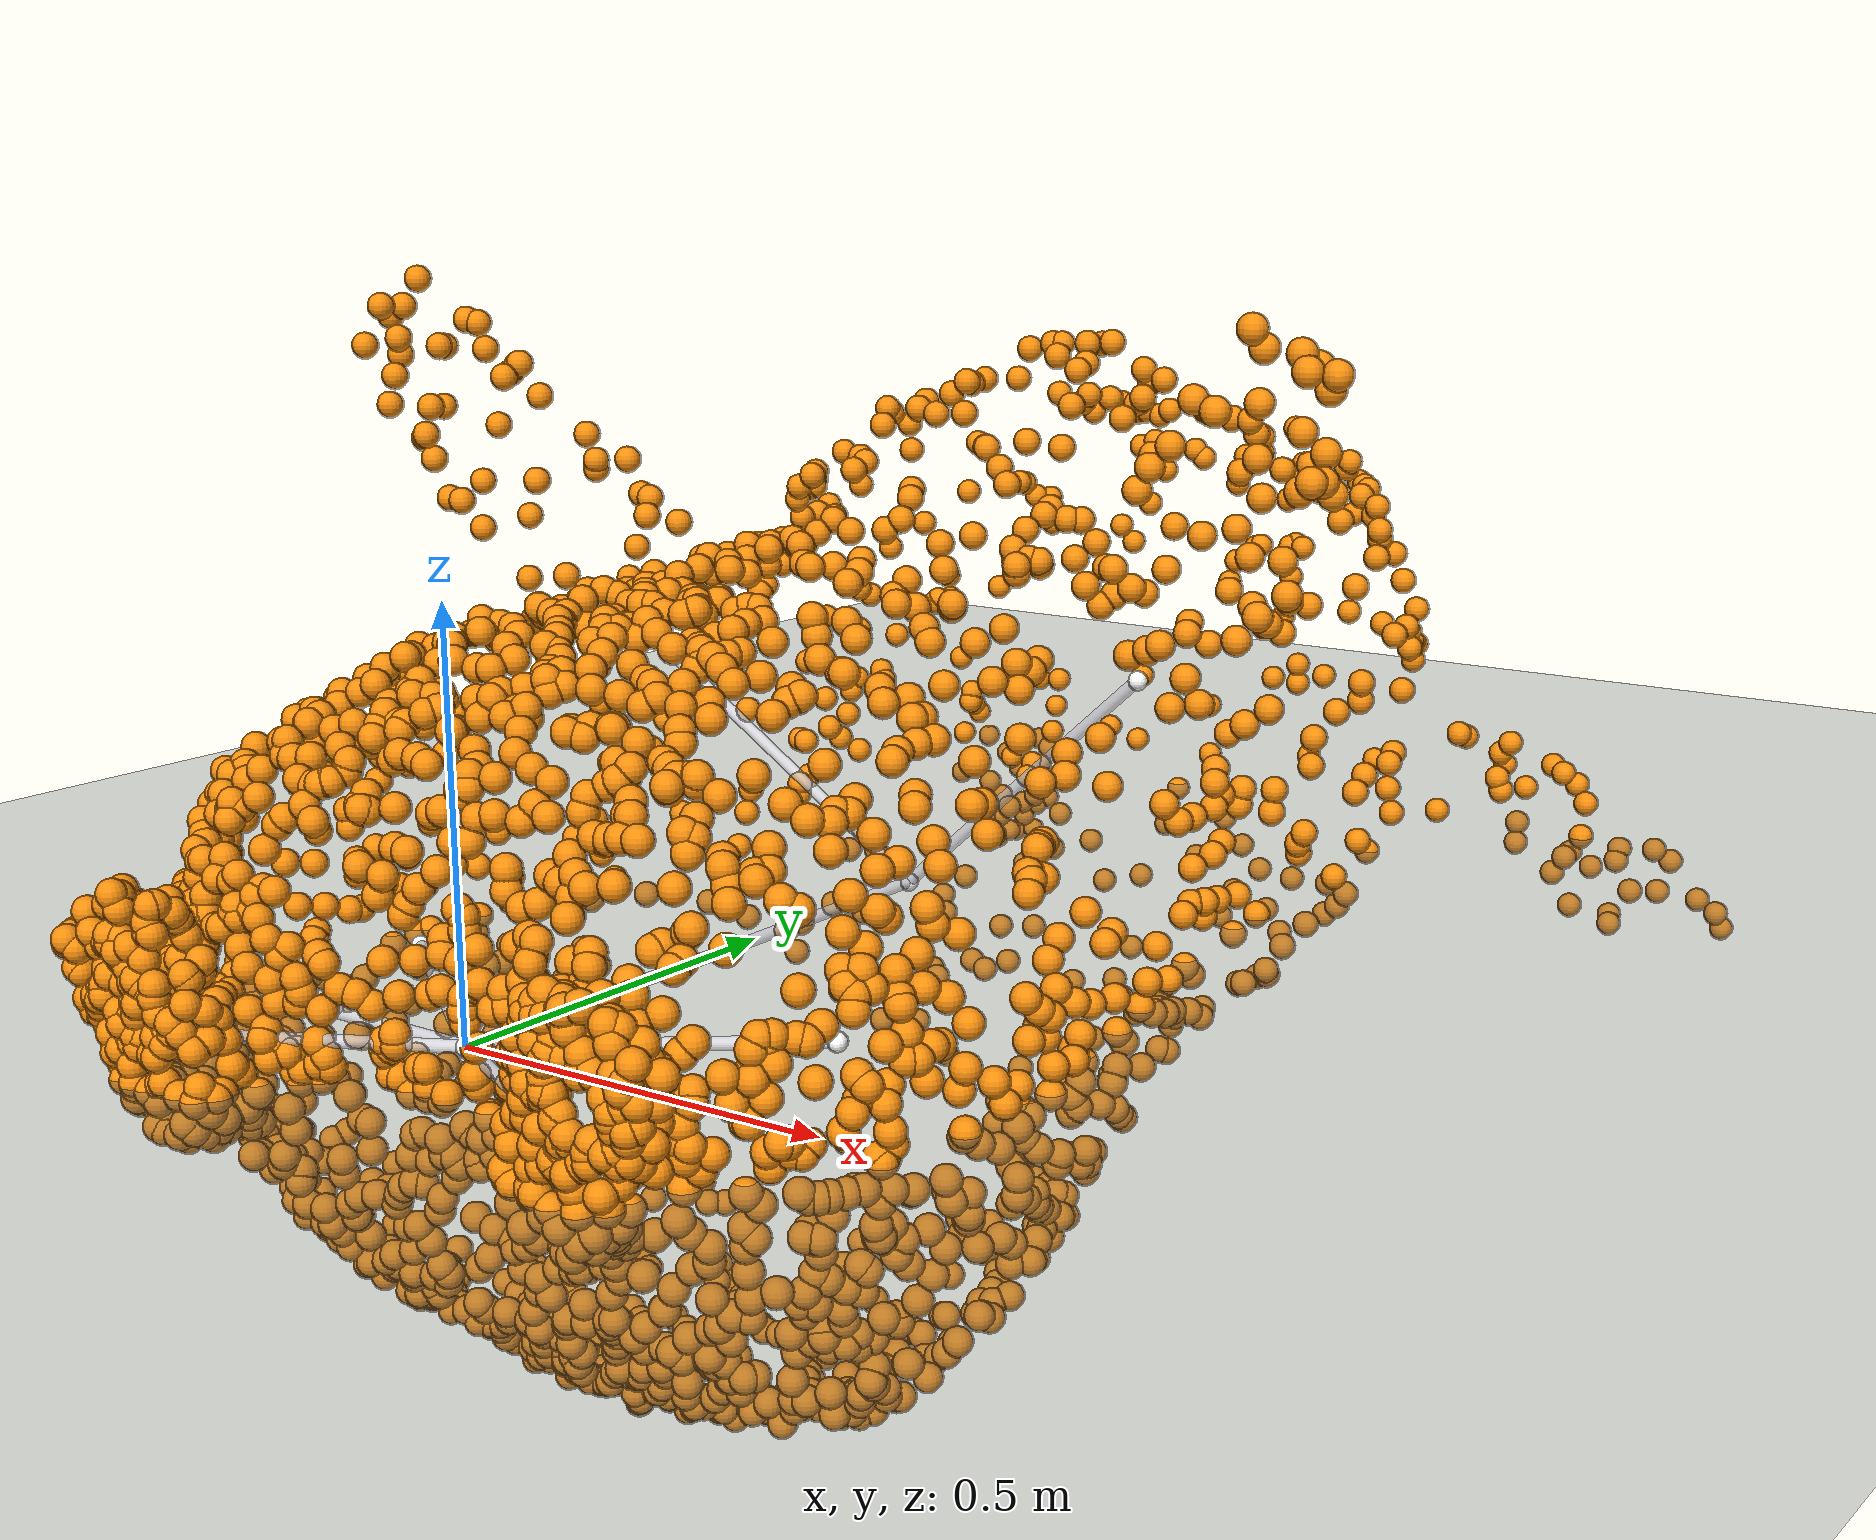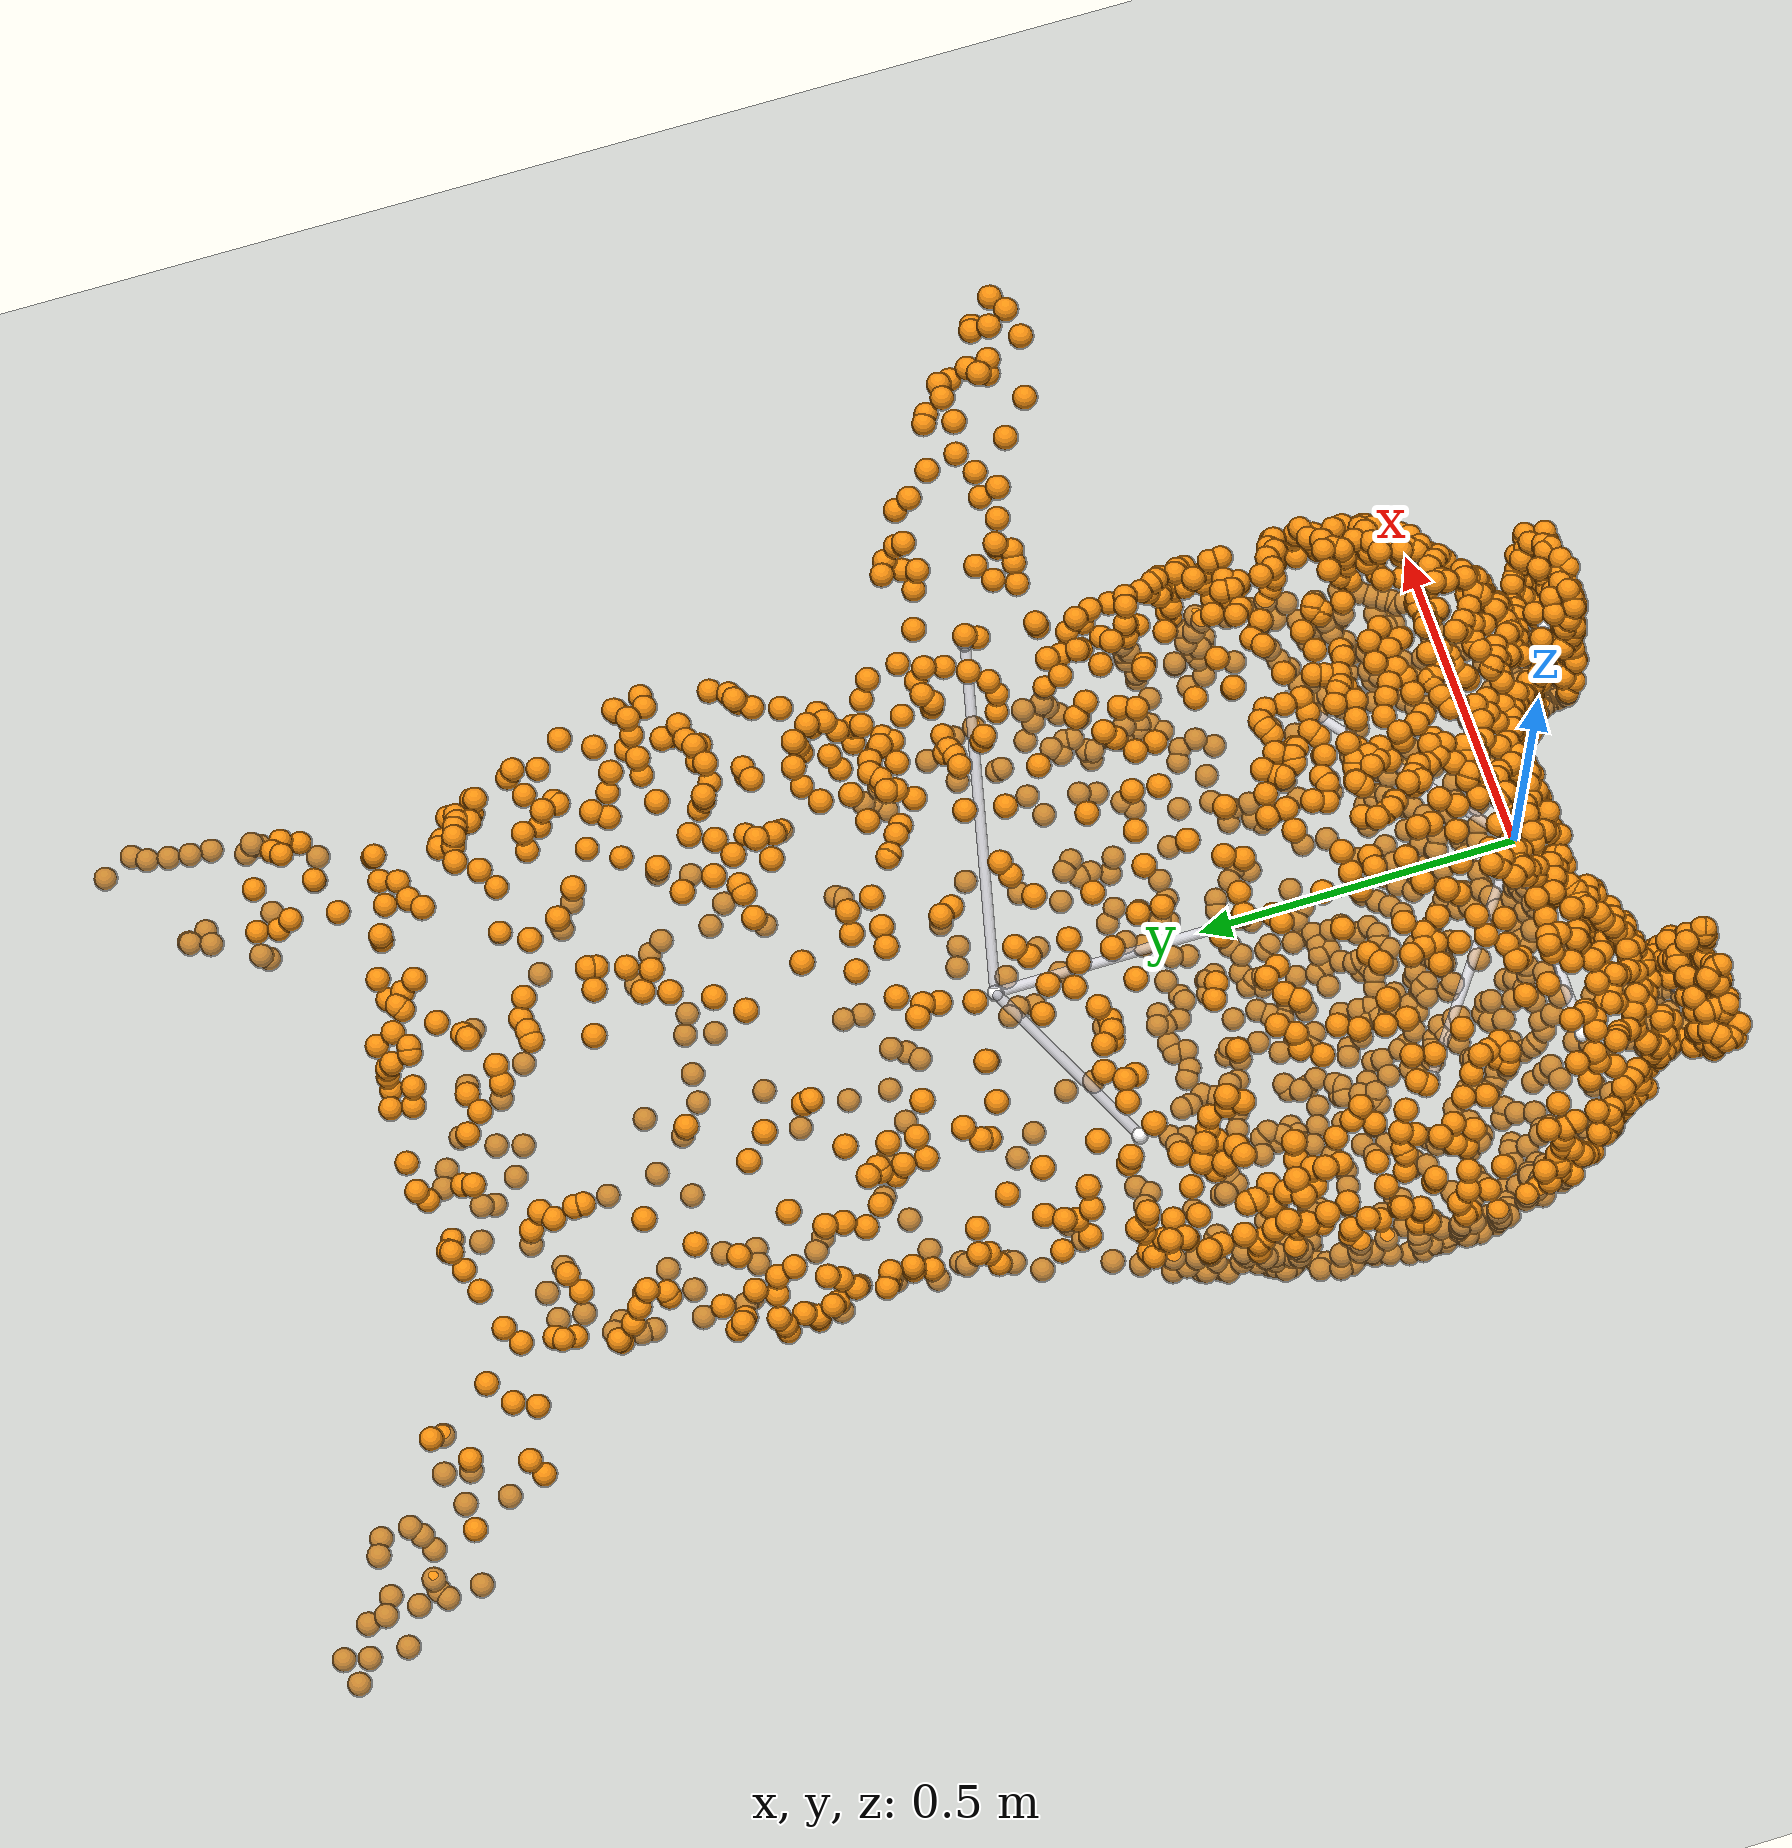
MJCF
<?xml version="1.0"?>
<mujoco model="pikachu_cloud">
  <compiler angle="radian"/>
  <option timestep="0.004" gravity="0 0 -9.81" integrator="RK4"/>
  <visual><global elevation="-35" azimuth="110" offwidth="800" offheight="800"/></visual>
  <worldbody>
    <geom name="floor" type="plane" size="3 3 0.1" pos="0 0 -0.05" rgba="0.42 0.46 0.5 1"/>
    <light name="key" pos="1.5 2.0 2.5" dir="-0.4 -0.5 -1" diffuse="0.95 0.95 0.95" ambient="0.75 0.75 0.75" castshadow="false"/>
    <body name="骨架" pos="0.0000 0.0000 0.0000">
      <site type="sphere" size="0.012" rgba="1 1 1 0.95"/>
      <geom name="bone_base_link" type="capsule" fromto="0 0 0 0.0000 0.2468 -0.0000" size="0.008" rgba="0.80 0.80 0.85 0.7"/>
      <geom name="bone_hip_L" type="capsule" fromto="0 0 0 0.0000 0.2468 -0.0000" size="0.008" rgba="0.80 0.80 0.85 0.7"/>
      <geom name="bone_hip_R" type="capsule" fromto="0 0 0 0.0000 0.2468 -0.0000" size="0.008" rgba="0.80 0.80 0.85 0.7"/>
      <geom name="bone_hip_pitch_L" type="capsule" fromto="0 0 0 0.3291 0.2468 0.0000" size="0.008" rgba="0.80 0.80 0.85 0.7"/>
      <geom name="bone_hip_pitch_R" type="capsule" fromto="0 0 0 -0.3291 0.2468 0.0000" size="0.008" rgba="0.80 0.80 0.85 0.7"/>
      <geom name="bone_hip_knee_L" type="capsule" fromto="0 0 0 0.3291 0.0082 -0.0000" size="0.008" rgba="0.80 0.80 0.85 0.7"/>
      <geom name="bone_hip_knee_R" type="capsule" fromto="0 0 0 -0.3291 0.0082 -0.0000" size="0.008" rgba="0.80 0.80 0.85 0.7"/>
      <geom name="bone_hip_ankle_L" type="capsule" fromto="0 0 0 0.3291 -0.1646 -0.0000" size="0.008" rgba="0.80 0.80 0.85 0.7"/>
      <geom name="bone_hip_ankle_R" type="capsule" fromto="0 0 0 -0.3291 -0.1646 -0.0000" size="0.008" rgba="0.80 0.80 0.85 0.7"/>
      <geom type="sphere" size="0.018" pos="0.1384 0.1108 0.3597" rgba="0.95 0.55 0.05 1" contype="0" conaffinity="0"/>
      <geom type="sphere" size="0.018" pos="0.0928 0.0305 0.2834" rgba="0.95 0.55 0.05 1" contype="0" conaffinity="0"/>
      <geom type="sphere" size="0.018" pos="0.1469 -0.0051 -0.1742" rgba="0.95 0.55 0.05 1" contype="0" conaffinity="0"/>
      <geom type="sphere" size="0.018" pos="-0.1197 0.0785 0.3506" rgba="0.95 0.55 0.05 1" contype="0" conaffinity="0"/>
      <geom type="sphere" size="0.018" pos="0.1495 -0.0665 0.0144" rgba="0.95 0.55 0.05 1" contype="0" conaffinity="0"/>
      <geom type="sphere" size="0.018" pos="0.0079 0.0769 -0.3428" rgba="0.95 0.55 0.05 1" contype="0" conaffinity="0"/>
      <geom type="sphere" size="0.018" pos="-0.0736 -0.0359 0.0113" rgba="0.95 0.55 0.05 1" contype="0" conaffinity="0"/>
      <geom type="sphere" size="0.018" pos="0.1025 0.0245 -0.2479" rgba="0.95 0.55 0.05 1" contype="0" conaffinity="0"/>
      <geom type="sphere" size="0.018" pos="-0.0634 -0.0359 0.0575" rgba="0.95 0.55 0.05 1" contype="0" conaffinity="0"/>
      <geom type="sphere" size="0.018" pos="-0.1318 0.0092 -0.2074" rgba="0.95 0.55 0.05 1" contype="0" conaffinity="0"/>
      <geom type="sphere" size="0.018" pos="0.0858 -0.0259 -0.0655" rgba="0.95 0.55 0.05 1" contype="0" conaffinity="0"/>
      <geom type="sphere" size="0.018" pos="0.1653 -0.0612 0.1422" rgba="0.95 0.55 0.05 1" contype="0" conaffinity="0"/>
      <geom type="sphere" size="0.018" pos="-0.0151 0.0922 -0.3668" rgba="0.95 0.55 0.05 1" contype="0" conaffinity="0"/>
      <geom type="sphere" size="0.018" pos="-0.0555 0.0994 -0.3784" rgba="0.95 0.55 0.05 1" contype="0" conaffinity="0"/>
      <geom type="sphere" size="0.018" pos="0.1559 -0.0603 0.0916" rgba="0.95 0.55 0.05 1" contype="0" conaffinity="0"/>
      <geom type="sphere" size="0.018" pos="0.1486 -0.0623 0.0447" rgba="0.95 0.55 0.05 1" contype="0" conaffinity="0"/>
      <geom type="sphere" size="0.018" pos="0.1630 -0.0698 0.0347" rgba="0.95 0.55 0.05 1" contype="0" conaffinity="0"/>
      <geom type="sphere" size="0.018" pos="0.0292 -0.0142 -0.1299" rgba="0.95 0.55 0.05 1" contype="0" conaffinity="0"/>
      <geom type="sphere" size="0.018" pos="-0.0380 -0.0230 -0.0603" rgba="0.95 0.55 0.05 1" contype="0" conaffinity="0"/>
      <geom type="sphere" size="0.018" pos="0.0475 -0.0354 -0.0138" rgba="0.95 0.55 0.05 1" contype="0" conaffinity="0"/>
      <geom type="sphere" size="0.018" pos="0.1548 0.0465 0.2990" rgba="0.95 0.55 0.05 1" contype="0" conaffinity="0"/>
      <geom type="sphere" size="0.018" pos="-0.1578 -0.0646 0.0962" rgba="0.95 0.55 0.05 1" contype="0" conaffinity="0"/>
      <geom type="sphere" size="0.018" pos="-0.0903 0.0359 0.3110" rgba="0.95 0.55 0.05 1" contype="0" conaffinity="0"/>
      <geom type="sphere" size="0.018" pos="-0.1050 -0.0382 0.0398" rgba="0.95 0.55 0.05 1" contype="0" conaffinity="0"/>
      <geom type="sphere" size="0.018" pos="0.0004 -0.0254 0.1318" rgba="0.95 0.55 0.05 1" contype="0" conaffinity="0"/>
      <geom type="sphere" size="0.018" pos="0.0181 0.0992 0.3696" rgba="0.95 0.55 0.05 1" contype="0" conaffinity="0"/>
      <geom type="sphere" size="0.018" pos="0.0000 -0.0323 -0.0470" rgba="0.95 0.55 0.05 1" contype="0" conaffinity="0"/>
      <geom type="sphere" size="0.018" pos="-0.0378 -0.0323 0.1024" rgba="0.95 0.55 0.05 1" contype="0" conaffinity="0"/>
      <geom type="sphere" size="0.018" pos="-0.0664 0.1071 0.3673" rgba="0.95 0.55 0.05 1" contype="0" conaffinity="0"/>
      <geom type="sphere" size="0.018" pos="0.0168 0.1106 -0.3864" rgba="0.95 0.55 0.05 1" contype="0" conaffinity="0"/>
      <geom type="sphere" size="0.018" pos="-0.1245 0.0697 -0.3376" rgba="0.95 0.55 0.05 1" contype="0" conaffinity="0"/>
      <geom type="sphere" size="0.018" pos="0.0228 -0.0183 -0.0912" rgba="0.95 0.55 0.05 1" contype="0" conaffinity="0"/>
      <geom type="sphere" size="0.018" pos="-0.1205 0.0384 0.3112" rgba="0.95 0.55 0.05 1" contype="0" conaffinity="0"/>
      <geom type="sphere" size="0.018" pos="0.1477 0.0535 -0.3100" rgba="0.95 0.55 0.05 1" contype="0" conaffinity="0"/>
      <geom type="sphere" size="0.018" pos="-0.0861 0.0048 -0.1828" rgba="0.95 0.55 0.05 1" contype="0" conaffinity="0"/>
      <geom type="sphere" size="0.018" pos="0.0410 0.0210 -0.2385" rgba="0.95 0.55 0.05 1" contype="0" conaffinity="0"/>
      <geom type="sphere" size="0.018" pos="0.0665 0.0470 -0.2990" rgba="0.95 0.55 0.05 1" contype="0" conaffinity="0"/>
      <geom type="sphere" size="0.018" pos="-0.0346 -0.0268 -0.0458" rgba="0.95 0.55 0.05 1" contype="0" conaffinity="0"/>
      <geom type="sphere" size="0.018" pos="0.1485 -0.0727 0.0206" rgba="0.95 0.55 0.05 1" contype="0" conaffinity="0"/>
      <geom type="sphere" size="0.018" pos="-0.0575 -0.0274 0.1504" rgba="0.95 0.55 0.05 1" contype="0" conaffinity="0"/>
      <geom type="sphere" size="0.018" pos="0.1635 -0.0482 0.1623" rgba="0.95 0.55 0.05 1" contype="0" conaffinity="0"/>
      <geom type="sphere" size="0.018" pos="0.1018 -0.0375 0.0747" rgba="0.95 0.55 0.05 1" contype="0" conaffinity="0"/>
      <geom type="sphere" size="0.018" pos="-0.0909 -0.0281 -0.0422" rgba="0.95 0.55 0.05 1" contype="0" conaffinity="0"/>
      <geom type="sphere" size="0.018" pos="-0.0539 0.0029 -0.1923" rgba="0.95 0.55 0.05 1" contype="0" conaffinity="0"/>
      <geom type="sphere" size="0.018" pos="0.1301 0.0205 -0.2271" rgba="0.95 0.55 0.05 1" contype="0" conaffinity="0"/>
      <geom type="sphere" size="0.018" pos="0.0158 0.1022 0.3570" rgba="0.95 0.55 0.05 1" contype="0" conaffinity="0"/>
      <geom type="sphere" size="0.018" pos="-0.0077 0.0240 0.2819" rgba="0.95 0.55 0.05 1" contype="0" conaffinity="0"/>
      <geom type="sphere" size="0.018" pos="-0.1190 -0.0481 0.0530" rgba="0.95 0.55 0.05 1" contype="0" conaffinity="0"/>
      <geom type="sphere" size="0.018" pos="0.1304 0.0849 -0.3549" rgba="0.95 0.55 0.05 1" contype="0" conaffinity="0"/>
      <geom type="sphere" size="0.018" pos="-0.0741 -0.0355 -0.0007" rgba="0.95 0.55 0.05 1" contype="0" conaffinity="0"/>
      <geom type="sphere" size="0.018" pos="0.0627 0.0748 -0.3452" rgba="0.95 0.55 0.05 1" contype="0" conaffinity="0"/>
      <geom type="sphere" size="0.018" pos="-0.0472 0.0123 0.2584" rgba="0.95 0.55 0.05 1" contype="0" conaffinity="0"/>
      <geom type="sphere" size="0.018" pos="0.0070 -0.0347 0.1181" rgba="0.95 0.55 0.05 1" contype="0" conaffinity="0"/>
      <geom type="sphere" size="0.018" pos="0.0558 -0.0298 0.1306" rgba="0.95 0.55 0.05 1" contype="0" conaffinity="0"/>
      <geom type="sphere" size="0.018" pos="-0.0642 0.0696 0.3395" rgba="0.95 0.55 0.05 1" contype="0" conaffinity="0"/>
      <geom type="sphere" size="0.018" pos="0.1004 0.1195 -0.4075" rgba="0.95 0.55 0.05 1" contype="0" conaffinity="0"/>
      <geom type="sphere" size="0.018" pos="0.1337 0.1091 0.3591" rgba="0.95 0.55 0.05 1" contype="0" conaffinity="0"/>
      <geom type="sphere" size="0.018" pos="-0.1060 0.0995 -0.3700" rgba="0.95 0.55 0.05 1" contype="0" conaffinity="0"/>
      <geom type="sphere" size="0.018" pos="-0.1223 0.1142 -0.4036" rgba="0.95 0.55 0.05 1" contype="0" conaffinity="0"/>
      <geom type="sphere" size="0.018" pos="0.0405 0.0550 -0.3020" rgba="0.95 0.55 0.05 1" contype="0" conaffinity="0"/>
      <geom type="sphere" size="0.018" pos="0.0407 -0.0377 0.0482" rgba="0.95 0.55 0.05 1" contype="0" conaffinity="0"/>
      <geom type="sphere" size="0.018" pos="-0.1579 -0.0045 -0.1550" rgba="0.95 0.55 0.05 1" contype="0" conaffinity="0"/>
      <geom type="sphere" size="0.018" pos="-0.0039 0.0292 0.3050" rgba="0.95 0.55 0.05 1" contype="0" conaffinity="0"/>
      <geom type="sphere" size="0.018" pos="-0.0594 -0.0156 0.2194" rgba="0.95 0.55 0.05 1" contype="0" conaffinity="0"/>
      <geom type="sphere" size="0.018" pos="-0.1049 -0.0204 0.1628" rgba="0.95 0.55 0.05 1" contype="0" conaffinity="0"/>
      <geom type="sphere" size="0.018" pos="0.0881 -0.0133 0.1974" rgba="0.95 0.55 0.05 1" contype="0" conaffinity="0"/>
      <geom type="sphere" size="0.018" pos="-0.0512 0.0921 -0.3655" rgba="0.95 0.55 0.05 1" contype="0" conaffinity="0"/>
      <geom type="sphere" size="0.018" pos="0.0000 0.0233 0.2917" rgba="0.95 0.55 0.05 1" contype="0" conaffinity="0"/>
      <geom type="sphere" size="0.018" pos="0.1011 0.0491 0.3067" rgba="0.95 0.55 0.05 1" contype="0" conaffinity="0"/>
      <geom type="sphere" size="0.018" pos="-0.1474 -0.0667 0.0886" rgba="0.95 0.55 0.05 1" contype="0" conaffinity="0"/>
      <geom type="sphere" size="0.018" pos="-0.1585 0.0510 -0.2977" rgba="0.95 0.55 0.05 1" contype="0" conaffinity="0"/>
      <geom type="sphere" size="0.018" pos="0.0597 -0.0276 -0.0620" rgba="0.95 0.55 0.05 1" contype="0" conaffinity="0"/>
      <geom type="sphere" size="0.018" pos="0.1100 0.0554 -0.3011" rgba="0.95 0.55 0.05 1" contype="0" conaffinity="0"/>
      <geom type="sphere" size="0.018" pos="0.0410 0.1188 -0.4044" rgba="0.95 0.55 0.05 1" contype="0" conaffinity="0"/>
      <geom type="sphere" size="0.018" pos="-0.0151 -0.0054 -0.1402" rgba="0.95 0.55 0.05 1" contype="0" conaffinity="0"/>
      <geom type="sphere" size="0.018" pos="-0.1028 0.1072 -0.3800" rgba="0.95 0.55 0.05 1" contype="0" conaffinity="0"/>
      <geom type="sphere" size="0.018" pos="-0.0318 -0.0318 -0.0220" rgba="0.95 0.55 0.05 1" contype="0" conaffinity="0"/>
      <geom type="sphere" size="0.018" pos="-0.1423 0.0049 0.2497" rgba="0.95 0.55 0.05 1" contype="0" conaffinity="0"/>
      <geom type="sphere" size="0.018" pos="0.1185 -0.0216 0.1858" rgba="0.95 0.55 0.05 1" contype="0" conaffinity="0"/>
      <geom type="sphere" size="0.018" pos="0.0257 -0.0133 -0.1228" rgba="0.95 0.55 0.05 1" contype="0" conaffinity="0"/>
      <geom type="sphere" size="0.018" pos="-0.0947 -0.0011 -0.1812" rgba="0.95 0.55 0.05 1" contype="0" conaffinity="0"/>
      <geom type="sphere" size="0.018" pos="-0.1108 0.0910 0.3544" rgba="0.95 0.55 0.05 1" contype="0" conaffinity="0"/>
      <geom type="sphere" size="0.018" pos="0.0116 0.0182 -0.2202" rgba="0.95 0.55 0.05 1" contype="0" conaffinity="0"/>
      <geom type="sphere" size="0.018" pos="-0.0249 -0.0003 -0.1608" rgba="0.95 0.55 0.05 1" contype="0" conaffinity="0"/>
      <geom type="sphere" size="0.018" pos="0.1263 0.0249 -0.2441" rgba="0.95 0.55 0.05 1" contype="0" conaffinity="0"/>
      <geom type="sphere" size="0.018" pos="0.0293 -0.0305 0.1122" rgba="0.95 0.55 0.05 1" contype="0" conaffinity="0"/>
      <geom type="sphere" size="0.018" pos="0.0695 -0.0265 -0.0803" rgba="0.95 0.55 0.05 1" contype="0" conaffinity="0"/>
      <geom type="sphere" size="0.018" pos="-0.1501 0.0762 0.3352" rgba="0.95 0.55 0.05 1" contype="0" conaffinity="0"/>
      <geom type="sphere" size="0.018" pos="0.0264 0.0803 0.3476" rgba="0.95 0.55 0.05 1" contype="0" conaffinity="0"/>
      <geom type="sphere" size="0.018" pos="-0.0682 -0.0186 -0.1117" rgba="0.95 0.55 0.05 1" contype="0" conaffinity="0"/>
      <geom type="sphere" size="0.018" pos="0.0855 -0.0098 0.2205" rgba="0.95 0.55 0.05 1" contype="0" conaffinity="0"/>
      <geom type="sphere" size="0.018" pos="0.0140 -0.0205 -0.0846" rgba="0.95 0.55 0.05 1" contype="0" conaffinity="0"/>
      <geom type="sphere" size="0.018" pos="0.0600 0.0195 -0.2294" rgba="0.95 0.55 0.05 1" contype="0" conaffinity="0"/>
      <geom type="sphere" size="0.018" pos="-0.0193 0.0958 -0.3706" rgba="0.95 0.55 0.05 1" contype="0" conaffinity="0"/>
      <geom type="sphere" size="0.018" pos="0.0442 -0.0254 -0.0901" rgba="0.95 0.55 0.05 1" contype="0" conaffinity="0"/>
      <geom type="sphere" size="0.018" pos="0.0016 -0.0341 0.0756" rgba="0.95 0.55 0.05 1" contype="0" conaffinity="0"/>
      <geom type="sphere" size="0.018" pos="-0.0163 0.0172 -0.2117" rgba="0.95 0.55 0.05 1" contype="0" conaffinity="0"/>
      <geom type="sphere" size="0.018" pos="-0.0895 -0.0084 -0.1449" rgba="0.95 0.55 0.05 1" contype="0" conaffinity="0"/>
      <geom type="sphere" size="0.018" pos="0.1559 -0.0477 0.1448" rgba="0.95 0.55 0.05 1" contype="0" conaffinity="0"/>
      <geom type="sphere" size="0.018" pos="-0.0316 -0.0160 -0.1102" rgba="0.95 0.55 0.05 1" contype="0" conaffinity="0"/>
      <geom type="sphere" size="0.018" pos="-0.0863 -0.0318 -0.0094" rgba="0.95 0.55 0.05 1" contype="0" conaffinity="0"/>
      <geom type="sphere" size="0.018" pos="0.0555 -0.0179 -0.1085" rgba="0.95 0.55 0.05 1" contype="0" conaffinity="0"/>
      <geom type="sphere" size="0.018" pos="-0.1463 -0.0743 0.0358" rgba="0.95 0.55 0.05 1" contype="0" conaffinity="0"/>
      <geom type="sphere" size="0.018" pos="0.1404 0.1041 0.3598" rgba="0.95 0.55 0.05 1" contype="0" conaffinity="0"/>
      <geom type="sphere" size="0.018" pos="0.1402 -0.0346 0.1604" rgba="0.95 0.55 0.05 1" contype="0" conaffinity="0"/>
      <geom type="sphere" size="0.018" pos="0.0543 -0.0211 -0.0621" rgba="0.95 0.55 0.05 1" contype="0" conaffinity="0"/>
      <geom type="sphere" size="0.018" pos="-0.1460 0.0180 -0.2254" rgba="0.95 0.55 0.05 1" contype="0" conaffinity="0"/>
      <geom type="sphere" size="0.018" pos="0.1053 0.0615 -0.3270" rgba="0.95 0.55 0.05 1" contype="0" conaffinity="0"/>
      <geom type="sphere" size="0.018" pos="0.0913 0.0848 0.3538" rgba="0.95 0.55 0.05 1" contype="0" conaffinity="0"/>
      <geom type="sphere" size="0.018" pos="0.1174 0.0971 -0.3709" rgba="0.95 0.55 0.05 1" contype="0" conaffinity="0"/>
      <geom type="sphere" size="0.018" pos="-0.0268 0.0082 0.2653" rgba="0.95 0.55 0.05 1" contype="0" conaffinity="0"/>
      <geom type="sphere" size="0.018" pos="-0.0732 0.0334 0.3059" rgba="0.95 0.55 0.05 1" contype="0" conaffinity="0"/>
      <geom type="sphere" size="0.018" pos="0.0699 0.0509 0.3172" rgba="0.95 0.55 0.05 1" contype="0" conaffinity="0"/>
      <geom type="sphere" size="0.018" pos="-0.1380 0.1103 -0.3916" rgba="0.95 0.55 0.05 1" contype="0" conaffinity="0"/>
      <geom type="sphere" size="0.018" pos="-0.1374 -0.0160 0.1910" rgba="0.95 0.55 0.05 1" contype="0" conaffinity="0"/>
      <geom type="sphere" size="0.018" pos="0.0326 0.0256 -0.2308" rgba="0.95 0.55 0.05 1" contype="0" conaffinity="0"/>
      <geom type="sphere" size="0.018" pos="0.1492 0.0543 -0.3154" rgba="0.95 0.55 0.05 1" contype="0" conaffinity="0"/>
      <geom type="sphere" size="0.018" pos="0.0022 -0.0049 0.2372" rgba="0.95 0.55 0.05 1" contype="0" conaffinity="0"/>
      <geom type="sphere" size="0.018" pos="-0.0700 0.0129 -0.2147" rgba="0.95 0.55 0.05 1" contype="0" conaffinity="0"/>
      <geom type="sphere" size="0.018" pos="0.1540 0.0391 0.2828" rgba="0.95 0.55 0.05 1" contype="0" conaffinity="0"/>
      <geom type="sphere" size="0.018" pos="-0.1570 0.0189 0.2638" rgba="0.95 0.55 0.05 1" contype="0" conaffinity="0"/>
      <geom type="sphere" size="0.018" pos="-0.1594 0.0101 0.2520" rgba="0.95 0.55 0.05 1" contype="0" conaffinity="0"/>
      <geom type="sphere" size="0.018" pos="-0.0402 -0.0201 0.1813" rgba="0.95 0.55 0.05 1" contype="0" conaffinity="0"/>
      <geom type="sphere" size="0.018" pos="0.0539 0.0888 -0.3765" rgba="0.95 0.55 0.05 1" contype="0" conaffinity="0"/>
      <geom type="sphere" size="0.018" pos="0.0000 0.1012 -0.3824" rgba="0.95 0.55 0.05 1" contype="0" conaffinity="0"/>
      <geom type="sphere" size="0.018" pos="0.0459 0.0153 0.2689" rgba="0.95 0.55 0.05 1" contype="0" conaffinity="0"/>
      <geom type="sphere" size="0.018" pos="-0.0400 -0.0329 -0.0229" rgba="0.95 0.55 0.05 1" contype="0" conaffinity="0"/>
      <geom type="sphere" size="0.018" pos="-0.0572 -0.0082 -0.1438" rgba="0.95 0.55 0.05 1" contype="0" conaffinity="0"/>
      <geom type="sphere" size="0.018" pos="0.0331 -0.0253 0.1463" rgba="0.95 0.55 0.05 1" contype="0" conaffinity="0"/>
      <geom type="sphere" size="0.018" pos="-0.0117 -0.0372 0.0690" rgba="0.95 0.55 0.05 1" contype="0" conaffinity="0"/>
      <geom type="sphere" size="0.018" pos="-0.0392 0.0852 0.3542" rgba="0.95 0.55 0.05 1" contype="0" conaffinity="0"/>
      <geom type="sphere" size="0.018" pos="0.0227 -0.0011 0.2391" rgba="0.95 0.55 0.05 1" contype="0" conaffinity="0"/>
      <geom type="sphere" size="0.018" pos="-0.1367 -0.0241 -0.1104" rgba="0.95 0.55 0.05 1" contype="0" conaffinity="0"/>
      <geom type="sphere" size="0.018" pos="-0.1176 0.0229 -0.2482" rgba="0.95 0.55 0.05 1" contype="0" conaffinity="0"/>
      <geom type="sphere" size="0.018" pos="0.0874 0.0955 0.3543" rgba="0.95 0.55 0.05 1" contype="0" conaffinity="0"/>
      <geom type="sphere" size="0.018" pos="0.1050 -0.0248 -0.0394" rgba="0.95 0.55 0.05 1" contype="0" conaffinity="0"/>
      <geom type="sphere" size="0.018" pos="0.1382 0.0222 -0.2389" rgba="0.95 0.55 0.05 1" contype="0" conaffinity="0"/>
      <geom type="sphere" size="0.018" pos="0.0385 -0.0365 0.0743" rgba="0.95 0.55 0.05 1" contype="0" conaffinity="0"/>
      <geom type="sphere" size="0.018" pos="-0.1453 -0.0014 0.2523" rgba="0.95 0.55 0.05 1" contype="0" conaffinity="0"/>
      <geom type="sphere" size="0.018" pos="-0.1409 0.0651 -0.3309" rgba="0.95 0.55 0.05 1" contype="0" conaffinity="0"/>
      <geom type="sphere" size="0.018" pos="0.0477 -0.0297 -0.0271" rgba="0.95 0.55 0.05 1" contype="0" conaffinity="0"/>
      <geom type="sphere" size="0.018" pos="-0.0864 -0.0354 0.0938" rgba="0.95 0.55 0.05 1" contype="0" conaffinity="0"/>
      <geom type="sphere" size="0.018" pos="-0.1479 -0.0711 -0.0193" rgba="0.95 0.55 0.05 1" contype="0" conaffinity="0"/>
      <geom type="sphere" size="0.018" pos="-0.0621 -0.0159 -0.1087" rgba="0.95 0.55 0.05 1" contype="0" conaffinity="0"/>
      <geom type="sphere" size="0.018" pos="-0.0105 0.0209 0.2887" rgba="0.95 0.55 0.05 1" contype="0" conaffinity="0"/>
      <geom type="sphere" size="0.018" pos="0.1460 -0.0757 0.0417" rgba="0.95 0.55 0.05 1" contype="0" conaffinity="0"/>
      <geom type="sphere" size="0.018" pos="0.0968 0.0103 -0.1980" rgba="0.95 0.55 0.05 1" contype="0" conaffinity="0"/>
      <geom type="sphere" size="0.018" pos="-0.0937 -0.0318 -0.0163" rgba="0.95 0.55 0.05 1" contype="0" conaffinity="0"/>
      <geom type="sphere" size="0.018" pos="0.0000 0.0842 0.3601" rgba="0.95 0.55 0.05 1" contype="0" conaffinity="0"/>
      <geom type="sphere" size="0.018" pos="0.1539 -0.0243 -0.1036" rgba="0.95 0.55 0.05 1" contype="0" conaffinity="0"/>
      <geom type="sphere" size="0.018" pos="-0.0888 -0.0261 0.1895" rgba="0.95 0.55 0.05 1" contype="0" conaffinity="0"/>
      <geom type="sphere" size="0.018" pos="0.0261 0.0086 0.2644" rgba="0.95 0.55 0.05 1" contype="0" conaffinity="0"/>
      <geom type="sphere" size="0.018" pos="0.0824 0.0195 0.2669" rgba="0.95 0.55 0.05 1" contype="0" conaffinity="0"/>
      <geom type="sphere" size="0.018" pos="-0.0124 0.0322 -0.2651" rgba="0.95 0.55 0.05 1" contype="0" conaffinity="0"/>
      <geom type="sphere" size="0.018" pos="0.1333 0.0833 -0.3435" rgba="0.95 0.55 0.05 1" contype="0" conaffinity="0"/>
      <geom type="sphere" size="0.018" pos="0.0945 -0.0248 -0.0609" rgba="0.95 0.55 0.05 1" contype="0" conaffinity="0"/>
      <geom type="sphere" size="0.018" pos="-0.0633 -0.0251 -0.0594" rgba="0.95 0.55 0.05 1" contype="0" conaffinity="0"/>
      <geom type="sphere" size="0.018" pos="-0.0153 -0.0141 0.2037" rgba="0.95 0.55 0.05 1" contype="0" conaffinity="0"/>
      <geom type="sphere" size="0.018" pos="0.1507 -0.0263 -0.0946" rgba="0.95 0.55 0.05 1" contype="0" conaffinity="0"/>
      <geom type="sphere" size="0.018" pos="0.1050 -0.0295 -0.0564" rgba="0.95 0.55 0.05 1" contype="0" conaffinity="0"/>
      <geom type="sphere" size="0.018" pos="-0.0976 -0.0304 -0.0123" rgba="0.95 0.55 0.05 1" contype="0" conaffinity="0"/>
      <geom type="sphere" size="0.018" pos="0.0278 0.0375 0.3040" rgba="0.95 0.55 0.05 1" contype="0" conaffinity="0"/>
      <geom type="sphere" size="0.018" pos="-0.1077 0.0319 -0.2685" rgba="0.95 0.55 0.05 1" contype="0" conaffinity="0"/>
      <geom type="sphere" size="0.018" pos="-0.0378 0.1146 0.3748" rgba="0.95 0.55 0.05 1" contype="0" conaffinity="0"/>
      <geom type="sphere" size="0.018" pos="0.0735 0.0644 -0.3320" rgba="0.95 0.55 0.05 1" contype="0" conaffinity="0"/>
      <geom type="sphere" size="0.018" pos="0.1089 0.1039 0.3580" rgba="0.95 0.55 0.05 1" contype="0" conaffinity="0"/>
      <geom type="sphere" size="0.018" pos="-0.1408 -0.0477 -0.0714" rgba="0.95 0.55 0.05 1" contype="0" conaffinity="0"/>
      <geom type="sphere" size="0.018" pos="0.0010 0.1033 0.3645" rgba="0.95 0.55 0.05 1" contype="0" conaffinity="0"/>
      <geom type="sphere" size="0.018" pos="-0.0213 0.1208 -0.4079" rgba="0.95 0.55 0.05 1" contype="0" conaffinity="0"/>
      <geom type="sphere" size="0.018" pos="0.1596 -0.0188 0.2270" rgba="0.95 0.55 0.05 1" contype="0" conaffinity="0"/>
      <geom type="sphere" size="0.018" pos="-0.0897 -0.0049 0.2169" rgba="0.95 0.55 0.05 1" contype="0" conaffinity="0"/>
      <geom type="sphere" size="0.018" pos="-0.1016 0.0096 0.2577" rgba="0.95 0.55 0.05 1" contype="0" conaffinity="0"/>
      <geom type="sphere" size="0.018" pos="0.1349 0.0733 -0.3322" rgba="0.95 0.55 0.05 1" contype="0" conaffinity="0"/>
      <geom type="sphere" size="0.018" pos="-0.1239 0.0083 -0.1967" rgba="0.95 0.55 0.05 1" contype="0" conaffinity="0"/>
      <geom type="sphere" size="0.018" pos="-0.0901 -0.0359 0.0001" rgba="0.95 0.55 0.05 1" contype="0" conaffinity="0"/>
      <geom type="sphere" size="0.018" pos="0.0400 -0.0394 0.0604" rgba="0.95 0.55 0.05 1" contype="0" conaffinity="0"/>
      <geom type="sphere" size="0.018" pos="-0.0308 -0.0119 -0.1292" rgba="0.95 0.55 0.05 1" contype="0" conaffinity="0"/>
      <geom type="sphere" size="0.018" pos="-0.1142 0.0625 -0.3217" rgba="0.95 0.55 0.05 1" contype="0" conaffinity="0"/>
      <geom type="sphere" size="0.018" pos="-0.1466 -0.0669 -0.0331" rgba="0.95 0.55 0.05 1" contype="0" conaffinity="0"/>
      <geom type="sphere" size="0.018" pos="-0.0265 0.0611 0.3232" rgba="0.95 0.55 0.05 1" contype="0" conaffinity="0"/>
      <geom type="sphere" size="0.018" pos="-0.1486 -0.0237 -0.1085" rgba="0.95 0.55 0.05 1" contype="0" conaffinity="0"/>
      <geom type="sphere" size="0.018" pos="-0.1465 0.0337 -0.2589" rgba="0.95 0.55 0.05 1" contype="0" conaffinity="0"/>
      <geom type="sphere" size="0.018" pos="0.1180 0.0025 -0.1911" rgba="0.95 0.55 0.05 1" contype="0" conaffinity="0"/>
      <geom type="sphere" size="0.018" pos="-0.0817 -0.0263 -0.0432" rgba="0.95 0.55 0.05 1" contype="0" conaffinity="0"/>
      <geom type="sphere" size="0.018" pos="0.0285 0.0429 -0.2734" rgba="0.95 0.55 0.05 1" contype="0" conaffinity="0"/>
      <geom type="sphere" size="0.018" pos="-0.0122 0.0507 0.3086" rgba="0.95 0.55 0.05 1" contype="0" conaffinity="0"/>
      <geom type="sphere" size="0.018" pos="0.0966 -0.0335 0.0927" rgba="0.95 0.55 0.05 1" contype="0" conaffinity="0"/>
      <geom type="sphere" size="0.018" pos="-0.0539 -0.0228 0.1611" rgba="0.95 0.55 0.05 1" contype="0" conaffinity="0"/>
      <geom type="sphere" size="0.018" pos="0.1190 0.0228 0.2761" rgba="0.95 0.55 0.05 1" contype="0" conaffinity="0"/>
      <geom type="sphere" size="0.018" pos="-0.0525 0.0540 -0.2954" rgba="0.95 0.55 0.05 1" contype="0" conaffinity="0"/>
      <geom type="sphere" size="0.018" pos="0.1095 0.0925 0.3493" rgba="0.95 0.55 0.05 1" contype="0" conaffinity="0"/>
      <geom type="sphere" size="0.018" pos="-0.1184 0.0561 -0.3100" rgba="0.95 0.55 0.05 1" contype="0" conaffinity="0"/>
      <geom type="sphere" size="0.018" pos="-0.1334 0.0395 0.3018" rgba="0.95 0.55 0.05 1" contype="0" conaffinity="0"/>
      <geom type="sphere" size="0.018" pos="-0.0305 0.1092 0.3800" rgba="0.95 0.55 0.05 1" contype="0" conaffinity="0"/>
      <geom type="sphere" size="0.018" pos="0.1527 -0.0738 0.0158" rgba="0.95 0.55 0.05 1" contype="0" conaffinity="0"/>
      <geom type="sphere" size="0.018" pos="0.0554 -0.0376 0.0215" rgba="0.95 0.55 0.05 1" contype="0" conaffinity="0"/>
      <geom type="sphere" size="0.018" pos="0.1534 -0.0613 0.1198" rgba="0.95 0.55 0.05 1" contype="0" conaffinity="0"/>
      <geom type="sphere" size="0.018" pos="-0.1460 0.1166 0.3594" rgba="0.95 0.55 0.05 1" contype="0" conaffinity="0"/>
      <geom type="sphere" size="0.018" pos="0.1222 -0.0365 0.1473" rgba="0.95 0.55 0.05 1" contype="0" conaffinity="0"/>
      <geom type="sphere" size="0.018" pos="0.1370 -0.0158 0.1917" rgba="0.95 0.55 0.05 1" contype="0" conaffinity="0"/>
      <geom type="sphere" size="0.018" pos="-0.0607 0.0604 0.3407" rgba="0.95 0.55 0.05 1" contype="0" conaffinity="0"/>
      <geom type="sphere" size="0.018" pos="0.1524 -0.0484 0.1233" rgba="0.95 0.55 0.05 1" contype="0" conaffinity="0"/>
      <geom type="sphere" size="0.018" pos="-0.1588 -0.0738 -0.0032" rgba="0.95 0.55 0.05 1" contype="0" conaffinity="0"/>
      <geom type="sphere" size="0.018" pos="-0.0211 -0.0095 -0.1287" rgba="0.95 0.55 0.05 1" contype="0" conaffinity="0"/>
      <geom type="sphere" size="0.018" pos="-0.1584 -0.0735 -0.0299" rgba="0.95 0.55 0.05 1" contype="0" conaffinity="0"/>
      <geom type="sphere" size="0.018" pos="0.0038 0.0897 -0.3725" rgba="0.95 0.55 0.05 1" contype="0" conaffinity="0"/>
      <geom type="sphere" size="0.018" pos="0.0364 0.0608 0.3282" rgba="0.95 0.55 0.05 1" contype="0" conaffinity="0"/>
      <geom type="sphere" size="0.018" pos="0.0525 -0.0341 0.0890" rgba="0.95 0.55 0.05 1" contype="0" conaffinity="0"/>
      <geom type="sphere" size="0.018" pos="-0.1373 -0.0554 0.0581" rgba="0.95 0.55 0.05 1" contype="0" conaffinity="0"/>
      <geom type="sphere" size="0.018" pos="-0.0182 -0.0217 -0.0607" rgba="0.95 0.55 0.05 1" contype="0" conaffinity="0"/>
      <geom type="sphere" size="0.018" pos="0.0638 -0.0361 0.0950" rgba="0.95 0.55 0.05 1" contype="0" conaffinity="0"/>
      <geom type="sphere" size="0.018" pos="-0.1117 0.1222 -0.4054" rgba="0.95 0.55 0.05 1" contype="0" conaffinity="0"/>
      <geom type="sphere" size="0.018" pos="-0.1501 0.0679 0.3290" rgba="0.95 0.55 0.05 1" contype="0" conaffinity="0"/>
      <geom type="sphere" size="0.018" pos="0.0246 -0.0250 0.1701" rgba="0.95 0.55 0.05 1" contype="0" conaffinity="0"/>
      <geom type="sphere" size="0.018" pos="0.1140 -0.0464 -0.0081" rgba="0.95 0.55 0.05 1" contype="0" conaffinity="0"/>
      <geom type="sphere" size="0.018" pos="0.0309 -0.0239 0.1623" rgba="0.95 0.55 0.05 1" contype="0" conaffinity="0"/>
      <geom type="sphere" size="0.018" pos="0.1426 0.1134 -0.3928" rgba="0.95 0.55 0.05 1" contype="0" conaffinity="0"/>
      <geom type="sphere" size="0.018" pos="0.0884 -0.0426 0.0714" rgba="0.95 0.55 0.05 1" contype="0" conaffinity="0"/>
      <geom type="sphere" size="0.018" pos="0.0548 0.0423 -0.2780" rgba="0.95 0.55 0.05 1" contype="0" conaffinity="0"/>
      <geom type="sphere" size="0.018" pos="-0.0306 0.0969 0.3753" rgba="0.95 0.55 0.05 1" contype="0" conaffinity="0"/>
    </body>
    <body name="base_link" pos="0.0000 0.2468 -0.0000">
      <site type="sphere" size="0.012" rgba="1 1 1 0.95"/>
      <geom name="bone_head" type="capsule" fromto="0 0 0 0.0000 0.5759 -0.0000" size="0.008" rgba="0.80 0.80 0.85 0.7"/>
      <geom name="bone_arm_L" type="capsule" fromto="0 0 0 0.0000 0.5759 -0.0000" size="0.008" rgba="0.80 0.80 0.85 0.7"/>
      <geom name="bone_arm_R" type="capsule" fromto="0 0 0 0.0000 0.5759 -0.0000" size="0.008" rgba="0.80 0.80 0.85 0.7"/>
    </body>
    <body name="hip_L" pos="0.0000 0.2468 -0.0000">
      <site type="sphere" size="0.012" rgba="1 1 1 0.95"/>
    </body>
    <body name="hip_R" pos="0.0000 0.2468 -0.0000">
      <site type="sphere" size="0.012" rgba="1 1 1 0.95"/>
      <geom type="sphere" size="0.018" pos="0.0210 0.1425 0.4471" rgba="0.95 0.55 0.05 1" contype="0" conaffinity="0"/>
      <geom type="sphere" size="0.018" pos="0.0153 0.0257 0.4331" rgba="0.95 0.55 0.05 1" contype="0" conaffinity="0"/>
      <geom type="sphere" size="0.018" pos="0.0814 0.2407 -0.5229" rgba="0.95 0.55 0.05 1" contype="0" conaffinity="0"/>
      <geom type="sphere" size="0.018" pos="0.0623 0.0670 0.4466" rgba="0.95 0.55 0.05 1" contype="0" conaffinity="0"/>
      <geom type="sphere" size="0.018" pos="-0.0041 -0.0823 -0.4578" rgba="0.95 0.55 0.05 1" contype="0" conaffinity="0"/>
      <geom type="sphere" size="0.018" pos="-0.0431 0.2445 -0.5407" rgba="0.95 0.55 0.05 1" contype="0" conaffinity="0"/>
      <geom type="sphere" size="0.018" pos="0.1134 -0.0609 -0.4650" rgba="0.95 0.55 0.05 1" contype="0" conaffinity="0"/>
      <geom type="sphere" size="0.018" pos="0.1320 0.1770 -0.5273" rgba="0.95 0.55 0.05 1" contype="0" conaffinity="0"/>
      <geom type="sphere" size="0.018" pos="0.1633 -0.0851 -0.4411" rgba="0.95 0.55 0.05 1" contype="0" conaffinity="0"/>
      <geom type="sphere" size="0.018" pos="-0.1166 0.0425 -0.5257" rgba="0.95 0.55 0.05 1" contype="0" conaffinity="0"/>
      <geom type="sphere" size="0.018" pos="0.1134 -0.0163 -0.4982" rgba="0.95 0.55 0.05 1" contype="0" conaffinity="0"/>
      <geom type="sphere" size="0.018" pos="-0.1167 -0.0869 0.3889" rgba="0.95 0.55 0.05 1" contype="0" conaffinity="0"/>
      <geom type="sphere" size="0.018" pos="0.1341 0.1218 -0.5391" rgba="0.95 0.55 0.05 1" contype="0" conaffinity="0"/>
      <geom type="sphere" size="0.018" pos="-0.0793 0.0818 -0.5424" rgba="0.95 0.55 0.05 1" contype="0" conaffinity="0"/>
      <geom type="sphere" size="0.018" pos="-0.1110 -0.1071 -0.4198" rgba="0.95 0.55 0.05 1" contype="0" conaffinity="0"/>
      <geom type="sphere" size="0.018" pos="-0.0517 -0.1022 -0.4412" rgba="0.95 0.55 0.05 1" contype="0" conaffinity="0"/>
      <geom type="sphere" size="0.018" pos="-0.0287 -0.0722 -0.4525" rgba="0.95 0.55 0.05 1" contype="0" conaffinity="0"/>
      <geom type="sphere" size="0.018" pos="0.0772 0.2652 -0.5199" rgba="0.95 0.55 0.05 1" contype="0" conaffinity="0"/>
      <geom type="sphere" size="0.018" pos="-0.1513 -0.0017 -0.4979" rgba="0.95 0.55 0.05 1" contype="0" conaffinity="0"/>
      <geom type="sphere" size="0.018" pos="0.0709 -0.0486 -0.4721" rgba="0.95 0.55 0.05 1" contype="0" conaffinity="0"/>
      <geom type="sphere" size="0.018" pos="0.0053 -0.0053 0.4347" rgba="0.95 0.55 0.05 1" contype="0" conaffinity="0"/>
      <geom type="sphere" size="0.018" pos="0.0217 -0.1226 -0.4137" rgba="0.95 0.55 0.05 1" contype="0" conaffinity="0"/>
      <geom type="sphere" size="0.018" pos="-0.0187 0.0363 0.4383" rgba="0.95 0.55 0.05 1" contype="0" conaffinity="0"/>
      <geom type="sphere" size="0.018" pos="-0.1261 -0.0852 -0.4424" rgba="0.95 0.55 0.05 1" contype="0" conaffinity="0"/>
      <geom type="sphere" size="0.018" pos="0.0744 -0.1025 0.3889" rgba="0.95 0.55 0.05 1" contype="0" conaffinity="0"/>
      <geom type="sphere" size="0.018" pos="0.0420 0.1131 0.4526" rgba="0.95 0.55 0.05 1" contype="0" conaffinity="0"/>
      <geom type="sphere" size="0.018" pos="0.0000 -0.0257 -0.4917" rgba="0.95 0.55 0.05 1" contype="0" conaffinity="0"/>
      <geom type="sphere" size="0.018" pos="-0.0980 -0.1200 -0.4047" rgba="0.95 0.55 0.05 1" contype="0" conaffinity="0"/>
      <geom type="sphere" size="0.018" pos="-0.0368 0.1781 0.4479" rgba="0.95 0.55 0.05 1" contype="0" conaffinity="0"/>
      <geom type="sphere" size="0.018" pos="0.0610 0.0679 -0.5409" rgba="0.95 0.55 0.05 1" contype="0" conaffinity="0"/>
      <geom type="sphere" size="0.018" pos="0.0399 0.0450 -0.5341" rgba="0.95 0.55 0.05 1" contype="0" conaffinity="0"/>
      <geom type="sphere" size="0.018" pos="-0.0663 0.2858 -0.5136" rgba="0.95 0.55 0.05 1" contype="0" conaffinity="0"/>
      <geom type="sphere" size="0.018" pos="-0.0155 0.0361 0.4349" rgba="0.95 0.55 0.05 1" contype="0" conaffinity="0"/>
      <geom type="sphere" size="0.018" pos="-0.1576 0.1576 -0.5343" rgba="0.95 0.55 0.05 1" contype="0" conaffinity="0"/>
      <geom type="sphere" size="0.018" pos="0.1208 0.2275 -0.5253" rgba="0.95 0.55 0.05 1" contype="0" conaffinity="0"/>
      <geom type="sphere" size="0.018" pos="-0.0446 0.2000 -0.5287" rgba="0.95 0.55 0.05 1" contype="0" conaffinity="0"/>
      <geom type="sphere" size="0.018" pos="-0.0074 0.1692 -0.5363" rgba="0.95 0.55 0.05 1" contype="0" conaffinity="0"/>
      <geom type="sphere" size="0.018" pos="0.0592 -0.0508 -0.4886" rgba="0.95 0.55 0.05 1" contype="0" conaffinity="0"/>
      <geom type="sphere" size="0.018" pos="-0.1321 -0.0639 -0.4575" rgba="0.95 0.55 0.05 1" contype="0" conaffinity="0"/>
      <geom type="sphere" size="0.018" pos="-0.0811 -0.1004 0.3945" rgba="0.95 0.55 0.05 1" contype="0" conaffinity="0"/>
      <geom type="sphere" size="0.018" pos="0.1353 -0.0699 0.3955" rgba="0.95 0.55 0.05 1" contype="0" conaffinity="0"/>
      <geom type="sphere" size="0.018" pos="0.0291 -0.1233 -0.4227" rgba="0.95 0.55 0.05 1" contype="0" conaffinity="0"/>
      <geom type="sphere" size="0.018" pos="-0.0226 -0.0503 -0.4856" rgba="0.95 0.55 0.05 1" contype="0" conaffinity="0"/>
      <geom type="sphere" size="0.018" pos="-0.1523 0.1502 -0.5244" rgba="0.95 0.55 0.05 1" contype="0" conaffinity="0"/>
      <geom type="sphere" size="0.018" pos="0.0000 0.2509 -0.5304" rgba="0.95 0.55 0.05 1" contype="0" conaffinity="0"/>
      <geom type="sphere" size="0.018" pos="0.0999 0.1365 0.4480" rgba="0.95 0.55 0.05 1" contype="0" conaffinity="0"/>
      <geom type="sphere" size="0.018" pos="-0.0753 0.0094 0.4319" rgba="0.95 0.55 0.05 1" contype="0" conaffinity="0"/>
      <geom type="sphere" size="0.018" pos="0.0616 -0.0950 -0.4363" rgba="0.95 0.55 0.05 1" contype="0" conaffinity="0"/>
      <geom type="sphere" size="0.018" pos="-0.0386 0.1839 -0.5401" rgba="0.95 0.55 0.05 1" contype="0" conaffinity="0"/>
      <geom type="sphere" size="0.018" pos="-0.0931 -0.0609 -0.4664" rgba="0.95 0.55 0.05 1" contype="0" conaffinity="0"/>
      <geom type="sphere" size="0.018" pos="-0.0542 0.2256 -0.5388" rgba="0.95 0.55 0.05 1" contype="0" conaffinity="0"/>
      <geom type="sphere" size="0.018" pos="0.1417 0.0053 0.4228" rgba="0.95 0.55 0.05 1" contype="0" conaffinity="0"/>
      <geom type="sphere" size="0.018" pos="0.0245 -0.1168 0.3823" rgba="0.95 0.55 0.05 1" contype="0" conaffinity="0"/>
      <geom type="sphere" size="0.018" pos="0.0350 -0.1029 0.3883" rgba="0.95 0.55 0.05 1" contype="0" conaffinity="0"/>
      <geom type="sphere" size="0.018" pos="-0.0388 0.0878 0.4455" rgba="0.95 0.55 0.05 1" contype="0" conaffinity="0"/>
      <geom type="sphere" size="0.018" pos="0.0822 0.0655 -0.5445" rgba="0.95 0.55 0.05 1" contype="0" conaffinity="0"/>
      <geom type="sphere" size="0.018" pos="-0.0689 0.1488 0.4487" rgba="0.95 0.55 0.05 1" contype="0" conaffinity="0"/>
      <geom type="sphere" size="0.018" pos="-0.1374 0.1303 -0.5382" rgba="0.95 0.55 0.05 1" contype="0" conaffinity="0"/>
      <geom type="sphere" size="0.018" pos="0.0431 0.0813 -0.5463" rgba="0.95 0.55 0.05 1" contype="0" conaffinity="0"/>
      <geom type="sphere" size="0.018" pos="0.0154 0.1798 -0.5359" rgba="0.95 0.55 0.05 1" contype="0" conaffinity="0"/>
      <geom type="sphere" size="0.018" pos="-0.0382 -0.0952 -0.4365" rgba="0.95 0.55 0.05 1" contype="0" conaffinity="0"/>
      <geom type="sphere" size="0.018" pos="0.0872 0.0119 -0.5161" rgba="0.95 0.55 0.05 1" contype="0" conaffinity="0"/>
      <geom type="sphere" size="0.018" pos="0.0183 0.0045 0.4341" rgba="0.95 0.55 0.05 1" contype="0" conaffinity="0"/>
      <geom type="sphere" size="0.018" pos="-0.0363 -0.0580 0.4190" rgba="0.95 0.55 0.05 1" contype="0" conaffinity="0"/>
      <geom type="sphere" size="0.018" pos="-0.0063 -0.0819 0.3986" rgba="0.95 0.55 0.05 1" contype="0" conaffinity="0"/>
      <geom type="sphere" size="0.018" pos="-0.1027 -0.0523 0.4102" rgba="0.95 0.55 0.05 1" contype="0" conaffinity="0"/>
      <geom type="sphere" size="0.018" pos="0.1098 0.1173 -0.5427" rgba="0.95 0.55 0.05 1" contype="0" conaffinity="0"/>
      <geom type="sphere" size="0.018" pos="-0.1337 0.0542 0.4302" rgba="0.95 0.55 0.05 1" contype="0" conaffinity="0"/>
      <geom type="sphere" size="0.018" pos="-0.0820 0.0257 0.4386" rgba="0.95 0.55 0.05 1" contype="0" conaffinity="0"/>
      <geom type="sphere" size="0.018" pos="-0.1165 -0.1051 -0.4206" rgba="0.95 0.55 0.05 1" contype="0" conaffinity="0"/>
      <geom type="sphere" size="0.018" pos="0.1130 0.1832 -0.5340" rgba="0.95 0.55 0.05 1" contype="0" conaffinity="0"/>
      <geom type="sphere" size="0.018" pos="-0.1565 -0.0069 -0.5014" rgba="0.95 0.55 0.05 1" contype="0" conaffinity="0"/>
      <geom type="sphere" size="0.018" pos="0.1361 0.1782 -0.5360" rgba="0.95 0.55 0.05 1" contype="0" conaffinity="0"/>
      <geom type="sphere" size="0.018" pos="-0.0749 0.1122 -0.5487" rgba="0.95 0.55 0.05 1" contype="0" conaffinity="0"/>
      <geom type="sphere" size="0.018" pos="0.1062 0.2246 -0.5168" rgba="0.95 0.55 0.05 1" contype="0" conaffinity="0"/>
      <geom type="sphere" size="0.018" pos="0.1004 0.0958 -0.5387" rgba="0.95 0.55 0.05 1" contype="0" conaffinity="0"/>
      <geom type="sphere" size="0.018" pos="0.0596 -0.0593 -0.4765" rgba="0.95 0.55 0.05 1" contype="0" conaffinity="0"/>
      <geom type="sphere" size="0.018" pos="0.0052 -0.0245 0.4227" rgba="0.95 0.55 0.05 1" contype="0" conaffinity="0"/>
      <geom type="sphere" size="0.018" pos="-0.0077 -0.0644 0.4080" rgba="0.95 0.55 0.05 1" contype="0" conaffinity="0"/>
      <geom type="sphere" size="0.018" pos="-0.0844 -0.0221 -0.5081" rgba="0.95 0.55 0.05 1" contype="0" conaffinity="0"/>
      <geom type="sphere" size="0.018" pos="-0.1489 0.2193 -0.5254" rgba="0.95 0.55 0.05 1" contype="0" conaffinity="0"/>
      <geom type="sphere" size="0.018" pos="0.0002 0.0833 0.4484" rgba="0.95 0.55 0.05 1" contype="0" conaffinity="0"/>
      <geom type="sphere" size="0.018" pos="0.0504 0.2688 -0.5285" rgba="0.95 0.55 0.05 1" contype="0" conaffinity="0"/>
      <geom type="sphere" size="0.018" pos="-0.0468 0.0046 -0.5191" rgba="0.95 0.55 0.05 1" contype="0" conaffinity="0"/>
      <geom type="sphere" size="0.018" pos="-0.1456 0.1814 -0.5293" rgba="0.95 0.55 0.05 1" contype="0" conaffinity="0"/>
      <geom type="sphere" size="0.018" pos="0.1454 -0.0987 0.3780" rgba="0.95 0.55 0.05 1" contype="0" conaffinity="0"/>
      <geom type="sphere" size="0.018" pos="-0.1148 -0.0023 -0.5048" rgba="0.95 0.55 0.05 1" contype="0" conaffinity="0"/>
      <geom type="sphere" size="0.018" pos="0.0321 0.0678 0.4448" rgba="0.95 0.55 0.05 1" contype="0" conaffinity="0"/>
      <geom type="sphere" size="0.018" pos="0.0870 0.1297 0.4432" rgba="0.95 0.55 0.05 1" contype="0" conaffinity="0"/>
      <geom type="sphere" size="0.018" pos="-0.1639 0.0134 -0.5099" rgba="0.95 0.55 0.05 1" contype="0" conaffinity="0"/>
      <geom type="sphere" size="0.018" pos="0.0463 -0.0533 0.4182" rgba="0.95 0.55 0.05 1" contype="0" conaffinity="0"/>
      <geom type="sphere" size="0.018" pos="-0.0411 -0.0175 -0.5038" rgba="0.95 0.55 0.05 1" contype="0" conaffinity="0"/>
      <geom type="sphere" size="0.018" pos="0.0288 0.2467 -0.5273" rgba="0.95 0.55 0.05 1" contype="0" conaffinity="0"/>
      <geom type="sphere" size="0.018" pos="-0.0653 0.1164 -0.5430" rgba="0.95 0.55 0.05 1" contype="0" conaffinity="0"/>
      <geom type="sphere" size="0.018" pos="0.0777 0.2785 -0.5117" rgba="0.95 0.55 0.05 1" contype="0" conaffinity="0"/>
      <geom type="sphere" size="0.018" pos="0.1410 -0.1014 -0.4288" rgba="0.95 0.55 0.05 1" contype="0" conaffinity="0"/>
      <geom type="sphere" size="0.018" pos="-0.1620 0.0345 -0.5221" rgba="0.95 0.55 0.05 1" contype="0" conaffinity="0"/>
      <geom type="sphere" size="0.018" pos="-0.1225 0.0393 -0.5168" rgba="0.95 0.55 0.05 1" contype="0" conaffinity="0"/>
      <geom type="sphere" size="0.018" pos="0.1590 -0.0891 0.3875" rgba="0.95 0.55 0.05 1" contype="0" conaffinity="0"/>
      <geom type="sphere" size="0.018" pos="-0.0639 0.0116 -0.5089" rgba="0.95 0.55 0.05 1" contype="0" conaffinity="0"/>
      <geom type="sphere" size="0.018" pos="-0.0306 -0.0650 -0.4684" rgba="0.95 0.55 0.05 1" contype="0" conaffinity="0"/>
      <geom type="sphere" size="0.018" pos="0.1525 0.0140 -0.5128" rgba="0.95 0.55 0.05 1" contype="0" conaffinity="0"/>
      <geom type="sphere" size="0.018" pos="0.1132 -0.0789 -0.4517" rgba="0.95 0.55 0.05 1" contype="0" conaffinity="0"/>
      <geom type="sphere" size="0.018" pos="0.0555 0.1361 0.4512" rgba="0.95 0.55 0.05 1" contype="0" conaffinity="0"/>
      <geom type="sphere" size="0.018" pos="0.1147 -0.0580 0.3964" rgba="0.95 0.55 0.05 1" contype="0" conaffinity="0"/>
      <geom type="sphere" size="0.018" pos="0.1473 -0.0005 -0.4981" rgba="0.95 0.55 0.05 1" contype="0" conaffinity="0"/>
      <geom type="sphere" size="0.018" pos="0.0329 0.2659 -0.5306" rgba="0.95 0.55 0.05 1" contype="0" conaffinity="0"/>
      <geom type="sphere" size="0.018" pos="-0.0854 0.0966 -0.5344" rgba="0.95 0.55 0.05 1" contype="0" conaffinity="0"/>
      <geom type="sphere" size="0.018" pos="0.0730 0.0761 0.4511" rgba="0.95 0.55 0.05 1" contype="0" conaffinity="0"/>
      <geom type="sphere" size="0.018" pos="0.0670 0.1165 -0.5437" rgba="0.95 0.55 0.05 1" contype="0" conaffinity="0"/>
      <geom type="sphere" size="0.018" pos="0.1348 0.0109 0.4244" rgba="0.95 0.55 0.05 1" contype="0" conaffinity="0"/>
      <geom type="sphere" size="0.018" pos="-0.0726 0.0012 0.4361" rgba="0.95 0.55 0.05 1" contype="0" conaffinity="0"/>
      <geom type="sphere" size="0.018" pos="0.1342 0.0685 0.4350" rgba="0.95 0.55 0.05 1" contype="0" conaffinity="0"/>
      <geom type="sphere" size="0.018" pos="0.0651 0.1562 -0.5461" rgba="0.95 0.55 0.05 1" contype="0" conaffinity="0"/>
      <geom type="sphere" size="0.018" pos="0.0814 -0.0428 0.4075" rgba="0.95 0.55 0.05 1" contype="0" conaffinity="0"/>
      <geom type="sphere" size="0.018" pos="-0.0146 0.2598 -0.5312" rgba="0.95 0.55 0.05 1" contype="0" conaffinity="0"/>
      <geom type="sphere" size="0.018" pos="0.0108 0.1338 -0.5341" rgba="0.95 0.55 0.05 1" contype="0" conaffinity="0"/>
      <geom type="sphere" size="0.018" pos="-0.1464 0.0028 0.4197" rgba="0.95 0.55 0.05 1" contype="0" conaffinity="0"/>
      <geom type="sphere" size="0.018" pos="0.0145 -0.0038 -0.5240" rgba="0.95 0.55 0.05 1" contype="0" conaffinity="0"/>
      <geom type="sphere" size="0.018" pos="-0.0252 0.0282 0.4333" rgba="0.95 0.55 0.05 1" contype="0" conaffinity="0"/>
      <geom type="sphere" size="0.018" pos="0.1147 0.0226 0.4255" rgba="0.95 0.55 0.05 1" contype="0" conaffinity="0"/>
      <geom type="sphere" size="0.018" pos="-0.0605 -0.0102 0.4266" rgba="0.95 0.55 0.05 1" contype="0" conaffinity="0"/>
      <geom type="sphere" size="0.018" pos="0.0568 -0.0842 0.4064" rgba="0.95 0.55 0.05 1" contype="0" conaffinity="0"/>
      <geom type="sphere" size="0.018" pos="-0.0007 0.0766 -0.5414" rgba="0.95 0.55 0.05 1" contype="0" conaffinity="0"/>
      <geom type="sphere" size="0.018" pos="-0.0087 0.0540 -0.5406" rgba="0.95 0.55 0.05 1" contype="0" conaffinity="0"/>
      <geom type="sphere" size="0.018" pos="-0.0674 0.0430 0.4229" rgba="0.95 0.55 0.05 1" contype="0" conaffinity="0"/>
      <geom type="sphere" size="0.018" pos="0.1389 -0.0435 -0.4781" rgba="0.95 0.55 0.05 1" contype="0" conaffinity="0"/>
      <geom type="sphere" size="0.018" pos="-0.0980 0.0450 -0.5173" rgba="0.95 0.55 0.05 1" contype="0" conaffinity="0"/>
      <geom type="sphere" size="0.018" pos="0.0020 -0.0985 0.3963" rgba="0.95 0.55 0.05 1" contype="0" conaffinity="0"/>
      <geom type="sphere" size="0.018" pos="-0.0272 -0.1140 -0.4270" rgba="0.95 0.55 0.05 1" contype="0" conaffinity="0"/>
      <geom type="sphere" size="0.018" pos="-0.0131 0.0793 0.4492" rgba="0.95 0.55 0.05 1" contype="0" conaffinity="0"/>
      <geom type="sphere" size="0.018" pos="0.1621 -0.0001 0.4178" rgba="0.95 0.55 0.05 1" contype="0" conaffinity="0"/>
      <geom type="sphere" size="0.018" pos="0.0919 -0.0024 -0.5129" rgba="0.95 0.55 0.05 1" contype="0" conaffinity="0"/>
      <geom type="sphere" size="0.018" pos="0.1388 0.1639 -0.5282" rgba="0.95 0.55 0.05 1" contype="0" conaffinity="0"/>
      <geom type="sphere" size="0.018" pos="0.0543 0.1027 0.4470" rgba="0.95 0.55 0.05 1" contype="0" conaffinity="0"/>
      <geom type="sphere" size="0.018" pos="0.1385 -0.0260 -0.4852" rgba="0.95 0.55 0.05 1" contype="0" conaffinity="0"/>
      <geom type="sphere" size="0.018" pos="-0.1211 0.2130 -0.5279" rgba="0.95 0.55 0.05 1" contype="0" conaffinity="0"/>
      <geom type="sphere" size="0.018" pos="-0.1453 -0.0941 -0.4243" rgba="0.95 0.55 0.05 1" contype="0" conaffinity="0"/>
      <geom type="sphere" size="0.018" pos="-0.0367 -0.0377 0.4258" rgba="0.95 0.55 0.05 1" contype="0" conaffinity="0"/>
      <geom type="sphere" size="0.018" pos="-0.0198 0.0742 -0.5379" rgba="0.95 0.55 0.05 1" contype="0" conaffinity="0"/>
      <geom type="sphere" size="0.018" pos="-0.1237 -0.0325 -0.4815" rgba="0.95 0.55 0.05 1" contype="0" conaffinity="0"/>
      <geom type="sphere" size="0.018" pos="-0.0265 -0.1158 -0.4127" rgba="0.95 0.55 0.05 1" contype="0" conaffinity="0"/>
      <geom type="sphere" size="0.018" pos="-0.0950 -0.0319 -0.4822" rgba="0.95 0.55 0.05 1" contype="0" conaffinity="0"/>
      <geom type="sphere" size="0.018" pos="-0.1312 0.0127 -0.5136" rgba="0.95 0.55 0.05 1" contype="0" conaffinity="0"/>
      <geom type="sphere" size="0.018" pos="0.0068 0.0294 0.4305" rgba="0.95 0.55 0.05 1" contype="0" conaffinity="0"/>
      <geom type="sphere" size="0.018" pos="-0.0794 -0.0877 -0.4441" rgba="0.95 0.55 0.05 1" contype="0" conaffinity="0"/>
      <geom type="sphere" size="0.018" pos="0.1557 0.1134 -0.5224" rgba="0.95 0.55 0.05 1" contype="0" conaffinity="0"/>
      <geom type="sphere" size="0.018" pos="0.0204 -0.0587 -0.4745" rgba="0.95 0.55 0.05 1" contype="0" conaffinity="0"/>
      <geom type="sphere" size="0.018" pos="0.0327 0.1140 0.4493" rgba="0.95 0.55 0.05 1" contype="0" conaffinity="0"/>
      <geom type="sphere" size="0.018" pos="-0.1054 0.0380 -0.5139" rgba="0.95 0.55 0.05 1" contype="0" conaffinity="0"/>
      <geom type="sphere" size="0.018" pos="0.0376 -0.0559 0.4047" rgba="0.95 0.55 0.05 1" contype="0" conaffinity="0"/>
      <geom type="sphere" size="0.018" pos="0.0377 0.0146 0.4238" rgba="0.95 0.55 0.05 1" contype="0" conaffinity="0"/>
      <geom type="sphere" size="0.018" pos="0.1125 0.0647 0.4257" rgba="0.95 0.55 0.05 1" contype="0" conaffinity="0"/>
      <geom type="sphere" size="0.018" pos="0.1544 0.0729 -0.5295" rgba="0.95 0.55 0.05 1" contype="0" conaffinity="0"/>
      <geom type="sphere" size="0.018" pos="0.0000 0.0444 -0.5353" rgba="0.95 0.55 0.05 1" contype="0" conaffinity="0"/>
      <geom type="sphere" size="0.018" pos="-0.1332 0.0165 -0.4991" rgba="0.95 0.55 0.05 1" contype="0" conaffinity="0"/>
      <geom type="sphere" size="0.018" pos="0.1091 0.0008 -0.4993" rgba="0.95 0.55 0.05 1" contype="0" conaffinity="0"/>
      <geom type="sphere" size="0.018" pos="-0.0217 -0.0533 0.4124" rgba="0.95 0.55 0.05 1" contype="0" conaffinity="0"/>
      <geom type="sphere" size="0.018" pos="0.1444 0.2424 -0.5114" rgba="0.95 0.55 0.05 1" contype="0" conaffinity="0"/>
      <geom type="sphere" size="0.018" pos="-0.0201 -0.0356 -0.4941" rgba="0.95 0.55 0.05 1" contype="0" conaffinity="0"/>
      <geom type="sphere" size="0.018" pos="0.0716 -0.0418 -0.4763" rgba="0.95 0.55 0.05 1" contype="0" conaffinity="0"/>
      <geom type="sphere" size="0.018" pos="0.0780 0.0033 0.4358" rgba="0.95 0.55 0.05 1" contype="0" conaffinity="0"/>
      <geom type="sphere" size="0.018" pos="-0.1606 0.0523 -0.5270" rgba="0.95 0.55 0.05 1" contype="0" conaffinity="0"/>
      <geom type="sphere" size="0.018" pos="0.0596 0.1039 0.4399" rgba="0.95 0.55 0.05 1" contype="0" conaffinity="0"/>
      <geom type="sphere" size="0.018" pos="-0.1200 0.0797 -0.5337" rgba="0.95 0.55 0.05 1" contype="0" conaffinity="0"/>
      <geom type="sphere" size="0.018" pos="0.0157 0.1371 0.4502" rgba="0.95 0.55 0.05 1" contype="0" conaffinity="0"/>
      <geom type="sphere" size="0.018" pos="0.1450 0.0319 -0.5072" rgba="0.95 0.55 0.05 1" contype="0" conaffinity="0"/>
      <geom type="sphere" size="0.018" pos="0.0365 0.1614 0.4486" rgba="0.95 0.55 0.05 1" contype="0" conaffinity="0"/>
      <geom type="sphere" size="0.018" pos="0.0180 0.1633 -0.5522" rgba="0.95 0.55 0.05 1" contype="0" conaffinity="0"/>
      <geom type="sphere" size="0.018" pos="-0.1060 -0.0294 0.4193" rgba="0.95 0.55 0.05 1" contype="0" conaffinity="0"/>
      <geom type="sphere" size="0.018" pos="0.1459 0.0025 0.4145" rgba="0.95 0.55 0.05 1" contype="0" conaffinity="0"/>
      <geom type="sphere" size="0.018" pos="0.1112 -0.0078 0.4242" rgba="0.95 0.55 0.05 1" contype="0" conaffinity="0"/>
      <geom type="sphere" size="0.018" pos="-0.1513 0.0913 -0.5329" rgba="0.95 0.55 0.05 1" contype="0" conaffinity="0"/>
      <geom type="sphere" size="0.018" pos="0.1586 0.0655 -0.5226" rgba="0.95 0.55 0.05 1" contype="0" conaffinity="0"/>
      <geom type="sphere" size="0.018" pos="-0.0344 0.1091 0.4525" rgba="0.95 0.55 0.05 1" contype="0" conaffinity="0"/>
      <geom type="sphere" size="0.018" pos="-0.1561 -0.0786 -0.4384" rgba="0.95 0.55 0.05 1" contype="0" conaffinity="0"/>
      <geom type="sphere" size="0.018" pos="-0.0631 0.2712 -0.5166" rgba="0.95 0.55 0.05 1" contype="0" conaffinity="0"/>
      <geom type="sphere" size="0.018" pos="0.1149 0.1075 -0.5356" rgba="0.95 0.55 0.05 1" contype="0" conaffinity="0"/>
      <geom type="sphere" size="0.018" pos="-0.1411 -0.0058 -0.4896" rgba="0.95 0.55 0.05 1" contype="0" conaffinity="0"/>
      <geom type="sphere" size="0.018" pos="0.1304 0.0959 0.4385" rgba="0.95 0.55 0.05 1" contype="0" conaffinity="0"/>
      <geom type="sphere" size="0.018" pos="0.0585 0.0030 -0.5091" rgba="0.95 0.55 0.05 1" contype="0" conaffinity="0"/>
      <geom type="sphere" size="0.018" pos="0.1113 0.0962 -0.5281" rgba="0.95 0.55 0.05 1" contype="0" conaffinity="0"/>
      <geom type="sphere" size="0.018" pos="-0.1409 0.1699 -0.5214" rgba="0.95 0.55 0.05 1" contype="0" conaffinity="0"/>
      <geom type="sphere" size="0.018" pos="-0.0034 -0.0449 -0.4856" rgba="0.95 0.55 0.05 1" contype="0" conaffinity="0"/>
      <geom type="sphere" size="0.018" pos="-0.0764 0.0684 -0.5295" rgba="0.95 0.55 0.05 1" contype="0" conaffinity="0"/>
      <geom type="sphere" size="0.018" pos="-0.1536 0.0546 0.4357" rgba="0.95 0.55 0.05 1" contype="0" conaffinity="0"/>
      <geom type="sphere" size="0.018" pos="0.1211 -0.1150 -0.4150" rgba="0.95 0.55 0.05 1" contype="0" conaffinity="0"/>
      <geom type="sphere" size="0.018" pos="0.0205 -0.0927 0.4011" rgba="0.95 0.55 0.05 1" contype="0" conaffinity="0"/>
      <geom type="sphere" size="0.018" pos="0.0275 -0.0165 0.4283" rgba="0.95 0.55 0.05 1" contype="0" conaffinity="0"/>
      <geom type="sphere" size="0.018" pos="-0.0923 0.2024 -0.5346" rgba="0.95 0.55 0.05 1" contype="0" conaffinity="0"/>
      <geom type="sphere" size="0.018" pos="0.0000 0.1686 0.4439" rgba="0.95 0.55 0.05 1" contype="0" conaffinity="0"/>
      <geom type="sphere" size="0.018" pos="-0.1531 0.1260 -0.5339" rgba="0.95 0.55 0.05 1" contype="0" conaffinity="0"/>
      <geom type="sphere" size="0.018" pos="-0.1486 0.0887 0.4285" rgba="0.95 0.55 0.05 1" contype="0" conaffinity="0"/>
      <geom type="sphere" size="0.018" pos="0.0910 -0.0864 -0.4370" rgba="0.95 0.55 0.05 1" contype="0" conaffinity="0"/>
      <geom type="sphere" size="0.018" pos="0.0452 -0.0865 -0.4559" rgba="0.95 0.55 0.05 1" contype="0" conaffinity="0"/>
      <geom type="sphere" size="0.018" pos="-0.0465 -0.0911 -0.4486" rgba="0.95 0.55 0.05 1" contype="0" conaffinity="0"/>
      <geom type="sphere" size="0.018" pos="-0.0098 -0.1206 0.3839" rgba="0.95 0.55 0.05 1" contype="0" conaffinity="0"/>
      <geom type="sphere" size="0.018" pos="-0.0344 0.1491 0.4512" rgba="0.95 0.55 0.05 1" contype="0" conaffinity="0"/>
      <geom type="sphere" size="0.018" pos="0.0185 -0.1141 0.3957" rgba="0.95 0.55 0.05 1" contype="0" conaffinity="0"/>
      <geom type="sphere" size="0.018" pos="0.1433 -0.0054 0.4042" rgba="0.95 0.55 0.05 1" contype="0" conaffinity="0"/>
      <geom type="sphere" size="0.018" pos="-0.1192 0.0929 0.4422" rgba="0.95 0.55 0.05 1" contype="0" conaffinity="0"/>
      <geom type="sphere" size="0.018" pos="0.1136 -0.0995 0.3860" rgba="0.95 0.55 0.05 1" contype="0" conaffinity="0"/>
      <geom type="sphere" size="0.018" pos="0.0379 -0.0637 -0.4663" rgba="0.95 0.55 0.05 1" contype="0" conaffinity="0"/>
      <geom type="sphere" size="0.018" pos="0.0965 0.2710 -0.5149" rgba="0.95 0.55 0.05 1" contype="0" conaffinity="0"/>
      <geom type="sphere" size="0.018" pos="0.0845 -0.0255 -0.4883" rgba="0.95 0.55 0.05 1" contype="0" conaffinity="0"/>
      <geom type="sphere" size="0.018" pos="-0.0137 0.1054 -0.5390" rgba="0.95 0.55 0.05 1" contype="0" conaffinity="0"/>
      <geom type="sphere" size="0.018" pos="-0.0032 0.0074 0.4420" rgba="0.95 0.55 0.05 1" contype="0" conaffinity="0"/>
      <geom type="sphere" size="0.018" pos="-0.0416 -0.1197 -0.4141" rgba="0.95 0.55 0.05 1" contype="0" conaffinity="0"/>
      <geom type="sphere" size="0.018" pos="0.0794 -0.0839 -0.4391" rgba="0.95 0.55 0.05 1" contype="0" conaffinity="0"/>
      <geom type="sphere" size="0.018" pos="0.1264 -0.0019 -0.4980" rgba="0.95 0.55 0.05 1" contype="0" conaffinity="0"/>
      <geom type="sphere" size="0.018" pos="0.0024 -0.1161 -0.4131" rgba="0.95 0.55 0.05 1" contype="0" conaffinity="0"/>
      <geom type="sphere" size="0.018" pos="0.0553 0.1004 -0.5458" rgba="0.95 0.55 0.05 1" contype="0" conaffinity="0"/>
      <geom type="sphere" size="0.018" pos="0.0410 0.0287 0.4423" rgba="0.95 0.55 0.05 1" contype="0" conaffinity="0"/>
      <geom type="sphere" size="0.018" pos="-0.0357 -0.0496 0.4030" rgba="0.95 0.55 0.05 1" contype="0" conaffinity="0"/>
      <geom type="sphere" size="0.018" pos="-0.0886 -0.0728 -0.4669" rgba="0.95 0.55 0.05 1" contype="0" conaffinity="0"/>
      <geom type="sphere" size="0.018" pos="-0.0664 -0.0774 0.4030" rgba="0.95 0.55 0.05 1" contype="0" conaffinity="0"/>
      <geom type="sphere" size="0.018" pos="0.0100 0.1863 -0.5479" rgba="0.95 0.55 0.05 1" contype="0" conaffinity="0"/>
      <geom type="sphere" size="0.018" pos="0.0066 -0.1183 -0.4254" rgba="0.95 0.55 0.05 1" contype="0" conaffinity="0"/>
      <geom type="sphere" size="0.018" pos="0.0961 0.0422 -0.5262" rgba="0.95 0.55 0.05 1" contype="0" conaffinity="0"/>
      <geom type="sphere" size="0.018" pos="0.0006 -0.1135 -0.4312" rgba="0.95 0.55 0.05 1" contype="0" conaffinity="0"/>
    </body>
    <body name="hip_pitch_L" pos="0.3291 0.2468 0.0000">
      <joint name="j_hip_pitch_L" type="hinge" axis="1 0 0" range="-1.2 0.6" damping="0.05"/>
      <site type="sphere" size="0.012" rgba="1 1 1 0.95"/>
      <geom type="sphere" size="0.018" pos="-0.1218 -0.0191 0.3970" rgba="0.95 0.55 0.05 1" contype="0" conaffinity="0"/>
      <geom type="sphere" size="0.018" pos="0.1358 -0.0005 0.2515" rgba="0.95 0.55 0.05 1" contype="0" conaffinity="0"/>
      <geom type="sphere" size="0.018" pos="-0.1576 0.0364 0.4190" rgba="0.95 0.55 0.05 1" contype="0" conaffinity="0"/>
      <geom type="sphere" size="0.018" pos="-0.0399 -0.0513 0.3765" rgba="0.95 0.55 0.05 1" contype="0" conaffinity="0"/>
      <geom type="sphere" size="0.018" pos="0.1905 -0.0480 -0.1301" rgba="0.95 0.55 0.05 1" contype="0" conaffinity="0"/>
      <geom type="sphere" size="0.018" pos="-0.0810 0.3058 -0.4676" rgba="0.95 0.55 0.05 1" contype="0" conaffinity="0"/>
      <geom type="sphere" size="0.018" pos="0.1432 0.3204 -0.1420" rgba="0.95 0.55 0.05 1" contype="0" conaffinity="0"/>
      <geom type="sphere" size="0.018" pos="0.0173 -0.0889 -0.3965" rgba="0.95 0.55 0.05 1" contype="0" conaffinity="0"/>
      <geom type="sphere" size="0.018" pos="0.1991 0.0291 -0.0929" rgba="0.95 0.55 0.05 1" contype="0" conaffinity="0"/>
      <geom type="sphere" size="0.018" pos="0.1132 0.0687 -0.3601" rgba="0.95 0.55 0.05 1" contype="0" conaffinity="0"/>
      <geom type="sphere" size="0.018" pos="0.1642 -0.0477 -0.2234" rgba="0.95 0.55 0.05 1" contype="0" conaffinity="0"/>
      <geom type="sphere" size="0.018" pos="0.1994 -0.0444 -0.0039" rgba="0.95 0.55 0.05 1" contype="0" conaffinity="0"/>
      <geom type="sphere" size="0.018" pos="-0.0919 0.2227 -0.4877" rgba="0.95 0.55 0.05 1" contype="0" conaffinity="0"/>
      <geom type="sphere" size="0.018" pos="-0.0517 0.0599 -0.4941" rgba="0.95 0.55 0.05 1" contype="0" conaffinity="0"/>
      <geom type="sphere" size="0.018" pos="0.1922 0.0743 -0.0634" rgba="0.95 0.55 0.05 1" contype="0" conaffinity="0"/>
      <geom type="sphere" size="0.018" pos="0.1826 0.1981 -0.1071" rgba="0.95 0.55 0.05 1" contype="0" conaffinity="0"/>
      <geom type="sphere" size="0.018" pos="0.1895 0.0981 -0.1209" rgba="0.95 0.55 0.05 1" contype="0" conaffinity="0"/>
      <geom type="sphere" size="0.018" pos="0.1478 0.1667 -0.2872" rgba="0.95 0.55 0.05 1" contype="0" conaffinity="0"/>
      <geom type="sphere" size="0.018" pos="0.1280 0.3009 -0.2151" rgba="0.95 0.55 0.05 1" contype="0" conaffinity="0"/>
      <geom type="sphere" size="0.018" pos="0.1977 0.0659 -0.1612" rgba="0.95 0.55 0.05 1" contype="0" conaffinity="0"/>
      <geom type="sphere" size="0.018" pos="0.0876 -0.0839 0.2933" rgba="0.95 0.55 0.05 1" contype="0" conaffinity="0"/>
      <geom type="sphere" size="0.018" pos="0.1685 0.2440 -0.0624" rgba="0.95 0.55 0.05 1" contype="0" conaffinity="0"/>
      <geom type="sphere" size="0.018" pos="0.1005 0.0154 0.2944" rgba="0.95 0.55 0.05 1" contype="0" conaffinity="0"/>
      <geom type="sphere" size="0.018" pos="0.2055 0.0948 -0.1127" rgba="0.95 0.55 0.05 1" contype="0" conaffinity="0"/>
      <geom type="sphere" size="0.018" pos="0.1957 0.1961 -0.0099" rgba="0.95 0.55 0.05 1" contype="0" conaffinity="0"/>
      <geom type="sphere" size="0.018" pos="-0.1122 0.0173 0.3999" rgba="0.95 0.55 0.05 1" contype="0" conaffinity="0"/>
      <geom type="sphere" size="0.018" pos="0.1217 0.3370 -0.2127" rgba="0.95 0.55 0.05 1" contype="0" conaffinity="0"/>
      <geom type="sphere" size="0.018" pos="0.2073 0.0298 -0.0404" rgba="0.95 0.55 0.05 1" contype="0" conaffinity="0"/>
      <geom type="sphere" size="0.018" pos="-0.1402 -0.0162 0.4113" rgba="0.95 0.55 0.05 1" contype="0" conaffinity="0"/>
      <geom type="sphere" size="0.018" pos="-0.0937 0.2085 -0.5010" rgba="0.95 0.55 0.05 1" contype="0" conaffinity="0"/>
      <geom type="sphere" size="0.018" pos="-0.1624 0.0203 0.4179" rgba="0.95 0.55 0.05 1" contype="0" conaffinity="0"/>
      <geom type="sphere" size="0.018" pos="0.1562 -0.0644 -0.2489" rgba="0.95 0.55 0.05 1" contype="0" conaffinity="0"/>
      <geom type="sphere" size="0.018" pos="0.0792 -0.0953 0.2954" rgba="0.95 0.55 0.05 1" contype="0" conaffinity="0"/>
      <geom type="sphere" size="0.018" pos="0.0352 0.0341 -0.4364" rgba="0.95 0.55 0.05 1" contype="0" conaffinity="0"/>
      <geom type="sphere" size="0.018" pos="0.0819 0.2731 -0.3383" rgba="0.95 0.55 0.05 1" contype="0" conaffinity="0"/>
      <geom type="sphere" size="0.018" pos="0.0763 -0.0209 -0.3927" rgba="0.95 0.55 0.05 1" contype="0" conaffinity="0"/>
      <geom type="sphere" size="0.018" pos="-0.0135 0.2802 -0.4376" rgba="0.95 0.55 0.05 1" contype="0" conaffinity="0"/>
      <geom type="sphere" size="0.018" pos="0.1675 -0.0962 -0.1922" rgba="0.95 0.55 0.05 1" contype="0" conaffinity="0"/>
      <geom type="sphere" size="0.018" pos="0.1816 0.0790 -0.1335" rgba="0.95 0.55 0.05 1" contype="0" conaffinity="0"/>
      <geom type="sphere" size="0.018" pos="0.1792 0.2942 0.0046" rgba="0.95 0.55 0.05 1" contype="0" conaffinity="0"/>
      <geom type="sphere" size="0.018" pos="0.2114 -0.0494 0.0250" rgba="0.95 0.55 0.05 1" contype="0" conaffinity="0"/>
      <geom type="sphere" size="0.018" pos="0.1389 0.3796 -0.0814" rgba="0.95 0.55 0.05 1" contype="0" conaffinity="0"/>
      <geom type="sphere" size="0.018" pos="0.1055 0.4310 -0.2013" rgba="0.95 0.55 0.05 1" contype="0" conaffinity="0"/>
      <geom type="sphere" size="0.018" pos="0.1116 -0.0242 -0.3517" rgba="0.95 0.55 0.05 1" contype="0" conaffinity="0"/>
      <geom type="sphere" size="0.018" pos="0.0768 -0.0423 -0.3796" rgba="0.95 0.55 0.05 1" contype="0" conaffinity="0"/>
      <geom type="sphere" size="0.018" pos="-0.0428 -0.0027 0.3873" rgba="0.95 0.55 0.05 1" contype="0" conaffinity="0"/>
      <geom type="sphere" size="0.018" pos="0.1447 0.0874 0.2416" rgba="0.95 0.55 0.05 1" contype="0" conaffinity="0"/>
      <geom type="sphere" size="0.018" pos="0.1947 0.0852 -0.0994" rgba="0.95 0.55 0.05 1" contype="0" conaffinity="0"/>
      <geom type="sphere" size="0.018" pos="-0.0334 0.2037 -0.4725" rgba="0.95 0.55 0.05 1" contype="0" conaffinity="0"/>
      <geom type="sphere" size="0.018" pos="0.1989 -0.0283 -0.1504" rgba="0.95 0.55 0.05 1" contype="0" conaffinity="0"/>
      <geom type="sphere" size="0.018" pos="-0.0739 0.2514 -0.4707" rgba="0.95 0.55 0.05 1" contype="0" conaffinity="0"/>
      <geom type="sphere" size="0.018" pos="0.1713 0.1569 0.1804" rgba="0.95 0.55 0.05 1" contype="0" conaffinity="0"/>
      <geom type="sphere" size="0.018" pos="0.2077 0.0540 -0.0261" rgba="0.95 0.55 0.05 1" contype="0" conaffinity="0"/>
      <geom type="sphere" size="0.018" pos="0.2065 0.0102 -0.0091" rgba="0.95 0.55 0.05 1" contype="0" conaffinity="0"/>
      <geom type="sphere" size="0.018" pos="-0.1160 -0.1153 0.3624" rgba="0.95 0.55 0.05 1" contype="0" conaffinity="0"/>
      <geom type="sphere" size="0.018" pos="-0.1492 0.1940 -0.5234" rgba="0.95 0.55 0.05 1" contype="0" conaffinity="0"/>
      <geom type="sphere" size="0.018" pos="-0.0736 0.0236 0.3903" rgba="0.95 0.55 0.05 1" contype="0" conaffinity="0"/>
      <geom type="sphere" size="0.018" pos="-0.1105 0.2851 -0.4890" rgba="0.95 0.55 0.05 1" contype="0" conaffinity="0"/>
      <geom type="sphere" size="0.018" pos="-0.1160 0.0959 -0.5168" rgba="0.95 0.55 0.05 1" contype="0" conaffinity="0"/>
      <geom type="sphere" size="0.018" pos="-0.0617 -0.0614 -0.4316" rgba="0.95 0.55 0.05 1" contype="0" conaffinity="0"/>
      <geom type="sphere" size="0.018" pos="0.1785 -0.1037 -0.1033" rgba="0.95 0.55 0.05 1" contype="0" conaffinity="0"/>
      <geom type="sphere" size="0.018" pos="0.0634 0.3659 -0.3193" rgba="0.95 0.55 0.05 1" contype="0" conaffinity="0"/>
      <geom type="sphere" size="0.018" pos="0.1307 0.0772 0.2747" rgba="0.95 0.55 0.05 1" contype="0" conaffinity="0"/>
      <geom type="sphere" size="0.018" pos="0.1836 0.1694 0.1093" rgba="0.95 0.55 0.05 1" contype="0" conaffinity="0"/>
      <geom type="sphere" size="0.018" pos="0.2124 0.0676 0.0226" rgba="0.95 0.55 0.05 1" contype="0" conaffinity="0"/>
      <geom type="sphere" size="0.018" pos="0.1793 0.2732 0.0768" rgba="0.95 0.55 0.05 1" contype="0" conaffinity="0"/>
      <geom type="sphere" size="0.018" pos="-0.0615 0.2010 -0.4865" rgba="0.95 0.55 0.05 1" contype="0" conaffinity="0"/>
      <geom type="sphere" size="0.018" pos="0.1140 -0.0761 0.2727" rgba="0.95 0.55 0.05 1" contype="0" conaffinity="0"/>
      <geom type="sphere" size="0.018" pos="0.0951 0.1331 0.3079" rgba="0.95 0.55 0.05 1" contype="0" conaffinity="0"/>
      <geom type="sphere" size="0.018" pos="0.1929 0.2022 -0.0687" rgba="0.95 0.55 0.05 1" contype="0" conaffinity="0"/>
      <geom type="sphere" size="0.018" pos="0.0531 0.0916 -0.4303" rgba="0.95 0.55 0.05 1" contype="0" conaffinity="0"/>
      <geom type="sphere" size="0.018" pos="0.1713 0.0715 -0.2195" rgba="0.95 0.55 0.05 1" contype="0" conaffinity="0"/>
      <geom type="sphere" size="0.018" pos="0.0186 -0.0412 -0.4326" rgba="0.95 0.55 0.05 1" contype="0" conaffinity="0"/>
      <geom type="sphere" size="0.018" pos="-0.1270 0.0812 -0.5132" rgba="0.95 0.55 0.05 1" contype="0" conaffinity="0"/>
      <geom type="sphere" size="0.018" pos="0.1145 -0.0919 -0.2937" rgba="0.95 0.55 0.05 1" contype="0" conaffinity="0"/>
      <geom type="sphere" size="0.018" pos="-0.1225 0.2587 -0.4958" rgba="0.95 0.55 0.05 1" contype="0" conaffinity="0"/>
      <geom type="sphere" size="0.018" pos="0.1948 0.0859 -0.1716" rgba="0.95 0.55 0.05 1" contype="0" conaffinity="0"/>
      <geom type="sphere" size="0.018" pos="0.1779 -0.0602 0.1802" rgba="0.95 0.55 0.05 1" contype="0" conaffinity="0"/>
      <geom type="sphere" size="0.018" pos="0.2072 -0.1030 0.0645" rgba="0.95 0.55 0.05 1" contype="0" conaffinity="0"/>
      <geom type="sphere" size="0.018" pos="0.1374 -0.0758 -0.2748" rgba="0.95 0.55 0.05 1" contype="0" conaffinity="0"/>
      <geom type="sphere" size="0.018" pos="0.1229 0.0976 -0.3365" rgba="0.95 0.55 0.05 1" contype="0" conaffinity="0"/>
      <geom type="sphere" size="0.018" pos="-0.0477 -0.0149 0.3842" rgba="0.95 0.55 0.05 1" contype="0" conaffinity="0"/>
      <geom type="sphere" size="0.018" pos="0.0021 0.3411 -0.3777" rgba="0.95 0.55 0.05 1" contype="0" conaffinity="0"/>
      <geom type="sphere" size="0.018" pos="0.0827 0.3026 -0.3205" rgba="0.95 0.55 0.05 1" contype="0" conaffinity="0"/>
      <geom type="sphere" size="0.018" pos="0.0576 -0.0413 -0.3968" rgba="0.95 0.55 0.05 1" contype="0" conaffinity="0"/>
      <geom type="sphere" size="0.018" pos="0.1856 0.1976 -0.0292" rgba="0.95 0.55 0.05 1" contype="0" conaffinity="0"/>
      <geom type="sphere" size="0.018" pos="0.1366 0.2133 -0.2411" rgba="0.95 0.55 0.05 1" contype="0" conaffinity="0"/>
      <geom type="sphere" size="0.018" pos="0.0390 0.0941 0.3569" rgba="0.95 0.55 0.05 1" contype="0" conaffinity="0"/>
      <geom type="sphere" size="0.018" pos="-0.0939 -0.0901 0.3729" rgba="0.95 0.55 0.05 1" contype="0" conaffinity="0"/>
      <geom type="sphere" size="0.018" pos="0.1104 0.2738 -0.2703" rgba="0.95 0.55 0.05 1" contype="0" conaffinity="0"/>
      <geom type="sphere" size="0.018" pos="0.1780 0.2331 0.1235" rgba="0.95 0.55 0.05 1" contype="0" conaffinity="0"/>
      <geom type="sphere" size="0.018" pos="0.1134 0.2716 -0.2466" rgba="0.95 0.55 0.05 1" contype="0" conaffinity="0"/>
      <geom type="sphere" size="0.018" pos="0.0529 -0.0900 -0.3767" rgba="0.95 0.55 0.05 1" contype="0" conaffinity="0"/>
      <geom type="sphere" size="0.018" pos="-0.0422 0.0801 -0.4874" rgba="0.95 0.55 0.05 1" contype="0" conaffinity="0"/>
      <geom type="sphere" size="0.018" pos="0.1188 0.2792 -0.2506" rgba="0.95 0.55 0.05 1" contype="0" conaffinity="0"/>
      <geom type="sphere" size="0.018" pos="0.2077 0.0534 -0.0737" rgba="0.95 0.55 0.05 1" contype="0" conaffinity="0"/>
      <geom type="sphere" size="0.018" pos="0.0914 -0.0672 -0.3612" rgba="0.95 0.55 0.05 1" contype="0" conaffinity="0"/>
      <geom type="sphere" size="0.018" pos="0.0958 -0.0936 -0.3028" rgba="0.95 0.55 0.05 1" contype="0" conaffinity="0"/>
      <geom type="sphere" size="0.018" pos="-0.1448 0.0783 0.4256" rgba="0.95 0.55 0.05 1" contype="0" conaffinity="0"/>
      <geom type="sphere" size="0.018" pos="0.1283 0.2179 -0.2699" rgba="0.95 0.55 0.05 1" contype="0" conaffinity="0"/>
      <geom type="sphere" size="0.018" pos="0.1942 -0.0223 -0.1600" rgba="0.95 0.55 0.05 1" contype="0" conaffinity="0"/>
      <geom type="sphere" size="0.018" pos="0.1306 -0.0920 -0.2658" rgba="0.95 0.55 0.05 1" contype="0" conaffinity="0"/>
      <geom type="sphere" size="0.018" pos="0.1500 0.3370 -0.1188" rgba="0.95 0.55 0.05 1" contype="0" conaffinity="0"/>
      <geom type="sphere" size="0.018" pos="-0.0646 0.0990 0.3968" rgba="0.95 0.55 0.05 1" contype="0" conaffinity="0"/>
      <geom type="sphere" size="0.018" pos="0.2092 -0.1151 0.0299" rgba="0.95 0.55 0.05 1" contype="0" conaffinity="0"/>
      <geom type="sphere" size="0.018" pos="0.1300 0.3132 -0.2175" rgba="0.95 0.55 0.05 1" contype="0" conaffinity="0"/>
      <geom type="sphere" size="0.018" pos="-0.0118 0.3565 -0.3793" rgba="0.95 0.55 0.05 1" contype="0" conaffinity="0"/>
      <geom type="sphere" size="0.018" pos="-0.0520 -0.0266 -0.4513" rgba="0.95 0.55 0.05 1" contype="0" conaffinity="0"/>
      <geom type="sphere" size="0.018" pos="-0.0518 -0.0116 0.3825" rgba="0.95 0.55 0.05 1" contype="0" conaffinity="0"/>
      <geom type="sphere" size="0.018" pos="-0.0609 0.0974 -0.4868" rgba="0.95 0.55 0.05 1" contype="0" conaffinity="0"/>
      <geom type="sphere" size="0.018" pos="0.1558 -0.1118 0.1975" rgba="0.95 0.55 0.05 1" contype="0" conaffinity="0"/>
      <geom type="sphere" size="0.018" pos="0.0909 -0.1186 0.2908" rgba="0.95 0.55 0.05 1" contype="0" conaffinity="0"/>
      <geom type="sphere" size="0.018" pos="0.0674 0.0191 0.3267" rgba="0.95 0.55 0.05 1" contype="0" conaffinity="0"/>
      <geom type="sphere" size="0.018" pos="-0.0961 0.1294 -0.5046" rgba="0.95 0.55 0.05 1" contype="0" conaffinity="0"/>
      <geom type="sphere" size="0.018" pos="0.2088 0.0676 0.0710" rgba="0.95 0.55 0.05 1" contype="0" conaffinity="0"/>
      <geom type="sphere" size="0.018" pos="0.0575 0.2184 -0.3815" rgba="0.95 0.55 0.05 1" contype="0" conaffinity="0"/>
      <geom type="sphere" size="0.018" pos="0.0373 0.0603 -0.4465" rgba="0.95 0.55 0.05 1" contype="0" conaffinity="0"/>
      <geom type="sphere" size="0.018" pos="0.1805 -0.0916 0.1573" rgba="0.95 0.55 0.05 1" contype="0" conaffinity="0"/>
      <geom type="sphere" size="0.018" pos="0.0715 0.2339 -0.3752" rgba="0.95 0.55 0.05 1" contype="0" conaffinity="0"/>
      <geom type="sphere" size="0.018" pos="0.1398 -0.1046 0.2439" rgba="0.95 0.55 0.05 1" contype="0" conaffinity="0"/>
      <geom type="sphere" size="0.018" pos="0.1555 0.1683 0.2094" rgba="0.95 0.55 0.05 1" contype="0" conaffinity="0"/>
      <geom type="sphere" size="0.018" pos="0.1736 0.1285 0.1851" rgba="0.95 0.55 0.05 1" contype="0" conaffinity="0"/>
      <geom type="sphere" size="0.018" pos="0.1967 -0.0746 0.0563" rgba="0.95 0.55 0.05 1" contype="0" conaffinity="0"/>
      <geom type="sphere" size="0.018" pos="-0.1548 0.0157 -0.4951" rgba="0.95 0.55 0.05 1" contype="0" conaffinity="0"/>
      <geom type="sphere" size="0.018" pos="-0.0799 0.1252 -0.4991" rgba="0.95 0.55 0.05 1" contype="0" conaffinity="0"/>
      <geom type="sphere" size="0.018" pos="0.1439 0.1963 0.2088" rgba="0.95 0.55 0.05 1" contype="0" conaffinity="0"/>
      <geom type="sphere" size="0.018" pos="0.1828 0.0775 -0.1781" rgba="0.95 0.55 0.05 1" contype="0" conaffinity="0"/>
      <geom type="sphere" size="0.018" pos="0.1056 -0.1066 -0.2994" rgba="0.95 0.55 0.05 1" contype="0" conaffinity="0"/>
      <geom type="sphere" size="0.018" pos="0.1960 0.1241 0.0080" rgba="0.95 0.55 0.05 1" contype="0" conaffinity="0"/>
      <geom type="sphere" size="0.018" pos="0.1962 -0.0049 -0.0777" rgba="0.95 0.55 0.05 1" contype="0" conaffinity="0"/>
      <geom type="sphere" size="0.018" pos="-0.1355 -0.0908 0.3813" rgba="0.95 0.55 0.05 1" contype="0" conaffinity="0"/>
      <geom type="sphere" size="0.018" pos="0.1864 -0.0253 0.1632" rgba="0.95 0.55 0.05 1" contype="0" conaffinity="0"/>
      <geom type="sphere" size="0.018" pos="0.1347 -0.0746 -0.2694" rgba="0.95 0.55 0.05 1" contype="0" conaffinity="0"/>
      <geom type="sphere" size="0.018" pos="-0.0021 -0.0882 -0.3997" rgba="0.95 0.55 0.05 1" contype="0" conaffinity="0"/>
      <geom type="sphere" size="0.018" pos="-0.1161 -0.0661 0.3843" rgba="0.95 0.55 0.05 1" contype="0" conaffinity="0"/>
      <geom type="sphere" size="0.018" pos="0.1877 0.1144 -0.1880" rgba="0.95 0.55 0.05 1" contype="0" conaffinity="0"/>
      <geom type="sphere" size="0.018" pos="0.0813 0.0910 -0.3913" rgba="0.95 0.55 0.05 1" contype="0" conaffinity="0"/>
      <geom type="sphere" size="0.018" pos="0.2056 0.0798 -0.0701" rgba="0.95 0.55 0.05 1" contype="0" conaffinity="0"/>
      <geom type="sphere" size="0.018" pos="0.1792 0.1157 0.1736" rgba="0.95 0.55 0.05 1" contype="0" conaffinity="0"/>
      <geom type="sphere" size="0.018" pos="0.0177 0.0327 -0.4580" rgba="0.95 0.55 0.05 1" contype="0" conaffinity="0"/>
      <geom type="sphere" size="0.018" pos="0.1648 -0.1131 -0.1755" rgba="0.95 0.55 0.05 1" contype="0" conaffinity="0"/>
      <geom type="sphere" size="0.018" pos="0.2073 0.1188 -0.0565" rgba="0.95 0.55 0.05 1" contype="0" conaffinity="0"/>
      <geom type="sphere" size="0.018" pos="0.1862 0.1161 -0.1761" rgba="0.95 0.55 0.05 1" contype="0" conaffinity="0"/>
      <geom type="sphere" size="0.018" pos="0.1371 0.1882 -0.2735" rgba="0.95 0.55 0.05 1" contype="0" conaffinity="0"/>
      <geom type="sphere" size="0.018" pos="0.1367 -0.0642 0.2429" rgba="0.95 0.55 0.05 1" contype="0" conaffinity="0"/>
      <geom type="sphere" size="0.018" pos="0.1327 0.3647 -0.1221" rgba="0.95 0.55 0.05 1" contype="0" conaffinity="0"/>
      <geom type="sphere" size="0.018" pos="0.1200 0.1234 -0.3495" rgba="0.95 0.55 0.05 1" contype="0" conaffinity="0"/>
      <geom type="sphere" size="0.018" pos="0.1738 0.1824 -0.1665" rgba="0.95 0.55 0.05 1" contype="0" conaffinity="0"/>
      <geom type="sphere" size="0.018" pos="-0.0148 0.1066 0.3822" rgba="0.95 0.55 0.05 1" contype="0" conaffinity="0"/>
      <geom type="sphere" size="0.018" pos="0.0779 0.3895 -0.2643" rgba="0.95 0.55 0.05 1" contype="0" conaffinity="0"/>
      <geom type="sphere" size="0.018" pos="0.1993 0.1409 0.0607" rgba="0.95 0.55 0.05 1" contype="0" conaffinity="0"/>
      <geom type="sphere" size="0.018" pos="0.1753 -0.0662 0.2001" rgba="0.95 0.55 0.05 1" contype="0" conaffinity="0"/>
      <geom type="sphere" size="0.018" pos="0.1523 0.1757 0.2105" rgba="0.95 0.55 0.05 1" contype="0" conaffinity="0"/>
      <geom type="sphere" size="0.018" pos="-0.0132 0.3304 -0.4157" rgba="0.95 0.55 0.05 1" contype="0" conaffinity="0"/>
      <geom type="sphere" size="0.018" pos="0.0066 0.0207 -0.4616" rgba="0.95 0.55 0.05 1" contype="0" conaffinity="0"/>
      <geom type="sphere" size="0.018" pos="0.1585 0.1651 -0.2169" rgba="0.95 0.55 0.05 1" contype="0" conaffinity="0"/>
      <geom type="sphere" size="0.018" pos="0.1124 0.3231 -0.2230" rgba="0.95 0.55 0.05 1" contype="0" conaffinity="0"/>
      <geom type="sphere" size="0.018" pos="0.1823 0.1503 0.0884" rgba="0.95 0.55 0.05 1" contype="0" conaffinity="0"/>
      <geom type="sphere" size="0.018" pos="0.1355 0.2445 -0.2613" rgba="0.95 0.55 0.05 1" contype="0" conaffinity="0"/>
      <geom type="sphere" size="0.018" pos="0.1759 0.0206 -0.2118" rgba="0.95 0.55 0.05 1" contype="0" conaffinity="0"/>
      <geom type="sphere" size="0.018" pos="0.1267 0.3782 -0.1683" rgba="0.95 0.55 0.05 1" contype="0" conaffinity="0"/>
      <geom type="sphere" size="0.018" pos="0.1123 -0.0015 0.2860" rgba="0.95 0.55 0.05 1" contype="0" conaffinity="0"/>
      <geom type="sphere" size="0.018" pos="0.0449 -0.0277 -0.4153" rgba="0.95 0.55 0.05 1" contype="0" conaffinity="0"/>
      <geom type="sphere" size="0.018" pos="0.0583 0.0408 0.3315" rgba="0.95 0.55 0.05 1" contype="0" conaffinity="0"/>
      <geom type="sphere" size="0.018" pos="0.0226 0.0712 -0.4562" rgba="0.95 0.55 0.05 1" contype="0" conaffinity="0"/>
      <geom type="sphere" size="0.018" pos="-0.1576 -0.0605 0.3983" rgba="0.95 0.55 0.05 1" contype="0" conaffinity="0"/>
      <geom type="sphere" size="0.018" pos="0.1683 0.0974 -0.2360" rgba="0.95 0.55 0.05 1" contype="0" conaffinity="0"/>
      <geom type="sphere" size="0.018" pos="-0.0434 0.0782 0.4013" rgba="0.95 0.55 0.05 1" contype="0" conaffinity="0"/>
      <geom type="sphere" size="0.018" pos="-0.1535 0.1268 -0.5206" rgba="0.95 0.55 0.05 1" contype="0" conaffinity="0"/>
      <geom type="sphere" size="0.018" pos="0.1911 -0.0954 0.1231" rgba="0.95 0.55 0.05 1" contype="0" conaffinity="0"/>
      <geom type="sphere" size="0.018" pos="0.2034 -0.0689 0.1079" rgba="0.95 0.55 0.05 1" contype="0" conaffinity="0"/>
      <geom type="sphere" size="0.018" pos="0.1663 0.1343 0.1905" rgba="0.95 0.55 0.05 1" contype="0" conaffinity="0"/>
      <geom type="sphere" size="0.018" pos="-0.0639 0.2893 -0.4567" rgba="0.95 0.55 0.05 1" contype="0" conaffinity="0"/>
      <geom type="sphere" size="0.018" pos="0.1018 0.1324 -0.3547" rgba="0.95 0.55 0.05 1" contype="0" conaffinity="0"/>
      <geom type="sphere" size="0.018" pos="0.1869 -0.0849 -0.1517" rgba="0.95 0.55 0.05 1" contype="0" conaffinity="0"/>
      <geom type="sphere" size="0.018" pos="0.1971 -0.0663 -0.0988" rgba="0.95 0.55 0.05 1" contype="0" conaffinity="0"/>
      <geom type="sphere" size="0.018" pos="0.1087 -0.1115 -0.2827" rgba="0.95 0.55 0.05 1" contype="0" conaffinity="0"/>
      <geom type="sphere" size="0.018" pos="0.0070 0.1758 -0.4490" rgba="0.95 0.55 0.05 1" contype="0" conaffinity="0"/>
      <geom type="sphere" size="0.018" pos="0.1046 0.4237 -0.1949" rgba="0.95 0.55 0.05 1" contype="0" conaffinity="0"/>
      <geom type="sphere" size="0.018" pos="0.0675 0.0961 0.3360" rgba="0.95 0.55 0.05 1" contype="0" conaffinity="0"/>
      <geom type="sphere" size="0.018" pos="0.1433 0.1857 -0.2687" rgba="0.95 0.55 0.05 1" contype="0" conaffinity="0"/>
      <geom type="sphere" size="0.018" pos="0.0484 0.1470 -0.4099" rgba="0.95 0.55 0.05 1" contype="0" conaffinity="0"/>
      <geom type="sphere" size="0.018" pos="0.0889 -0.0560 -0.3485" rgba="0.95 0.55 0.05 1" contype="0" conaffinity="0"/>
      <geom type="sphere" size="0.018" pos="0.1727 -0.0350 -0.1942" rgba="0.95 0.55 0.05 1" contype="0" conaffinity="0"/>
      <geom type="sphere" size="0.018" pos="0.0023 0.2703 -0.4149" rgba="0.95 0.55 0.05 1" contype="0" conaffinity="0"/>
      <geom type="sphere" size="0.018" pos="0.0831 -0.0669 0.3038" rgba="0.95 0.55 0.05 1" contype="0" conaffinity="0"/>
      <geom type="sphere" size="0.018" pos="0.1535 0.3405 -0.0545" rgba="0.95 0.55 0.05 1" contype="0" conaffinity="0"/>
      <geom type="sphere" size="0.018" pos="0.2092 0.1152 0.0370" rgba="0.95 0.55 0.05 1" contype="0" conaffinity="0"/>
      <geom type="sphere" size="0.018" pos="0.1567 -0.0169 0.2311" rgba="0.95 0.55 0.05 1" contype="0" conaffinity="0"/>
      <geom type="sphere" size="0.018" pos="-0.1116 -0.0960 -0.4249" rgba="0.95 0.55 0.05 1" contype="0" conaffinity="0"/>
      <geom type="sphere" size="0.018" pos="-0.0006 0.0938 0.3699" rgba="0.95 0.55 0.05 1" contype="0" conaffinity="0"/>
      <geom type="sphere" size="0.018" pos="0.0118 0.0008 -0.4476" rgba="0.95 0.55 0.05 1" contype="0" conaffinity="0"/>
      <geom type="sphere" size="0.018" pos="0.1310 0.0952 0.2729" rgba="0.95 0.55 0.05 1" contype="0" conaffinity="0"/>
      <geom type="sphere" size="0.018" pos="0.1501 0.3464 -0.1014" rgba="0.95 0.55 0.05 1" contype="0" conaffinity="0"/>
      <geom type="sphere" size="0.018" pos="0.1992 0.0657 -0.1397" rgba="0.95 0.55 0.05 1" contype="0" conaffinity="0"/>
      <geom type="sphere" size="0.018" pos="0.1999 -0.0269 -0.1264" rgba="0.95 0.55 0.05 1" contype="0" conaffinity="0"/>
      <geom type="sphere" size="0.018" pos="0.2005 0.1753 -0.0332" rgba="0.95 0.55 0.05 1" contype="0" conaffinity="0"/>
      <geom type="sphere" size="0.018" pos="-0.0371 -0.0057 0.3905" rgba="0.95 0.55 0.05 1" contype="0" conaffinity="0"/>
      <geom type="sphere" size="0.018" pos="0.1792 0.2431 0.0111" rgba="0.95 0.55 0.05 1" contype="0" conaffinity="0"/>
      <geom type="sphere" size="0.018" pos="0.2079 -0.0383 0.0711" rgba="0.95 0.55 0.05 1" contype="0" conaffinity="0"/>
      <geom type="sphere" size="0.018" pos="0.0407 0.1093 0.3559" rgba="0.95 0.55 0.05 1" contype="0" conaffinity="0"/>
      <geom type="sphere" size="0.018" pos="0.2051 0.1270 -0.0254" rgba="0.95 0.55 0.05 1" contype="0" conaffinity="0"/>
      <geom type="sphere" size="0.018" pos="0.1774 0.1821 -0.1540" rgba="0.95 0.55 0.05 1" contype="0" conaffinity="0"/>
      <geom type="sphere" size="0.018" pos="0.1308 0.1506 -0.2893" rgba="0.95 0.55 0.05 1" contype="0" conaffinity="0"/>
      <geom type="sphere" size="0.018" pos="0.1469 0.2838 -0.1881" rgba="0.95 0.55 0.05 1" contype="0" conaffinity="0"/>
      <geom type="sphere" size="0.018" pos="-0.1387 0.0012 -0.4898" rgba="0.95 0.55 0.05 1" contype="0" conaffinity="0"/>
      <geom type="sphere" size="0.018" pos="0.0358 -0.0581 0.3335" rgba="0.95 0.55 0.05 1" contype="0" conaffinity="0"/>
      <geom type="sphere" size="0.018" pos="0.1930 -0.0289 -0.0627" rgba="0.95 0.55 0.05 1" contype="0" conaffinity="0"/>
      <geom type="sphere" size="0.018" pos="0.1858 -0.1092 -0.0980" rgba="0.95 0.55 0.05 1" contype="0" conaffinity="0"/>
      <geom type="sphere" size="0.018" pos="-0.0864 0.0896 0.4104" rgba="0.95 0.55 0.05 1" contype="0" conaffinity="0"/>
      <geom type="sphere" size="0.018" pos="0.2048 -0.0413 -0.0504" rgba="0.95 0.55 0.05 1" contype="0" conaffinity="0"/>
      <geom type="sphere" size="0.018" pos="-0.1466 0.2198 -0.5146" rgba="0.95 0.55 0.05 1" contype="0" conaffinity="0"/>
      <geom type="sphere" size="0.018" pos="0.0577 0.0760 0.3344" rgba="0.95 0.55 0.05 1" contype="0" conaffinity="0"/>
      <geom type="sphere" size="0.018" pos="0.2034 0.1013 0.0474" rgba="0.95 0.55 0.05 1" contype="0" conaffinity="0"/>
      <geom type="sphere" size="0.018" pos="0.1710 -0.1075 -0.1580" rgba="0.95 0.55 0.05 1" contype="0" conaffinity="0"/>
      <geom type="sphere" size="0.018" pos="0.1827 0.2040 0.0241" rgba="0.95 0.55 0.05 1" contype="0" conaffinity="0"/>
      <geom type="sphere" size="0.018" pos="-0.0999 0.0087 -0.4981" rgba="0.95 0.55 0.05 1" contype="0" conaffinity="0"/>
      <geom type="sphere" size="0.018" pos="0.1862 0.1934 -0.0844" rgba="0.95 0.55 0.05 1" contype="0" conaffinity="0"/>
      <geom type="sphere" size="0.018" pos="-0.0098 0.3116 -0.4181" rgba="0.95 0.55 0.05 1" contype="0" conaffinity="0"/>
      <geom type="sphere" size="0.018" pos="0.1898 0.1987 -0.0991" rgba="0.95 0.55 0.05 1" contype="0" conaffinity="0"/>
    </body>
    <body name="hip_pitch_R" pos="-0.3291 0.2468 0.0000">
      <joint name="j_hip_pitch_R" type="hinge" axis="1 0 0" range="-1.2 0.6" damping="0.05"/>
      <site type="sphere" size="0.012" rgba="1 1 1 0.95"/>
      <geom type="sphere" size="0.018" pos="0.0905 -0.0153 0.3942" rgba="0.95 0.55 0.05 1" contype="0" conaffinity="0"/>
      <geom type="sphere" size="0.018" pos="-0.1298 0.1003 0.2527" rgba="0.95 0.55 0.05 1" contype="0" conaffinity="0"/>
      <geom type="sphere" size="0.018" pos="-0.0997 0.2314 -0.3357" rgba="0.95 0.55 0.05 1" contype="0" conaffinity="0"/>
      <geom type="sphere" size="0.018" pos="0.0488 -0.0347 0.3773" rgba="0.95 0.55 0.05 1" contype="0" conaffinity="0"/>
      <geom type="sphere" size="0.018" pos="-0.1425 0.3397 -0.1366" rgba="0.95 0.55 0.05 1" contype="0" conaffinity="0"/>
      <geom type="sphere" size="0.018" pos="0.0913 0.2733 -0.4710" rgba="0.95 0.55 0.05 1" contype="0" conaffinity="0"/>
      <geom type="sphere" size="0.018" pos="-0.1825 0.1471 -0.1479" rgba="0.95 0.55 0.05 1" contype="0" conaffinity="0"/>
      <geom type="sphere" size="0.018" pos="-0.0234 -0.0884 -0.3949" rgba="0.95 0.55 0.05 1" contype="0" conaffinity="0"/>
      <geom type="sphere" size="0.018" pos="-0.1416 0.3382 -0.0993" rgba="0.95 0.55 0.05 1" contype="0" conaffinity="0"/>
      <geom type="sphere" size="0.018" pos="-0.0989 0.0272 -0.3637" rgba="0.95 0.55 0.05 1" contype="0" conaffinity="0"/>
      <geom type="sphere" size="0.018" pos="-0.1694 -0.0592 -0.2241" rgba="0.95 0.55 0.05 1" contype="0" conaffinity="0"/>
      <geom type="sphere" size="0.018" pos="-0.1627 0.3156 -0.0095" rgba="0.95 0.55 0.05 1" contype="0" conaffinity="0"/>
      <geom type="sphere" size="0.018" pos="0.0687 0.2197 -0.4898" rgba="0.95 0.55 0.05 1" contype="0" conaffinity="0"/>
      <geom type="sphere" size="0.018" pos="0.0788 0.0802 -0.4937" rgba="0.95 0.55 0.05 1" contype="0" conaffinity="0"/>
      <geom type="sphere" size="0.018" pos="-0.2083 -0.0368 -0.0613" rgba="0.95 0.55 0.05 1" contype="0" conaffinity="0"/>
      <geom type="sphere" size="0.018" pos="-0.2027 0.0812 -0.1068" rgba="0.95 0.55 0.05 1" contype="0" conaffinity="0"/>
      <geom type="sphere" size="0.018" pos="-0.1970 0.0180 -0.1197" rgba="0.95 0.55 0.05 1" contype="0" conaffinity="0"/>
      <geom type="sphere" size="0.018" pos="-0.1110 0.2687 -0.2899" rgba="0.95 0.55 0.05 1" contype="0" conaffinity="0"/>
      <geom type="sphere" size="0.018" pos="-0.1439 0.2583 -0.2183" rgba="0.95 0.55 0.05 1" contype="0" conaffinity="0"/>
      <geom type="sphere" size="0.018" pos="-0.1863 -0.0542 -0.1630" rgba="0.95 0.55 0.05 1" contype="0" conaffinity="0"/>
      <geom type="sphere" size="0.018" pos="-0.0925 -0.0370 0.2946" rgba="0.95 0.55 0.05 1" contype="0" conaffinity="0"/>
      <geom type="sphere" size="0.018" pos="-0.1936 0.1748 -0.0616" rgba="0.95 0.55 0.05 1" contype="0" conaffinity="0"/>
      <geom type="sphere" size="0.018" pos="-0.1062 0.0774 0.2924" rgba="0.95 0.55 0.05 1" contype="0" conaffinity="0"/>
      <geom type="sphere" size="0.018" pos="-0.1881 0.0426 -0.1155" rgba="0.95 0.55 0.05 1" contype="0" conaffinity="0"/>
      <geom type="sphere" size="0.018" pos="-0.2128 0.0770 -0.0072" rgba="0.95 0.55 0.05 1" contype="0" conaffinity="0"/>
      <geom type="sphere" size="0.018" pos="0.0937 0.0356 0.4008" rgba="0.95 0.55 0.05 1" contype="0" conaffinity="0"/>
      <geom type="sphere" size="0.018" pos="-0.1472 0.2681 -0.2133" rgba="0.95 0.55 0.05 1" contype="0" conaffinity="0"/>
      <geom type="sphere" size="0.018" pos="-0.1665 0.3239 -0.0472" rgba="0.95 0.55 0.05 1" contype="0" conaffinity="0"/>
      <geom type="sphere" size="0.018" pos="0.1412 -0.0091 0.4126" rgba="0.95 0.55 0.05 1" contype="0" conaffinity="0"/>
      <geom type="sphere" size="0.018" pos="0.1124 0.2475 -0.5013" rgba="0.95 0.55 0.05 1" contype="0" conaffinity="0"/>
      <geom type="sphere" size="0.018" pos="0.0912 -0.0250 -0.4627" rgba="0.95 0.55 0.05 1" contype="0" conaffinity="0"/>
      <geom type="sphere" size="0.018" pos="-0.1413 -0.0891 -0.2490" rgba="0.95 0.55 0.05 1" contype="0" conaffinity="0"/>
      <geom type="sphere" size="0.018" pos="-0.0845 -0.0558 0.2943" rgba="0.95 0.55 0.05 1" contype="0" conaffinity="0"/>
      <geom type="sphere" size="0.018" pos="0.0569 -0.0583 -0.4373" rgba="0.95 0.55 0.05 1" contype="0" conaffinity="0"/>
      <geom type="sphere" size="0.018" pos="-0.0958 0.2283 -0.3397" rgba="0.95 0.55 0.05 1" contype="0" conaffinity="0"/>
      <geom type="sphere" size="0.018" pos="-0.0361 -0.0836 -0.3889" rgba="0.95 0.55 0.05 1" contype="0" conaffinity="0"/>
      <geom type="sphere" size="0.018" pos="-0.0022 0.1826 -0.4364" rgba="0.95 0.55 0.05 1" contype="0" conaffinity="0"/>
      <geom type="sphere" size="0.018" pos="-0.1299 0.3542 -0.1962" rgba="0.95 0.55 0.05 1" contype="0" conaffinity="0"/>
      <geom type="sphere" size="0.018" pos="-0.1925 -0.0519 -0.1333" rgba="0.95 0.55 0.05 1" contype="0" conaffinity="0"/>
      <geom type="sphere" size="0.018" pos="-0.1917 0.1914 0.0029" rgba="0.95 0.55 0.05 1" contype="0" conaffinity="0"/>
      <geom type="sphere" size="0.018" pos="-0.1703 0.2684 0.0149" rgba="0.95 0.55 0.05 1" contype="0" conaffinity="0"/>
      <geom type="sphere" size="0.018" pos="-0.1717 0.2591 -0.0788" rgba="0.95 0.55 0.05 1" contype="0" conaffinity="0"/>
      <geom type="sphere" size="0.018" pos="-0.1271 0.3027 -0.2014" rgba="0.95 0.55 0.05 1" contype="0" conaffinity="0"/>
      <geom type="sphere" size="0.018" pos="-0.1027 0.0156 -0.3509" rgba="0.95 0.55 0.05 1" contype="0" conaffinity="0"/>
      <geom type="sphere" size="0.018" pos="-0.0660 -0.0698 -0.3808" rgba="0.95 0.55 0.05 1" contype="0" conaffinity="0"/>
      <geom type="sphere" size="0.018" pos="0.0547 0.0175 0.3872" rgba="0.95 0.55 0.05 1" contype="0" conaffinity="0"/>
      <geom type="sphere" size="0.018" pos="-0.1293 0.1476 0.2361" rgba="0.95 0.55 0.05 1" contype="0" conaffinity="0"/>
      <geom type="sphere" size="0.018" pos="-0.1895 -0.0903 -0.0992" rgba="0.95 0.55 0.05 1" contype="0" conaffinity="0"/>
      <geom type="sphere" size="0.018" pos="0.0265 0.1441 -0.4766" rgba="0.95 0.55 0.05 1" contype="0" conaffinity="0"/>
      <geom type="sphere" size="0.018" pos="-0.1356 0.3362 -0.1563" rgba="0.95 0.55 0.05 1" contype="0" conaffinity="0"/>
      <geom type="sphere" size="0.018" pos="0.0478 0.2041 -0.4720" rgba="0.95 0.55 0.05 1" contype="0" conaffinity="0"/>
      <geom type="sphere" size="0.018" pos="-0.1552 0.2057 0.1849" rgba="0.95 0.55 0.05 1" contype="0" conaffinity="0"/>
      <geom type="sphere" size="0.018" pos="-0.1999 -0.1185 -0.0242" rgba="0.95 0.55 0.05 1" contype="0" conaffinity="0"/>
      <geom type="sphere" size="0.018" pos="-0.1670 0.3264 -0.0139" rgba="0.95 0.55 0.05 1" contype="0" conaffinity="0"/>
      <geom type="sphere" size="0.018" pos="-0.0353 0.1058 0.3597" rgba="0.95 0.55 0.05 1" contype="0" conaffinity="0"/>
      <geom type="sphere" size="0.018" pos="0.1538 0.1901 -0.5215" rgba="0.95 0.55 0.05 1" contype="0" conaffinity="0"/>
      <geom type="sphere" size="0.018" pos="0.0467 0.0394 0.3893" rgba="0.95 0.55 0.05 1" contype="0" conaffinity="0"/>
      <geom type="sphere" size="0.018" pos="0.0964 0.2777 -0.4865" rgba="0.95 0.55 0.05 1" contype="0" conaffinity="0"/>
      <geom type="sphere" size="0.018" pos="0.1448 0.1097 -0.5198" rgba="0.95 0.55 0.05 1" contype="0" conaffinity="0"/>
      <geom type="sphere" size="0.018" pos="0.0495 -0.0776 -0.4318" rgba="0.95 0.55 0.05 1" contype="0" conaffinity="0"/>
      <geom type="sphere" size="0.018" pos="-0.1439 0.3335 -0.1112" rgba="0.95 0.55 0.05 1" contype="0" conaffinity="0"/>
      <geom type="sphere" size="0.018" pos="-0.0890 -0.1069 -0.3133" rgba="0.95 0.55 0.05 1" contype="0" conaffinity="0"/>
      <geom type="sphere" size="0.018" pos="-0.1158 -0.0592 0.2811" rgba="0.95 0.55 0.05 1" contype="0" conaffinity="0"/>
      <geom type="sphere" size="0.018" pos="-0.1965 0.0176 0.1135" rgba="0.95 0.55 0.05 1" contype="0" conaffinity="0"/>
      <geom type="sphere" size="0.018" pos="-0.2014 -0.0188 0.0220" rgba="0.95 0.55 0.05 1" contype="0" conaffinity="0"/>
      <geom type="sphere" size="0.018" pos="-0.1954 -0.0390 0.0851" rgba="0.95 0.55 0.05 1" contype="0" conaffinity="0"/>
      <geom type="sphere" size="0.018" pos="0.0755 0.1965 -0.4889" rgba="0.95 0.55 0.05 1" contype="0" conaffinity="0"/>
      <geom type="sphere" size="0.018" pos="-0.1130 -0.0049 0.2757" rgba="0.95 0.55 0.05 1" contype="0" conaffinity="0"/>
      <geom type="sphere" size="0.018" pos="-0.0340 -0.1123 0.3131" rgba="0.95 0.55 0.05 1" contype="0" conaffinity="0"/>
      <geom type="sphere" size="0.018" pos="-0.1970 0.1339 -0.0677" rgba="0.95 0.55 0.05 1" contype="0" conaffinity="0"/>
      <geom type="sphere" size="0.018" pos="-0.0268 0.0604 -0.4354" rgba="0.95 0.55 0.05 1" contype="0" conaffinity="0"/>
      <geom type="sphere" size="0.018" pos="-0.1764 0.0234 -0.2171" rgba="0.95 0.55 0.05 1" contype="0" conaffinity="0"/>
      <geom type="sphere" size="0.018" pos="0.0653 -0.0724 -0.4308" rgba="0.95 0.55 0.05 1" contype="0" conaffinity="0"/>
      <geom type="sphere" size="0.018" pos="0.1158 0.0889 -0.5117" rgba="0.95 0.55 0.05 1" contype="0" conaffinity="0"/>
      <geom type="sphere" size="0.018" pos="-0.1300 -0.0678 -0.2934" rgba="0.95 0.55 0.05 1" contype="0" conaffinity="0"/>
      <geom type="sphere" size="0.018" pos="0.1277 0.2550 -0.4952" rgba="0.95 0.55 0.05 1" contype="0" conaffinity="0"/>
      <geom type="sphere" size="0.018" pos="-0.1896 0.0550 -0.1698" rgba="0.95 0.55 0.05 1" contype="0" conaffinity="0"/>
      <geom type="sphere" size="0.018" pos="-0.1669 0.1530 0.1798" rgba="0.95 0.55 0.05 1" contype="0" conaffinity="0"/>
      <geom type="sphere" size="0.018" pos="-0.1597 0.2987 0.0579" rgba="0.95 0.55 0.05 1" contype="0" conaffinity="0"/>
      <geom type="sphere" size="0.018" pos="-0.1432 -0.0114 -0.2744" rgba="0.95 0.55 0.05 1" contype="0" conaffinity="0"/>
      <geom type="sphere" size="0.018" pos="-0.1344 0.0585 -0.3400" rgba="0.95 0.55 0.05 1" contype="0" conaffinity="0"/>
      <geom type="sphere" size="0.018" pos="0.0238 0.0027 0.3805" rgba="0.95 0.55 0.05 1" contype="0" conaffinity="0"/>
      <geom type="sphere" size="0.018" pos="-0.0048 0.3236 -0.3774" rgba="0.95 0.55 0.05 1" contype="0" conaffinity="0"/>
      <geom type="sphere" size="0.018" pos="-0.0449 0.3629 -0.3212" rgba="0.95 0.55 0.05 1" contype="0" conaffinity="0"/>
      <geom type="sphere" size="0.018" pos="-0.0381 -0.0469 -0.3997" rgba="0.95 0.55 0.05 1" contype="0" conaffinity="0"/>
      <geom type="sphere" size="0.018" pos="-0.2065 0.0108 -0.0329" rgba="0.95 0.55 0.05 1" contype="0" conaffinity="0"/>
      <geom type="sphere" size="0.018" pos="-0.1600 0.1828 -0.2429" rgba="0.95 0.55 0.05 1" contype="0" conaffinity="0"/>
      <geom type="sphere" size="0.018" pos="-0.0338 0.0724 0.3586" rgba="0.95 0.55 0.05 1" contype="0" conaffinity="0"/>
      <geom type="sphere" size="0.018" pos="0.0501 -0.0775 0.3706" rgba="0.95 0.55 0.05 1" contype="0" conaffinity="0"/>
      <geom type="sphere" size="0.018" pos="-0.1000 0.2789 -0.2740" rgba="0.95 0.55 0.05 1" contype="0" conaffinity="0"/>
      <geom type="sphere" size="0.018" pos="-0.1986 0.0707 0.1303" rgba="0.95 0.55 0.05 1" contype="0" conaffinity="0"/>
      <geom type="sphere" size="0.018" pos="-0.1566 0.1637 -0.2473" rgba="0.95 0.55 0.05 1" contype="0" conaffinity="0"/>
      <geom type="sphere" size="0.018" pos="0.0215 -0.1111 -0.3810" rgba="0.95 0.55 0.05 1" contype="0" conaffinity="0"/>
      <geom type="sphere" size="0.018" pos="0.0513 0.0868 -0.4884" rgba="0.95 0.55 0.05 1" contype="0" conaffinity="0"/>
      <geom type="sphere" size="0.018" pos="-0.1116 0.2921 -0.2545" rgba="0.95 0.55 0.05 1" contype="0" conaffinity="0"/>
      <geom type="sphere" size="0.018" pos="-0.2086 0.0007 -0.0740" rgba="0.95 0.55 0.05 1" contype="0" conaffinity="0"/>
      <geom type="sphere" size="0.018" pos="-0.0519 -0.0875 -0.3620" rgba="0.95 0.55 0.05 1" contype="0" conaffinity="0"/>
      <geom type="sphere" size="0.018" pos="-0.1365 -0.0335 -0.3017" rgba="0.95 0.55 0.05 1" contype="0" conaffinity="0"/>
      <geom type="sphere" size="0.018" pos="-0.2080 0.0929 -0.0088" rgba="0.95 0.55 0.05 1" contype="0" conaffinity="0"/>
      <geom type="sphere" size="0.018" pos="-0.1360 0.1959 -0.2692" rgba="0.95 0.55 0.05 1" contype="0" conaffinity="0"/>
      <geom type="sphere" size="0.018" pos="-0.1169 0.4380 -0.1616" rgba="0.95 0.55 0.05 1" contype="0" conaffinity="0"/>
      <geom type="sphere" size="0.018" pos="-0.0728 0.4036 -0.2709" rgba="0.95 0.55 0.05 1" contype="0" conaffinity="0"/>
      <geom type="sphere" size="0.018" pos="-0.1607 0.2671 -0.1235" rgba="0.95 0.55 0.05 1" contype="0" conaffinity="0"/>
      <geom type="sphere" size="0.018" pos="0.0645 0.0994 0.3974" rgba="0.95 0.55 0.05 1" contype="0" conaffinity="0"/>
      <geom type="sphere" size="0.018" pos="-0.1787 0.2325 0.0228" rgba="0.95 0.55 0.05 1" contype="0" conaffinity="0"/>
      <geom type="sphere" size="0.018" pos="-0.1338 0.2831 -0.2180" rgba="0.95 0.55 0.05 1" contype="0" conaffinity="0"/>
      <geom type="sphere" size="0.018" pos="-0.0086 0.3283 -0.3806" rgba="0.95 0.55 0.05 1" contype="0" conaffinity="0"/>
      <geom type="sphere" size="0.018" pos="0.0758 -0.0525 -0.4529" rgba="0.95 0.55 0.05 1" contype="0" conaffinity="0"/>
      <geom type="sphere" size="0.018" pos="0.0565 -0.0012 0.3823" rgba="0.95 0.55 0.05 1" contype="0" conaffinity="0"/>
      <geom type="sphere" size="0.018" pos="0.0191 0.0977 -0.4841" rgba="0.95 0.55 0.05 1" contype="0" conaffinity="0"/>
      <geom type="sphere" size="0.018" pos="-0.1745 0.1131 0.1982" rgba="0.95 0.55 0.05 1" contype="0" conaffinity="0"/>
      <geom type="sphere" size="0.018" pos="-0.1045 -0.0639 0.2948" rgba="0.95 0.55 0.05 1" contype="0" conaffinity="0"/>
      <geom type="sphere" size="0.018" pos="-0.0868 0.0466 0.3271" rgba="0.95 0.55 0.05 1" contype="0" conaffinity="0"/>
      <geom type="sphere" size="0.018" pos="0.0819 0.1565 -0.5025" rgba="0.95 0.55 0.05 1" contype="0" conaffinity="0"/>
      <geom type="sphere" size="0.018" pos="-0.2058 0.1214 0.0680" rgba="0.95 0.55 0.05 1" contype="0" conaffinity="0"/>
      <geom type="sphere" size="0.018" pos="-0.0532 0.1896 -0.3820" rgba="0.95 0.55 0.05 1" contype="0" conaffinity="0"/>
      <geom type="sphere" size="0.018" pos="-0.0102 0.0238 -0.4423" rgba="0.95 0.55 0.05 1" contype="0" conaffinity="0"/>
      <geom type="sphere" size="0.018" pos="-0.1869 -0.1060 0.1584" rgba="0.95 0.55 0.05 1" contype="0" conaffinity="0"/>
      <geom type="sphere" size="0.018" pos="-0.0489 0.2255 -0.3755" rgba="0.95 0.55 0.05 1" contype="0" conaffinity="0"/>
      <geom type="sphere" size="0.018" pos="-0.1418 -0.0194 0.2480" rgba="0.95 0.55 0.05 1" contype="0" conaffinity="0"/>
      <geom type="sphere" size="0.018" pos="-0.1568 0.0345 0.2155" rgba="0.95 0.55 0.05 1" contype="0" conaffinity="0"/>
      <geom type="sphere" size="0.018" pos="-0.1784 0.0377 0.1912" rgba="0.95 0.55 0.05 1" contype="0" conaffinity="0"/>
      <geom type="sphere" size="0.018" pos="-0.2117 -0.0997 0.0588" rgba="0.95 0.55 0.05 1" contype="0" conaffinity="0"/>
      <geom type="sphere" size="0.018" pos="0.0895 0.0299 -0.4916" rgba="0.95 0.55 0.05 1" contype="0" conaffinity="0"/>
      <geom type="sphere" size="0.018" pos="0.0799 0.1564 -0.4993" rgba="0.95 0.55 0.05 1" contype="0" conaffinity="0"/>
      <geom type="sphere" size="0.018" pos="-0.1570 0.0929 0.2172" rgba="0.95 0.55 0.05 1" contype="0" conaffinity="0"/>
      <geom type="sphere" size="0.018" pos="-0.1906 -0.0243 -0.1800" rgba="0.95 0.55 0.05 1" contype="0" conaffinity="0"/>
      <geom type="sphere" size="0.018" pos="-0.1377 -0.0472 -0.3019" rgba="0.95 0.55 0.05 1" contype="0" conaffinity="0"/>
      <geom type="sphere" size="0.018" pos="-0.2039 0.0280 0.0105" rgba="0.95 0.55 0.05 1" contype="0" conaffinity="0"/>
      <geom type="sphere" size="0.018" pos="-0.1824 -0.1117 -0.0781" rgba="0.95 0.55 0.05 1" contype="0" conaffinity="0"/>
      <geom type="sphere" size="0.018" pos="0.0781 -0.0715 0.3852" rgba="0.95 0.55 0.05 1" contype="0" conaffinity="0"/>
      <geom type="sphere" size="0.018" pos="-0.1865 0.1156 0.1621" rgba="0.95 0.55 0.05 1" contype="0" conaffinity="0"/>
      <geom type="sphere" size="0.018" pos="-0.1243 -0.0941 -0.2720" rgba="0.95 0.55 0.05 1" contype="0" conaffinity="0"/>
      <geom type="sphere" size="0.018" pos="0.0171 -0.0946 -0.3989" rgba="0.95 0.55 0.05 1" contype="0" conaffinity="0"/>
      <geom type="sphere" size="0.018" pos="0.1205 -0.0594 0.3811" rgba="0.95 0.55 0.05 1" contype="0" conaffinity="0"/>
      <geom type="sphere" size="0.018" pos="-0.1813 -0.0112 -0.1851" rgba="0.95 0.55 0.05 1" contype="0" conaffinity="0"/>
      <geom type="sphere" size="0.018" pos="-0.0757 -0.0003 -0.3913" rgba="0.95 0.55 0.05 1" contype="0" conaffinity="0"/>
      <geom type="sphere" size="0.018" pos="-0.2065 0.0189 -0.0743" rgba="0.95 0.55 0.05 1" contype="0" conaffinity="0"/>
      <geom type="sphere" size="0.018" pos="-0.1835 0.0213 0.1798" rgba="0.95 0.55 0.05 1" contype="0" conaffinity="0"/>
      <geom type="sphere" size="0.018" pos="0.0390 -0.0135 -0.4558" rgba="0.95 0.55 0.05 1" contype="0" conaffinity="0"/>
      <geom type="sphere" size="0.018" pos="-0.1261 0.3877 -0.1790" rgba="0.95 0.55 0.05 1" contype="0" conaffinity="0"/>
      <geom type="sphere" size="0.018" pos="-0.1978 -0.0858 -0.0577" rgba="0.95 0.55 0.05 1" contype="0" conaffinity="0"/>
      <geom type="sphere" size="0.018" pos="-0.1933 0.0671 -0.1762" rgba="0.95 0.55 0.05 1" contype="0" conaffinity="0"/>
      <geom type="sphere" size="0.018" pos="0.1533 0.0828 0.4218" rgba="0.95 0.55 0.05 1" contype="0" conaffinity="0"/>
      <geom type="sphere" size="0.018" pos="-0.1339 0.0130 0.2479" rgba="0.95 0.55 0.05 1" contype="0" conaffinity="0"/>
      <geom type="sphere" size="0.018" pos="-0.1519 0.2896 -0.1224" rgba="0.95 0.55 0.05 1" contype="0" conaffinity="0"/>
      <geom type="sphere" size="0.018" pos="-0.1121 0.1320 -0.3495" rgba="0.95 0.55 0.05 1" contype="0" conaffinity="0"/>
      <geom type="sphere" size="0.018" pos="-0.1856 0.1182 -0.1703" rgba="0.95 0.55 0.05 1" contype="0" conaffinity="0"/>
      <geom type="sphere" size="0.018" pos="0.1626 -0.0757 0.3914" rgba="0.95 0.55 0.05 1" contype="0" conaffinity="0"/>
      <geom type="sphere" size="0.018" pos="-0.0988 0.3529 -0.2655" rgba="0.95 0.55 0.05 1" contype="0" conaffinity="0"/>
      <geom type="sphere" size="0.018" pos="-0.2112 0.0927 0.0570" rgba="0.95 0.55 0.05 1" contype="0" conaffinity="0"/>
      <geom type="sphere" size="0.018" pos="-0.1665 0.1144 0.2027" rgba="0.95 0.55 0.05 1" contype="0" conaffinity="0"/>
      <geom type="sphere" size="0.018" pos="-0.1708 0.0597 0.2175" rgba="0.95 0.55 0.05 1" contype="0" conaffinity="0"/>
      <geom type="sphere" size="0.018" pos="0.0958 -0.0978 -0.4105" rgba="0.95 0.55 0.05 1" contype="0" conaffinity="0"/>
      <geom type="sphere" size="0.018" pos="0.0513 -0.0199 -0.4623" rgba="0.95 0.55 0.05 1" contype="0" conaffinity="0"/>
      <geom type="sphere" size="0.018" pos="-0.1647 0.1319 -0.2159" rgba="0.95 0.55 0.05 1" contype="0" conaffinity="0"/>
      <geom type="sphere" size="0.018" pos="-0.1304 0.2873 -0.2225" rgba="0.95 0.55 0.05 1" contype="0" conaffinity="0"/>
      <geom type="sphere" size="0.018" pos="-0.1812 0.1981 0.0891" rgba="0.95 0.55 0.05 1" contype="0" conaffinity="0"/>
      <geom type="sphere" size="0.018" pos="-0.1458 0.2103 -0.2598" rgba="0.95 0.55 0.05 1" contype="0" conaffinity="0"/>
      <geom type="sphere" size="0.018" pos="-0.1726 0.0002 -0.2129" rgba="0.95 0.55 0.05 1" contype="0" conaffinity="0"/>
      <geom type="sphere" size="0.018" pos="-0.1449 0.2545 -0.1715" rgba="0.95 0.55 0.05 1" contype="0" conaffinity="0"/>
      <geom type="sphere" size="0.018" pos="-0.1136 0.0652 0.2866" rgba="0.95 0.55 0.05 1" contype="0" conaffinity="0"/>
      <geom type="sphere" size="0.018" pos="-0.0641 0.0386 -0.4133" rgba="0.95 0.55 0.05 1" contype="0" conaffinity="0"/>
      <geom type="sphere" size="0.018" pos="-0.0793 0.0782 0.3278" rgba="0.95 0.55 0.05 1" contype="0" conaffinity="0"/>
      <geom type="sphere" size="0.018" pos="0.0012 0.0293 -0.4583" rgba="0.95 0.55 0.05 1" contype="0" conaffinity="0"/>
      <geom type="sphere" size="0.018" pos="0.1251 -0.0413 0.3995" rgba="0.95 0.55 0.05 1" contype="0" conaffinity="0"/>
      <geom type="sphere" size="0.018" pos="-0.1617 0.0166 -0.2358" rgba="0.95 0.55 0.05 1" contype="0" conaffinity="0"/>
      <geom type="sphere" size="0.018" pos="0.0440 0.0886 0.4026" rgba="0.95 0.55 0.05 1" contype="0" conaffinity="0"/>
      <geom type="sphere" size="0.018" pos="0.1560 0.1263 -0.5240" rgba="0.95 0.55 0.05 1" contype="0" conaffinity="0"/>
      <geom type="sphere" size="0.018" pos="-0.1868 0.1421 0.1236" rgba="0.95 0.55 0.05 1" contype="0" conaffinity="0"/>
      <geom type="sphere" size="0.018" pos="-0.1963 0.0714 0.1080" rgba="0.95 0.55 0.05 1" contype="0" conaffinity="0"/>
      <geom type="sphere" size="0.018" pos="-0.1674 0.0046 0.1963" rgba="0.95 0.55 0.05 1" contype="0" conaffinity="0"/>
      <geom type="sphere" size="0.018" pos="0.0245 0.2307 -0.4598" rgba="0.95 0.55 0.05 1" contype="0" conaffinity="0"/>
      <geom type="sphere" size="0.018" pos="-0.0993 0.1954 -0.3569" rgba="0.95 0.55 0.05 1" contype="0" conaffinity="0"/>
      <geom type="sphere" size="0.018" pos="-0.1476 0.2871 -0.1576" rgba="0.95 0.55 0.05 1" contype="0" conaffinity="0"/>
      <geom type="sphere" size="0.018" pos="-0.1576 0.3083 -0.1049" rgba="0.95 0.55 0.05 1" contype="0" conaffinity="0"/>
      <geom type="sphere" size="0.018" pos="-0.1535 -0.0278 -0.2824" rgba="0.95 0.55 0.05 1" contype="0" conaffinity="0"/>
      <geom type="sphere" size="0.018" pos="0.0185 0.1633 -0.4514" rgba="0.95 0.55 0.05 1" contype="0" conaffinity="0"/>
      <geom type="sphere" size="0.018" pos="-0.1308 0.3082 -0.1932" rgba="0.95 0.55 0.05 1" contype="0" conaffinity="0"/>
      <geom type="sphere" size="0.018" pos="0.0381 -0.1070 0.3438" rgba="0.95 0.55 0.05 1" contype="0" conaffinity="0"/>
      <geom type="sphere" size="0.018" pos="-0.1400 0.1622 -0.2727" rgba="0.95 0.55 0.05 1" contype="0" conaffinity="0"/>
      <geom type="sphere" size="0.018" pos="-0.0524 0.1871 -0.4096" rgba="0.95 0.55 0.05 1" contype="0" conaffinity="0"/>
      <geom type="sphere" size="0.018" pos="-0.1291 0.0123 -0.3478" rgba="0.95 0.55 0.05 1" contype="0" conaffinity="0"/>
      <geom type="sphere" size="0.018" pos="-0.1152 0.3906 -0.2010" rgba="0.95 0.55 0.05 1" contype="0" conaffinity="0"/>
      <geom type="sphere" size="0.018" pos="0.0670 -0.1117 -0.4063" rgba="0.95 0.55 0.05 1" contype="0" conaffinity="0"/>
      <geom type="sphere" size="0.018" pos="-0.1002 -0.0203 0.3050" rgba="0.95 0.55 0.05 1" contype="0" conaffinity="0"/>
      <geom type="sphere" size="0.018" pos="-0.1806 0.1861 -0.0560" rgba="0.95 0.55 0.05 1" contype="0" conaffinity="0"/>
      <geom type="sphere" size="0.018" pos="-0.2083 0.0900 0.0375" rgba="0.95 0.55 0.05 1" contype="0" conaffinity="0"/>
      <geom type="sphere" size="0.018" pos="-0.1516 0.1145 0.2313" rgba="0.95 0.55 0.05 1" contype="0" conaffinity="0"/>
      <geom type="sphere" size="0.018" pos="0.0663 0.3352 -0.4356" rgba="0.95 0.55 0.05 1" contype="0" conaffinity="0"/>
      <geom type="sphere" size="0.018" pos="-0.0026 0.0914 0.3735" rgba="0.95 0.55 0.05 1" contype="0" conaffinity="0"/>
      <geom type="sphere" size="0.018" pos="0.0310 -0.0327 -0.4426" rgba="0.95 0.55 0.05 1" contype="0" conaffinity="0"/>
      <geom type="sphere" size="0.018" pos="-0.1037 -0.0481 0.2825" rgba="0.95 0.55 0.05 1" contype="0" conaffinity="0"/>
      <geom type="sphere" size="0.018" pos="-0.1898 0.1721 -0.1057" rgba="0.95 0.55 0.05 1" contype="0" conaffinity="0"/>
      <geom type="sphere" size="0.018" pos="-0.1919 -0.0647 -0.1404" rgba="0.95 0.55 0.05 1" contype="0" conaffinity="0"/>
      <geom type="sphere" size="0.018" pos="-0.1260 0.4195 -0.1330" rgba="0.95 0.55 0.05 1" contype="0" conaffinity="0"/>
      <geom type="sphere" size="0.018" pos="-0.2075 0.0091 -0.0287" rgba="0.95 0.55 0.05 1" contype="0" conaffinity="0"/>
      <geom type="sphere" size="0.018" pos="0.0750 0.0110 0.3882" rgba="0.95 0.55 0.05 1" contype="0" conaffinity="0"/>
      <geom type="sphere" size="0.018" pos="-0.1944 0.1472 0.0116" rgba="0.95 0.55 0.05 1" contype="0" conaffinity="0"/>
      <geom type="sphere" size="0.018" pos="-0.2094 0.0198 0.0690" rgba="0.95 0.55 0.05 1" contype="0" conaffinity="0"/>
      <geom type="sphere" size="0.018" pos="0.0719 -0.1138 0.3591" rgba="0.95 0.55 0.05 1" contype="0" conaffinity="0"/>
      <geom type="sphere" size="0.018" pos="-0.2120 0.0185 -0.0228" rgba="0.95 0.55 0.05 1" contype="0" conaffinity="0"/>
      <geom type="sphere" size="0.018" pos="-0.1965 0.0013 -0.1590" rgba="0.95 0.55 0.05 1" contype="0" conaffinity="0"/>
      <geom type="sphere" size="0.018" pos="-0.1123 0.2445 -0.2894" rgba="0.95 0.55 0.05 1" contype="0" conaffinity="0"/>
      <geom type="sphere" size="0.018" pos="-0.1593 0.1858 -0.1858" rgba="0.95 0.55 0.05 1" contype="0" conaffinity="0"/>
      <geom type="sphere" size="0.018" pos="0.1002 0.0070 -0.4895" rgba="0.95 0.55 0.05 1" contype="0" conaffinity="0"/>
      <geom type="sphere" size="0.018" pos="-0.0630 -0.0040 0.3322" rgba="0.95 0.55 0.05 1" contype="0" conaffinity="0"/>
      <geom type="sphere" size="0.018" pos="-0.1914 -0.1049 -0.0618" rgba="0.95 0.55 0.05 1" contype="0" conaffinity="0"/>
      <geom type="sphere" size="0.018" pos="-0.1714 0.2603 -0.1026" rgba="0.95 0.55 0.05 1" contype="0" conaffinity="0"/>
      <geom type="sphere" size="0.018" pos="-0.1745 0.0232 -0.2145" rgba="0.95 0.55 0.05 1" contype="0" conaffinity="0"/>
      <geom type="sphere" size="0.018" pos="-0.1733 0.2695 -0.0561" rgba="0.95 0.55 0.05 1" contype="0" conaffinity="0"/>
      <geom type="sphere" size="0.018" pos="0.1181 0.0386 -0.5090" rgba="0.95 0.55 0.05 1" contype="0" conaffinity="0"/>
      <geom type="sphere" size="0.018" pos="0.0110 -0.1111 0.3411" rgba="0.95 0.55 0.05 1" contype="0" conaffinity="0"/>
      <geom type="sphere" size="0.018" pos="-0.1990 0.1705 0.0454" rgba="0.95 0.55 0.05 1" contype="0" conaffinity="0"/>
      <geom type="sphere" size="0.018" pos="-0.1193 0.3724 -0.1654" rgba="0.95 0.55 0.05 1" contype="0" conaffinity="0"/>
      <geom type="sphere" size="0.018" pos="-0.1886 0.1162 0.0236" rgba="0.95 0.55 0.05 1" contype="0" conaffinity="0"/>
      <geom type="sphere" size="0.018" pos="0.1366 0.0127 -0.4976" rgba="0.95 0.55 0.05 1" contype="0" conaffinity="0"/>
      <geom type="sphere" size="0.018" pos="-0.2065 0.0206 -0.0834" rgba="0.95 0.55 0.05 1" contype="0" conaffinity="0"/>
      <geom type="sphere" size="0.018" pos="0.0713 -0.1054 -0.4121" rgba="0.95 0.55 0.05 1" contype="0" conaffinity="0"/>
      <geom type="sphere" size="0.018" pos="-0.1965 0.0810 -0.0992" rgba="0.95 0.55 0.05 1" contype="0" conaffinity="0"/>
    </body>
    <body name="hip_knee_L" pos="0.3291 0.0082 -0.0000">
      <joint name="j_hip_knee_L" type="hinge" axis="1 0 0" range="-1.2 0.6" damping="0.05"/>
      <site type="sphere" size="0.012" rgba="1 1 1 0.95"/>
      <geom type="sphere" size="0.018" pos="-0.0610 0.0727 0.3277" rgba="0.95 0.55 0.05 1" contype="0" conaffinity="0"/>
      <geom type="sphere" size="0.018" pos="0.0719 0.0198 0.2483" rgba="0.95 0.55 0.05 1" contype="0" conaffinity="0"/>
      <geom type="sphere" size="0.018" pos="0.0753 -0.0127 -0.1684" rgba="0.95 0.55 0.05 1" contype="0" conaffinity="0"/>
      <geom type="sphere" size="0.018" pos="-0.1447 0.0536 0.3172" rgba="0.95 0.55 0.05 1" contype="0" conaffinity="0"/>
      <geom type="sphere" size="0.018" pos="0.1061 -0.0461 0.0151" rgba="0.95 0.55 0.05 1" contype="0" conaffinity="0"/>
      <geom type="sphere" size="0.018" pos="-0.1641 0.0363 -0.3021" rgba="0.95 0.55 0.05 1" contype="0" conaffinity="0"/>
      <geom type="sphere" size="0.018" pos="0.1741 0.0423 0.0121" rgba="0.95 0.55 0.05 1" contype="0" conaffinity="0"/>
      <geom type="sphere" size="0.018" pos="0.0911 0.0511 -0.2227" rgba="0.95 0.55 0.05 1" contype="0" conaffinity="0"/>
      <geom type="sphere" size="0.018" pos="0.1162 -0.0466 0.0628" rgba="0.95 0.55 0.05 1" contype="0" conaffinity="0"/>
      <geom type="sphere" size="0.018" pos="-0.0370 -0.0506 -0.1862" rgba="0.95 0.55 0.05 1" contype="0" conaffinity="0"/>
      <geom type="sphere" size="0.018" pos="0.1866 0.0900 -0.0850" rgba="0.95 0.55 0.05 1" contype="0" conaffinity="0"/>
      <geom type="sphere" size="0.018" pos="0.1719 0.0521 0.1362" rgba="0.95 0.55 0.05 1" contype="0" conaffinity="0"/>
      <geom type="sphere" size="0.018" pos="-0.1562 0.0598 -0.3303" rgba="0.95 0.55 0.05 1" contype="0" conaffinity="0"/>
      <geom type="sphere" size="0.018" pos="-0.0058 0.0894 -0.3489" rgba="0.95 0.55 0.05 1" contype="0" conaffinity="0"/>
      <geom type="sphere" size="0.018" pos="0.1461 0.0052 0.0958" rgba="0.95 0.55 0.05 1" contype="0" conaffinity="0"/>
      <geom type="sphere" size="0.018" pos="0.1729 0.0533 0.0495" rgba="0.95 0.55 0.05 1" contype="0" conaffinity="0"/>
      <geom type="sphere" size="0.018" pos="0.0995 -0.0593 0.0369" rgba="0.95 0.55 0.05 1" contype="0" conaffinity="0"/>
      <geom type="sphere" size="0.018" pos="0.1282 0.0372 -0.1361" rgba="0.95 0.55 0.05 1" contype="0" conaffinity="0"/>
      <geom type="sphere" size="0.018" pos="0.1445 0.0215 -0.0804" rgba="0.95 0.55 0.05 1" contype="0" conaffinity="0"/>
      <geom type="sphere" size="0.018" pos="0.1185 -0.0279 -0.0196" rgba="0.95 0.55 0.05 1" contype="0" conaffinity="0"/>
      <geom type="sphere" size="0.018" pos="-0.1281 -0.0028 0.2700" rgba="0.95 0.55 0.05 1" contype="0" conaffinity="0"/>
      <geom type="sphere" size="0.018" pos="0.0632 -0.0740 0.1001" rgba="0.95 0.55 0.05 1" contype="0" conaffinity="0"/>
      <geom type="sphere" size="0.018" pos="-0.0599 -0.0101 0.2777" rgba="0.95 0.55 0.05 1" contype="0" conaffinity="0"/>
      <geom type="sphere" size="0.018" pos="0.1842 0.0534 0.0405" rgba="0.95 0.55 0.05 1" contype="0" conaffinity="0"/>
      <geom type="sphere" size="0.018" pos="-0.0770 -0.0822 0.1348" rgba="0.95 0.55 0.05 1" contype="0" conaffinity="0"/>
      <geom type="sphere" size="0.018" pos="-0.0979 0.0756 0.3394" rgba="0.95 0.55 0.05 1" contype="0" conaffinity="0"/>
      <geom type="sphere" size="0.018" pos="0.0985 -0.0401 -0.0660" rgba="0.95 0.55 0.05 1" contype="0" conaffinity="0"/>
      <geom type="sphere" size="0.018" pos="0.1500 0.0247 0.1065" rgba="0.95 0.55 0.05 1" contype="0" conaffinity="0"/>
      <geom type="sphere" size="0.018" pos="-0.0877 0.0719 0.3354" rgba="0.95 0.55 0.05 1" contype="0" conaffinity="0"/>
      <geom type="sphere" size="0.018" pos="0.0295 0.1106 -0.3530" rgba="0.95 0.55 0.05 1" contype="0" conaffinity="0"/>
      <geom type="sphere" size="0.018" pos="-0.0642 0.0477 -0.3017" rgba="0.95 0.55 0.05 1" contype="0" conaffinity="0"/>
      <geom type="sphere" size="0.018" pos="0.1428 0.0456 -0.1094" rgba="0.95 0.55 0.05 1" contype="0" conaffinity="0"/>
      <geom type="sphere" size="0.018" pos="-0.0872 -0.0065 0.2751" rgba="0.95 0.55 0.05 1" contype="0" conaffinity="0"/>
      <geom type="sphere" size="0.018" pos="0.0905 0.0913 -0.2705" rgba="0.95 0.55 0.05 1" contype="0" conaffinity="0"/>
      <geom type="sphere" size="0.018" pos="0.0214 -0.0386 -0.1680" rgba="0.95 0.55 0.05 1" contype="0" conaffinity="0"/>
      <geom type="sphere" size="0.018" pos="0.0156 -0.0028 -0.2172" rgba="0.95 0.55 0.05 1" contype="0" conaffinity="0"/>
      <geom type="sphere" size="0.018" pos="0.0694 0.0618 -0.2676" rgba="0.95 0.55 0.05 1" contype="0" conaffinity="0"/>
      <geom type="sphere" size="0.018" pos="-0.1608 -0.0707 -0.0522" rgba="0.95 0.55 0.05 1" contype="0" conaffinity="0"/>
      <geom type="sphere" size="0.018" pos="0.1931 0.0723 0.0163" rgba="0.95 0.55 0.05 1" contype="0" conaffinity="0"/>
      <geom type="sphere" size="0.018" pos="0.1613 0.0510 0.1447" rgba="0.95 0.55 0.05 1" contype="0" conaffinity="0"/>
      <geom type="sphere" size="0.018" pos="0.1804 0.1105 0.1481" rgba="0.95 0.55 0.05 1" contype="0" conaffinity="0"/>
      <geom type="sphere" size="0.018" pos="0.1107 -0.0396 0.0915" rgba="0.95 0.55 0.05 1" contype="0" conaffinity="0"/>
      <geom type="sphere" size="0.018" pos="-0.1453 -0.0855 -0.0554" rgba="0.95 0.55 0.05 1" contype="0" conaffinity="0"/>
      <geom type="sphere" size="0.018" pos="0.1124 0.0521 -0.1829" rgba="0.95 0.55 0.05 1" contype="0" conaffinity="0"/>
      <geom type="sphere" size="0.018" pos="0.1069 0.0418 -0.2023" rgba="0.95 0.55 0.05 1" contype="0" conaffinity="0"/>
      <geom type="sphere" size="0.018" pos="-0.1360 0.0657 0.3294" rgba="0.95 0.55 0.05 1" contype="0" conaffinity="0"/>
      <geom type="sphere" size="0.018" pos="-0.1510 -0.0164 0.2489" rgba="0.95 0.55 0.05 1" contype="0" conaffinity="0"/>
      <geom type="sphere" size="0.018" pos="0.2048 0.1133 0.0557" rgba="0.95 0.55 0.05 1" contype="0" conaffinity="0"/>
      <geom type="sphere" size="0.018" pos="-0.0305 0.0427 -0.3136" rgba="0.95 0.55 0.05 1" contype="0" conaffinity="0"/>
      <geom type="sphere" size="0.018" pos="0.1384 -0.0187 -0.0085" rgba="0.95 0.55 0.05 1" contype="0" conaffinity="0"/>
      <geom type="sphere" size="0.018" pos="0.0504 0.0947 -0.3070" rgba="0.95 0.55 0.05 1" contype="0" conaffinity="0"/>
      <geom type="sphere" size="0.018" pos="0.1373 0.0912 0.2263" rgba="0.95 0.55 0.05 1" contype="0" conaffinity="0"/>
      <geom type="sphere" size="0.018" pos="0.0219 -0.0718 0.1223" rgba="0.95 0.55 0.05 1" contype="0" conaffinity="0"/>
      <geom type="sphere" size="0.018" pos="-0.0080 -0.0834 0.1388" rgba="0.95 0.55 0.05 1" contype="0" conaffinity="0"/>
      <geom type="sphere" size="0.018" pos="-0.1037 0.0289 0.3051" rgba="0.95 0.55 0.05 1" contype="0" conaffinity="0"/>
      <geom type="sphere" size="0.018" pos="-0.1173 0.1018 -0.3922" rgba="0.95 0.55 0.05 1" contype="0" conaffinity="0"/>
      <geom type="sphere" size="0.018" pos="-0.0731 0.0690 0.3267" rgba="0.95 0.55 0.05 1" contype="0" conaffinity="0"/>
      <geom type="sphere" size="0.018" pos="-0.0317 0.0701 -0.3314" rgba="0.95 0.55 0.05 1" contype="0" conaffinity="0"/>
      <geom type="sphere" size="0.018" pos="-0.0763 0.1150 -0.3935" rgba="0.95 0.55 0.05 1" contype="0" conaffinity="0"/>
      <geom type="sphere" size="0.018" pos="-0.0675 0.0133 -0.2574" rgba="0.95 0.55 0.05 1" contype="0" conaffinity="0"/>
      <geom type="sphere" size="0.018" pos="0.1529 0.0093 0.0510" rgba="0.95 0.55 0.05 1" contype="0" conaffinity="0"/>
      <geom type="sphere" size="0.018" pos="0.1260 0.0452 -0.1549" rgba="0.95 0.55 0.05 1" contype="0" conaffinity="0"/>
      <geom type="sphere" size="0.018" pos="-0.1109 -0.0003 0.2696" rgba="0.95 0.55 0.05 1" contype="0" conaffinity="0"/>
      <geom type="sphere" size="0.018" pos="0.0238 -0.0323 0.1974" rgba="0.95 0.55 0.05 1" contype="0" conaffinity="0"/>
      <geom type="sphere" size="0.018" pos="0.1502 0.0587 0.1572" rgba="0.95 0.55 0.05 1" contype="0" conaffinity="0"/>
      <geom type="sphere" size="0.018" pos="0.0007 -0.0463 0.1843" rgba="0.95 0.55 0.05 1" contype="0" conaffinity="0"/>
      <geom type="sphere" size="0.018" pos="-0.0944 0.0525 -0.3285" rgba="0.95 0.55 0.05 1" contype="0" conaffinity="0"/>
      <geom type="sphere" size="0.018" pos="0.0370 0.0099 0.2595" rgba="0.95 0.55 0.05 1" contype="0" conaffinity="0"/>
      <geom type="sphere" size="0.018" pos="0.1100 0.0945 0.2690" rgba="0.95 0.55 0.05 1" contype="0" conaffinity="0"/>
      <geom type="sphere" size="0.018" pos="0.1170 -0.0234 0.0924" rgba="0.95 0.55 0.05 1" contype="0" conaffinity="0"/>
      <geom type="sphere" size="0.018" pos="0.0079 0.0172 -0.2584" rgba="0.95 0.55 0.05 1" contype="0" conaffinity="0"/>
      <geom type="sphere" size="0.018" pos="0.1063 -0.0271 -0.0808" rgba="0.95 0.55 0.05 1" contype="0" conaffinity="0"/>
      <geom type="sphere" size="0.018" pos="-0.1489 0.0179 -0.2601" rgba="0.95 0.55 0.05 1" contype="0" conaffinity="0"/>
      <geom type="sphere" size="0.018" pos="-0.1531 0.1003 -0.3811" rgba="0.95 0.55 0.05 1" contype="0" conaffinity="0"/>
      <geom type="sphere" size="0.018" pos="0.1665 0.0948 -0.1443" rgba="0.95 0.55 0.05 1" contype="0" conaffinity="0"/>
      <geom type="sphere" size="0.018" pos="-0.0551 0.0817 -0.3450" rgba="0.95 0.55 0.05 1" contype="0" conaffinity="0"/>
      <geom type="sphere" size="0.018" pos="0.1442 -0.0031 -0.0241" rgba="0.95 0.55 0.05 1" contype="0" conaffinity="0"/>
      <geom type="sphere" size="0.018" pos="0.1129 0.0363 0.2204" rgba="0.95 0.55 0.05 1" contype="0" conaffinity="0"/>
      <geom type="sphere" size="0.018" pos="-0.0728 -0.0732 0.1702" rgba="0.95 0.55 0.05 1" contype="0" conaffinity="0"/>
      <geom type="sphere" size="0.018" pos="0.0880 -0.0296 -0.1302" rgba="0.95 0.55 0.05 1" contype="0" conaffinity="0"/>
      <geom type="sphere" size="0.018" pos="-0.0774 -0.0549 -0.1665" rgba="0.95 0.55 0.05 1" contype="0" conaffinity="0"/>
      <geom type="sphere" size="0.018" pos="-0.0106 0.0626 0.3171" rgba="0.95 0.55 0.05 1" contype="0" conaffinity="0"/>
      <geom type="sphere" size="0.018" pos="-0.0968 -0.0279 -0.1961" rgba="0.95 0.55 0.05 1" contype="0" conaffinity="0"/>
      <geom type="sphere" size="0.018" pos="0.0401 -0.0339 -0.1576" rgba="0.95 0.55 0.05 1" contype="0" conaffinity="0"/>
      <geom type="sphere" size="0.018" pos="0.1040 0.0621 -0.2254" rgba="0.95 0.55 0.05 1" contype="0" conaffinity="0"/>
      <geom type="sphere" size="0.018" pos="0.1756 0.0445 0.1218" rgba="0.95 0.55 0.05 1" contype="0" conaffinity="0"/>
      <geom type="sphere" size="0.018" pos="0.0406 -0.0795 -0.0951" rgba="0.95 0.55 0.05 1" contype="0" conaffinity="0"/>
      <geom type="sphere" size="0.018" pos="-0.0146 0.0306 0.2990" rgba="0.95 0.55 0.05 1" contype="0" conaffinity="0"/>
      <geom type="sphere" size="0.018" pos="-0.1565 0.0513 0.3105" rgba="0.95 0.55 0.05 1" contype="0" conaffinity="0"/>
      <geom type="sphere" size="0.018" pos="0.1256 0.0193 -0.1278" rgba="0.95 0.55 0.05 1" contype="0" conaffinity="0"/>
      <geom type="sphere" size="0.018" pos="0.1465 0.0662 0.1949" rgba="0.95 0.55 0.05 1" contype="0" conaffinity="0"/>
      <geom type="sphere" size="0.018" pos="-0.1592 -0.0619 -0.1042" rgba="0.95 0.55 0.05 1" contype="0" conaffinity="0"/>
      <geom type="sphere" size="0.018" pos="0.0675 0.0003 -0.2037" rgba="0.95 0.55 0.05 1" contype="0" conaffinity="0"/>
      <geom type="sphere" size="0.018" pos="-0.1240 0.0723 -0.3386" rgba="0.95 0.55 0.05 1" contype="0" conaffinity="0"/>
      <geom type="sphere" size="0.018" pos="0.0880 -0.0315 -0.1088" rgba="0.95 0.55 0.05 1" contype="0" conaffinity="0"/>
      <geom type="sphere" size="0.018" pos="0.1912 0.1123 0.0813" rgba="0.95 0.55 0.05 1" contype="0" conaffinity="0"/>
      <geom type="sphere" size="0.018" pos="0.1211 0.0620 -0.1917" rgba="0.95 0.55 0.05 1" contype="0" conaffinity="0"/>
      <geom type="sphere" size="0.018" pos="0.1606 0.1052 -0.1511" rgba="0.95 0.55 0.05 1" contype="0" conaffinity="0"/>
      <geom type="sphere" size="0.018" pos="0.1795 0.0690 0.1400" rgba="0.95 0.55 0.05 1" contype="0" conaffinity="0"/>
      <geom type="sphere" size="0.018" pos="0.1401 0.0277 -0.1294" rgba="0.95 0.55 0.05 1" contype="0" conaffinity="0"/>
      <geom type="sphere" size="0.018" pos="0.1624 0.0411 -0.0105" rgba="0.95 0.55 0.05 1" contype="0" conaffinity="0"/>
      <geom type="sphere" size="0.018" pos="0.1660 0.0891 -0.1298" rgba="0.95 0.55 0.05 1" contype="0" conaffinity="0"/>
      <geom type="sphere" size="0.018" pos="0.1852 0.0881 0.0314" rgba="0.95 0.55 0.05 1" contype="0" conaffinity="0"/>
      <geom type="sphere" size="0.018" pos="-0.1613 0.0712 0.3317" rgba="0.95 0.55 0.05 1" contype="0" conaffinity="0"/>
      <geom type="sphere" size="0.018" pos="-0.1029 -0.0697 0.1540" rgba="0.95 0.55 0.05 1" contype="0" conaffinity="0"/>
      <geom type="sphere" size="0.018" pos="0.1606 0.0471 -0.0803" rgba="0.95 0.55 0.05 1" contype="0" conaffinity="0"/>
      <geom type="sphere" size="0.018" pos="-0.0072 -0.0369 -0.1988" rgba="0.95 0.55 0.05 1" contype="0" conaffinity="0"/>
      <geom type="sphere" size="0.018" pos="0.1029 0.1134 -0.2911" rgba="0.95 0.55 0.05 1" contype="0" conaffinity="0"/>
      <geom type="sphere" size="0.018" pos="-0.1441 0.0658 0.3190" rgba="0.95 0.55 0.05 1" contype="0" conaffinity="0"/>
      <geom type="sphere" size="0.018" pos="-0.0704 0.0757 -0.3354" rgba="0.95 0.55 0.05 1" contype="0" conaffinity="0"/>
      <geom type="sphere" size="0.018" pos="-0.1301 -0.0307 0.2347" rgba="0.95 0.55 0.05 1" contype="0" conaffinity="0"/>
      <geom type="sphere" size="0.018" pos="-0.1175 0.0017 0.2672" rgba="0.95 0.55 0.05 1" contype="0" conaffinity="0"/>
      <geom type="sphere" size="0.018" pos="-0.0061 0.0161 0.2829" rgba="0.95 0.55 0.05 1" contype="0" conaffinity="0"/>
      <geom type="sphere" size="0.018" pos="-0.0495 0.0963 -0.3658" rgba="0.95 0.55 0.05 1" contype="0" conaffinity="0"/>
      <geom type="sphere" size="0.018" pos="0.1610 0.0848 0.1759" rgba="0.95 0.55 0.05 1" contype="0" conaffinity="0"/>
      <geom type="sphere" size="0.018" pos="0.1313 0.0805 -0.2059" rgba="0.95 0.55 0.05 1" contype="0" conaffinity="0"/>
      <geom type="sphere" size="0.018" pos="0.0929 0.0890 -0.2757" rgba="0.95 0.55 0.05 1" contype="0" conaffinity="0"/>
      <geom type="sphere" size="0.018" pos="0.1569 0.1117 0.2087" rgba="0.95 0.55 0.05 1" contype="0" conaffinity="0"/>
      <geom type="sphere" size="0.018" pos="0.0920 0.0131 -0.1964" rgba="0.95 0.55 0.05 1" contype="0" conaffinity="0"/>
      <geom type="sphere" size="0.018" pos="0.0638 0.0282 0.2520" rgba="0.95 0.55 0.05 1" contype="0" conaffinity="0"/>
      <geom type="sphere" size="0.018" pos="0.0993 0.0255 0.2310" rgba="0.95 0.55 0.05 1" contype="0" conaffinity="0"/>
      <geom type="sphere" size="0.018" pos="-0.1102 -0.0378 0.2253" rgba="0.95 0.55 0.05 1" contype="0" conaffinity="0"/>
      <geom type="sphere" size="0.018" pos="0.0290 -0.0609 0.1681" rgba="0.95 0.55 0.05 1" contype="0" conaffinity="0"/>
      <geom type="sphere" size="0.018" pos="-0.0112 0.0777 -0.3479" rgba="0.95 0.55 0.05 1" contype="0" conaffinity="0"/>
      <geom type="sphere" size="0.018" pos="-0.1595 0.0802 -0.3528" rgba="0.95 0.55 0.05 1" contype="0" conaffinity="0"/>
      <geom type="sphere" size="0.018" pos="0.0043 -0.0284 0.2407" rgba="0.95 0.55 0.05 1" contype="0" conaffinity="0"/>
      <geom type="sphere" size="0.018" pos="0.1156 -0.0203 -0.0395" rgba="0.95 0.55 0.05 1" contype="0" conaffinity="0"/>
      <geom type="sphere" size="0.018" pos="0.1508 0.1113 -0.1521" rgba="0.95 0.55 0.05 1" contype="0" conaffinity="0"/>
      <geom type="sphere" size="0.018" pos="-0.0203 -0.0741 0.1493" rgba="0.95 0.55 0.05 1" contype="0" conaffinity="0"/>
      <geom type="sphere" size="0.018" pos="0.1908 0.0773 0.0781" rgba="0.95 0.55 0.05 1" contype="0" conaffinity="0"/>
      <geom type="sphere" size="0.018" pos="-0.0754 0.0565 0.3159" rgba="0.95 0.55 0.05 1" contype="0" conaffinity="0"/>
      <geom type="sphere" size="0.018" pos="-0.1293 -0.0382 0.2120" rgba="0.95 0.55 0.05 1" contype="0" conaffinity="0"/>
      <geom type="sphere" size="0.018" pos="-0.1501 -0.0510 -0.1276" rgba="0.95 0.55 0.05 1" contype="0" conaffinity="0"/>
      <geom type="sphere" size="0.018" pos="-0.1487 0.0081 -0.2211" rgba="0.95 0.55 0.05 1" contype="0" conaffinity="0"/>
      <geom type="sphere" size="0.018" pos="-0.0688 0.0467 0.3224" rgba="0.95 0.55 0.05 1" contype="0" conaffinity="0"/>
      <geom type="sphere" size="0.018" pos="0.1801 0.0763 -0.0463" rgba="0.95 0.55 0.05 1" contype="0" conaffinity="0"/>
      <geom type="sphere" size="0.018" pos="0.1406 0.0960 -0.2140" rgba="0.95 0.55 0.05 1" contype="0" conaffinity="0"/>
      <geom type="sphere" size="0.018" pos="0.0549 -0.0827 0.0887" rgba="0.95 0.55 0.05 1" contype="0" conaffinity="0"/>
      <geom type="sphere" size="0.018" pos="-0.1540 -0.0296 0.2227" rgba="0.95 0.55 0.05 1" contype="0" conaffinity="0"/>
      <geom type="sphere" size="0.018" pos="0.0859 0.1065 -0.2961" rgba="0.95 0.55 0.05 1" contype="0" conaffinity="0"/>
      <geom type="sphere" size="0.018" pos="0.1868 0.0916 -0.0357" rgba="0.95 0.55 0.05 1" contype="0" conaffinity="0"/>
      <geom type="sphere" size="0.018" pos="0.1134 -0.0319 0.1037" rgba="0.95 0.55 0.05 1" contype="0" conaffinity="0"/>
      <geom type="sphere" size="0.018" pos="0.0756 -0.0815 -0.0309" rgba="0.95 0.55 0.05 1" contype="0" conaffinity="0"/>
      <geom type="sphere" size="0.018" pos="0.1237 0.0295 -0.1249" rgba="0.95 0.55 0.05 1" contype="0" conaffinity="0"/>
      <geom type="sphere" size="0.018" pos="0.0723 0.0406 0.2538" rgba="0.95 0.55 0.05 1" contype="0" conaffinity="0"/>
      <geom type="sphere" size="0.018" pos="0.1252 -0.0363 0.0415" rgba="0.95 0.55 0.05 1" contype="0" conaffinity="0"/>
      <geom type="sphere" size="0.018" pos="-0.1428 -0.0159 -0.1809" rgba="0.95 0.55 0.05 1" contype="0" conaffinity="0"/>
      <geom type="sphere" size="0.018" pos="0.1348 -0.0103 -0.0224" rgba="0.95 0.55 0.05 1" contype="0" conaffinity="0"/>
      <geom type="sphere" size="0.018" pos="-0.0505 0.0732 0.3229" rgba="0.95 0.55 0.05 1" contype="0" conaffinity="0"/>
      <geom type="sphere" size="0.018" pos="0.0977 -0.0273 -0.1197" rgba="0.95 0.55 0.05 1" contype="0" conaffinity="0"/>
      <geom type="sphere" size="0.018" pos="0.0304 -0.0501 0.1738" rgba="0.95 0.55 0.05 1" contype="0" conaffinity="0"/>
      <geom type="sphere" size="0.018" pos="-0.0748 -0.0322 0.2318" rgba="0.95 0.55 0.05 1" contype="0" conaffinity="0"/>
      <geom type="sphere" size="0.018" pos="0.0448 0.0077 0.2412" rgba="0.95 0.55 0.05 1" contype="0" conaffinity="0"/>
      <geom type="sphere" size="0.018" pos="0.0918 0.0591 -0.2365" rgba="0.95 0.55 0.05 1" contype="0" conaffinity="0"/>
      <geom type="sphere" size="0.018" pos="-0.1240 0.0439 -0.3033" rgba="0.95 0.55 0.05 1" contype="0" conaffinity="0"/>
      <geom type="sphere" size="0.018" pos="0.1714 0.0629 -0.0793" rgba="0.95 0.55 0.05 1" contype="0" conaffinity="0"/>
      <geom type="sphere" size="0.018" pos="0.1355 0.0144 -0.0802" rgba="0.95 0.55 0.05 1" contype="0" conaffinity="0"/>
      <geom type="sphere" size="0.018" pos="0.0652 -0.0220 0.1843" rgba="0.95 0.55 0.05 1" contype="0" conaffinity="0"/>
      <geom type="sphere" size="0.018" pos="0.0445 -0.0665 -0.1131" rgba="0.95 0.55 0.05 1" contype="0" conaffinity="0"/>
      <geom type="sphere" size="0.018" pos="0.1320 0.0054 -0.0733" rgba="0.95 0.55 0.05 1" contype="0" conaffinity="0"/>
      <geom type="sphere" size="0.018" pos="0.1468 0.0054 -0.0165" rgba="0.95 0.55 0.05 1" contype="0" conaffinity="0"/>
      <geom type="sphere" size="0.018" pos="-0.0059 0.0052 0.2684" rgba="0.95 0.55 0.05 1" contype="0" conaffinity="0"/>
      <geom type="sphere" size="0.018" pos="0.1159 0.0918 -0.2387" rgba="0.95 0.55 0.05 1" contype="0" conaffinity="0"/>
      <geom type="sphere" size="0.018" pos="-0.1455 0.0886 0.3515" rgba="0.95 0.55 0.05 1" contype="0" conaffinity="0"/>
      <geom type="sphere" size="0.018" pos="-0.0487 0.0296 -0.2908" rgba="0.95 0.55 0.05 1" contype="0" conaffinity="0"/>
      <geom type="sphere" size="0.018" pos="-0.0715 0.0662 0.3282" rgba="0.95 0.55 0.05 1" contype="0" conaffinity="0"/>
      <geom type="sphere" size="0.018" pos="0.1777 0.0813 -0.0982" rgba="0.95 0.55 0.05 1" contype="0" conaffinity="0"/>
      <geom type="sphere" size="0.018" pos="-0.0020 0.1085 0.3308" rgba="0.95 0.55 0.05 1" contype="0" conaffinity="0"/>
      <geom type="sphere" size="0.018" pos="-0.1640 0.1185 -0.3992" rgba="0.95 0.55 0.05 1" contype="0" conaffinity="0"/>
      <geom type="sphere" size="0.018" pos="0.0320 -0.0360 0.2047" rgba="0.95 0.55 0.05 1" contype="0" conaffinity="0"/>
      <geom type="sphere" size="0.018" pos="-0.1175 -0.0585 0.1962" rgba="0.95 0.55 0.05 1" contype="0" conaffinity="0"/>
      <geom type="sphere" size="0.018" pos="0.0568 -0.0056 0.2278" rgba="0.95 0.55 0.05 1" contype="0" conaffinity="0"/>
      <geom type="sphere" size="0.018" pos="-0.0018 0.0465 -0.2880" rgba="0.95 0.55 0.05 1" contype="0" conaffinity="0"/>
      <geom type="sphere" size="0.018" pos="0.1491 0.0946 -0.1867" rgba="0.95 0.55 0.05 1" contype="0" conaffinity="0"/>
      <geom type="sphere" size="0.018" pos="0.1352 -0.0265 -0.0073" rgba="0.95 0.55 0.05 1" contype="0" conaffinity="0"/>
      <geom type="sphere" size="0.018" pos="0.0947 -0.0660 0.0675" rgba="0.95 0.55 0.05 1" contype="0" conaffinity="0"/>
      <geom type="sphere" size="0.018" pos="0.1653 0.1164 -0.1385" rgba="0.95 0.55 0.05 1" contype="0" conaffinity="0"/>
      <geom type="sphere" size="0.018" pos="0.0746 0.0918 -0.2858" rgba="0.95 0.55 0.05 1" contype="0" conaffinity="0"/>
      <geom type="sphere" size="0.018" pos="0.1836 0.0817 -0.0492" rgba="0.95 0.55 0.05 1" contype="0" conaffinity="0"/>
      <geom type="sphere" size="0.018" pos="-0.0144 0.0100 0.2880" rgba="0.95 0.55 0.05 1" contype="0" conaffinity="0"/>
      <geom type="sphere" size="0.018" pos="0.0603 -0.0547 -0.1283" rgba="0.95 0.55 0.05 1" contype="0" conaffinity="0"/>
      <geom type="sphere" size="0.018" pos="-0.1163 -0.0008 -0.2270" rgba="0.95 0.55 0.05 1" contype="0" conaffinity="0"/>
      <geom type="sphere" size="0.018" pos="0.1436 0.0907 -0.1810" rgba="0.95 0.55 0.05 1" contype="0" conaffinity="0"/>
      <geom type="sphere" size="0.018" pos="-0.1564 -0.0765 -0.0551" rgba="0.95 0.55 0.05 1" contype="0" conaffinity="0"/>
      <geom type="sphere" size="0.018" pos="0.0314 0.0112 -0.2373" rgba="0.95 0.55 0.05 1" contype="0" conaffinity="0"/>
      <geom type="sphere" size="0.018" pos="0.0613 0.0546 0.2737" rgba="0.95 0.55 0.05 1" contype="0" conaffinity="0"/>
      <geom type="sphere" size="0.018" pos="0.1377 -0.0005 0.0981" rgba="0.95 0.55 0.05 1" contype="0" conaffinity="0"/>
      <geom type="sphere" size="0.018" pos="0.1679 0.0697 0.1556" rgba="0.95 0.55 0.05 1" contype="0" conaffinity="0"/>
      <geom type="sphere" size="0.018" pos="-0.1532 -0.0142 0.2473" rgba="0.95 0.55 0.05 1" contype="0" conaffinity="0"/>
      <geom type="sphere" size="0.018" pos="0.1111 0.1010 -0.2565" rgba="0.95 0.55 0.05 1" contype="0" conaffinity="0"/>
      <geom type="sphere" size="0.018" pos="0.0516 0.0941 0.3104" rgba="0.95 0.55 0.05 1" contype="0" conaffinity="0"/>
      <geom type="sphere" size="0.018" pos="-0.0203 0.0340 -0.2751" rgba="0.95 0.55 0.05 1" contype="0" conaffinity="0"/>
      <geom type="sphere" size="0.018" pos="0.0268 0.0218 0.2646" rgba="0.95 0.55 0.05 1" contype="0" conaffinity="0"/>
      <geom type="sphere" size="0.018" pos="-0.1105 0.1175 0.3504" rgba="0.95 0.55 0.05 1" contype="0" conaffinity="0"/>
      <geom type="sphere" size="0.018" pos="0.1136 -0.0500 0.0172" rgba="0.95 0.55 0.05 1" contype="0" conaffinity="0"/>
      <geom type="sphere" size="0.018" pos="0.1712 0.0568 0.0211" rgba="0.95 0.55 0.05 1" contype="0" conaffinity="0"/>
      <geom type="sphere" size="0.018" pos="0.1956 0.0975 0.1172" rgba="0.95 0.55 0.05 1" contype="0" conaffinity="0"/>
      <geom type="sphere" size="0.018" pos="-0.0477 0.0713 0.3309" rgba="0.95 0.55 0.05 1" contype="0" conaffinity="0"/>
      <geom type="sphere" size="0.018" pos="0.1347 0.0071 0.1459" rgba="0.95 0.55 0.05 1" contype="0" conaffinity="0"/>
      <geom type="sphere" size="0.018" pos="-0.0034 -0.0553 0.1807" rgba="0.95 0.55 0.05 1" contype="0" conaffinity="0"/>
      <geom type="sphere" size="0.018" pos="0.0780 0.0977 0.2963" rgba="0.95 0.55 0.05 1" contype="0" conaffinity="0"/>
      <geom type="sphere" size="0.018" pos="0.1900 0.1015 0.1237" rgba="0.95 0.55 0.05 1" contype="0" conaffinity="0"/>
      <geom type="sphere" size="0.018" pos="0.1930 0.0807 -0.0159" rgba="0.95 0.55 0.05 1" contype="0" conaffinity="0"/>
      <geom type="sphere" size="0.018" pos="-0.0672 -0.0830 -0.1330" rgba="0.95 0.55 0.05 1" contype="0" conaffinity="0"/>
      <geom type="sphere" size="0.018" pos="0.1846 0.0766 -0.0502" rgba="0.95 0.55 0.05 1" contype="0" conaffinity="0"/>
      <geom type="sphere" size="0.018" pos="-0.0861 0.0606 -0.3387" rgba="0.95 0.55 0.05 1" contype="0" conaffinity="0"/>
      <geom type="sphere" size="0.018" pos="-0.0868 0.0100 0.2954" rgba="0.95 0.55 0.05 1" contype="0" conaffinity="0"/>
      <geom type="sphere" size="0.018" pos="-0.1478 -0.0821 0.0992" rgba="0.95 0.55 0.05 1" contype="0" conaffinity="0"/>
      <geom type="sphere" size="0.018" pos="0.1961 0.1033 0.0561" rgba="0.95 0.55 0.05 1" contype="0" conaffinity="0"/>
      <geom type="sphere" size="0.018" pos="0.1506 0.0312 -0.0803" rgba="0.95 0.55 0.05 1" contype="0" conaffinity="0"/>
      <geom type="sphere" size="0.018" pos="0.1216 -0.0201 0.1031" rgba="0.95 0.55 0.05 1" contype="0" conaffinity="0"/>
      <geom type="sphere" size="0.018" pos="-0.0448 0.1102 -0.3851" rgba="0.95 0.55 0.05 1" contype="0" conaffinity="0"/>
      <geom type="sphere" size="0.018" pos="-0.0996 0.0181 0.2922" rgba="0.95 0.55 0.05 1" contype="0" conaffinity="0"/>
      <geom type="sphere" size="0.018" pos="0.1693 0.0666 0.1587" rgba="0.95 0.55 0.05 1" contype="0" conaffinity="0"/>
      <geom type="sphere" size="0.018" pos="0.0889 -0.0784 -0.0126" rgba="0.95 0.55 0.05 1" contype="0" conaffinity="0"/>
      <geom type="sphere" size="0.018" pos="-0.0663 -0.0831 0.1595" rgba="0.95 0.55 0.05 1" contype="0" conaffinity="0"/>
      <geom type="sphere" size="0.018" pos="-0.0429 0.0920 -0.3622" rgba="0.95 0.55 0.05 1" contype="0" conaffinity="0"/>
      <geom type="sphere" size="0.018" pos="0.1284 -0.0249 0.0752" rgba="0.95 0.55 0.05 1" contype="0" conaffinity="0"/>
      <geom type="sphere" size="0.018" pos="0.0466 0.0219 -0.2401" rgba="0.95 0.55 0.05 1" contype="0" conaffinity="0"/>
      <geom type="sphere" size="0.018" pos="0.1076 -0.0383 0.0664" rgba="0.95 0.55 0.05 1" contype="0" conaffinity="0"/>
    </body>
    <body name="hip_knee_R" pos="-0.3291 0.0082 -0.0000">
      <joint name="j_hip_knee_R" type="hinge" axis="1 0 0" range="-1.2 0.6" damping="0.05"/>
      <site type="sphere" size="0.012" rgba="1 1 1 0.95"/>
      <geom type="sphere" size="0.018" pos="0.1440 0.0627 0.3283" rgba="0.95 0.55 0.05 1" contype="0" conaffinity="0"/>
      <geom type="sphere" size="0.018" pos="-0.0238 0.0073 0.2539" rgba="0.95 0.55 0.05 1" contype="0" conaffinity="0"/>
      <geom type="sphere" size="0.018" pos="-0.1131 0.0341 -0.1705" rgba="0.95 0.55 0.05 1" contype="0" conaffinity="0"/>
      <geom type="sphere" size="0.018" pos="0.1510 0.0448 0.3198" rgba="0.95 0.55 0.05 1" contype="0" conaffinity="0"/>
      <geom type="sphere" size="0.018" pos="-0.1305 -0.0250 0.0191" rgba="0.95 0.55 0.05 1" contype="0" conaffinity="0"/>
      <geom type="sphere" size="0.018" pos="0.0593 0.0337 -0.2981" rgba="0.95 0.55 0.05 1" contype="0" conaffinity="0"/>
      <geom type="sphere" size="0.018" pos="-0.1874 0.0601 0.0088" rgba="0.95 0.55 0.05 1" contype="0" conaffinity="0"/>
      <geom type="sphere" size="0.018" pos="-0.1245 0.0796 -0.2242" rgba="0.95 0.55 0.05 1" contype="0" conaffinity="0"/>
      <geom type="sphere" size="0.018" pos="-0.1497 0.0085 0.0641" rgba="0.95 0.55 0.05 1" contype="0" conaffinity="0"/>
      <geom type="sphere" size="0.018" pos="0.0553 -0.0459 -0.1865" rgba="0.95 0.55 0.05 1" contype="0" conaffinity="0"/>
      <geom type="sphere" size="0.018" pos="-0.1303 0.0054 -0.0863" rgba="0.95 0.55 0.05 1" contype="0" conaffinity="0"/>
      <geom type="sphere" size="0.018" pos="-0.1727 0.0504 0.1368" rgba="0.95 0.55 0.05 1" contype="0" conaffinity="0"/>
      <geom type="sphere" size="0.018" pos="-0.0412 0.0991 -0.3389" rgba="0.95 0.55 0.05 1" contype="0" conaffinity="0"/>
      <geom type="sphere" size="0.018" pos="0.0980 0.0766 -0.3497" rgba="0.95 0.55 0.05 1" contype="0" conaffinity="0"/>
      <geom type="sphere" size="0.018" pos="-0.1241 -0.0247 0.0963" rgba="0.95 0.55 0.05 1" contype="0" conaffinity="0"/>
      <geom type="sphere" size="0.018" pos="-0.1896 0.1110 0.0496" rgba="0.95 0.55 0.05 1" contype="0" conaffinity="0"/>
      <geom type="sphere" size="0.018" pos="-0.1947 0.0724 0.0332" rgba="0.95 0.55 0.05 1" contype="0" conaffinity="0"/>
      <geom type="sphere" size="0.018" pos="-0.0898 -0.0005 -0.1392" rgba="0.95 0.55 0.05 1" contype="0" conaffinity="0"/>
      <geom type="sphere" size="0.018" pos="-0.1262 -0.0091 -0.0797" rgba="0.95 0.55 0.05 1" contype="0" conaffinity="0"/>
      <geom type="sphere" size="0.018" pos="-0.1240 -0.0227 -0.0202" rgba="0.95 0.55 0.05 1" contype="0" conaffinity="0"/>
      <geom type="sphere" size="0.018" pos="0.0872 -0.0084 0.2701" rgba="0.95 0.55 0.05 1" contype="0" conaffinity="0"/>
      <geom type="sphere" size="0.018" pos="-0.0788 -0.0635 0.1016" rgba="0.95 0.55 0.05 1" contype="0" conaffinity="0"/>
      <geom type="sphere" size="0.018" pos="0.1282 -0.0012 0.2748" rgba="0.95 0.55 0.05 1" contype="0" conaffinity="0"/>
      <geom type="sphere" size="0.018" pos="-0.2033 0.1121 0.0413" rgba="0.95 0.55 0.05 1" contype="0" conaffinity="0"/>
      <geom type="sphere" size="0.018" pos="0.0654 -0.0796 0.1360" rgba="0.95 0.55 0.05 1" contype="0" conaffinity="0"/>
      <geom type="sphere" size="0.018" pos="0.1464 0.0692 0.3436" rgba="0.95 0.55 0.05 1" contype="0" conaffinity="0"/>
      <geom type="sphere" size="0.018" pos="-0.1158 -0.0189 -0.0664" rgba="0.95 0.55 0.05 1" contype="0" conaffinity="0"/>
      <geom type="sphere" size="0.018" pos="-0.0030 -0.0826 0.1156" rgba="0.95 0.55 0.05 1" contype="0" conaffinity="0"/>
      <geom type="sphere" size="0.018" pos="0.1614 0.0710 0.3331" rgba="0.95 0.55 0.05 1" contype="0" conaffinity="0"/>
      <geom type="sphere" size="0.018" pos="0.0891 0.0863 -0.3553" rgba="0.95 0.55 0.05 1" contype="0" conaffinity="0"/>
      <geom type="sphere" size="0.018" pos="0.0125 0.0474 -0.3019" rgba="0.95 0.55 0.05 1" contype="0" conaffinity="0"/>
      <geom type="sphere" size="0.018" pos="-0.1696 0.0761 -0.1112" rgba="0.95 0.55 0.05 1" contype="0" conaffinity="0"/>
      <geom type="sphere" size="0.018" pos="0.1218 -0.0038 0.2727" rgba="0.95 0.55 0.05 1" contype="0" conaffinity="0"/>
      <geom type="sphere" size="0.018" pos="-0.0898 0.0947 -0.2719" rgba="0.95 0.55 0.05 1" contype="0" conaffinity="0"/>
      <geom type="sphere" size="0.018" pos="0.1340 -0.0251 -0.1699" rgba="0.95 0.55 0.05 1" contype="0" conaffinity="0"/>
      <geom type="sphere" size="0.018" pos="0.1549 0.0043 -0.2189" rgba="0.95 0.55 0.05 1" contype="0" conaffinity="0"/>
      <geom type="sphere" size="0.018" pos="0.1035 0.0219 -0.2646" rgba="0.95 0.55 0.05 1" contype="0" conaffinity="0"/>
      <geom type="sphere" size="0.018" pos="0.1613 -0.0700 -0.0525" rgba="0.95 0.55 0.05 1" contype="0" conaffinity="0"/>
      <geom type="sphere" size="0.018" pos="-0.0686 -0.0845 0.0236" rgba="0.95 0.55 0.05 1" contype="0" conaffinity="0"/>
      <geom type="sphere" size="0.018" pos="0.0795 -0.0783 0.1503" rgba="0.95 0.55 0.05 1" contype="0" conaffinity="0"/>
      <geom type="sphere" size="0.018" pos="0.0816 -0.0689 0.1575" rgba="0.95 0.55 0.05 1" contype="0" conaffinity="0"/>
      <geom type="sphere" size="0.018" pos="-0.1143 -0.0416 0.0866" rgba="0.95 0.55 0.05 1" contype="0" conaffinity="0"/>
      <geom type="sphere" size="0.018" pos="0.1412 -0.0843 -0.0523" rgba="0.95 0.55 0.05 1" contype="0" conaffinity="0"/>
      <geom type="sphere" size="0.018" pos="-0.1365 0.0824 -0.1822" rgba="0.95 0.55 0.05 1" contype="0" conaffinity="0"/>
      <geom type="sphere" size="0.018" pos="-0.1185 0.0686 -0.2035" rgba="0.95 0.55 0.05 1" contype="0" conaffinity="0"/>
      <geom type="sphere" size="0.018" pos="0.1462 0.0586 0.3296" rgba="0.95 0.55 0.05 1" contype="0" conaffinity="0"/>
      <geom type="sphere" size="0.018" pos="0.1104 -0.0257 0.2499" rgba="0.95 0.55 0.05 1" contype="0" conaffinity="0"/>
      <geom type="sphere" size="0.018" pos="-0.1232 -0.0416 0.0603" rgba="0.95 0.55 0.05 1" contype="0" conaffinity="0"/>
      <geom type="sphere" size="0.018" pos="0.1378 0.0418 -0.3114" rgba="0.95 0.55 0.05 1" contype="0" conaffinity="0"/>
      <geom type="sphere" size="0.018" pos="-0.1215 -0.0263 -0.0075" rgba="0.95 0.55 0.05 1" contype="0" conaffinity="0"/>
      <geom type="sphere" size="0.018" pos="-0.0341 0.0747 -0.3085" rgba="0.95 0.55 0.05 1" contype="0" conaffinity="0"/>
      <geom type="sphere" size="0.018" pos="-0.1264 0.0725 0.2296" rgba="0.95 0.55 0.05 1" contype="0" conaffinity="0"/>
      <geom type="sphere" size="0.018" pos="-0.0624 -0.0492 0.1276" rgba="0.95 0.55 0.05 1" contype="0" conaffinity="0"/>
      <geom type="sphere" size="0.018" pos="-0.0083 -0.0766 0.1370" rgba="0.95 0.55 0.05 1" contype="0" conaffinity="0"/>
      <geom type="sphere" size="0.018" pos="0.1110 0.0314 0.3065" rgba="0.95 0.55 0.05 1" contype="0" conaffinity="0"/>
      <geom type="sphere" size="0.018" pos="0.1111 0.1014 -0.3893" rgba="0.95 0.55 0.05 1" contype="0" conaffinity="0"/>
      <geom type="sphere" size="0.018" pos="0.1397 0.0659 0.3273" rgba="0.95 0.55 0.05 1" contype="0" conaffinity="0"/>
      <geom type="sphere" size="0.018" pos="0.1052 0.0582 -0.3322" rgba="0.95 0.55 0.05 1" contype="0" conaffinity="0"/>
      <geom type="sphere" size="0.018" pos="0.0339 0.1185 -0.3919" rgba="0.95 0.55 0.05 1" contype="0" conaffinity="0"/>
      <geom type="sphere" size="0.018" pos="0.0364 0.0017 -0.2567" rgba="0.95 0.55 0.05 1" contype="0" conaffinity="0"/>
      <geom type="sphere" size="0.018" pos="-0.1769 0.0415 0.0525" rgba="0.95 0.55 0.05 1" contype="0" conaffinity="0"/>
      <geom type="sphere" size="0.018" pos="-0.1207 0.0270 -0.1541" rgba="0.95 0.55 0.05 1" contype="0" conaffinity="0"/>
      <geom type="sphere" size="0.018" pos="0.1173 -0.0082 0.2713" rgba="0.95 0.55 0.05 1" contype="0" conaffinity="0"/>
      <geom type="sphere" size="0.018" pos="-0.0985 -0.0008 0.1969" rgba="0.95 0.55 0.05 1" contype="0" conaffinity="0"/>
      <geom type="sphere" size="0.018" pos="0.0103 -0.0735 0.1598" rgba="0.95 0.55 0.05 1" contype="0" conaffinity="0"/>
      <geom type="sphere" size="0.018" pos="-0.0880 -0.0082 0.1843" rgba="0.95 0.55 0.05 1" contype="0" conaffinity="0"/>
      <geom type="sphere" size="0.018" pos="-0.0215 0.0959 -0.3387" rgba="0.95 0.55 0.05 1" contype="0" conaffinity="0"/>
      <geom type="sphere" size="0.018" pos="-0.0626 0.0394 0.2584" rgba="0.95 0.55 0.05 1" contype="0" conaffinity="0"/>
      <geom type="sphere" size="0.018" pos="0.0873 -0.0118 0.2740" rgba="0.95 0.55 0.05 1" contype="0" conaffinity="0"/>
      <geom type="sphere" size="0.018" pos="-0.1128 -0.0379 0.0940" rgba="0.95 0.55 0.05 1" contype="0" conaffinity="0"/>
      <geom type="sphere" size="0.018" pos="0.1057 0.0157 -0.2605" rgba="0.95 0.55 0.05 1" contype="0" conaffinity="0"/>
      <geom type="sphere" size="0.018" pos="-0.0900 -0.0525 -0.0803" rgba="0.95 0.55 0.05 1" contype="0" conaffinity="0"/>
      <geom type="sphere" size="0.018" pos="0.0614 0.0073 -0.2583" rgba="0.95 0.55 0.05 1" contype="0" conaffinity="0"/>
      <geom type="sphere" size="0.018" pos="0.1540 0.0958 -0.3780" rgba="0.95 0.55 0.05 1" contype="0" conaffinity="0"/>
      <geom type="sphere" size="0.018" pos="-0.1326 0.0567 -0.1452" rgba="0.95 0.55 0.05 1" contype="0" conaffinity="0"/>
      <geom type="sphere" size="0.018" pos="0.1096 0.0725 -0.3430" rgba="0.95 0.55 0.05 1" contype="0" conaffinity="0"/>
      <geom type="sphere" size="0.018" pos="-0.1226 -0.0157 -0.0250" rgba="0.95 0.55 0.05 1" contype="0" conaffinity="0"/>
      <geom type="sphere" size="0.018" pos="-0.1148 0.0400 0.2183" rgba="0.95 0.55 0.05 1" contype="0" conaffinity="0"/>
      <geom type="sphere" size="0.018" pos="-0.0289 -0.0593 0.1719" rgba="0.95 0.55 0.05 1" contype="0" conaffinity="0"/>
      <geom type="sphere" size="0.018" pos="-0.0549 -0.0379 -0.1328" rgba="0.95 0.55 0.05 1" contype="0" conaffinity="0"/>
      <geom type="sphere" size="0.018" pos="0.0707 -0.0561 -0.1691" rgba="0.95 0.55 0.05 1" contype="0" conaffinity="0"/>
      <geom type="sphere" size="0.018" pos="0.1614 0.0625 0.3165" rgba="0.95 0.55 0.05 1" contype="0" conaffinity="0"/>
      <geom type="sphere" size="0.018" pos="0.1181 -0.0099 -0.1967" rgba="0.95 0.55 0.05 1" contype="0" conaffinity="0"/>
      <geom type="sphere" size="0.018" pos="-0.0676 -0.0327 -0.1577" rgba="0.95 0.55 0.05 1" contype="0" conaffinity="0"/>
      <geom type="sphere" size="0.018" pos="-0.1243 0.0936 -0.2205" rgba="0.95 0.55 0.05 1" contype="0" conaffinity="0"/>
      <geom type="sphere" size="0.018" pos="-0.1919 0.1087 0.1179" rgba="0.95 0.55 0.05 1" contype="0" conaffinity="0"/>
      <geom type="sphere" size="0.018" pos="0.1145 -0.0813 -0.0944" rgba="0.95 0.55 0.05 1" contype="0" conaffinity="0"/>
      <geom type="sphere" size="0.018" pos="0.0020 0.0410 0.2969" rgba="0.95 0.55 0.05 1" contype="0" conaffinity="0"/>
      <geom type="sphere" size="0.018" pos="0.1413 0.0496 0.3112" rgba="0.95 0.55 0.05 1" contype="0" conaffinity="0"/>
      <geom type="sphere" size="0.018" pos="-0.1095 0.0021 -0.1291" rgba="0.95 0.55 0.05 1" contype="0" conaffinity="0"/>
      <geom type="sphere" size="0.018" pos="-0.1672 0.1131 0.1976" rgba="0.95 0.55 0.05 1" contype="0" conaffinity="0"/>
      <geom type="sphere" size="0.018" pos="-0.0605 -0.0587 -0.1028" rgba="0.95 0.55 0.05 1" contype="0" conaffinity="0"/>
      <geom type="sphere" size="0.018" pos="-0.0865 0.0281 -0.2041" rgba="0.95 0.55 0.05 1" contype="0" conaffinity="0"/>
      <geom type="sphere" size="0.018" pos="0.0326 0.0677 -0.3356" rgba="0.95 0.55 0.05 1" contype="0" conaffinity="0"/>
      <geom type="sphere" size="0.018" pos="-0.1183 -0.0068 -0.1083" rgba="0.95 0.55 0.05 1" contype="0" conaffinity="0"/>
      <geom type="sphere" size="0.018" pos="-0.1906 0.1057 0.0825" rgba="0.95 0.55 0.05 1" contype="0" conaffinity="0"/>
      <geom type="sphere" size="0.018" pos="-0.1399 0.0954 -0.1942" rgba="0.95 0.55 0.05 1" contype="0" conaffinity="0"/>
      <geom type="sphere" size="0.018" pos="-0.1485 0.0661 -0.1496" rgba="0.95 0.55 0.05 1" contype="0" conaffinity="0"/>
      <geom type="sphere" size="0.018" pos="-0.1852 0.1037 0.1394" rgba="0.95 0.55 0.05 1" contype="0" conaffinity="0"/>
      <geom type="sphere" size="0.018" pos="-0.1632 0.0710 -0.1269" rgba="0.95 0.55 0.05 1" contype="0" conaffinity="0"/>
      <geom type="sphere" size="0.018" pos="-0.1496 0.0164 -0.0136" rgba="0.95 0.55 0.05 1" contype="0" conaffinity="0"/>
      <geom type="sphere" size="0.018" pos="-0.1811 0.1156 -0.1274" rgba="0.95 0.55 0.05 1" contype="0" conaffinity="0"/>
      <geom type="sphere" size="0.018" pos="-0.1730 0.0277 0.0327" rgba="0.95 0.55 0.05 1" contype="0" conaffinity="0"/>
      <geom type="sphere" size="0.018" pos="0.1009 0.0625 0.3268" rgba="0.95 0.55 0.05 1" contype="0" conaffinity="0"/>
      <geom type="sphere" size="0.018" pos="-0.1193 0.0053 0.1525" rgba="0.95 0.55 0.05 1" contype="0" conaffinity="0"/>
      <geom type="sphere" size="0.018" pos="-0.1485 0.0335 -0.0794" rgba="0.95 0.55 0.05 1" contype="0" conaffinity="0"/>
      <geom type="sphere" size="0.018" pos="0.0660 -0.0275 -0.1978" rgba="0.95 0.55 0.05 1" contype="0" conaffinity="0"/>
      <geom type="sphere" size="0.018" pos="0.0621 0.0164 -0.2814" rgba="0.95 0.55 0.05 1" contype="0" conaffinity="0"/>
      <geom type="sphere" size="0.018" pos="0.0173 0.0673 0.3156" rgba="0.95 0.55 0.05 1" contype="0" conaffinity="0"/>
      <geom type="sphere" size="0.018" pos="0.1466 0.0621 -0.3397" rgba="0.95 0.55 0.05 1" contype="0" conaffinity="0"/>
      <geom type="sphere" size="0.018" pos="0.0873 -0.0366 0.2340" rgba="0.95 0.55 0.05 1" contype="0" conaffinity="0"/>
      <geom type="sphere" size="0.018" pos="0.1036 -0.0074 0.2687" rgba="0.95 0.55 0.05 1" contype="0" conaffinity="0"/>
      <geom type="sphere" size="0.018" pos="0.1354 0.0160 0.2832" rgba="0.95 0.55 0.05 1" contype="0" conaffinity="0"/>
      <geom type="sphere" size="0.018" pos="0.1495 0.0936 -0.3691" rgba="0.95 0.55 0.05 1" contype="0" conaffinity="0"/>
      <geom type="sphere" size="0.018" pos="0.0077 -0.0585 0.1808" rgba="0.95 0.55 0.05 1" contype="0" conaffinity="0"/>
      <geom type="sphere" size="0.018" pos="-0.0123 -0.0316 -0.1967" rgba="0.95 0.55 0.05 1" contype="0" conaffinity="0"/>
      <geom type="sphere" size="0.018" pos="-0.0964 0.0963 -0.2780" rgba="0.95 0.55 0.05 1" contype="0" conaffinity="0"/>
      <geom type="sphere" size="0.018" pos="-0.0085 -0.0351 0.2177" rgba="0.95 0.55 0.05 1" contype="0" conaffinity="0"/>
      <geom type="sphere" size="0.018" pos="-0.1392 0.0855 -0.2002" rgba="0.95 0.55 0.05 1" contype="0" conaffinity="0"/>
      <geom type="sphere" size="0.018" pos="-0.0760 0.0283 0.2496" rgba="0.95 0.55 0.05 1" contype="0" conaffinity="0"/>
      <geom type="sphere" size="0.018" pos="-0.0486 0.0010 0.2317" rgba="0.95 0.55 0.05 1" contype="0" conaffinity="0"/>
      <geom type="sphere" size="0.018" pos="0.0801 -0.0405 0.2255" rgba="0.95 0.55 0.05 1" contype="0" conaffinity="0"/>
      <geom type="sphere" size="0.018" pos="-0.0493 -0.0479 0.1650" rgba="0.95 0.55 0.05 1" contype="0" conaffinity="0"/>
      <geom type="sphere" size="0.018" pos="0.1385 0.0702 -0.3501" rgba="0.95 0.55 0.05 1" contype="0" conaffinity="0"/>
      <geom type="sphere" size="0.018" pos="0.0538 0.0784 -0.3547" rgba="0.95 0.55 0.05 1" contype="0" conaffinity="0"/>
      <geom type="sphere" size="0.018" pos="-0.0133 -0.0254 0.2360" rgba="0.95 0.55 0.05 1" contype="0" conaffinity="0"/>
      <geom type="sphere" size="0.018" pos="-0.1244 -0.0155 -0.0344" rgba="0.95 0.55 0.05 1" contype="0" conaffinity="0"/>
      <geom type="sphere" size="0.018" pos="-0.1416 0.0645 -0.1537" rgba="0.95 0.55 0.05 1" contype="0" conaffinity="0"/>
      <geom type="sphere" size="0.018" pos="-0.0522 -0.0492 0.1466" rgba="0.95 0.55 0.05 1" contype="0" conaffinity="0"/>
      <geom type="sphere" size="0.018" pos="-0.1967 0.0936 0.0783" rgba="0.95 0.55 0.05 1" contype="0" conaffinity="0"/>
      <geom type="sphere" size="0.018" pos="0.0722 0.0580 0.3166" rgba="0.95 0.55 0.05 1" contype="0" conaffinity="0"/>
      <geom type="sphere" size="0.018" pos="-0.0478 -0.0163 0.2154" rgba="0.95 0.55 0.05 1" contype="0" conaffinity="0"/>
      <geom type="sphere" size="0.018" pos="0.1502 0.1055 0.3618" rgba="0.95 0.55 0.05 1" contype="0" conaffinity="0"/>
      <geom type="sphere" size="0.018" pos="-0.0665 0.0226 -0.2219" rgba="0.95 0.55 0.05 1" contype="0" conaffinity="0"/>
      <geom type="sphere" size="0.018" pos="0.0401 0.0492 0.3225" rgba="0.95 0.55 0.05 1" contype="0" conaffinity="0"/>
      <geom type="sphere" size="0.018" pos="-0.1609 0.0575 -0.0471" rgba="0.95 0.55 0.05 1" contype="0" conaffinity="0"/>
      <geom type="sphere" size="0.018" pos="0.0678 -0.0326 -0.2099" rgba="0.95 0.55 0.05 1" contype="0" conaffinity="0"/>
      <geom type="sphere" size="0.018" pos="0.1237 -0.0859 0.0891" rgba="0.95 0.55 0.05 1" contype="0" conaffinity="0"/>
      <geom type="sphere" size="0.018" pos="-0.0312 -0.0145 0.2222" rgba="0.95 0.55 0.05 1" contype="0" conaffinity="0"/>
      <geom type="sphere" size="0.018" pos="-0.0973 0.1142 -0.2938" rgba="0.95 0.55 0.05 1" contype="0" conaffinity="0"/>
      <geom type="sphere" size="0.018" pos="-0.1854 0.0993 -0.0351" rgba="0.95 0.55 0.05 1" contype="0" conaffinity="0"/>
      <geom type="sphere" size="0.018" pos="-0.1360 -0.0073 0.1003" rgba="0.95 0.55 0.05 1" contype="0" conaffinity="0"/>
      <geom type="sphere" size="0.018" pos="-0.0696 -0.0818 -0.0289" rgba="0.95 0.55 0.05 1" contype="0" conaffinity="0"/>
      <geom type="sphere" size="0.018" pos="0.1556 0.1045 0.3506" rgba="0.95 0.55 0.05 1" contype="0" conaffinity="0"/>
      <geom type="sphere" size="0.018" pos="-0.0932 0.0339 0.2510" rgba="0.95 0.55 0.05 1" contype="0" conaffinity="0"/>
      <geom type="sphere" size="0.018" pos="-0.1615 0.0141 0.0405" rgba="0.95 0.55 0.05 1" contype="0" conaffinity="0"/>
      <geom type="sphere" size="0.018" pos="-0.0810 0.0050 -0.1829" rgba="0.95 0.55 0.05 1" contype="0" conaffinity="0"/>
      <geom type="sphere" size="0.018" pos="-0.1149 -0.0287 -0.0267" rgba="0.95 0.55 0.05 1" contype="0" conaffinity="0"/>
      <geom type="sphere" size="0.018" pos="0.1544 0.0646 0.3234" rgba="0.95 0.55 0.05 1" contype="0" conaffinity="0"/>
      <geom type="sphere" size="0.018" pos="-0.1107 -0.0042 -0.1229" rgba="0.95 0.55 0.05 1" contype="0" conaffinity="0"/>
      <geom type="sphere" size="0.018" pos="-0.0770 -0.0299 0.1704" rgba="0.95 0.55 0.05 1" contype="0" conaffinity="0"/>
      <geom type="sphere" size="0.018" pos="0.1328 -0.0344 0.2359" rgba="0.95 0.55 0.05 1" contype="0" conaffinity="0"/>
      <geom type="sphere" size="0.018" pos="-0.0538 -0.0040 0.2360" rgba="0.95 0.55 0.05 1" contype="0" conaffinity="0"/>
      <geom type="sphere" size="0.018" pos="-0.1288 0.1013 -0.2364" rgba="0.95 0.55 0.05 1" contype="0" conaffinity="0"/>
      <geom type="sphere" size="0.018" pos="-0.0169 0.0461 -0.2987" rgba="0.95 0.55 0.05 1" contype="0" conaffinity="0"/>
      <geom type="sphere" size="0.018" pos="-0.1570 0.0511 -0.0797" rgba="0.95 0.55 0.05 1" contype="0" conaffinity="0"/>
      <geom type="sphere" size="0.018" pos="-0.1087 -0.0139 -0.0768" rgba="0.95 0.55 0.05 1" contype="0" conaffinity="0"/>
      <geom type="sphere" size="0.018" pos="-0.1398 0.0532 0.1830" rgba="0.95 0.55 0.05 1" contype="0" conaffinity="0"/>
      <geom type="sphere" size="0.018" pos="-0.0715 -0.0487 -0.1133" rgba="0.95 0.55 0.05 1" contype="0" conaffinity="0"/>
      <geom type="sphere" size="0.018" pos="-0.1321 0.0014 -0.0746" rgba="0.95 0.55 0.05 1" contype="0" conaffinity="0"/>
      <geom type="sphere" size="0.018" pos="-0.1519 0.0112 -0.0165" rgba="0.95 0.55 0.05 1" contype="0" conaffinity="0"/>
      <geom type="sphere" size="0.018" pos="0.0055 0.0053 0.2707" rgba="0.95 0.55 0.05 1" contype="0" conaffinity="0"/>
      <geom type="sphere" size="0.018" pos="-0.0967 0.0743 -0.2383" rgba="0.95 0.55 0.05 1" contype="0" conaffinity="0"/>
      <geom type="sphere" size="0.018" pos="0.0303 0.0193 0.2883" rgba="0.95 0.55 0.05 1" contype="0" conaffinity="0"/>
      <geom type="sphere" size="0.018" pos="0.1092 0.0313 -0.2904" rgba="0.95 0.55 0.05 1" contype="0" conaffinity="0"/>
      <geom type="sphere" size="0.018" pos="0.0392 0.0670 0.3280" rgba="0.95 0.55 0.05 1" contype="0" conaffinity="0"/>
      <geom type="sphere" size="0.018" pos="-0.1607 0.0830 -0.0946" rgba="0.95 0.55 0.05 1" contype="0" conaffinity="0"/>
      <geom type="sphere" size="0.018" pos="0.0177 0.1167 0.3296" rgba="0.95 0.55 0.05 1" contype="0" conaffinity="0"/>
      <geom type="sphere" size="0.018" pos="0.1132 0.1156 -0.3940" rgba="0.95 0.55 0.05 1" contype="0" conaffinity="0"/>
      <geom type="sphere" size="0.018" pos="-0.1249 0.0370 0.2056" rgba="0.95 0.55 0.05 1" contype="0" conaffinity="0"/>
      <geom type="sphere" size="0.018" pos="0.0752 -0.0573 0.1996" rgba="0.95 0.55 0.05 1" contype="0" conaffinity="0"/>
      <geom type="sphere" size="0.018" pos="-0.0064 -0.0207 0.2288" rgba="0.95 0.55 0.05 1" contype="0" conaffinity="0"/>
      <geom type="sphere" size="0.018" pos="-0.0298 0.0542 -0.2874" rgba="0.95 0.55 0.05 1" contype="0" conaffinity="0"/>
      <geom type="sphere" size="0.018" pos="0.0199 -0.0586 -0.1796" rgba="0.95 0.55 0.05 1" contype="0" conaffinity="0"/>
      <geom type="sphere" size="0.018" pos="-0.1147 -0.0406 -0.0048" rgba="0.95 0.55 0.05 1" contype="0" conaffinity="0"/>
      <geom type="sphere" size="0.018" pos="-0.1170 -0.0319 0.0636" rgba="0.95 0.55 0.05 1" contype="0" conaffinity="0"/>
      <geom type="sphere" size="0.018" pos="-0.1636 0.0794 -0.1390" rgba="0.95 0.55 0.05 1" contype="0" conaffinity="0"/>
      <geom type="sphere" size="0.018" pos="-0.0743 0.0756 -0.2830" rgba="0.95 0.55 0.05 1" contype="0" conaffinity="0"/>
      <geom type="sphere" size="0.018" pos="-0.1734 0.0793 -0.0493" rgba="0.95 0.55 0.05 1" contype="0" conaffinity="0"/>
      <geom type="sphere" size="0.018" pos="0.0487 0.0146 0.2883" rgba="0.95 0.55 0.05 1" contype="0" conaffinity="0"/>
      <geom type="sphere" size="0.018" pos="0.1029 -0.0638 -0.1287" rgba="0.95 0.55 0.05 1" contype="0" conaffinity="0"/>
      <geom type="sphere" size="0.018" pos="0.1253 0.0041 -0.2280" rgba="0.95 0.55 0.05 1" contype="0" conaffinity="0"/>
      <geom type="sphere" size="0.018" pos="-0.1605 0.1120 -0.1787" rgba="0.95 0.55 0.05 1" contype="0" conaffinity="0"/>
      <geom type="sphere" size="0.018" pos="0.1450 -0.0863 -0.0533" rgba="0.95 0.55 0.05 1" contype="0" conaffinity="0"/>
      <geom type="sphere" size="0.018" pos="-0.0431 0.0220 -0.2367" rgba="0.95 0.55 0.05 1" contype="0" conaffinity="0"/>
      <geom type="sphere" size="0.018" pos="-0.0764 0.0675 0.2761" rgba="0.95 0.55 0.05 1" contype="0" conaffinity="0"/>
      <geom type="sphere" size="0.018" pos="-0.1693 0.0257 0.1025" rgba="0.95 0.55 0.05 1" contype="0" conaffinity="0"/>
      <geom type="sphere" size="0.018" pos="0.0342 -0.0720 0.1594" rgba="0.95 0.55 0.05 1" contype="0" conaffinity="0"/>
      <geom type="sphere" size="0.018" pos="0.0225 -0.0170 0.2452" rgba="0.95 0.55 0.05 1" contype="0" conaffinity="0"/>
      <geom type="sphere" size="0.018" pos="-0.1001 0.0985 -0.2573" rgba="0.95 0.55 0.05 1" contype="0" conaffinity="0"/>
      <geom type="sphere" size="0.018" pos="-0.0266 0.0884 0.3118" rgba="0.95 0.55 0.05 1" contype="0" conaffinity="0"/>
      <geom type="sphere" size="0.018" pos="-0.0250 0.0375 -0.2776" rgba="0.95 0.55 0.05 1" contype="0" conaffinity="0"/>
      <geom type="sphere" size="0.018" pos="-0.0669 0.0417 0.2615" rgba="0.95 0.55 0.05 1" contype="0" conaffinity="0"/>
      <geom type="sphere" size="0.018" pos="0.1624 0.0967 0.3612" rgba="0.95 0.55 0.05 1" contype="0" conaffinity="0"/>
      <geom type="sphere" size="0.018" pos="-0.1244 -0.0374 0.0170" rgba="0.95 0.55 0.05 1" contype="0" conaffinity="0"/>
      <geom type="sphere" size="0.018" pos="-0.1927 0.1154 0.0205" rgba="0.95 0.55 0.05 1" contype="0" conaffinity="0"/>
      <geom type="sphere" size="0.018" pos="-0.0297 -0.0764 0.1241" rgba="0.95 0.55 0.05 1" contype="0" conaffinity="0"/>
      <geom type="sphere" size="0.018" pos="0.0260 0.0706 0.3302" rgba="0.95 0.55 0.05 1" contype="0" conaffinity="0"/>
      <geom type="sphere" size="0.018" pos="-0.1817 0.0873 0.1438" rgba="0.95 0.55 0.05 1" contype="0" conaffinity="0"/>
      <geom type="sphere" size="0.018" pos="-0.0791 -0.0144 0.1767" rgba="0.95 0.55 0.05 1" contype="0" conaffinity="0"/>
      <geom type="sphere" size="0.018" pos="0.0303 0.0246 0.3053" rgba="0.95 0.55 0.05 1" contype="0" conaffinity="0"/>
      <geom type="sphere" size="0.018" pos="0.0723 -0.0838 0.1331" rgba="0.95 0.55 0.05 1" contype="0" conaffinity="0"/>
      <geom type="sphere" size="0.018" pos="-0.1785 0.0463 -0.0145" rgba="0.95 0.55 0.05 1" contype="0" conaffinity="0"/>
      <geom type="sphere" size="0.018" pos="0.1539 0.1176 0.3737" rgba="0.95 0.55 0.05 1" contype="0" conaffinity="0"/>
      <geom type="sphere" size="0.018" pos="-0.1910 0.0793 -0.0471" rgba="0.95 0.55 0.05 1" contype="0" conaffinity="0"/>
      <geom type="sphere" size="0.018" pos="-0.0103 0.0893 -0.3427" rgba="0.95 0.55 0.05 1" contype="0" conaffinity="0"/>
      <geom type="sphere" size="0.018" pos="0.0827 0.0121 0.2943" rgba="0.95 0.55 0.05 1" contype="0" conaffinity="0"/>
      <geom type="sphere" size="0.018" pos="0.1305 -0.0794 0.0999" rgba="0.95 0.55 0.05 1" contype="0" conaffinity="0"/>
      <geom type="sphere" size="0.018" pos="-0.0668 -0.0769 0.0627" rgba="0.95 0.55 0.05 1" contype="0" conaffinity="0"/>
      <geom type="sphere" size="0.018" pos="-0.1342 0.0140 -0.0793" rgba="0.95 0.55 0.05 1" contype="0" conaffinity="0"/>
      <geom type="sphere" size="0.018" pos="-0.1625 0.0192 0.1014" rgba="0.95 0.55 0.05 1" contype="0" conaffinity="0"/>
      <geom type="sphere" size="0.018" pos="0.1021 0.1102 -0.3843" rgba="0.95 0.55 0.05 1" contype="0" conaffinity="0"/>
      <geom type="sphere" size="0.018" pos="0.1374 0.0195 0.2949" rgba="0.95 0.55 0.05 1" contype="0" conaffinity="0"/>
      <geom type="sphere" size="0.018" pos="0.0439 -0.0715 0.1685" rgba="0.95 0.55 0.05 1" contype="0" conaffinity="0"/>
      <geom type="sphere" size="0.018" pos="-0.1062 -0.0639 -0.0129" rgba="0.95 0.55 0.05 1" contype="0" conaffinity="0"/>
      <geom type="sphere" size="0.018" pos="0.1040 -0.0717 0.1590" rgba="0.95 0.55 0.05 1" contype="0" conaffinity="0"/>
      <geom type="sphere" size="0.018" pos="0.0397 0.0860 -0.3633" rgba="0.95 0.55 0.05 1" contype="0" conaffinity="0"/>
      <geom type="sphere" size="0.018" pos="-0.1442 -0.0028 0.0750" rgba="0.95 0.55 0.05 1" contype="0" conaffinity="0"/>
      <geom type="sphere" size="0.018" pos="0.1125 0.0018 -0.2385" rgba="0.95 0.55 0.05 1" contype="0" conaffinity="0"/>
      <geom type="sphere" size="0.018" pos="0.1348 0.0873 0.3489" rgba="0.95 0.55 0.05 1" contype="0" conaffinity="0"/>
    </body>
    <body name="hip_ankle_L" pos="0.3291 -0.1646 -0.0000">
      <joint name="j_hip_ankle_L" type="hinge" axis="1 0 0" range="-1.2 0.6" damping="0.05"/>
      <site type="sphere" size="0.012" rgba="1 1 1 0.95"/>
      <geom type="sphere" size="0.018" pos="0.0639 -0.0082 0.1444" rgba="0.95 0.55 0.05 1" contype="0" conaffinity="0"/>
      <geom type="sphere" size="0.018" pos="0.0387 -0.0231 0.0992" rgba="0.95 0.55 0.05 1" contype="0" conaffinity="0"/>
      <geom type="sphere" size="0.018" pos="-0.1542 0.0840 -0.0446" rgba="0.95 0.55 0.05 1" contype="0" conaffinity="0"/>
      <geom type="sphere" size="0.018" pos="-0.0494 -0.0215 0.1355" rgba="0.95 0.55 0.05 1" contype="0" conaffinity="0"/>
      <geom type="sphere" size="0.018" pos="0.0638 -0.0220 0.0232" rgba="0.95 0.55 0.05 1" contype="0" conaffinity="0"/>
      <geom type="sphere" size="0.018" pos="-0.0745 0.0546 -0.1052" rgba="0.95 0.55 0.05 1" contype="0" conaffinity="0"/>
      <geom type="sphere" size="0.018" pos="-0.0320 -0.0260 0.0280" rgba="0.95 0.55 0.05 1" contype="0" conaffinity="0"/>
      <geom type="sphere" size="0.018" pos="0.0316 0.0306 -0.0643" rgba="0.95 0.55 0.05 1" contype="0" conaffinity="0"/>
      <geom type="sphere" size="0.018" pos="0.0814 -0.0204 0.0370" rgba="0.95 0.55 0.05 1" contype="0" conaffinity="0"/>
      <geom type="sphere" size="0.018" pos="0.0582 0.0841 -0.0535" rgba="0.95 0.55 0.05 1" contype="0" conaffinity="0"/>
      <geom type="sphere" size="0.018" pos="-0.0293 -0.0135 0.1660" rgba="0.95 0.55 0.05 1" contype="0" conaffinity="0"/>
      <geom type="sphere" size="0.018" pos="0.0113 0.0487 0.0618" rgba="0.95 0.55 0.05 1" contype="0" conaffinity="0"/>
      <geom type="sphere" size="0.018" pos="-0.0386 0.0381 -0.1070" rgba="0.95 0.55 0.05 1" contype="0" conaffinity="0"/>
      <geom type="sphere" size="0.018" pos="0.0158 0.0849 -0.1142" rgba="0.95 0.55 0.05 1" contype="0" conaffinity="0"/>
      <geom type="sphere" size="0.018" pos="-0.0683 0.0351 0.0389" rgba="0.95 0.55 0.05 1" contype="0" conaffinity="0"/>
      <geom type="sphere" size="0.018" pos="-0.0538 -0.0151 0.1536" rgba="0.95 0.55 0.05 1" contype="0" conaffinity="0"/>
      <geom type="sphere" size="0.018" pos="0.0915 0.0022 0.0274" rgba="0.95 0.55 0.05 1" contype="0" conaffinity="0"/>
      <geom type="sphere" size="0.018" pos="-0.0985 0.0509 -0.0234" rgba="0.95 0.55 0.05 1" contype="0" conaffinity="0"/>
      <geom type="sphere" size="0.018" pos="-0.0142 -0.0258 -0.0025" rgba="0.95 0.55 0.05 1" contype="0" conaffinity="0"/>
      <geom type="sphere" size="0.018" pos="-0.0958 0.0414 0.0126" rgba="0.95 0.55 0.05 1" contype="0" conaffinity="0"/>
      <geom type="sphere" size="0.018" pos="0.0661 0.0236 0.1082" rgba="0.95 0.55 0.05 1" contype="0" conaffinity="0"/>
      <geom type="sphere" size="0.018" pos="0.0745 0.0812 0.0422" rgba="0.95 0.55 0.05 1" contype="0" conaffinity="0"/>
      <geom type="sphere" size="0.018" pos="-0.0334 -0.0249 0.1182" rgba="0.95 0.55 0.05 1" contype="0" conaffinity="0"/>
      <geom type="sphere" size="0.018" pos="-0.0516 -0.0227 0.0348" rgba="0.95 0.55 0.05 1" contype="0" conaffinity="0"/>
      <geom type="sphere" size="0.018" pos="-0.1349 0.0820 0.0538" rgba="0.95 0.55 0.05 1" contype="0" conaffinity="0"/>
      <geom type="sphere" size="0.018" pos="0.0043 -0.0125 0.1526" rgba="0.95 0.55 0.05 1" contype="0" conaffinity="0"/>
      <geom type="sphere" size="0.018" pos="0.0779 -0.0030 0.0057" rgba="0.95 0.55 0.05 1" contype="0" conaffinity="0"/>
      <geom type="sphere" size="0.018" pos="0.0840 -0.0244 0.0474" rgba="0.95 0.55 0.05 1" contype="0" conaffinity="0"/>
      <geom type="sphere" size="0.018" pos="-0.0462 -0.0220 0.1441" rgba="0.95 0.55 0.05 1" contype="0" conaffinity="0"/>
      <geom type="sphere" size="0.018" pos="-0.0024 0.0679 -0.1130" rgba="0.95 0.55 0.05 1" contype="0" conaffinity="0"/>
      <geom type="sphere" size="0.018" pos="-0.0750 0.0669 -0.1057" rgba="0.95 0.55 0.05 1" contype="0" conaffinity="0"/>
      <geom type="sphere" size="0.018" pos="0.0697 0.0748 -0.0160" rgba="0.95 0.55 0.05 1" contype="0" conaffinity="0"/>
      <geom type="sphere" size="0.018" pos="-0.0128 -0.0203 0.1207" rgba="0.95 0.55 0.05 1" contype="0" conaffinity="0"/>
      <geom type="sphere" size="0.018" pos="-0.0915 0.0615 -0.0912" rgba="0.95 0.55 0.05 1" contype="0" conaffinity="0"/>
      <geom type="sphere" size="0.018" pos="-0.0990 -0.0064 -0.0460" rgba="0.95 0.55 0.05 1" contype="0" conaffinity="0"/>
      <geom type="sphere" size="0.018" pos="0.0206 0.0272 -0.0646" rgba="0.95 0.55 0.05 1" contype="0" conaffinity="0"/>
      <geom type="sphere" size="0.018" pos="0.0178 -0.0067 -0.0826" rgba="0.95 0.55 0.05 1" contype="0" conaffinity="0"/>
      <geom type="sphere" size="0.018" pos="-0.0104 -0.0228 0.0029" rgba="0.95 0.55 0.05 1" contype="0" conaffinity="0"/>
      <geom type="sphere" size="0.018" pos="0.0064 -0.0270 0.0289" rgba="0.95 0.55 0.05 1" contype="0" conaffinity="0"/>
      <geom type="sphere" size="0.018" pos="-0.1425 0.0810 0.0591" rgba="0.95 0.55 0.05 1" contype="0" conaffinity="0"/>
      <geom type="sphere" size="0.018" pos="0.0680 -0.0278 0.0650" rgba="0.95 0.55 0.05 1" contype="0" conaffinity="0"/>
      <geom type="sphere" size="0.018" pos="-0.0065 -0.0235 0.0463" rgba="0.95 0.55 0.05 1" contype="0" conaffinity="0"/>
      <geom type="sphere" size="0.018" pos="0.0345 -0.0269 0.0054" rgba="0.95 0.55 0.05 1" contype="0" conaffinity="0"/>
      <geom type="sphere" size="0.018" pos="-0.0422 -0.0260 -0.0445" rgba="0.95 0.55 0.05 1" contype="0" conaffinity="0"/>
      <geom type="sphere" size="0.018" pos="-0.0222 -0.0244 -0.0567" rgba="0.95 0.55 0.05 1" contype="0" conaffinity="0"/>
      <geom type="sphere" size="0.018" pos="-0.0049 -0.0192 0.1494" rgba="0.95 0.55 0.05 1" contype="0" conaffinity="0"/>
      <geom type="sphere" size="0.018" pos="-0.0734 -0.0093 0.0997" rgba="0.95 0.55 0.05 1" contype="0" conaffinity="0"/>
      <geom type="sphere" size="0.018" pos="-0.1050 0.0591 0.0299" rgba="0.95 0.55 0.05 1" contype="0" conaffinity="0"/>
      <geom type="sphere" size="0.018" pos="0.0017 0.0112 -0.1057" rgba="0.95 0.55 0.05 1" contype="0" conaffinity="0"/>
      <geom type="sphere" size="0.018" pos="0.0016 -0.0249 0.0200" rgba="0.95 0.55 0.05 1" contype="0" conaffinity="0"/>
      <geom type="sphere" size="0.018" pos="0.0027 0.0379 -0.1008" rgba="0.95 0.55 0.05 1" contype="0" conaffinity="0"/>
      <geom type="sphere" size="0.018" pos="-0.0187 -0.0286 0.1021" rgba="0.95 0.55 0.05 1" contype="0" conaffinity="0"/>
      <geom type="sphere" size="0.018" pos="0.0905 -0.0167 0.0510" rgba="0.95 0.55 0.05 1" contype="0" conaffinity="0"/>
      <geom type="sphere" size="0.018" pos="0.0670 -0.0267 0.0580" rgba="0.95 0.55 0.05 1" contype="0" conaffinity="0"/>
      <geom type="sphere" size="0.018" pos="-0.0690 0.0021 0.1222" rgba="0.95 0.55 0.05 1" contype="0" conaffinity="0"/>
      <geom type="sphere" size="0.018" pos="-0.0282 0.0705 -0.1268" rgba="0.95 0.55 0.05 1" contype="0" conaffinity="0"/>
      <geom type="sphere" size="0.018" pos="0.0505 -0.0064 0.1491" rgba="0.95 0.55 0.05 1" contype="0" conaffinity="0"/>
      <geom type="sphere" size="0.018" pos="-0.0060 0.0502 -0.1100" rgba="0.95 0.55 0.05 1" contype="0" conaffinity="0"/>
      <geom type="sphere" size="0.018" pos="-0.0833 0.0807 -0.1248" rgba="0.95 0.55 0.05 1" contype="0" conaffinity="0"/>
      <geom type="sphere" size="0.018" pos="-0.0887 0.0021 -0.0865" rgba="0.95 0.55 0.05 1" contype="0" conaffinity="0"/>
      <geom type="sphere" size="0.018" pos="0.0291 0.0445 0.0365" rgba="0.95 0.55 0.05 1" contype="0" conaffinity="0"/>
      <geom type="sphere" size="0.018" pos="0.0090 -0.0225 -0.0305" rgba="0.95 0.55 0.05 1" contype="0" conaffinity="0"/>
      <geom type="sphere" size="0.018" pos="-0.0075 0.0807 0.1126" rgba="0.95 0.55 0.05 1" contype="0" conaffinity="0"/>
      <geom type="sphere" size="0.018" pos="-0.0588 0.0327 0.0840" rgba="0.95 0.55 0.05 1" contype="0" conaffinity="0"/>
      <geom type="sphere" size="0.018" pos="0.0768 -0.0238 0.0700" rgba="0.95 0.55 0.05 1" contype="0" conaffinity="0"/>
      <geom type="sphere" size="0.018" pos="-0.0304 0.0607 0.0778" rgba="0.95 0.55 0.05 1" contype="0" conaffinity="0"/>
      <geom type="sphere" size="0.018" pos="-0.0341 0.0429 -0.1112" rgba="0.95 0.55 0.05 1" contype="0" conaffinity="0"/>
      <geom type="sphere" size="0.018" pos="0.1082 0.0022 0.1019" rgba="0.95 0.55 0.05 1" contype="0" conaffinity="0"/>
      <geom type="sphere" size="0.018" pos="-0.0013 -0.0209 0.1074" rgba="0.95 0.55 0.05 1" contype="0" conaffinity="0"/>
      <geom type="sphere" size="0.018" pos="-0.1563 0.0764 0.0408" rgba="0.95 0.55 0.05 1" contype="0" conaffinity="0"/>
      <geom type="sphere" size="0.018" pos="0.0216 0.0270 -0.0831" rgba="0.95 0.55 0.05 1" contype="0" conaffinity="0"/>
      <geom type="sphere" size="0.018" pos="0.0223 -0.0248 -0.0003" rgba="0.95 0.55 0.05 1" contype="0" conaffinity="0"/>
      <geom type="sphere" size="0.018" pos="-0.0913 0.0211 -0.0873" rgba="0.95 0.55 0.05 1" contype="0" conaffinity="0"/>
      <geom type="sphere" size="0.018" pos="-0.0503 0.0608 -0.1208" rgba="0.95 0.55 0.05 1" contype="0" conaffinity="0"/>
      <geom type="sphere" size="0.018" pos="0.0322 0.0329 -0.0257" rgba="0.95 0.55 0.05 1" contype="0" conaffinity="0"/>
      <geom type="sphere" size="0.018" pos="-0.0716 0.0055 -0.1100" rgba="0.95 0.55 0.05 1" contype="0" conaffinity="0"/>
      <geom type="sphere" size="0.018" pos="-0.0902 0.0350 0.0082" rgba="0.95 0.55 0.05 1" contype="0" conaffinity="0"/>
      <geom type="sphere" size="0.018" pos="-0.0835 0.0074 0.0864" rgba="0.95 0.55 0.05 1" contype="0" conaffinity="0"/>
      <geom type="sphere" size="0.018" pos="-0.0363 -0.0232 0.0712" rgba="0.95 0.55 0.05 1" contype="0" conaffinity="0"/>
      <geom type="sphere" size="0.018" pos="-0.1374 0.0702 -0.0226" rgba="0.95 0.55 0.05 1" contype="0" conaffinity="0"/>
      <geom type="sphere" size="0.018" pos="-0.0795 -0.0197 -0.0432" rgba="0.95 0.55 0.05 1" contype="0" conaffinity="0"/>
      <geom type="sphere" size="0.018" pos="-0.0565 0.0008 0.1296" rgba="0.95 0.55 0.05 1" contype="0" conaffinity="0"/>
      <geom type="sphere" size="0.018" pos="0.0137 -0.0228 -0.0521" rgba="0.95 0.55 0.05 1" contype="0" conaffinity="0"/>
      <geom type="sphere" size="0.018" pos="-0.1266 0.0601 -0.0368" rgba="0.95 0.55 0.05 1" contype="0" conaffinity="0"/>
      <geom type="sphere" size="0.018" pos="-0.1035 0.0351 -0.0680" rgba="0.95 0.55 0.05 1" contype="0" conaffinity="0"/>
      <geom type="sphere" size="0.018" pos="-0.0500 -0.0267 0.0538" rgba="0.95 0.55 0.05 1" contype="0" conaffinity="0"/>
      <geom type="sphere" size="0.018" pos="0.0488 0.0268 -0.0067" rgba="0.95 0.55 0.05 1" contype="0" conaffinity="0"/>
      <geom type="sphere" size="0.018" pos="0.0263 -0.0225 0.1161" rgba="0.95 0.55 0.05 1" contype="0" conaffinity="0"/>
      <geom type="sphere" size="0.018" pos="-0.0961 0.0807 0.1303" rgba="0.95 0.55 0.05 1" contype="0" conaffinity="0"/>
      <geom type="sphere" size="0.018" pos="-0.1322 0.0579 -0.0185" rgba="0.95 0.55 0.05 1" contype="0" conaffinity="0"/>
      <geom type="sphere" size="0.018" pos="0.1071 -0.0039 0.0749" rgba="0.95 0.55 0.05 1" contype="0" conaffinity="0"/>
      <geom type="sphere" size="0.018" pos="-0.0108 -0.0248 -0.0068" rgba="0.95 0.55 0.05 1" contype="0" conaffinity="0"/>
      <geom type="sphere" size="0.018" pos="-0.1176 0.0682 -0.0591" rgba="0.95 0.55 0.05 1" contype="0" conaffinity="0"/>
      <geom type="sphere" size="0.018" pos="-0.0535 0.0183 -0.1110" rgba="0.95 0.55 0.05 1" contype="0" conaffinity="0"/>
      <geom type="sphere" size="0.018" pos="-0.1066 0.0565 -0.0145" rgba="0.95 0.55 0.05 1" contype="0" conaffinity="0"/>
      <geom type="sphere" size="0.018" pos="0.0809 0.0208 0.0421" rgba="0.95 0.55 0.05 1" contype="0" conaffinity="0"/>
      <geom type="sphere" size="0.018" pos="-0.1071 0.0607 -0.0574" rgba="0.95 0.55 0.05 1" contype="0" conaffinity="0"/>
      <geom type="sphere" size="0.018" pos="-0.0913 -0.0181 -0.0324" rgba="0.95 0.55 0.05 1" contype="0" conaffinity="0"/>
      <geom type="sphere" size="0.018" pos="-0.0297 -0.0242 0.0632" rgba="0.95 0.55 0.05 1" contype="0" conaffinity="0"/>
      <geom type="sphere" size="0.018" pos="-0.1577 0.0862 -0.0219" rgba="0.95 0.55 0.05 1" contype="0" conaffinity="0"/>
      <geom type="sphere" size="0.018" pos="-0.0828 -0.0191 0.0186" rgba="0.95 0.55 0.05 1" contype="0" conaffinity="0"/>
      <geom type="sphere" size="0.018" pos="-0.1441 0.0715 -0.0191" rgba="0.95 0.55 0.05 1" contype="0" conaffinity="0"/>
      <geom type="sphere" size="0.018" pos="-0.1464 0.0729 0.0210" rgba="0.95 0.55 0.05 1" contype="0" conaffinity="0"/>
      <geom type="sphere" size="0.018" pos="-0.0395 -0.0207 0.1381" rgba="0.95 0.55 0.05 1" contype="0" conaffinity="0"/>
      <geom type="sphere" size="0.018" pos="-0.0186 -0.0235 0.0657" rgba="0.95 0.55 0.05 1" contype="0" conaffinity="0"/>
      <geom type="sphere" size="0.018" pos="-0.0770 -0.0206 0.0005" rgba="0.95 0.55 0.05 1" contype="0" conaffinity="0"/>
      <geom type="sphere" size="0.018" pos="-0.1349 0.0855 -0.0581" rgba="0.95 0.55 0.05 1" contype="0" conaffinity="0"/>
      <geom type="sphere" size="0.018" pos="-0.0900 0.0647 -0.0966" rgba="0.95 0.55 0.05 1" contype="0" conaffinity="0"/>
      <geom type="sphere" size="0.018" pos="0.0640 -0.0201 0.1318" rgba="0.95 0.55 0.05 1" contype="0" conaffinity="0"/>
      <geom type="sphere" size="0.018" pos="-0.0484 0.0250 -0.1114" rgba="0.95 0.55 0.05 1" contype="0" conaffinity="0"/>
      <geom type="sphere" size="0.018" pos="0.1048 0.0041 0.0968" rgba="0.95 0.55 0.05 1" contype="0" conaffinity="0"/>
      <geom type="sphere" size="0.018" pos="-0.0248 0.0333 0.1068" rgba="0.95 0.55 0.05 1" contype="0" conaffinity="0"/>
      <geom type="sphere" size="0.018" pos="-0.0143 -0.0261 0.1106" rgba="0.95 0.55 0.05 1" contype="0" conaffinity="0"/>
      <geom type="sphere" size="0.018" pos="-0.0222 0.0035 -0.1176" rgba="0.95 0.55 0.05 1" contype="0" conaffinity="0"/>
      <geom type="sphere" size="0.018" pos="-0.0054 0.0548 0.0713" rgba="0.95 0.55 0.05 1" contype="0" conaffinity="0"/>
      <geom type="sphere" size="0.018" pos="0.0544 -0.0165 0.1492" rgba="0.95 0.55 0.05 1" contype="0" conaffinity="0"/>
      <geom type="sphere" size="0.018" pos="0.0026 0.0359 -0.0895" rgba="0.95 0.55 0.05 1" contype="0" conaffinity="0"/>
      <geom type="sphere" size="0.018" pos="-0.0692 0.0010 0.0824" rgba="0.95 0.55 0.05 1" contype="0" conaffinity="0"/>
      <geom type="sphere" size="0.018" pos="0.0145 -0.0243 -0.0521" rgba="0.95 0.55 0.05 1" contype="0" conaffinity="0"/>
      <geom type="sphere" size="0.018" pos="-0.0284 0.0120 0.1539" rgba="0.95 0.55 0.05 1" contype="0" conaffinity="0"/>
      <geom type="sphere" size="0.018" pos="-0.0284 0.0748 0.0909" rgba="0.95 0.55 0.05 1" contype="0" conaffinity="0"/>
      <geom type="sphere" size="0.018" pos="-0.0763 -0.0061 0.0865" rgba="0.95 0.55 0.05 1" contype="0" conaffinity="0"/>
      <geom type="sphere" size="0.018" pos="-0.0222 0.0588 0.0626" rgba="0.95 0.55 0.05 1" contype="0" conaffinity="0"/>
      <geom type="sphere" size="0.018" pos="-0.0695 0.0831 -0.1167" rgba="0.95 0.55 0.05 1" contype="0" conaffinity="0"/>
      <geom type="sphere" size="0.018" pos="-0.0411 0.0553 -0.1171" rgba="0.95 0.55 0.05 1" contype="0" conaffinity="0"/>
      <geom type="sphere" size="0.018" pos="0.0794 0.0253 0.0979" rgba="0.95 0.55 0.05 1" contype="0" conaffinity="0"/>
      <geom type="sphere" size="0.018" pos="-0.0937 0.0452 0.0115" rgba="0.95 0.55 0.05 1" contype="0" conaffinity="0"/>
      <geom type="sphere" size="0.018" pos="0.0447 -0.0232 -0.0286" rgba="0.95 0.55 0.05 1" contype="0" conaffinity="0"/>
      <geom type="sphere" size="0.018" pos="-0.0352 -0.0246 0.0635" rgba="0.95 0.55 0.05 1" contype="0" conaffinity="0"/>
      <geom type="sphere" size="0.018" pos="0.0793 -0.0212 0.0432" rgba="0.95 0.55 0.05 1" contype="0" conaffinity="0"/>
      <geom type="sphere" size="0.018" pos="0.0802 0.0061 0.1282" rgba="0.95 0.55 0.05 1" contype="0" conaffinity="0"/>
      <geom type="sphere" size="0.018" pos="-0.0775 -0.0014 0.0847" rgba="0.95 0.55 0.05 1" contype="0" conaffinity="0"/>
      <geom type="sphere" size="0.018" pos="0.0645 0.0773 -0.0164" rgba="0.95 0.55 0.05 1" contype="0" conaffinity="0"/>
      <geom type="sphere" size="0.018" pos="-0.0344 -0.0226 -0.0679" rgba="0.95 0.55 0.05 1" contype="0" conaffinity="0"/>
      <geom type="sphere" size="0.018" pos="-0.0331 -0.0229 0.1442" rgba="0.95 0.55 0.05 1" contype="0" conaffinity="0"/>
      <geom type="sphere" size="0.018" pos="0.0643 0.0737 0.0027" rgba="0.95 0.55 0.05 1" contype="0" conaffinity="0"/>
      <geom type="sphere" size="0.018" pos="-0.1471 0.0860 -0.0664" rgba="0.95 0.55 0.05 1" contype="0" conaffinity="0"/>
      <geom type="sphere" size="0.018" pos="0.0586 0.0351 0.0433" rgba="0.95 0.55 0.05 1" contype="0" conaffinity="0"/>
      <geom type="sphere" size="0.018" pos="-0.0539 -0.0202 0.0890" rgba="0.95 0.55 0.05 1" contype="0" conaffinity="0"/>
      <geom type="sphere" size="0.018" pos="0.0089 0.0181 -0.0946" rgba="0.95 0.55 0.05 1" contype="0" conaffinity="0"/>
      <geom type="sphere" size="0.018" pos="0.0493 0.0404 0.0099" rgba="0.95 0.55 0.05 1" contype="0" conaffinity="0"/>
      <geom type="sphere" size="0.018" pos="-0.1514 0.0826 0.0407" rgba="0.95 0.55 0.05 1" contype="0" conaffinity="0"/>
      <geom type="sphere" size="0.018" pos="0.0758 -0.0150 0.0127" rgba="0.95 0.55 0.05 1" contype="0" conaffinity="0"/>
      <geom type="sphere" size="0.018" pos="0.0249 -0.0207 0.1636" rgba="0.95 0.55 0.05 1" contype="0" conaffinity="0"/>
      <geom type="sphere" size="0.018" pos="0.0738 -0.0270 0.1044" rgba="0.95 0.55 0.05 1" contype="0" conaffinity="0"/>
      <geom type="sphere" size="0.018" pos="-0.0668 -0.0201 0.0337" rgba="0.95 0.55 0.05 1" contype="0" conaffinity="0"/>
      <geom type="sphere" size="0.018" pos="0.0350 -0.0042 -0.0517" rgba="0.95 0.55 0.05 1" contype="0" conaffinity="0"/>
      <geom type="sphere" size="0.018" pos="0.0654 -0.0172 0.0083" rgba="0.95 0.55 0.05 1" contype="0" conaffinity="0"/>
      <geom type="sphere" size="0.018" pos="-0.0199 -0.0234 0.1445" rgba="0.95 0.55 0.05 1" contype="0" conaffinity="0"/>
      <geom type="sphere" size="0.018" pos="0.0093 -0.0313 -0.0106" rgba="0.95 0.55 0.05 1" contype="0" conaffinity="0"/>
      <geom type="sphere" size="0.018" pos="-0.1594 0.0845 0.0711" rgba="0.95 0.55 0.05 1" contype="0" conaffinity="0"/>
      <geom type="sphere" size="0.018" pos="0.0269 -0.0263 0.0962" rgba="0.95 0.55 0.05 1" contype="0" conaffinity="0"/>
      <geom type="sphere" size="0.018" pos="0.0868 -0.0279 0.1007" rgba="0.95 0.55 0.05 1" contype="0" conaffinity="0"/>
      <geom type="sphere" size="0.018" pos="-0.0946 0.0326 -0.0733" rgba="0.95 0.55 0.05 1" contype="0" conaffinity="0"/>
      <geom type="sphere" size="0.018" pos="0.0000 0.0570 -0.1011" rgba="0.95 0.55 0.05 1" contype="0" conaffinity="0"/>
      <geom type="sphere" size="0.018" pos="0.0540 0.0162 -0.0015" rgba="0.95 0.55 0.05 1" contype="0" conaffinity="0"/>
      <geom type="sphere" size="0.018" pos="0.0759 0.0739 -0.0010" rgba="0.95 0.55 0.05 1" contype="0" conaffinity="0"/>
      <geom type="sphere" size="0.018" pos="0.0571 -0.0250 0.0777" rgba="0.95 0.55 0.05 1" contype="0" conaffinity="0"/>
      <geom type="sphere" size="0.018" pos="-0.0343 -0.0220 -0.0147" rgba="0.95 0.55 0.05 1" contype="0" conaffinity="0"/>
      <geom type="sphere" size="0.018" pos="-0.1527 0.0752 -0.0000" rgba="0.95 0.55 0.05 1" contype="0" conaffinity="0"/>
      <geom type="sphere" size="0.018" pos="-0.0015 -0.0253 0.0181" rgba="0.95 0.55 0.05 1" contype="0" conaffinity="0"/>
      <geom type="sphere" size="0.018" pos="-0.0680 -0.0150 0.1139" rgba="0.95 0.55 0.05 1" contype="0" conaffinity="0"/>
      <geom type="sphere" size="0.018" pos="-0.0098 -0.0263 -0.0736" rgba="0.95 0.55 0.05 1" contype="0" conaffinity="0"/>
      <geom type="sphere" size="0.018" pos="-0.0378 0.0810 0.1198" rgba="0.95 0.55 0.05 1" contype="0" conaffinity="0"/>
      <geom type="sphere" size="0.018" pos="0.0195 0.0157 0.1623" rgba="0.95 0.55 0.05 1" contype="0" conaffinity="0"/>
      <geom type="sphere" size="0.018" pos="-0.0672 0.0780 0.1303" rgba="0.95 0.55 0.05 1" contype="0" conaffinity="0"/>
      <geom type="sphere" size="0.018" pos="-0.0723 -0.0258 0.0009" rgba="0.95 0.55 0.05 1" contype="0" conaffinity="0"/>
      <geom type="sphere" size="0.018" pos="-0.0642 -0.0046 0.1362" rgba="0.95 0.55 0.05 1" contype="0" conaffinity="0"/>
      <geom type="sphere" size="0.018" pos="-0.0259 0.0851 -0.1332" rgba="0.95 0.55 0.05 1" contype="0" conaffinity="0"/>
      <geom type="sphere" size="0.018" pos="0.0841 -0.0300 0.0914" rgba="0.95 0.55 0.05 1" contype="0" conaffinity="0"/>
      <geom type="sphere" size="0.018" pos="-0.0263 -0.0226 0.0814" rgba="0.95 0.55 0.05 1" contype="0" conaffinity="0"/>
      <geom type="sphere" size="0.018" pos="0.0848 0.0128 0.0878" rgba="0.95 0.55 0.05 1" contype="0" conaffinity="0"/>
      <geom type="sphere" size="0.018" pos="-0.0653 0.0484 -0.0984" rgba="0.95 0.55 0.05 1" contype="0" conaffinity="0"/>
      <geom type="sphere" size="0.018" pos="-0.0482 -0.0221 -0.0489" rgba="0.95 0.55 0.05 1" contype="0" conaffinity="0"/>
      <geom type="sphere" size="0.018" pos="0.0329 -0.0260 0.0161" rgba="0.95 0.55 0.05 1" contype="0" conaffinity="0"/>
      <geom type="sphere" size="0.018" pos="-0.0091 -0.0260 0.0412" rgba="0.95 0.55 0.05 1" contype="0" conaffinity="0"/>
      <geom type="sphere" size="0.018" pos="0.0535 0.0478 -0.0236" rgba="0.95 0.55 0.05 1" contype="0" conaffinity="0"/>
      <geom type="sphere" size="0.018" pos="0.0045 -0.0136 -0.0922" rgba="0.95 0.55 0.05 1" contype="0" conaffinity="0"/>
      <geom type="sphere" size="0.018" pos="0.0499 -0.0202 0.0137" rgba="0.95 0.55 0.05 1" contype="0" conaffinity="0"/>
      <geom type="sphere" size="0.018" pos="0.0032 0.0816 0.1115" rgba="0.95 0.55 0.05 1" contype="0" conaffinity="0"/>
      <geom type="sphere" size="0.018" pos="0.0512 -0.0018 -0.0207" rgba="0.95 0.55 0.05 1" contype="0" conaffinity="0"/>
      <geom type="sphere" size="0.018" pos="-0.0988 0.0487 -0.0731" rgba="0.95 0.55 0.05 1" contype="0" conaffinity="0"/>
      <geom type="sphere" size="0.018" pos="-0.0515 -0.0221 -0.0422" rgba="0.95 0.55 0.05 1" contype="0" conaffinity="0"/>
      <geom type="sphere" size="0.018" pos="-0.0415 -0.0241 0.0066" rgba="0.95 0.55 0.05 1" contype="0" conaffinity="0"/>
      <geom type="sphere" size="0.018" pos="-0.0933 -0.0086 -0.0720" rgba="0.95 0.55 0.05 1" contype="0" conaffinity="0"/>
      <geom type="sphere" size="0.018" pos="0.0948 -0.0242 0.1187" rgba="0.95 0.55 0.05 1" contype="0" conaffinity="0"/>
      <geom type="sphere" size="0.018" pos="0.0390 0.0665 0.0407" rgba="0.95 0.55 0.05 1" contype="0" conaffinity="0"/>
      <geom type="sphere" size="0.018" pos="-0.0243 -0.0255 0.0678" rgba="0.95 0.55 0.05 1" contype="0" conaffinity="0"/>
      <geom type="sphere" size="0.018" pos="0.0070 0.0771 0.0979" rgba="0.95 0.55 0.05 1" contype="0" conaffinity="0"/>
      <geom type="sphere" size="0.018" pos="-0.0812 0.0482 -0.0867" rgba="0.95 0.55 0.05 1" contype="0" conaffinity="0"/>
      <geom type="sphere" size="0.018" pos="0.0104 -0.0236 0.1371" rgba="0.95 0.55 0.05 1" contype="0" conaffinity="0"/>
      <geom type="sphere" size="0.018" pos="-0.0695 -0.0162 -0.0905" rgba="0.95 0.55 0.05 1" contype="0" conaffinity="0"/>
      <geom type="sphere" size="0.018" pos="0.0781 0.0142 0.1079" rgba="0.95 0.55 0.05 1" contype="0" conaffinity="0"/>
      <geom type="sphere" size="0.018" pos="-0.0107 -0.0080 0.1592" rgba="0.95 0.55 0.05 1" contype="0" conaffinity="0"/>
      <geom type="sphere" size="0.018" pos="0.0372 -0.0243 0.0268" rgba="0.95 0.55 0.05 1" contype="0" conaffinity="0"/>
      <geom type="sphere" size="0.018" pos="0.0673 0.0733 0.0202" rgba="0.95 0.55 0.05 1" contype="0" conaffinity="0"/>
      <geom type="sphere" size="0.018" pos="-0.0373 -0.0178 0.1547" rgba="0.95 0.55 0.05 1" contype="0" conaffinity="0"/>
      <geom type="sphere" size="0.018" pos="-0.0527 0.0157 0.1482" rgba="0.95 0.55 0.05 1" contype="0" conaffinity="0"/>
      <geom type="sphere" size="0.018" pos="0.0715 0.0864 0.0532" rgba="0.95 0.55 0.05 1" contype="0" conaffinity="0"/>
      <geom type="sphere" size="0.018" pos="0.0963 -0.0216 0.0777" rgba="0.95 0.55 0.05 1" contype="0" conaffinity="0"/>
      <geom type="sphere" size="0.018" pos="-0.0397 -0.0202 0.1319" rgba="0.95 0.55 0.05 1" contype="0" conaffinity="0"/>
      <geom type="sphere" size="0.018" pos="0.0560 0.0811 0.0511" rgba="0.95 0.55 0.05 1" contype="0" conaffinity="0"/>
      <geom type="sphere" size="0.018" pos="0.0562 -0.0262 0.0189" rgba="0.95 0.55 0.05 1" contype="0" conaffinity="0"/>
      <geom type="sphere" size="0.018" pos="-0.0501 -0.0215 -0.0191" rgba="0.95 0.55 0.05 1" contype="0" conaffinity="0"/>
      <geom type="sphere" size="0.018" pos="0.0621 0.0285 0.0078" rgba="0.95 0.55 0.05 1" contype="0" conaffinity="0"/>
      <geom type="sphere" size="0.018" pos="-0.0019 0.0121 -0.1071" rgba="0.95 0.55 0.05 1" contype="0" conaffinity="0"/>
      <geom type="sphere" size="0.018" pos="-0.0313 0.0847 0.1271" rgba="0.95 0.55 0.05 1" contype="0" conaffinity="0"/>
      <geom type="sphere" size="0.018" pos="0.0681 -0.0239 0.0468" rgba="0.95 0.55 0.05 1" contype="0" conaffinity="0"/>
      <geom type="sphere" size="0.018" pos="-0.1593 0.0813 0.0361" rgba="0.95 0.55 0.05 1" contype="0" conaffinity="0"/>
      <geom type="sphere" size="0.018" pos="-0.0946 0.0030 0.0014" rgba="0.95 0.55 0.05 1" contype="0" conaffinity="0"/>
      <geom type="sphere" size="0.018" pos="-0.0983 0.0480 0.0438" rgba="0.95 0.55 0.05 1" contype="0" conaffinity="0"/>
      <geom type="sphere" size="0.018" pos="-0.0418 0.0147 -0.1208" rgba="0.95 0.55 0.05 1" contype="0" conaffinity="0"/>
      <geom type="sphere" size="0.018" pos="-0.0849 0.0811 0.1239" rgba="0.95 0.55 0.05 1" contype="0" conaffinity="0"/>
      <geom type="sphere" size="0.018" pos="-0.0446 -0.0269 0.0728" rgba="0.95 0.55 0.05 1" contype="0" conaffinity="0"/>
      <geom type="sphere" size="0.018" pos="-0.1275 0.0634 0.0092" rgba="0.95 0.55 0.05 1" contype="0" conaffinity="0"/>
      <geom type="sphere" size="0.018" pos="-0.0464 -0.0212 0.0690" rgba="0.95 0.55 0.05 1" contype="0" conaffinity="0"/>
      <geom type="sphere" size="0.018" pos="-0.0299 0.0314 -0.1161" rgba="0.95 0.55 0.05 1" contype="0" conaffinity="0"/>
      <geom type="sphere" size="0.018" pos="0.0691 0.0289 0.0395" rgba="0.95 0.55 0.05 1" contype="0" conaffinity="0"/>
      <geom type="sphere" size="0.018" pos="0.0096 -0.0278 0.1586" rgba="0.95 0.55 0.05 1" contype="0" conaffinity="0"/>
      <geom type="sphere" size="0.018" pos="-0.1000 0.0645 0.0347" rgba="0.95 0.55 0.05 1" contype="0" conaffinity="0"/>
    </body>
    <body name="hip_ankle_R" pos="-0.3291 -0.1646 -0.0000">
      <joint name="j_hip_ankle_R" type="hinge" axis="1 0 0" range="-1.2 0.6" damping="0.05"/>
      <site type="sphere" size="0.012" rgba="1 1 1 0.95"/>
      <geom type="sphere" size="0.018" pos="0.0399 -0.0238 0.1420" rgba="0.95 0.55 0.05 1" contype="0" conaffinity="0"/>
      <geom type="sphere" size="0.018" pos="-0.1082 -0.0130 0.1009" rgba="0.95 0.55 0.05 1" contype="0" conaffinity="0"/>
      <geom type="sphere" size="0.018" pos="0.1381 0.0853 -0.0428" rgba="0.95 0.55 0.05 1" contype="0" conaffinity="0"/>
      <geom type="sphere" size="0.018" pos="0.0960 0.0824 0.1303" rgba="0.95 0.55 0.05 1" contype="0" conaffinity="0"/>
      <geom type="sphere" size="0.018" pos="0.0819 0.0208 0.0237" rgba="0.95 0.55 0.05 1" contype="0" conaffinity="0"/>
      <geom type="sphere" size="0.018" pos="0.0657 0.0522 -0.1050" rgba="0.95 0.55 0.05 1" contype="0" conaffinity="0"/>
      <geom type="sphere" size="0.018" pos="-0.0823 -0.0175 0.0316" rgba="0.95 0.55 0.05 1" contype="0" conaffinity="0"/>
      <geom type="sphere" size="0.018" pos="0.1110 0.0521 -0.0649" rgba="0.95 0.55 0.05 1" contype="0" conaffinity="0"/>
      <geom type="sphere" size="0.018" pos="-0.0589 -0.0225 0.0351" rgba="0.95 0.55 0.05 1" contype="0" conaffinity="0"/>
      <geom type="sphere" size="0.018" pos="0.0345 -0.0205 -0.0500" rgba="0.95 0.55 0.05 1" contype="0" conaffinity="0"/>
      <geom type="sphere" size="0.018" pos="-0.0193 -0.0225 0.1650" rgba="0.95 0.55 0.05 1" contype="0" conaffinity="0"/>
      <geom type="sphere" size="0.018" pos="-0.0316 0.0632 0.0607" rgba="0.95 0.55 0.05 1" contype="0" conaffinity="0"/>
      <geom type="sphere" size="0.018" pos="0.0763 0.0212 -0.1062" rgba="0.95 0.55 0.05 1" contype="0" conaffinity="0"/>
      <geom type="sphere" size="0.018" pos="0.0788 0.0776 -0.1143" rgba="0.95 0.55 0.05 1" contype="0" conaffinity="0"/>
      <geom type="sphere" size="0.018" pos="-0.0790 0.0120 0.0412" rgba="0.95 0.55 0.05 1" contype="0" conaffinity="0"/>
      <geom type="sphere" size="0.018" pos="0.0513 -0.0218 0.0358" rgba="0.95 0.55 0.05 1" contype="0" conaffinity="0"/>
      <geom type="sphere" size="0.018" pos="0.0887 0.0216 0.0271" rgba="0.95 0.55 0.05 1" contype="0" conaffinity="0"/>
      <geom type="sphere" size="0.018" pos="-0.0464 0.0629 -0.0223" rgba="0.95 0.55 0.05 1" contype="0" conaffinity="0"/>
      <geom type="sphere" size="0.018" pos="0.0441 -0.0231 0.0015" rgba="0.95 0.55 0.05 1" contype="0" conaffinity="0"/>
      <geom type="sphere" size="0.018" pos="0.1193 0.0631 0.0093" rgba="0.95 0.55 0.05 1" contype="0" conaffinity="0"/>
      <geom type="sphere" size="0.018" pos="-0.0914 0.0159 0.1086" rgba="0.95 0.55 0.05 1" contype="0" conaffinity="0"/>
      <geom type="sphere" size="0.018" pos="0.0188 -0.0296 0.0457" rgba="0.95 0.55 0.05 1" contype="0" conaffinity="0"/>
      <geom type="sphere" size="0.018" pos="0.0342 0.0734 0.1117" rgba="0.95 0.55 0.05 1" contype="0" conaffinity="0"/>
      <geom type="sphere" size="0.018" pos="0.0681 -0.0252 0.0321" rgba="0.95 0.55 0.05 1" contype="0" conaffinity="0"/>
      <geom type="sphere" size="0.018" pos="0.1586 0.0827 0.0550" rgba="0.95 0.55 0.05 1" contype="0" conaffinity="0"/>
      <geom type="sphere" size="0.018" pos="0.0391 -0.0182 0.1561" rgba="0.95 0.55 0.05 1" contype="0" conaffinity="0"/>
      <geom type="sphere" size="0.018" pos="0.0955 0.0254 0.0026" rgba="0.95 0.55 0.05 1" contype="0" conaffinity="0"/>
      <geom type="sphere" size="0.018" pos="-0.0525 -0.0218 0.0484" rgba="0.95 0.55 0.05 1" contype="0" conaffinity="0"/>
      <geom type="sphere" size="0.018" pos="-0.0463 0.0263 0.1389" rgba="0.95 0.55 0.05 1" contype="0" conaffinity="0"/>
      <geom type="sphere" size="0.018" pos="-0.0063 0.0641 -0.1132" rgba="0.95 0.55 0.05 1" contype="0" conaffinity="0"/>
      <geom type="sphere" size="0.018" pos="0.0799 0.0652 -0.1031" rgba="0.95 0.55 0.05 1" contype="0" conaffinity="0"/>
      <geom type="sphere" size="0.018" pos="0.0109 -0.0253 -0.0072" rgba="0.95 0.55 0.05 1" contype="0" conaffinity="0"/>
      <geom type="sphere" size="0.018" pos="-0.0549 -0.0259 0.1163" rgba="0.95 0.55 0.05 1" contype="0" conaffinity="0"/>
      <geom type="sphere" size="0.018" pos="-0.0148 0.0613 -0.0893" rgba="0.95 0.55 0.05 1" contype="0" conaffinity="0"/>
      <geom type="sphere" size="0.018" pos="-0.0495 0.0130 -0.0403" rgba="0.95 0.55 0.05 1" contype="0" conaffinity="0"/>
      <geom type="sphere" size="0.018" pos="-0.0125 0.0321 -0.0697" rgba="0.95 0.55 0.05 1" contype="0" conaffinity="0"/>
      <geom type="sphere" size="0.018" pos="-0.0196 -0.0062 -0.0830" rgba="0.95 0.55 0.05 1" contype="0" conaffinity="0"/>
      <geom type="sphere" size="0.018" pos="-0.0675 0.0069 0.0076" rgba="0.95 0.55 0.05 1" contype="0" conaffinity="0"/>
      <geom type="sphere" size="0.018" pos="-0.0575 -0.0203 0.0272" rgba="0.95 0.55 0.05 1" contype="0" conaffinity="0"/>
      <geom type="sphere" size="0.018" pos="0.0073 -0.0240 0.0677" rgba="0.95 0.55 0.05 1" contype="0" conaffinity="0"/>
      <geom type="sphere" size="0.018" pos="-0.0092 -0.0231 0.0635" rgba="0.95 0.55 0.05 1" contype="0" conaffinity="0"/>
      <geom type="sphere" size="0.018" pos="-0.0401 -0.0276 0.0450" rgba="0.95 0.55 0.05 1" contype="0" conaffinity="0"/>
      <geom type="sphere" size="0.018" pos="-0.0591 -0.0111 0.0040" rgba="0.95 0.55 0.05 1" contype="0" conaffinity="0"/>
      <geom type="sphere" size="0.018" pos="0.0454 -0.0224 -0.0433" rgba="0.95 0.55 0.05 1" contype="0" conaffinity="0"/>
      <geom type="sphere" size="0.018" pos="0.0695 -0.0220 -0.0538" rgba="0.95 0.55 0.05 1" contype="0" conaffinity="0"/>
      <geom type="sphere" size="0.018" pos="-0.0130 0.0266 0.1420" rgba="0.95 0.55 0.05 1" contype="0" conaffinity="0"/>
      <geom type="sphere" size="0.018" pos="-0.1123 -0.0037 0.1017" rgba="0.95 0.55 0.05 1" contype="0" conaffinity="0"/>
      <geom type="sphere" size="0.018" pos="0.0952 0.0608 0.0279" rgba="0.95 0.55 0.05 1" contype="0" conaffinity="0"/>
      <geom type="sphere" size="0.018" pos="0.0553 -0.0147 -0.1055" rgba="0.95 0.55 0.05 1" contype="0" conaffinity="0"/>
      <geom type="sphere" size="0.018" pos="0.0636 -0.0212 0.0154" rgba="0.95 0.55 0.05 1" contype="0" conaffinity="0"/>
      <geom type="sphere" size="0.018" pos="0.0243 0.0340 -0.1018" rgba="0.95 0.55 0.05 1" contype="0" conaffinity="0"/>
      <geom type="sphere" size="0.018" pos="-0.0094 -0.0294 0.1021" rgba="0.95 0.55 0.05 1" contype="0" conaffinity="0"/>
      <geom type="sphere" size="0.018" pos="-0.0934 -0.0089 0.0534" rgba="0.95 0.55 0.05 1" contype="0" conaffinity="0"/>
      <geom type="sphere" size="0.018" pos="0.0432 -0.0260 0.0568" rgba="0.95 0.55 0.05 1" contype="0" conaffinity="0"/>
      <geom type="sphere" size="0.018" pos="-0.0755 -0.0106 0.1275" rgba="0.95 0.55 0.05 1" contype="0" conaffinity="0"/>
      <geom type="sphere" size="0.018" pos="0.0276 0.0728 -0.1288" rgba="0.95 0.55 0.05 1" contype="0" conaffinity="0"/>
      <geom type="sphere" size="0.018" pos="-0.0403 -0.0126 0.1476" rgba="0.95 0.55 0.05 1" contype="0" conaffinity="0"/>
      <geom type="sphere" size="0.018" pos="0.0087 0.0342 -0.1072" rgba="0.95 0.55 0.05 1" contype="0" conaffinity="0"/>
      <geom type="sphere" size="0.018" pos="0.0183 0.0798 -0.1266" rgba="0.95 0.55 0.05 1" contype="0" conaffinity="0"/>
      <geom type="sphere" size="0.018" pos="-0.0075 0.0028 -0.0867" rgba="0.95 0.55 0.05 1" contype="0" conaffinity="0"/>
      <geom type="sphere" size="0.018" pos="-0.0313 0.0470 0.0323" rgba="0.95 0.55 0.05 1" contype="0" conaffinity="0"/>
      <geom type="sphere" size="0.018" pos="-0.0323 0.0020 0.1624" rgba="0.95 0.55 0.05 1" contype="0" conaffinity="0"/>
      <geom type="sphere" size="0.018" pos="0.0313 0.0341 0.1105" rgba="0.95 0.55 0.05 1" contype="0" conaffinity="0"/>
      <geom type="sphere" size="0.018" pos="0.0155 0.0355 0.0810" rgba="0.95 0.55 0.05 1" contype="0" conaffinity="0"/>
      <geom type="sphere" size="0.018" pos="-0.0285 -0.0268 0.0703" rgba="0.95 0.55 0.05 1" contype="0" conaffinity="0"/>
      <geom type="sphere" size="0.018" pos="0.0907 0.0669 0.0763" rgba="0.95 0.55 0.05 1" contype="0" conaffinity="0"/>
      <geom type="sphere" size="0.018" pos="0.0179 0.0251 -0.1097" rgba="0.95 0.55 0.05 1" contype="0" conaffinity="0"/>
      <geom type="sphere" size="0.018" pos="-0.0577 0.0185 0.0990" rgba="0.95 0.55 0.05 1" contype="0" conaffinity="0"/>
      <geom type="sphere" size="0.018" pos="-0.0342 -0.0226 0.1066" rgba="0.95 0.55 0.05 1" contype="0" conaffinity="0"/>
      <geom type="sphere" size="0.018" pos="0.1280 0.0744 0.0393" rgba="0.95 0.55 0.05 1" contype="0" conaffinity="0"/>
      <geom type="sphere" size="0.018" pos="0.0990 0.0133 -0.0863" rgba="0.95 0.55 0.05 1" contype="0" conaffinity="0"/>
      <geom type="sphere" size="0.018" pos="0.0935 -0.0173 0.0015" rgba="0.95 0.55 0.05 1" contype="0" conaffinity="0"/>
      <geom type="sphere" size="0.018" pos="-0.0199 0.0132 -0.0869" rgba="0.95 0.55 0.05 1" contype="0" conaffinity="0"/>
      <geom type="sphere" size="0.018" pos="0.0338 0.0638 -0.1219" rgba="0.95 0.55 0.05 1" contype="0" conaffinity="0"/>
      <geom type="sphere" size="0.018" pos="0.1026 0.0259 -0.0262" rgba="0.95 0.55 0.05 1" contype="0" conaffinity="0"/>
      <geom type="sphere" size="0.018" pos="0.0040 -0.0033 -0.1100" rgba="0.95 0.55 0.05 1" contype="0" conaffinity="0"/>
      <geom type="sphere" size="0.018" pos="-0.0455 0.0557 0.0107" rgba="0.95 0.55 0.05 1" contype="0" conaffinity="0"/>
      <geom type="sphere" size="0.018" pos="0.0687 0.0221 0.0917" rgba="0.95 0.55 0.05 1" contype="0" conaffinity="0"/>
      <geom type="sphere" size="0.018" pos="0.0453 -0.0256 0.0714" rgba="0.95 0.55 0.05 1" contype="0" conaffinity="0"/>
      <geom type="sphere" size="0.018" pos="-0.0319 -0.0247 -0.0219" rgba="0.95 0.55 0.05 1" contype="0" conaffinity="0"/>
      <geom type="sphere" size="0.018" pos="0.0972 -0.0159 -0.0410" rgba="0.95 0.55 0.05 1" contype="0" conaffinity="0"/>
      <geom type="sphere" size="0.018" pos="-0.0696 0.0013 0.1303" rgba="0.95 0.55 0.05 1" contype="0" conaffinity="0"/>
      <geom type="sphere" size="0.018" pos="0.1080 -0.0028 -0.0540" rgba="0.95 0.55 0.05 1" contype="0" conaffinity="0"/>
      <geom type="sphere" size="0.018" pos="0.1009 0.0383 -0.0384" rgba="0.95 0.55 0.05 1" contype="0" conaffinity="0"/>
      <geom type="sphere" size="0.018" pos="-0.0363 0.0414 -0.0676" rgba="0.95 0.55 0.05 1" contype="0" conaffinity="0"/>
      <geom type="sphere" size="0.018" pos="-0.0430 -0.0244 0.0543" rgba="0.95 0.55 0.05 1" contype="0" conaffinity="0"/>
      <geom type="sphere" size="0.018" pos="0.1269 0.0687 -0.0083" rgba="0.95 0.55 0.05 1" contype="0" conaffinity="0"/>
      <geom type="sphere" size="0.018" pos="-0.0246 -0.0260 0.1173" rgba="0.95 0.55 0.05 1" contype="0" conaffinity="0"/>
      <geom type="sphere" size="0.018" pos="0.0287 0.0256 0.1314" rgba="0.95 0.55 0.05 1" contype="0" conaffinity="0"/>
      <geom type="sphere" size="0.018" pos="0.1410 0.0733 -0.0174" rgba="0.95 0.55 0.05 1" contype="0" conaffinity="0"/>
      <geom type="sphere" size="0.018" pos="-0.0761 0.0274 0.0760" rgba="0.95 0.55 0.05 1" contype="0" conaffinity="0"/>
      <geom type="sphere" size="0.018" pos="-0.0065 -0.0231 -0.0070" rgba="0.95 0.55 0.05 1" contype="0" conaffinity="0"/>
      <geom type="sphere" size="0.018" pos="0.0226 -0.0250 -0.0571" rgba="0.95 0.55 0.05 1" contype="0" conaffinity="0"/>
      <geom type="sphere" size="0.018" pos="0.0736 0.0062 -0.1066" rgba="0.95 0.55 0.05 1" contype="0" conaffinity="0"/>
      <geom type="sphere" size="0.018" pos="-0.0667 0.0759 -0.0144" rgba="0.95 0.55 0.05 1" contype="0" conaffinity="0"/>
      <geom type="sphere" size="0.018" pos="-0.0982 0.0043 0.0433" rgba="0.95 0.55 0.05 1" contype="0" conaffinity="0"/>
      <geom type="sphere" size="0.018" pos="0.0017 -0.0286 -0.0500" rgba="0.95 0.55 0.05 1" contype="0" conaffinity="0"/>
      <geom type="sphere" size="0.018" pos="0.1512 0.0848 -0.0381" rgba="0.95 0.55 0.05 1" contype="0" conaffinity="0"/>
      <geom type="sphere" size="0.018" pos="0.0301 -0.0237 0.0634" rgba="0.95 0.55 0.05 1" contype="0" conaffinity="0"/>
      <geom type="sphere" size="0.018" pos="-0.0175 -0.0283 -0.0138" rgba="0.95 0.55 0.05 1" contype="0" conaffinity="0"/>
      <geom type="sphere" size="0.018" pos="-0.0639 -0.0153 0.0159" rgba="0.95 0.55 0.05 1" contype="0" conaffinity="0"/>
      <geom type="sphere" size="0.018" pos="0.1422 0.0838 -0.0182" rgba="0.95 0.55 0.05 1" contype="0" conaffinity="0"/>
      <geom type="sphere" size="0.018" pos="-0.0183 -0.0263 0.0303" rgba="0.95 0.55 0.05 1" contype="0" conaffinity="0"/>
      <geom type="sphere" size="0.018" pos="0.0672 0.0859 0.1287" rgba="0.95 0.55 0.05 1" contype="0" conaffinity="0"/>
      <geom type="sphere" size="0.018" pos="-0.0888 -0.0193 0.0629" rgba="0.95 0.55 0.05 1" contype="0" conaffinity="0"/>
      <geom type="sphere" size="0.018" pos="-0.0577 0.0020 -0.0021" rgba="0.95 0.55 0.05 1" contype="0" conaffinity="0"/>
      <geom type="sphere" size="0.018" pos="-0.0295 -0.0178 -0.0558" rgba="0.95 0.55 0.05 1" contype="0" conaffinity="0"/>
      <geom type="sphere" size="0.018" pos="-0.0081 0.0381 -0.0981" rgba="0.95 0.55 0.05 1" contype="0" conaffinity="0"/>
      <geom type="sphere" size="0.018" pos="0.0384 -0.0223 0.1306" rgba="0.95 0.55 0.05 1" contype="0" conaffinity="0"/>
      <geom type="sphere" size="0.018" pos="0.0049 0.0225 -0.1090" rgba="0.95 0.55 0.05 1" contype="0" conaffinity="0"/>
      <geom type="sphere" size="0.018" pos="0.0158 0.0691 0.0946" rgba="0.95 0.55 0.05 1" contype="0" conaffinity="0"/>
      <geom type="sphere" size="0.018" pos="-0.0554 0.0254 0.1087" rgba="0.95 0.55 0.05 1" contype="0" conaffinity="0"/>
      <geom type="sphere" size="0.018" pos="0.1113 0.0791 0.1099" rgba="0.95 0.55 0.05 1" contype="0" conaffinity="0"/>
      <geom type="sphere" size="0.018" pos="0.0116 -0.0013 -0.1133" rgba="0.95 0.55 0.05 1" contype="0" conaffinity="0"/>
      <geom type="sphere" size="0.018" pos="0.0490 0.0339 0.0702" rgba="0.95 0.55 0.05 1" contype="0" conaffinity="0"/>
      <geom type="sphere" size="0.018" pos="-0.0124 -0.0196 0.1477" rgba="0.95 0.55 0.05 1" contype="0" conaffinity="0"/>
      <geom type="sphere" size="0.018" pos="0.0904 0.0262 -0.0897" rgba="0.95 0.55 0.05 1" contype="0" conaffinity="0"/>
      <geom type="sphere" size="0.018" pos="-0.1078 0.0105 0.0854" rgba="0.95 0.55 0.05 1" contype="0" conaffinity="0"/>
      <geom type="sphere" size="0.018" pos="0.0951 -0.0214 -0.0575" rgba="0.95 0.55 0.05 1" contype="0" conaffinity="0"/>
      <geom type="sphere" size="0.018" pos="-0.0243 -0.0261 0.1088" rgba="0.95 0.55 0.05 1" contype="0" conaffinity="0"/>
      <geom type="sphere" size="0.018" pos="-0.0831 -0.0267 0.0923" rgba="0.95 0.55 0.05 1" contype="0" conaffinity="0"/>
      <geom type="sphere" size="0.018" pos="-0.0944 0.0093 0.0918" rgba="0.95 0.55 0.05 1" contype="0" conaffinity="0"/>
      <geom type="sphere" size="0.018" pos="-0.0373 0.0661 0.0626" rgba="0.95 0.55 0.05 1" contype="0" conaffinity="0"/>
      <geom type="sphere" size="0.018" pos="0.0760 0.0689 -0.1144" rgba="0.95 0.55 0.05 1" contype="0" conaffinity="0"/>
      <geom type="sphere" size="0.018" pos="0.0667 0.0396 -0.1138" rgba="0.95 0.55 0.05 1" contype="0" conaffinity="0"/>
      <geom type="sphere" size="0.018" pos="0.0707 0.0758 0.0938" rgba="0.95 0.55 0.05 1" contype="0" conaffinity="0"/>
      <geom type="sphere" size="0.018" pos="-0.0721 0.0779 0.0130" rgba="0.95 0.55 0.05 1" contype="0" conaffinity="0"/>
      <geom type="sphere" size="0.018" pos="0.0007 -0.0284 -0.0294" rgba="0.95 0.55 0.05 1" contype="0" conaffinity="0"/>
      <geom type="sphere" size="0.018" pos="0.0245 -0.0260 0.0680" rgba="0.95 0.55 0.05 1" contype="0" conaffinity="0"/>
      <geom type="sphere" size="0.018" pos="0.0011 -0.0194 0.0426" rgba="0.95 0.55 0.05 1" contype="0" conaffinity="0"/>
      <geom type="sphere" size="0.018" pos="-0.0697 0.0160 0.1309" rgba="0.95 0.55 0.05 1" contype="0" conaffinity="0"/>
      <geom type="sphere" size="0.018" pos="0.0681 -0.0016 0.0803" rgba="0.95 0.55 0.05 1" contype="0" conaffinity="0"/>
      <geom type="sphere" size="0.018" pos="0.0471 -0.0307 -0.0107" rgba="0.95 0.55 0.05 1" contype="0" conaffinity="0"/>
      <geom type="sphere" size="0.018" pos="0.0337 -0.0221 -0.0681" rgba="0.95 0.55 0.05 1" contype="0" conaffinity="0"/>
      <geom type="sphere" size="0.018" pos="-0.0129 0.0272 0.1381" rgba="0.95 0.55 0.05 1" contype="0" conaffinity="0"/>
      <geom type="sphere" size="0.018" pos="0.0425 -0.0257 0.0113" rgba="0.95 0.55 0.05 1" contype="0" conaffinity="0"/>
      <geom type="sphere" size="0.018" pos="-0.0005 -0.0248 -0.0590" rgba="0.95 0.55 0.05 1" contype="0" conaffinity="0"/>
      <geom type="sphere" size="0.018" pos="-0.0289 0.0036 0.1511" rgba="0.95 0.55 0.05 1" contype="0" conaffinity="0"/>
      <geom type="sphere" size="0.018" pos="-0.0123 -0.0215 0.0912" rgba="0.95 0.55 0.05 1" contype="0" conaffinity="0"/>
      <geom type="sphere" size="0.018" pos="0.0741 -0.0092 -0.0983" rgba="0.95 0.55 0.05 1" contype="0" conaffinity="0"/>
      <geom type="sphere" size="0.018" pos="-0.0676 0.0694 0.0120" rgba="0.95 0.55 0.05 1" contype="0" conaffinity="0"/>
      <geom type="sphere" size="0.018" pos="0.1525 0.0834 0.0414" rgba="0.95 0.55 0.05 1" contype="0" conaffinity="0"/>
      <geom type="sphere" size="0.018" pos="-0.0733 0.0256 0.0131" rgba="0.95 0.55 0.05 1" contype="0" conaffinity="0"/>
      <geom type="sphere" size="0.018" pos="0.0461 -0.0174 0.1616" rgba="0.95 0.55 0.05 1" contype="0" conaffinity="0"/>
      <geom type="sphere" size="0.018" pos="0.0066 -0.0247 0.1093" rgba="0.95 0.55 0.05 1" contype="0" conaffinity="0"/>
      <geom type="sphere" size="0.018" pos="0.0481 -0.0254 0.0380" rgba="0.95 0.55 0.05 1" contype="0" conaffinity="0"/>
      <geom type="sphere" size="0.018" pos="-0.0454 0.0590 -0.0500" rgba="0.95 0.55 0.05 1" contype="0" conaffinity="0"/>
      <geom type="sphere" size="0.018" pos="-0.0738 0.0161 0.0112" rgba="0.95 0.55 0.05 1" contype="0" conaffinity="0"/>
      <geom type="sphere" size="0.018" pos="0.0584 0.0832 0.1380" rgba="0.95 0.55 0.05 1" contype="0" conaffinity="0"/>
      <geom type="sphere" size="0.018" pos="0.0344 -0.0260 -0.0110" rgba="0.95 0.55 0.05 1" contype="0" conaffinity="0"/>
      <geom type="sphere" size="0.018" pos="0.1546 0.0810 0.0713" rgba="0.95 0.55 0.05 1" contype="0" conaffinity="0"/>
      <geom type="sphere" size="0.018" pos="0.0249 -0.0206 0.0954" rgba="0.95 0.55 0.05 1" contype="0" conaffinity="0"/>
      <geom type="sphere" size="0.018" pos="-0.0472 -0.0217 0.1005" rgba="0.95 0.55 0.05 1" contype="0" conaffinity="0"/>
      <geom type="sphere" size="0.018" pos="-0.0281 0.0462 -0.0724" rgba="0.95 0.55 0.05 1" contype="0" conaffinity="0"/>
      <geom type="sphere" size="0.018" pos="0.0278 0.0564 -0.1052" rgba="0.95 0.55 0.05 1" contype="0" conaffinity="0"/>
      <geom type="sphere" size="0.018" pos="-0.0663 0.0761 -0.0003" rgba="0.95 0.55 0.05 1" contype="0" conaffinity="0"/>
      <geom type="sphere" size="0.018" pos="0.0565 -0.0261 0.0039" rgba="0.95 0.55 0.05 1" contype="0" conaffinity="0"/>
      <geom type="sphere" size="0.018" pos="-0.0388 -0.0213 0.0752" rgba="0.95 0.55 0.05 1" contype="0" conaffinity="0"/>
      <geom type="sphere" size="0.018" pos="-0.0586 -0.0010 -0.0123" rgba="0.95 0.55 0.05 1" contype="0" conaffinity="0"/>
      <geom type="sphere" size="0.018" pos="0.0060 -0.0253 0.0064" rgba="0.95 0.55 0.05 1" contype="0" conaffinity="0"/>
      <geom type="sphere" size="0.018" pos="0.0486 -0.0216 0.0151" rgba="0.95 0.55 0.05 1" contype="0" conaffinity="0"/>
      <geom type="sphere" size="0.018" pos="-0.0118 -0.0215 0.1143" rgba="0.95 0.55 0.05 1" contype="0" conaffinity="0"/>
      <geom type="sphere" size="0.018" pos="-0.0042 -0.0231 -0.0714" rgba="0.95 0.55 0.05 1" contype="0" conaffinity="0"/>
      <geom type="sphere" size="0.018" pos="-0.0331 0.0304 0.1167" rgba="0.95 0.55 0.05 1" contype="0" conaffinity="0"/>
      <geom type="sphere" size="0.018" pos="0.0013 0.0127 -0.0983" rgba="0.95 0.55 0.05 1" contype="0" conaffinity="0"/>
      <geom type="sphere" size="0.018" pos="0.0175 0.0284 0.1311" rgba="0.95 0.55 0.05 1" contype="0" conaffinity="0"/>
      <geom type="sphere" size="0.018" pos="-0.0394 -0.0231 -0.0003" rgba="0.95 0.55 0.05 1" contype="0" conaffinity="0"/>
      <geom type="sphere" size="0.018" pos="-0.0706 -0.0180 0.1360" rgba="0.95 0.55 0.05 1" contype="0" conaffinity="0"/>
      <geom type="sphere" size="0.018" pos="0.0187 0.0669 -0.1265" rgba="0.95 0.55 0.05 1" contype="0" conaffinity="0"/>
      <geom type="sphere" size="0.018" pos="-0.1081 -0.0206 0.0917" rgba="0.95 0.55 0.05 1" contype="0" conaffinity="0"/>
      <geom type="sphere" size="0.018" pos="-0.0007 -0.0224 0.0837" rgba="0.95 0.55 0.05 1" contype="0" conaffinity="0"/>
      <geom type="sphere" size="0.018" pos="-0.0789 0.0256 0.0862" rgba="0.95 0.55 0.05 1" contype="0" conaffinity="0"/>
      <geom type="sphere" size="0.018" pos="-0.0129 0.0156 -0.0965" rgba="0.95 0.55 0.05 1" contype="0" conaffinity="0"/>
      <geom type="sphere" size="0.018" pos="0.1059 0.0061 -0.0512" rgba="0.95 0.55 0.05 1" contype="0" conaffinity="0"/>
      <geom type="sphere" size="0.018" pos="0.0782 -0.0207 0.0198" rgba="0.95 0.55 0.05 1" contype="0" conaffinity="0"/>
      <geom type="sphere" size="0.018" pos="-0.0584 -0.0245 0.0408" rgba="0.95 0.55 0.05 1" contype="0" conaffinity="0"/>
      <geom type="sphere" size="0.018" pos="0.1266 0.0593 -0.0233" rgba="0.95 0.55 0.05 1" contype="0" conaffinity="0"/>
      <geom type="sphere" size="0.018" pos="0.0342 0.0104 0.1581" rgba="0.95 0.55 0.05 1" contype="0" conaffinity="0"/>
      <geom type="sphere" size="0.018" pos="0.0976 0.0002 0.0097" rgba="0.95 0.55 0.05 1" contype="0" conaffinity="0"/>
      <geom type="sphere" size="0.018" pos="0.0448 0.0723 0.1139" rgba="0.95 0.55 0.05 1" contype="0" conaffinity="0"/>
      <geom type="sphere" size="0.018" pos="-0.0460 0.0294 -0.0207" rgba="0.95 0.55 0.05 1" contype="0" conaffinity="0"/>
      <geom type="sphere" size="0.018" pos="-0.0256 0.0586 -0.0738" rgba="0.95 0.55 0.05 1" contype="0" conaffinity="0"/>
      <geom type="sphere" size="0.018" pos="-0.0491 -0.0033 -0.0447" rgba="0.95 0.55 0.05 1" contype="0" conaffinity="0"/>
      <geom type="sphere" size="0.018" pos="0.0138 -0.0226 0.0036" rgba="0.95 0.55 0.05 1" contype="0" conaffinity="0"/>
      <geom type="sphere" size="0.018" pos="0.0972 -0.0031 -0.0743" rgba="0.95 0.55 0.05 1" contype="0" conaffinity="0"/>
      <geom type="sphere" size="0.018" pos="-0.0090 0.0854 0.1130" rgba="0.95 0.55 0.05 1" contype="0" conaffinity="0"/>
      <geom type="sphere" size="0.018" pos="-0.0541 0.0653 0.0403" rgba="0.95 0.55 0.05 1" contype="0" conaffinity="0"/>
      <geom type="sphere" size="0.018" pos="-0.0932 -0.0205 0.0662" rgba="0.95 0.55 0.05 1" contype="0" conaffinity="0"/>
      <geom type="sphere" size="0.018" pos="-0.0938 -0.0316 0.1021" rgba="0.95 0.55 0.05 1" contype="0" conaffinity="0"/>
      <geom type="sphere" size="0.018" pos="0.0982 0.0459 -0.0832" rgba="0.95 0.55 0.05 1" contype="0" conaffinity="0"/>
      <geom type="sphere" size="0.018" pos="0.0557 0.0816 0.1303" rgba="0.95 0.55 0.05 1" contype="0" conaffinity="0"/>
      <geom type="sphere" size="0.018" pos="0.0684 -0.0159 -0.0896" rgba="0.95 0.55 0.05 1" contype="0" conaffinity="0"/>
      <geom type="sphere" size="0.018" pos="-0.1048 0.0027 0.1084" rgba="0.95 0.55 0.05 1" contype="0" conaffinity="0"/>
      <geom type="sphere" size="0.018" pos="-0.0520 -0.0258 0.0386" rgba="0.95 0.55 0.05 1" contype="0" conaffinity="0"/>
      <geom type="sphere" size="0.018" pos="-0.0063 -0.0224 0.0270" rgba="0.95 0.55 0.05 1" contype="0" conaffinity="0"/>
      <geom type="sphere" size="0.018" pos="0.0096 -0.0241 0.0294" rgba="0.95 0.55 0.05 1" contype="0" conaffinity="0"/>
      <geom type="sphere" size="0.018" pos="0.0835 -0.0152 0.0525" rgba="0.95 0.55 0.05 1" contype="0" conaffinity="0"/>
      <geom type="sphere" size="0.018" pos="0.0488 0.0038 0.1490" rgba="0.95 0.55 0.05 1" contype="0" conaffinity="0"/>
      <geom type="sphere" size="0.018" pos="-0.0728 0.0851 0.0545" rgba="0.95 0.55 0.05 1" contype="0" conaffinity="0"/>
      <geom type="sphere" size="0.018" pos="0.0704 0.0006 0.0751" rgba="0.95 0.55 0.05 1" contype="0" conaffinity="0"/>
      <geom type="sphere" size="0.018" pos="0.0475 -0.0248 0.1303" rgba="0.95 0.55 0.05 1" contype="0" conaffinity="0"/>
      <geom type="sphere" size="0.018" pos="-0.0201 -0.0134 0.1614" rgba="0.95 0.55 0.05 1" contype="0" conaffinity="0"/>
      <geom type="sphere" size="0.018" pos="-0.0762 -0.0142 0.0166" rgba="0.95 0.55 0.05 1" contype="0" conaffinity="0"/>
      <geom type="sphere" size="0.018" pos="-0.0482 -0.0112 -0.0196" rgba="0.95 0.55 0.05 1" contype="0" conaffinity="0"/>
      <geom type="sphere" size="0.018" pos="-0.0573 0.0571 0.0054" rgba="0.95 0.55 0.05 1" contype="0" conaffinity="0"/>
      <geom type="sphere" size="0.018" pos="0.0064 0.0033 -0.1069" rgba="0.95 0.55 0.05 1" contype="0" conaffinity="0"/>
      <geom type="sphere" size="0.018" pos="0.0633 0.0815 0.1267" rgba="0.95 0.55 0.05 1" contype="0" conaffinity="0"/>
      <geom type="sphere" size="0.018" pos="-0.0557 -0.0210 0.0463" rgba="0.95 0.55 0.05 1" contype="0" conaffinity="0"/>
      <geom type="sphere" size="0.018" pos="-0.0554 0.0746 0.0361" rgba="0.95 0.55 0.05 1" contype="0" conaffinity="0"/>
      <geom type="sphere" size="0.018" pos="0.1227 0.0553 0.0007" rgba="0.95 0.55 0.05 1" contype="0" conaffinity="0"/>
      <geom type="sphere" size="0.018" pos="0.0727 0.0352 0.0406" rgba="0.95 0.55 0.05 1" contype="0" conaffinity="0"/>
      <geom type="sphere" size="0.018" pos="0.0391 0.0100 -0.1206" rgba="0.95 0.55 0.05 1" contype="0" conaffinity="0"/>
      <geom type="sphere" size="0.018" pos="0.0264 0.0298 0.1249" rgba="0.95 0.55 0.05 1" contype="0" conaffinity="0"/>
      <geom type="sphere" size="0.018" pos="0.1182 0.0744 0.0637" rgba="0.95 0.55 0.05 1" contype="0" conaffinity="0"/>
      <geom type="sphere" size="0.018" pos="-0.0093 -0.0301 0.0175" rgba="0.95 0.55 0.05 1" contype="0" conaffinity="0"/>
      <geom type="sphere" size="0.018" pos="0.0187 -0.0284 0.0739" rgba="0.95 0.55 0.05 1" contype="0" conaffinity="0"/>
      <geom type="sphere" size="0.018" pos="0.0700 0.0209 -0.1162" rgba="0.95 0.55 0.05 1" contype="0" conaffinity="0"/>
      <geom type="sphere" size="0.018" pos="0.0931 0.0032 0.0421" rgba="0.95 0.55 0.05 1" contype="0" conaffinity="0"/>
      <geom type="sphere" size="0.018" pos="0.0446 -0.0218 0.1612" rgba="0.95 0.55 0.05 1" contype="0" conaffinity="0"/>
      <geom type="sphere" size="0.018" pos="-0.0457 0.0651 0.0361" rgba="0.95 0.55 0.05 1" contype="0" conaffinity="0"/>
    </body>
    <body name="head" pos="0.0000 0.8228 -0.0000">
      <joint name="j_head" type="hinge" axis="0 1 0" range="-0.7 0.7" damping="0.05"/>
      <site type="sphere" size="0.012" rgba="1 1 1 0.95"/>
      <geom type="sphere" size="0.018" pos="-0.1450 0.8422 0.4049" rgba="0.95 0.55 0.05 1" contype="0" conaffinity="0"/>
      <geom type="sphere" size="0.018" pos="0.4069 0.6061 0.0633" rgba="0.95 0.55 0.05 1" contype="0" conaffinity="0"/>
      <geom type="sphere" size="0.018" pos="-0.5557 1.1162 -0.2457" rgba="0.95 0.55 0.05 1" contype="0" conaffinity="0"/>
      <geom type="sphere" size="0.018" pos="0.0825 0.8941 0.3009" rgba="0.95 0.55 0.05 1" contype="0" conaffinity="0"/>
      <geom type="sphere" size="0.018" pos="-0.2047 0.7658 -0.1394" rgba="0.95 0.55 0.05 1" contype="0" conaffinity="0"/>
      <geom type="sphere" size="0.018" pos="0.2108 -0.0104 -0.3764" rgba="0.95 0.55 0.05 1" contype="0" conaffinity="0"/>
      <geom type="sphere" size="0.018" pos="0.2979 0.6281 -0.1477" rgba="0.95 0.55 0.05 1" contype="0" conaffinity="0"/>
      <geom type="sphere" size="0.018" pos="-0.0644 0.5009 -0.2842" rgba="0.95 0.55 0.05 1" contype="0" conaffinity="0"/>
      <geom type="sphere" size="0.018" pos="0.3452 0.5769 -0.1148" rgba="0.95 0.55 0.05 1" contype="0" conaffinity="0"/>
      <geom type="sphere" size="0.018" pos="-0.2105 0.4401 -0.2596" rgba="0.95 0.55 0.05 1" contype="0" conaffinity="0"/>
      <geom type="sphere" size="0.018" pos="-0.1534 0.7271 -0.1895" rgba="0.95 0.55 0.05 1" contype="0" conaffinity="0"/>
      <geom type="sphere" size="0.018" pos="-0.5477 1.1220 -0.0789" rgba="0.95 0.55 0.05 1" contype="0" conaffinity="0"/>
      <geom type="sphere" size="0.018" pos="0.2876 -0.2054 -0.4226" rgba="0.95 0.55 0.05 1" contype="0" conaffinity="0"/>
      <geom type="sphere" size="0.018" pos="0.1460 -0.0894 -0.4451" rgba="0.95 0.55 0.05 1" contype="0" conaffinity="0"/>
      <geom type="sphere" size="0.018" pos="0.4271 1.0141 -0.1031" rgba="0.95 0.55 0.05 1" contype="0" conaffinity="0"/>
      <geom type="sphere" size="0.018" pos="-0.6207 0.9884 -0.1244" rgba="0.95 0.55 0.05 1" contype="0" conaffinity="0"/>
      <geom type="sphere" size="0.018" pos="0.0274 0.8535 -0.1321" rgba="0.95 0.55 0.05 1" contype="0" conaffinity="0"/>
      <geom type="sphere" size="0.018" pos="0.3088 0.1447 -0.2187" rgba="0.95 0.55 0.05 1" contype="0" conaffinity="0"/>
      <geom type="sphere" size="0.018" pos="0.0624 0.7679 -0.1815" rgba="0.95 0.55 0.05 1" contype="0" conaffinity="0"/>
      <geom type="sphere" size="0.018" pos="-0.3401 0.2622 -0.1481" rgba="0.95 0.55 0.05 1" contype="0" conaffinity="0"/>
      <geom type="sphere" size="0.018" pos="-0.3285 0.8578 0.0972" rgba="0.95 0.55 0.05 1" contype="0" conaffinity="0"/>
      <geom type="sphere" size="0.018" pos="0.6283 1.0826 -0.1001" rgba="0.95 0.55 0.05 1" contype="0" conaffinity="0"/>
      <geom type="sphere" size="0.018" pos="-0.4409 0.8771 0.0908" rgba="0.95 0.55 0.05 1" contype="0" conaffinity="0"/>
      <geom type="sphere" size="0.018" pos="0.4047 0.0599 -0.1246" rgba="0.95 0.55 0.05 1" contype="0" conaffinity="0"/>
      <geom type="sphere" size="0.018" pos="-0.3934 0.0962 -0.0731" rgba="0.95 0.55 0.05 1" contype="0" conaffinity="0"/>
      <geom type="sphere" size="0.018" pos="0.0992 0.8499 0.4286" rgba="0.95 0.55 0.05 1" contype="0" conaffinity="0"/>
      <geom type="sphere" size="0.018" pos="-0.5017 1.0483 -0.1782" rgba="0.95 0.55 0.05 1" contype="0" conaffinity="0"/>
      <geom type="sphere" size="0.018" pos="-0.3828 0.3598 -0.0918" rgba="0.95 0.55 0.05 1" contype="0" conaffinity="0"/>
      <geom type="sphere" size="0.018" pos="-0.0291 0.8111 0.4879" rgba="0.95 0.55 0.05 1" contype="0" conaffinity="0"/>
      <geom type="sphere" size="0.018" pos="-0.1937 -0.1708 -0.4494" rgba="0.95 0.55 0.05 1" contype="0" conaffinity="0"/>
      <geom type="sphere" size="0.018" pos="-0.2497 -0.0425 -0.3750" rgba="0.95 0.55 0.05 1" contype="0" conaffinity="0"/>
      <geom type="sphere" size="0.018" pos="-0.2268 0.6239 -0.2009" rgba="0.95 0.55 0.05 1" contype="0" conaffinity="0"/>
      <geom type="sphere" size="0.018" pos="-0.3982 0.9051 0.0832" rgba="0.95 0.55 0.05 1" contype="0" conaffinity="0"/>
      <geom type="sphere" size="0.018" pos="0.0288 0.2227 -0.3248" rgba="0.95 0.55 0.05 1" contype="0" conaffinity="0"/>
      <geom type="sphere" size="0.018" pos="0.6961 1.2117 -0.2468" rgba="0.95 0.55 0.05 1" contype="0" conaffinity="0"/>
      <geom type="sphere" size="0.018" pos="0.1784 0.3899 -0.2781" rgba="0.95 0.55 0.05 1" contype="0" conaffinity="0"/>
      <geom type="sphere" size="0.018" pos="-0.0862 0.1992 -0.3177" rgba="0.95 0.55 0.05 1" contype="0" conaffinity="0"/>
      <geom type="sphere" size="0.018" pos="0.3346 0.3251 -0.1686" rgba="0.95 0.55 0.05 1" contype="0" conaffinity="0"/>
      <geom type="sphere" size="0.018" pos="0.2366 0.7507 -0.1390" rgba="0.95 0.55 0.05 1" contype="0" conaffinity="0"/>
      <geom type="sphere" size="0.018" pos="0.4230 1.0261 -0.0738" rgba="0.95 0.55 0.05 1" contype="0" conaffinity="0"/>
      <geom type="sphere" size="0.018" pos="0.3789 0.2176 -0.0636" rgba="0.95 0.55 0.05 1" contype="0" conaffinity="0"/>
      <geom type="sphere" size="0.018" pos="-0.4046 0.0552 -0.1063" rgba="0.95 0.55 0.05 1" contype="0" conaffinity="0"/>
      <geom type="sphere" size="0.018" pos="-0.3231 0.3146 -0.1716" rgba="0.95 0.55 0.05 1" contype="0" conaffinity="0"/>
      <geom type="sphere" size="0.018" pos="0.2119 0.4233 -0.2546" rgba="0.95 0.55 0.05 1" contype="0" conaffinity="0"/>
      <geom type="sphere" size="0.018" pos="0.1851 0.4354 -0.2683" rgba="0.95 0.55 0.05 1" contype="0" conaffinity="0"/>
      <geom type="sphere" size="0.018" pos="0.0982 0.8798 0.3560" rgba="0.95 0.55 0.05 1" contype="0" conaffinity="0"/>
      <geom type="sphere" size="0.018" pos="0.4134 0.9741 0.0464" rgba="0.95 0.55 0.05 1" contype="0" conaffinity="0"/>
      <geom type="sphere" size="0.018" pos="0.6437 1.1144 -0.1230" rgba="0.95 0.55 0.05 1" contype="0" conaffinity="0"/>
      <geom type="sphere" size="0.018" pos="-0.1127 -0.0041 -0.3958" rgba="0.95 0.55 0.05 1" contype="0" conaffinity="0"/>
      <geom type="sphere" size="0.018" pos="-0.6192 1.1630 -0.1502" rgba="0.95 0.55 0.05 1" contype="0" conaffinity="0"/>
      <geom type="sphere" size="0.018" pos="0.3019 -0.1404 -0.3771" rgba="0.95 0.55 0.05 1" contype="0" conaffinity="0"/>
      <geom type="sphere" size="0.018" pos="0.3856 0.6628 0.0124" rgba="0.95 0.55 0.05 1" contype="0" conaffinity="0"/>
      <geom type="sphere" size="0.018" pos="-0.3152 0.6928 -0.0837" rgba="0.95 0.55 0.05 1" contype="0" conaffinity="0"/>
      <geom type="sphere" size="0.018" pos="0.6087 0.9895 -0.0811" rgba="0.95 0.55 0.05 1" contype="0" conaffinity="0"/>
      <geom type="sphere" size="0.018" pos="0.0643 0.9054 0.2349" rgba="0.95 0.55 0.05 1" contype="0" conaffinity="0"/>
      <geom type="sphere" size="0.018" pos="-0.1173 -0.2809 -0.5064" rgba="0.95 0.55 0.05 1" contype="0" conaffinity="0"/>
      <geom type="sphere" size="0.018" pos="-0.2060 0.8540 0.3637" rgba="0.95 0.55 0.05 1" contype="0" conaffinity="0"/>
      <geom type="sphere" size="0.018" pos="0.1905 -0.0842 -0.4197" rgba="0.95 0.55 0.05 1" contype="0" conaffinity="0"/>
      <geom type="sphere" size="0.018" pos="0.0975 -0.2153 -0.5043" rgba="0.95 0.55 0.05 1" contype="0" conaffinity="0"/>
      <geom type="sphere" size="0.018" pos="0.1526 0.1617 -0.3115" rgba="0.95 0.55 0.05 1" contype="0" conaffinity="0"/>
      <geom type="sphere" size="0.018" pos="0.4871 1.0904 -0.1262" rgba="0.95 0.55 0.05 1" contype="0" conaffinity="0"/>
      <geom type="sphere" size="0.018" pos="-0.2304 0.5467 -0.2347" rgba="0.95 0.55 0.05 1" contype="0" conaffinity="0"/>
      <geom type="sphere" size="0.018" pos="-0.0745 0.9177 0.0735" rgba="0.95 0.55 0.05 1" contype="0" conaffinity="0"/>
      <geom type="sphere" size="0.018" pos="0.3696 0.8487 -0.0246" rgba="0.95 0.55 0.05 1" contype="0" conaffinity="0"/>
      <geom type="sphere" size="0.018" pos="-0.6096 1.0556 -0.0694" rgba="0.95 0.55 0.05 1" contype="0" conaffinity="0"/>
      <geom type="sphere" size="0.018" pos="0.3978 0.4650 -0.0372" rgba="0.95 0.55 0.05 1" contype="0" conaffinity="0"/>
      <geom type="sphere" size="0.018" pos="0.0657 -0.0153 -0.4255" rgba="0.95 0.55 0.05 1" contype="0" conaffinity="0"/>
      <geom type="sphere" size="0.018" pos="-0.3947 0.6983 0.0804" rgba="0.95 0.55 0.05 1" contype="0" conaffinity="0"/>
      <geom type="sphere" size="0.018" pos="-0.1938 0.9020 0.1114" rgba="0.95 0.55 0.05 1" contype="0" conaffinity="0"/>
      <geom type="sphere" size="0.018" pos="-0.3693 0.4080 -0.1016" rgba="0.95 0.55 0.05 1" contype="0" conaffinity="0"/>
      <geom type="sphere" size="0.018" pos="0.3167 -0.0573 -0.3077" rgba="0.95 0.55 0.05 1" contype="0" conaffinity="0"/>
      <geom type="sphere" size="0.018" pos="-0.2968 0.4851 -0.1799" rgba="0.95 0.55 0.05 1" contype="0" conaffinity="0"/>
      <geom type="sphere" size="0.018" pos="0.1546 0.1909 -0.3128" rgba="0.95 0.55 0.05 1" contype="0" conaffinity="0"/>
      <geom type="sphere" size="0.018" pos="0.0102 -0.1702 -0.4921" rgba="0.95 0.55 0.05 1" contype="0" conaffinity="0"/>
      <geom type="sphere" size="0.018" pos="0.3161 0.1529 -0.2223" rgba="0.95 0.55 0.05 1" contype="0" conaffinity="0"/>
      <geom type="sphere" size="0.018" pos="-0.0657 -0.0462 -0.4364" rgba="0.95 0.55 0.05 1" contype="0" conaffinity="0"/>
      <geom type="sphere" size="0.018" pos="0.0807 0.8174 -0.1555" rgba="0.95 0.55 0.05 1" contype="0" conaffinity="0"/>
      <geom type="sphere" size="0.018" pos="-0.1898 0.8823 0.0093" rgba="0.95 0.55 0.05 1" contype="0" conaffinity="0"/>
      <geom type="sphere" size="0.018" pos="-0.3199 0.7512 -0.0446" rgba="0.95 0.55 0.05 1" contype="0" conaffinity="0"/>
      <geom type="sphere" size="0.018" pos="-0.6821 1.1991 -0.2160" rgba="0.95 0.55 0.05 1" contype="0" conaffinity="0"/>
      <geom type="sphere" size="0.018" pos="-0.5821 1.0801 -0.2446" rgba="0.95 0.55 0.05 1" contype="0" conaffinity="0"/>
      <geom type="sphere" size="0.018" pos="0.0249 0.8829 0.3447" rgba="0.95 0.55 0.05 1" contype="0" conaffinity="0"/>
      <geom type="sphere" size="0.018" pos="-0.6300 1.1718 -0.2711" rgba="0.95 0.55 0.05 1" contype="0" conaffinity="0"/>
      <geom type="sphere" size="0.018" pos="-0.1870 0.5749 -0.2351" rgba="0.95 0.55 0.05 1" contype="0" conaffinity="0"/>
      <geom type="sphere" size="0.018" pos="-0.0149 0.5415 -0.2832" rgba="0.95 0.55 0.05 1" contype="0" conaffinity="0"/>
      <geom type="sphere" size="0.018" pos="0.3941 0.0832 -0.0832" rgba="0.95 0.55 0.05 1" contype="0" conaffinity="0"/>
      <geom type="sphere" size="0.018" pos="-0.3252 0.1560 -0.1940" rgba="0.95 0.55 0.05 1" contype="0" conaffinity="0"/>
      <geom type="sphere" size="0.018" pos="0.2582 0.8656 0.2496" rgba="0.95 0.55 0.05 1" contype="0" conaffinity="0"/>
      <geom type="sphere" size="0.018" pos="0.1888 0.8892 0.2576" rgba="0.95 0.55 0.05 1" contype="0" conaffinity="0"/>
      <geom type="sphere" size="0.018" pos="-0.5801 1.0476 -0.2111" rgba="0.95 0.55 0.05 1" contype="0" conaffinity="0"/>
      <geom type="sphere" size="0.018" pos="0.4361 1.0238 -0.0150" rgba="0.95 0.55 0.05 1" contype="0" conaffinity="0"/>
      <geom type="sphere" size="0.018" pos="-0.5207 1.0365 -0.1985" rgba="0.95 0.55 0.05 1" contype="0" conaffinity="0"/>
      <geom type="sphere" size="0.018" pos="-0.1832 0.4356 -0.2682" rgba="0.95 0.55 0.05 1" contype="0" conaffinity="0"/>
      <geom type="sphere" size="0.018" pos="0.2252 -0.1474 -0.4283" rgba="0.95 0.55 0.05 1" contype="0" conaffinity="0"/>
      <geom type="sphere" size="0.018" pos="0.3002 0.4542 -0.1967" rgba="0.95 0.55 0.05 1" contype="0" conaffinity="0"/>
      <geom type="sphere" size="0.018" pos="-0.5061 0.9112 -0.1104" rgba="0.95 0.55 0.05 1" contype="0" conaffinity="0"/>
      <geom type="sphere" size="0.018" pos="-0.2007 0.3352 -0.2571" rgba="0.95 0.55 0.05 1" contype="0" conaffinity="0"/>
      <geom type="sphere" size="0.018" pos="0.5450 1.1188 -0.2265" rgba="0.95 0.55 0.05 1" contype="0" conaffinity="0"/>
      <geom type="sphere" size="0.018" pos="0.5573 0.8998 -0.0816" rgba="0.95 0.55 0.05 1" contype="0" conaffinity="0"/>
      <geom type="sphere" size="0.018" pos="0.0628 0.7267 -0.2134" rgba="0.95 0.55 0.05 1" contype="0" conaffinity="0"/>
      <geom type="sphere" size="0.018" pos="-0.2491 0.7215 -0.1492" rgba="0.95 0.55 0.05 1" contype="0" conaffinity="0"/>
      <geom type="sphere" size="0.018" pos="0.7027 1.1647 -0.2101" rgba="0.95 0.55 0.05 1" contype="0" conaffinity="0"/>
      <geom type="sphere" size="0.018" pos="0.3917 0.0462 -0.1280" rgba="0.95 0.55 0.05 1" contype="0" conaffinity="0"/>
      <geom type="sphere" size="0.018" pos="0.0161 0.8389 0.4482" rgba="0.95 0.55 0.05 1" contype="0" conaffinity="0"/>
      <geom type="sphere" size="0.018" pos="-0.1105 0.8813 -0.0632" rgba="0.95 0.55 0.05 1" contype="0" conaffinity="0"/>
      <geom type="sphere" size="0.018" pos="-0.1070 0.7633 -0.1821" rgba="0.95 0.55 0.05 1" contype="0" conaffinity="0"/>
      <geom type="sphere" size="0.018" pos="-0.3839 -0.1104 -0.2661" rgba="0.95 0.55 0.05 1" contype="0" conaffinity="0"/>
      <geom type="sphere" size="0.018" pos="-0.0228 0.1476 -0.3464" rgba="0.95 0.55 0.05 1" contype="0" conaffinity="0"/>
      <geom type="sphere" size="0.018" pos="0.0908 0.8738 0.3524" rgba="0.95 0.55 0.05 1" contype="0" conaffinity="0"/>
      <geom type="sphere" size="0.018" pos="-0.2354 -0.1710 -0.4297" rgba="0.95 0.55 0.05 1" contype="0" conaffinity="0"/>
      <geom type="sphere" size="0.018" pos="-0.4307 1.0027 0.0153" rgba="0.95 0.55 0.05 1" contype="0" conaffinity="0"/>
      <geom type="sphere" size="0.018" pos="-0.3956 0.7036 0.0951" rgba="0.95 0.55 0.05 1" contype="0" conaffinity="0"/>
      <geom type="sphere" size="0.018" pos="0.1348 0.9133 0.1462" rgba="0.95 0.55 0.05 1" contype="0" conaffinity="0"/>
      <geom type="sphere" size="0.018" pos="0.0019 -0.1215 -0.4772" rgba="0.95 0.55 0.05 1" contype="0" conaffinity="0"/>
      <geom type="sphere" size="0.018" pos="-0.4021 0.1220 -0.0370" rgba="0.95 0.55 0.05 1" contype="0" conaffinity="0"/>
      <geom type="sphere" size="0.018" pos="-0.6300 1.1122 -0.2721" rgba="0.95 0.55 0.05 1" contype="0" conaffinity="0"/>
      <geom type="sphere" size="0.018" pos="0.2695 -0.0023 -0.3322" rgba="0.95 0.55 0.05 1" contype="0" conaffinity="0"/>
      <geom type="sphere" size="0.018" pos="-0.0630 0.9012 -0.0029" rgba="0.95 0.55 0.05 1" contype="0" conaffinity="0"/>
      <geom type="sphere" size="0.018" pos="-0.1749 0.4859 -0.2671" rgba="0.95 0.55 0.05 1" contype="0" conaffinity="0"/>
      <geom type="sphere" size="0.018" pos="-0.0160 0.9175 0.0462" rgba="0.95 0.55 0.05 1" contype="0" conaffinity="0"/>
      <geom type="sphere" size="0.018" pos="0.2496 0.8708 0.0344" rgba="0.95 0.55 0.05 1" contype="0" conaffinity="0"/>
      <geom type="sphere" size="0.018" pos="0.1157 0.9050 0.0158" rgba="0.95 0.55 0.05 1" contype="0" conaffinity="0"/>
      <geom type="sphere" size="0.018" pos="-0.4047 0.4014 -0.0409" rgba="0.95 0.55 0.05 1" contype="0" conaffinity="0"/>
      <geom type="sphere" size="0.018" pos="-0.2106 -0.1876 -0.4475" rgba="0.95 0.55 0.05 1" contype="0" conaffinity="0"/>
      <geom type="sphere" size="0.018" pos="0.1462 -0.1172 -0.4570" rgba="0.95 0.55 0.05 1" contype="0" conaffinity="0"/>
      <geom type="sphere" size="0.018" pos="0.4851 1.0119 0.0293" rgba="0.95 0.55 0.05 1" contype="0" conaffinity="0"/>
      <geom type="sphere" size="0.018" pos="-0.3508 0.2005 -0.1649" rgba="0.95 0.55 0.05 1" contype="0" conaffinity="0"/>
      <geom type="sphere" size="0.018" pos="0.5575 1.0887 -0.2318" rgba="0.95 0.55 0.05 1" contype="0" conaffinity="0"/>
      <geom type="sphere" size="0.018" pos="-0.3887 0.4011 -0.0684" rgba="0.95 0.55 0.05 1" contype="0" conaffinity="0"/>
      <geom type="sphere" size="0.018" pos="-0.6259 1.1356 -0.1179" rgba="0.95 0.55 0.05 1" contype="0" conaffinity="0"/>
      <geom type="sphere" size="0.018" pos="-0.1909 0.8669 0.3371" rgba="0.95 0.55 0.05 1" contype="0" conaffinity="0"/>
      <geom type="sphere" size="0.018" pos="0.4082 0.5146 0.0056" rgba="0.95 0.55 0.05 1" contype="0" conaffinity="0"/>
      <geom type="sphere" size="0.018" pos="0.2985 0.2710 -0.2101" rgba="0.95 0.55 0.05 1" contype="0" conaffinity="0"/>
      <geom type="sphere" size="0.018" pos="0.0760 0.5337 -0.2803" rgba="0.95 0.55 0.05 1" contype="0" conaffinity="0"/>
      <geom type="sphere" size="0.018" pos="-0.0153 0.8912 0.3181" rgba="0.95 0.55 0.05 1" contype="0" conaffinity="0"/>
      <geom type="sphere" size="0.018" pos="-0.4877 1.0623 -0.1675" rgba="0.95 0.55 0.05 1" contype="0" conaffinity="0"/>
      <geom type="sphere" size="0.018" pos="0.1226 0.4427 -0.2757" rgba="0.95 0.55 0.05 1" contype="0" conaffinity="0"/>
      <geom type="sphere" size="0.018" pos="0.5340 0.9126 -0.1118" rgba="0.95 0.55 0.05 1" contype="0" conaffinity="0"/>
      <geom type="sphere" size="0.018" pos="-0.3266 0.8351 0.0139" rgba="0.95 0.55 0.05 1" contype="0" conaffinity="0"/>
      <geom type="sphere" size="0.018" pos="0.0745 0.0936 -0.3589" rgba="0.95 0.55 0.05 1" contype="0" conaffinity="0"/>
      <geom type="sphere" size="0.018" pos="-0.0354 0.7979 -0.1658" rgba="0.95 0.55 0.05 1" contype="0" conaffinity="0"/>
      <geom type="sphere" size="0.018" pos="0.3822 0.4149 -0.0973" rgba="0.95 0.55 0.05 1" contype="0" conaffinity="0"/>
      <geom type="sphere" size="0.018" pos="0.4182 -0.0759 -0.1584" rgba="0.95 0.55 0.05 1" contype="0" conaffinity="0"/>
      <geom type="sphere" size="0.018" pos="0.1898 0.6883 -0.2091" rgba="0.95 0.55 0.05 1" contype="0" conaffinity="0"/>
      <geom type="sphere" size="0.018" pos="-0.4890 0.9588 0.0443" rgba="0.95 0.55 0.05 1" contype="0" conaffinity="0"/>
      <geom type="sphere" size="0.018" pos="-0.4418 0.9534 -0.1351" rgba="0.95 0.55 0.05 1" contype="0" conaffinity="0"/>
      <geom type="sphere" size="0.018" pos="-0.0374 0.6249 -0.2557" rgba="0.95 0.55 0.05 1" contype="0" conaffinity="0"/>
      <geom type="sphere" size="0.018" pos="0.6504 1.0475 -0.1549" rgba="0.95 0.55 0.05 1" contype="0" conaffinity="0"/>
      <geom type="sphere" size="0.018" pos="0.0349 0.8811 0.3482" rgba="0.95 0.55 0.05 1" contype="0" conaffinity="0"/>
      <geom type="sphere" size="0.018" pos="-0.2823 0.4699 -0.2023" rgba="0.95 0.55 0.05 1" contype="0" conaffinity="0"/>
      <geom type="sphere" size="0.018" pos="0.5742 0.9207 -0.0515" rgba="0.95 0.55 0.05 1" contype="0" conaffinity="0"/>
      <geom type="sphere" size="0.018" pos="0.4126 0.9936 0.0245" rgba="0.95 0.55 0.05 1" contype="0" conaffinity="0"/>
      <geom type="sphere" size="0.018" pos="-0.2356 0.8708 0.0276" rgba="0.95 0.55 0.05 1" contype="0" conaffinity="0"/>
      <geom type="sphere" size="0.018" pos="-0.1547 0.2234 -0.2880" rgba="0.95 0.55 0.05 1" contype="0" conaffinity="0"/>
      <geom type="sphere" size="0.018" pos="0.2429 -0.0225 -0.3742" rgba="0.95 0.55 0.05 1" contype="0" conaffinity="0"/>
      <geom type="sphere" size="0.018" pos="0.3096 0.4332 -0.1819" rgba="0.95 0.55 0.05 1" contype="0" conaffinity="0"/>
      <geom type="sphere" size="0.018" pos="0.6792 1.1442 -0.1866" rgba="0.95 0.55 0.05 1" contype="0" conaffinity="0"/>
      <geom type="sphere" size="0.018" pos="-0.3156 0.7823 -0.0327" rgba="0.95 0.55 0.05 1" contype="0" conaffinity="0"/>
      <geom type="sphere" size="0.018" pos="0.0132 0.7531 -0.2030" rgba="0.95 0.55 0.05 1" contype="0" conaffinity="0"/>
      <geom type="sphere" size="0.018" pos="0.5336 0.9858 -0.1807" rgba="0.95 0.55 0.05 1" contype="0" conaffinity="0"/>
      <geom type="sphere" size="0.018" pos="-0.4815 0.9745 -0.1570" rgba="0.95 0.55 0.05 1" contype="0" conaffinity="0"/>
      <geom type="sphere" size="0.018" pos="0.3872 0.9051 0.0820" rgba="0.95 0.55 0.05 1" contype="0" conaffinity="0"/>
      <geom type="sphere" size="0.018" pos="0.0829 0.4466 -0.2941" rgba="0.95 0.55 0.05 1" contype="0" conaffinity="0"/>
      <geom type="sphere" size="0.018" pos="0.0900 0.9104 0.1303" rgba="0.95 0.55 0.05 1" contype="0" conaffinity="0"/>
      <geom type="sphere" size="0.018" pos="0.0933 0.1090 -0.3633" rgba="0.95 0.55 0.05 1" contype="0" conaffinity="0"/>
      <geom type="sphere" size="0.018" pos="-0.1089 0.8293 0.4615" rgba="0.95 0.55 0.05 1" contype="0" conaffinity="0"/>
      <geom type="sphere" size="0.018" pos="0.1379 0.7383 -0.1932" rgba="0.95 0.55 0.05 1" contype="0" conaffinity="0"/>
      <geom type="sphere" size="0.018" pos="-0.0421 0.8068 0.4998" rgba="0.95 0.55 0.05 1" contype="0" conaffinity="0"/>
      <geom type="sphere" size="0.018" pos="-0.1057 -0.2576 -0.5137" rgba="0.95 0.55 0.05 1" contype="0" conaffinity="0"/>
      <geom type="sphere" size="0.018" pos="-0.5219 0.8586 -0.0170" rgba="0.95 0.55 0.05 1" contype="0" conaffinity="0"/>
      <geom type="sphere" size="0.018" pos="-0.3241 0.7725 -0.0272" rgba="0.95 0.55 0.05 1" contype="0" conaffinity="0"/>
      <geom type="sphere" size="0.018" pos="0.4828 0.8276 0.0260" rgba="0.95 0.55 0.05 1" contype="0" conaffinity="0"/>
      <geom type="sphere" size="0.018" pos="0.0377 0.1542 -0.3525" rgba="0.95 0.55 0.05 1" contype="0" conaffinity="0"/>
      <geom type="sphere" size="0.018" pos="-0.2698 0.1881 -0.2526" rgba="0.95 0.55 0.05 1" contype="0" conaffinity="0"/>
      <geom type="sphere" size="0.018" pos="0.5102 1.1199 -0.1537" rgba="0.95 0.55 0.05 1" contype="0" conaffinity="0"/>
      <geom type="sphere" size="0.018" pos="-0.3153 0.6507 -0.1206" rgba="0.95 0.55 0.05 1" contype="0" conaffinity="0"/>
      <geom type="sphere" size="0.018" pos="0.2650 0.4876 -0.2143" rgba="0.95 0.55 0.05 1" contype="0" conaffinity="0"/>
      <geom type="sphere" size="0.018" pos="0.0989 0.1328 -0.3443" rgba="0.95 0.55 0.05 1" contype="0" conaffinity="0"/>
      <geom type="sphere" size="0.018" pos="-0.2712 0.6712 -0.1673" rgba="0.95 0.55 0.05 1" contype="0" conaffinity="0"/>
      <geom type="sphere" size="0.018" pos="0.0901 0.9093 0.1604" rgba="0.95 0.55 0.05 1" contype="0" conaffinity="0"/>
      <geom type="sphere" size="0.018" pos="-0.5956 1.0375 -0.2107" rgba="0.95 0.55 0.05 1" contype="0" conaffinity="0"/>
      <geom type="sphere" size="0.018" pos="0.0345 0.4853 -0.2871" rgba="0.95 0.55 0.05 1" contype="0" conaffinity="0"/>
      <geom type="sphere" size="0.018" pos="-0.2207 0.3517 -0.2520" rgba="0.95 0.55 0.05 1" contype="0" conaffinity="0"/>
      <geom type="sphere" size="0.018" pos="-0.3021 0.5520 -0.1661" rgba="0.95 0.55 0.05 1" contype="0" conaffinity="0"/>
      <geom type="sphere" size="0.018" pos="-0.2005 0.1979 -0.2876" rgba="0.95 0.55 0.05 1" contype="0" conaffinity="0"/>
      <geom type="sphere" size="0.018" pos="0.4085 0.8332 0.1025" rgba="0.95 0.55 0.05 1" contype="0" conaffinity="0"/>
      <geom type="sphere" size="0.018" pos="-0.0139 0.8681 -0.0968" rgba="0.95 0.55 0.05 1" contype="0" conaffinity="0"/>
      <geom type="sphere" size="0.018" pos="0.3418 0.6737 -0.0548" rgba="0.95 0.55 0.05 1" contype="0" conaffinity="0"/>
      <geom type="sphere" size="0.018" pos="0.4768 0.8259 0.0449" rgba="0.95 0.55 0.05 1" contype="0" conaffinity="0"/>
      <geom type="sphere" size="0.018" pos="0.0746 0.3436 -0.3051" rgba="0.95 0.55 0.05 1" contype="0" conaffinity="0"/>
      <geom type="sphere" size="0.018" pos="-0.0295 0.8970 0.2828" rgba="0.95 0.55 0.05 1" contype="0" conaffinity="0"/>
      <geom type="sphere" size="0.018" pos="-0.2948 -0.0489 -0.3330" rgba="0.95 0.55 0.05 1" contype="0" conaffinity="0"/>
      <geom type="sphere" size="0.018" pos="0.4518 0.9242 0.0765" rgba="0.95 0.55 0.05 1" contype="0" conaffinity="0"/>
      <geom type="sphere" size="0.018" pos="0.3732 0.3649 -0.1186" rgba="0.95 0.55 0.05 1" contype="0" conaffinity="0"/>
      <geom type="sphere" size="0.018" pos="0.6254 0.9987 -0.1469" rgba="0.95 0.55 0.05 1" contype="0" conaffinity="0"/>
      <geom type="sphere" size="0.018" pos="-0.3674 0.0973 -0.1333" rgba="0.95 0.55 0.05 1" contype="0" conaffinity="0"/>
      <geom type="sphere" size="0.018" pos="-0.5192 1.1106 -0.0904" rgba="0.95 0.55 0.05 1" contype="0" conaffinity="0"/>
      <geom type="sphere" size="0.018" pos="0.1171 0.8662 0.3538" rgba="0.95 0.55 0.05 1" contype="0" conaffinity="0"/>
      <geom type="sphere" size="0.018" pos="-0.4009 0.9800 -0.0671" rgba="0.95 0.55 0.05 1" contype="0" conaffinity="0"/>
      <geom type="sphere" size="0.018" pos="-0.4089 0.8362 -0.0403" rgba="0.95 0.55 0.05 1" contype="0" conaffinity="0"/>
      <geom type="sphere" size="0.018" pos="0.3232 0.8426 0.2042" rgba="0.95 0.55 0.05 1" contype="0" conaffinity="0"/>
      <geom type="sphere" size="0.018" pos="0.3713 0.5529 -0.0874" rgba="0.95 0.55 0.05 1" contype="0" conaffinity="0"/>
      <geom type="sphere" size="0.018" pos="-0.0365 0.8185 -0.1517" rgba="0.95 0.55 0.05 1" contype="0" conaffinity="0"/>
      <geom type="sphere" size="0.018" pos="-0.6362 1.2099 -0.2244" rgba="0.95 0.55 0.05 1" contype="0" conaffinity="0"/>
      <geom type="sphere" size="0.018" pos="-0.3422 0.1527 -0.1634" rgba="0.95 0.55 0.05 1" contype="0" conaffinity="0"/>
      <geom type="sphere" size="0.018" pos="0.1302 -0.0710 -0.4322" rgba="0.95 0.55 0.05 1" contype="0" conaffinity="0"/>
      <geom type="sphere" size="0.018" pos="0.0395 0.9209 0.1314" rgba="0.95 0.55 0.05 1" contype="0" conaffinity="0"/>
      <geom type="sphere" size="0.018" pos="-0.2638 0.7642 -0.1031" rgba="0.95 0.55 0.05 1" contype="0" conaffinity="0"/>
      <geom type="sphere" size="0.018" pos="-0.3145 0.6312 -0.1239" rgba="0.95 0.55 0.05 1" contype="0" conaffinity="0"/>
      <geom type="sphere" size="0.018" pos="0.3103 0.3544 -0.1813" rgba="0.95 0.55 0.05 1" contype="0" conaffinity="0"/>
      <geom type="sphere" size="0.018" pos="0.6091 0.9778 -0.0965" rgba="0.95 0.55 0.05 1" contype="0" conaffinity="0"/>
      <geom type="sphere" size="0.018" pos="-0.1302 -0.2596 -0.4935" rgba="0.95 0.55 0.05 1" contype="0" conaffinity="0"/>
      <geom type="sphere" size="0.018" pos="-0.2096 0.8998 0.1442" rgba="0.95 0.55 0.05 1" contype="0" conaffinity="0"/>
      <geom type="sphere" size="0.018" pos="0.3823 0.2736 -0.0485" rgba="0.95 0.55 0.05 1" contype="0" conaffinity="0"/>
      <geom type="sphere" size="0.018" pos="0.1566 0.7845 -0.1511" rgba="0.95 0.55 0.05 1" contype="0" conaffinity="0"/>
      <geom type="sphere" size="0.018" pos="0.4012 0.0550 -0.0628" rgba="0.95 0.55 0.05 1" contype="0" conaffinity="0"/>
      <geom type="sphere" size="0.018" pos="0.1892 -0.1723 -0.4621" rgba="0.95 0.55 0.05 1" contype="0" conaffinity="0"/>
      <geom type="sphere" size="0.018" pos="-0.1070 0.8380 -0.1130" rgba="0.95 0.55 0.05 1" contype="0" conaffinity="0"/>
      <geom type="sphere" size="0.018" pos="-0.0057 0.3101 -0.2925" rgba="0.95 0.55 0.05 1" contype="0" conaffinity="0"/>
      <geom type="sphere" size="0.018" pos="-0.4400 0.9934 -0.1195" rgba="0.95 0.55 0.05 1" contype="0" conaffinity="0"/>
    </body>
    <body name="arm_L" pos="0.0000 0.8228 -0.0000">
      <site type="sphere" size="0.012" rgba="1 1 1 0.95"/>
      <geom name="bone_arm_pitch_L" type="capsule" fromto="0 0 0 0.4114 -0.0823 0.3373" size="0.008" rgba="0.80 0.80 0.85 0.7"/>
    </body>
    <body name="arm_R" pos="0.0000 0.8228 -0.0000">
      <site type="sphere" size="0.012" rgba="1 1 1 0.95"/>
      <geom name="bone_arm_pitch_R" type="capsule" fromto="0 0 0 -0.4114 -0.0823 0.3373" size="0.008" rgba="0.80 0.80 0.85 0.7"/>
    </body>
    <body name="arm_pitch_L" pos="0.4114 0.7405 0.3373">
      <joint name="j_arm_pitch_L" type="hinge" axis="1 0 0" range="-1.2 0.6" damping="0.05"/>
      <site type="sphere" size="0.012" rgba="1 1 1 0.95"/>
      <geom type="sphere" size="0.018" pos="0.3109 -0.1066 0.3755" rgba="0.95 0.55 0.05 1" contype="0" conaffinity="0"/>
      <geom type="sphere" size="0.018" pos="0.2847 -0.1242 0.2644" rgba="0.95 0.55 0.05 1" contype="0" conaffinity="0"/>
      <geom type="sphere" size="0.018" pos="-0.0017 -0.2496 -0.0258" rgba="0.95 0.55 0.05 1" contype="0" conaffinity="0"/>
      <geom type="sphere" size="0.018" pos="-0.3954 0.4160 0.3422" rgba="0.95 0.55 0.05 1" contype="0" conaffinity="0"/>
      <geom type="sphere" size="0.018" pos="-0.0926 0.0254 0.1041" rgba="0.95 0.55 0.05 1" contype="0" conaffinity="0"/>
      <geom type="sphere" size="0.018" pos="0.0090 0.1714 -0.2556" rgba="0.95 0.55 0.05 1" contype="0" conaffinity="0"/>
      <geom type="sphere" size="0.018" pos="-0.1646 0.1837 0.0990" rgba="0.95 0.55 0.05 1" contype="0" conaffinity="0"/>
      <geom type="sphere" size="0.018" pos="-0.0121 0.2411 -0.1115" rgba="0.95 0.55 0.05 1" contype="0" conaffinity="0"/>
      <geom type="sphere" size="0.018" pos="-0.3564 -0.1388 0.1266" rgba="0.95 0.55 0.05 1" contype="0" conaffinity="0"/>
      <geom type="sphere" size="0.018" pos="0.0146 -0.1775 -0.0547" rgba="0.95 0.55 0.05 1" contype="0" conaffinity="0"/>
      <geom type="sphere" size="0.018" pos="0.0752 -0.0996 0.0613" rgba="0.95 0.55 0.05 1" contype="0" conaffinity="0"/>
      <geom type="sphere" size="0.018" pos="-0.2401 0.2062 0.1531" rgba="0.95 0.55 0.05 1" contype="0" conaffinity="0"/>
      <geom type="sphere" size="0.018" pos="0.0473 0.0357 -0.2967" rgba="0.95 0.55 0.05 1" contype="0" conaffinity="0"/>
      <geom type="sphere" size="0.018" pos="0.1325 1.0509 -0.3220" rgba="0.95 0.55 0.05 1" contype="0" conaffinity="0"/>
      <geom type="sphere" size="0.018" pos="-0.0125 0.5360 0.1298" rgba="0.95 0.55 0.05 1" contype="0" conaffinity="0"/>
      <geom type="sphere" size="0.018" pos="-0.2896 -0.1963 0.1196" rgba="0.95 0.55 0.05 1" contype="0" conaffinity="0"/>
      <geom type="sphere" size="0.018" pos="0.2110 -0.0823 0.1117" rgba="0.95 0.55 0.05 1" contype="0" conaffinity="0"/>
      <geom type="sphere" size="0.018" pos="-0.0304 0.7679 0.0145" rgba="0.95 0.55 0.05 1" contype="0" conaffinity="0"/>
      <geom type="sphere" size="0.018" pos="0.1314 0.0834 0.0708" rgba="0.95 0.55 0.05 1" contype="0" conaffinity="0"/>
      <geom type="sphere" size="0.018" pos="-0.0632 0.0845 0.0959" rgba="0.95 0.55 0.05 1" contype="0" conaffinity="0"/>
      <geom type="sphere" size="0.018" pos="-0.2293 0.5371 0.2709" rgba="0.95 0.55 0.05 1" contype="0" conaffinity="0"/>
      <geom type="sphere" size="0.018" pos="-0.1133 0.7897 0.1283" rgba="0.95 0.55 0.05 1" contype="0" conaffinity="0"/>
      <geom type="sphere" size="0.018" pos="-0.2372 0.3352 0.2729" rgba="0.95 0.55 0.05 1" contype="0" conaffinity="0"/>
      <geom type="sphere" size="0.018" pos="-0.2030 0.1696 0.1091" rgba="0.95 0.55 0.05 1" contype="0" conaffinity="0"/>
      <geom type="sphere" size="0.018" pos="-0.2251 0.2182 0.1513" rgba="0.95 0.55 0.05 1" contype="0" conaffinity="0"/>
      <geom type="sphere" size="0.018" pos="0.3380 -0.1431 0.3955" rgba="0.95 0.55 0.05 1" contype="0" conaffinity="0"/>
      <geom type="sphere" size="0.018" pos="-0.0004 0.6225 0.0694" rgba="0.95 0.55 0.05 1" contype="0" conaffinity="0"/>
      <geom type="sphere" size="0.018" pos="-0.1119 0.8073 0.1356" rgba="0.95 0.55 0.05 1" contype="0" conaffinity="0"/>
      <geom type="sphere" size="0.018" pos="0.2155 -0.0862 0.4146" rgba="0.95 0.55 0.05 1" contype="0" conaffinity="0"/>
      <geom type="sphere" size="0.018" pos="0.0195 0.1310 -0.3264" rgba="0.95 0.55 0.05 1" contype="0" conaffinity="0"/>
      <geom type="sphere" size="0.018" pos="0.0282 0.0889 -0.2512" rgba="0.95 0.55 0.05 1" contype="0" conaffinity="0"/>
      <geom type="sphere" size="0.018" pos="-0.0616 0.7999 0.0464" rgba="0.95 0.55 0.05 1" contype="0" conaffinity="0"/>
      <geom type="sphere" size="0.018" pos="0.2985 -0.0967 0.2732" rgba="0.95 0.55 0.05 1" contype="0" conaffinity="0"/>
      <geom type="sphere" size="0.018" pos="0.0081 0.1727 -0.1931" rgba="0.95 0.55 0.05 1" contype="0" conaffinity="0"/>
      <geom type="sphere" size="0.018" pos="0.1555 0.0483 -0.0257" rgba="0.95 0.55 0.05 1" contype="0" conaffinity="0"/>
      <geom type="sphere" size="0.018" pos="-0.0709 0.8987 -0.1032" rgba="0.95 0.55 0.05 1" contype="0" conaffinity="0"/>
      <geom type="sphere" size="0.018" pos="-0.0007 0.2614 -0.1880" rgba="0.95 0.55 0.05 1" contype="0" conaffinity="0"/>
      <geom type="sphere" size="0.018" pos="-0.1733 -0.3310 0.0842" rgba="0.95 0.55 0.05 1" contype="0" conaffinity="0"/>
      <geom type="sphere" size="0.018" pos="-0.2062 0.0410 0.1070" rgba="0.95 0.55 0.05 1" contype="0" conaffinity="0"/>
      <geom type="sphere" size="0.018" pos="-0.2657 0.1913 0.1586" rgba="0.95 0.55 0.05 1" contype="0" conaffinity="0"/>
      <geom type="sphere" size="0.018" pos="-0.1370 0.6670 0.1655" rgba="0.95 0.55 0.05 1" contype="0" conaffinity="0"/>
      <geom type="sphere" size="0.018" pos="-0.1957 0.2088 0.1257" rgba="0.95 0.55 0.05 1" contype="0" conaffinity="0"/>
      <geom type="sphere" size="0.018" pos="-0.2258 -0.3377 0.0832" rgba="0.95 0.55 0.05 1" contype="0" conaffinity="0"/>
      <geom type="sphere" size="0.018" pos="0.1279 0.0387 -0.0458" rgba="0.95 0.55 0.05 1" contype="0" conaffinity="0"/>
      <geom type="sphere" size="0.018" pos="-0.0403 0.8249 -0.0840" rgba="0.95 0.55 0.05 1" contype="0" conaffinity="0"/>
      <geom type="sphere" size="0.018" pos="-0.3792 0.4671 0.3567" rgba="0.95 0.55 0.05 1" contype="0" conaffinity="0"/>
      <geom type="sphere" size="0.018" pos="0.2530 -0.0192 0.2557" rgba="0.95 0.55 0.05 1" contype="0" conaffinity="0"/>
      <geom type="sphere" size="0.018" pos="-0.2185 0.8906 0.1162" rgba="0.95 0.55 0.05 1" contype="0" conaffinity="0"/>
      <geom type="sphere" size="0.018" pos="0.0199 0.3949 -0.2730" rgba="0.95 0.55 0.05 1" contype="0" conaffinity="0"/>
      <geom type="sphere" size="0.018" pos="-0.2573 -0.1459 0.1001" rgba="0.95 0.55 0.05 1" contype="0" conaffinity="0"/>
      <geom type="sphere" size="0.018" pos="0.0885 -0.1926 -0.2563" rgba="0.95 0.55 0.05 1" contype="0" conaffinity="0"/>
      <geom type="sphere" size="0.018" pos="-0.3916 0.2400 0.2328" rgba="0.95 0.55 0.05 1" contype="0" conaffinity="0"/>
      <geom type="sphere" size="0.018" pos="-0.1457 0.8438 0.1403" rgba="0.95 0.55 0.05 1" contype="0" conaffinity="0"/>
      <geom type="sphere" size="0.018" pos="0.1114 0.0723 0.1515" rgba="0.95 0.55 0.05 1" contype="0" conaffinity="0"/>
      <geom type="sphere" size="0.018" pos="0.2406 -0.0399 0.3188" rgba="0.95 0.55 0.05 1" contype="0" conaffinity="0"/>
      <geom type="sphere" size="0.018" pos="0.0435 0.0013 -0.4160" rgba="0.95 0.55 0.05 1" contype="0" conaffinity="0"/>
      <geom type="sphere" size="0.018" pos="-0.3495 0.4849 0.3579" rgba="0.95 0.55 0.05 1" contype="0" conaffinity="0"/>
      <geom type="sphere" size="0.018" pos="0.0028 0.4097 -0.2938" rgba="0.95 0.55 0.05 1" contype="0" conaffinity="0"/>
      <geom type="sphere" size="0.018" pos="0.0459 -0.0317 -0.4061" rgba="0.95 0.55 0.05 1" contype="0" conaffinity="0"/>
      <geom type="sphere" size="0.018" pos="0.0034 0.1986 -0.1828" rgba="0.95 0.55 0.05 1" contype="0" conaffinity="0"/>
      <geom type="sphere" size="0.018" pos="-0.2503 -0.1305 0.1173" rgba="0.95 0.55 0.05 1" contype="0" conaffinity="0"/>
      <geom type="sphere" size="0.018" pos="0.0908 -0.0735 -0.0097" rgba="0.95 0.55 0.05 1" contype="0" conaffinity="0"/>
      <geom type="sphere" size="0.018" pos="0.0536 -0.0643 0.2690" rgba="0.95 0.55 0.05 1" contype="0" conaffinity="0"/>
      <geom type="sphere" size="0.018" pos="-0.1852 0.6232 0.2010" rgba="0.95 0.55 0.05 1" contype="0" conaffinity="0"/>
      <geom type="sphere" size="0.018" pos="-0.0244 0.5430 0.1667" rgba="0.95 0.55 0.05 1" contype="0" conaffinity="0"/>
      <geom type="sphere" size="0.018" pos="-0.1271 0.5779 0.1869" rgba="0.95 0.55 0.05 1" contype="0" conaffinity="0"/>
      <geom type="sphere" size="0.018" pos="0.1148 1.0397 -0.3046" rgba="0.95 0.55 0.05 1" contype="0" conaffinity="0"/>
      <geom type="sphere" size="0.018" pos="-0.1460 0.4692 0.2664" rgba="0.95 0.55 0.05 1" contype="0" conaffinity="0"/>
      <geom type="sphere" size="0.018" pos="-0.3065 0.3164 0.2871" rgba="0.95 0.55 0.05 1" contype="0" conaffinity="0"/>
      <geom type="sphere" size="0.018" pos="-0.0475 0.0168 0.1302" rgba="0.95 0.55 0.05 1" contype="0" conaffinity="0"/>
      <geom type="sphere" size="0.018" pos="0.0433 0.0620 -0.1773" rgba="0.95 0.55 0.05 1" contype="0" conaffinity="0"/>
      <geom type="sphere" size="0.018" pos="0.0931 -0.1014 0.0694" rgba="0.95 0.55 0.05 1" contype="0" conaffinity="0"/>
      <geom type="sphere" size="0.018" pos="0.0186 0.4123 -0.1841" rgba="0.95 0.55 0.05 1" contype="0" conaffinity="0"/>
      <geom type="sphere" size="0.018" pos="0.0359 0.0220 -0.3796" rgba="0.95 0.55 0.05 1" contype="0" conaffinity="0"/>
      <geom type="sphere" size="0.018" pos="-0.0654 -0.1588 0.0084" rgba="0.95 0.55 0.05 1" contype="0" conaffinity="0"/>
      <geom type="sphere" size="0.018" pos="0.0697 -0.0621 -0.3089" rgba="0.95 0.55 0.05 1" contype="0" conaffinity="0"/>
      <geom type="sphere" size="0.018" pos="-0.2276 -0.2793 0.0912" rgba="0.95 0.55 0.05 1" contype="0" conaffinity="0"/>
      <geom type="sphere" size="0.018" pos="-0.1795 0.3182 0.2301" rgba="0.95 0.55 0.05 1" contype="0" conaffinity="0"/>
      <geom type="sphere" size="0.018" pos="-0.1531 0.6886 0.1812" rgba="0.95 0.55 0.05 1" contype="0" conaffinity="0"/>
      <geom type="sphere" size="0.018" pos="-0.0730 -0.2025 0.0247" rgba="0.95 0.55 0.05 1" contype="0" conaffinity="0"/>
      <geom type="sphere" size="0.018" pos="-0.0258 0.8051 -0.0322" rgba="0.95 0.55 0.05 1" contype="0" conaffinity="0"/>
      <geom type="sphere" size="0.018" pos="-0.4002 0.5024 0.3524" rgba="0.95 0.55 0.05 1" contype="0" conaffinity="0"/>
      <geom type="sphere" size="0.018" pos="-0.0278 0.7964 -0.0779" rgba="0.95 0.55 0.05 1" contype="0" conaffinity="0"/>
      <geom type="sphere" size="0.018" pos="0.1192 -0.0547 -0.0057" rgba="0.95 0.55 0.05 1" contype="0" conaffinity="0"/>
      <geom type="sphere" size="0.018" pos="0.0365 0.5157 -0.1103" rgba="0.95 0.55 0.05 1" contype="0" conaffinity="0"/>
      <geom type="sphere" size="0.018" pos="-0.1210 0.2809 0.1444" rgba="0.95 0.55 0.05 1" contype="0" conaffinity="0"/>
      <geom type="sphere" size="0.018" pos="0.0384 0.4880 0.0506" rgba="0.95 0.55 0.05 1" contype="0" conaffinity="0"/>
      <geom type="sphere" size="0.018" pos="-0.3149 0.5133 0.3203" rgba="0.95 0.55 0.05 1" contype="0" conaffinity="0"/>
      <geom type="sphere" size="0.018" pos="-0.3511 0.3995 0.3259" rgba="0.95 0.55 0.05 1" contype="0" conaffinity="0"/>
      <geom type="sphere" size="0.018" pos="0.1202 -0.0886 0.0311" rgba="0.95 0.55 0.05 1" contype="0" conaffinity="0"/>
      <geom type="sphere" size="0.018" pos="-0.3559 0.2192 0.2107" rgba="0.95 0.55 0.05 1" contype="0" conaffinity="0"/>
      <geom type="sphere" size="0.018" pos="0.0459 -0.0948 0.0516" rgba="0.95 0.55 0.05 1" contype="0" conaffinity="0"/>
      <geom type="sphere" size="0.018" pos="-0.0189 0.7725 -0.0834" rgba="0.95 0.55 0.05 1" contype="0" conaffinity="0"/>
      <geom type="sphere" size="0.018" pos="0.0277 0.1208 -0.3029" rgba="0.95 0.55 0.05 1" contype="0" conaffinity="0"/>
      <geom type="sphere" size="0.018" pos="0.0066 0.3630 0.0445" rgba="0.95 0.55 0.05 1" contype="0" conaffinity="0"/>
      <geom type="sphere" size="0.018" pos="-0.3622 -0.1774 0.1299" rgba="0.95 0.55 0.05 1" contype="0" conaffinity="0"/>
      <geom type="sphere" size="0.018" pos="-0.0303 0.7924 -0.0642" rgba="0.95 0.55 0.05 1" contype="0" conaffinity="0"/>
      <geom type="sphere" size="0.018" pos="0.0053 0.3478 0.0058" rgba="0.95 0.55 0.05 1" contype="0" conaffinity="0"/>
      <geom type="sphere" size="0.018" pos="0.1663 0.0551 0.1538" rgba="0.95 0.55 0.05 1" contype="0" conaffinity="0"/>
      <geom type="sphere" size="0.018" pos="-0.0854 -0.2817 0.0319" rgba="0.95 0.55 0.05 1" contype="0" conaffinity="0"/>
      <geom type="sphere" size="0.018" pos="-0.0383 0.7040 0.0945" rgba="0.95 0.55 0.05 1" contype="0" conaffinity="0"/>
      <geom type="sphere" size="0.018" pos="-0.0269 0.1595 0.0309" rgba="0.95 0.55 0.05 1" contype="0" conaffinity="0"/>
      <geom type="sphere" size="0.018" pos="-0.2098 0.0988 0.1094" rgba="0.95 0.55 0.05 1" contype="0" conaffinity="0"/>
      <geom type="sphere" size="0.018" pos="0.3100 -0.1583 0.3990" rgba="0.95 0.55 0.05 1" contype="0" conaffinity="0"/>
      <geom type="sphere" size="0.018" pos="0.0535 0.0573 0.1742" rgba="0.95 0.55 0.05 1" contype="0" conaffinity="0"/>
      <geom type="sphere" size="0.018" pos="-0.1087 0.0853 0.0696" rgba="0.95 0.55 0.05 1" contype="0" conaffinity="0"/>
      <geom type="sphere" size="0.018" pos="0.0310 -0.2055 -0.0739" rgba="0.95 0.55 0.05 1" contype="0" conaffinity="0"/>
      <geom type="sphere" size="0.018" pos="0.0280 0.5510 -0.2230" rgba="0.95 0.55 0.05 1" contype="0" conaffinity="0"/>
      <geom type="sphere" size="0.018" pos="-0.4090 0.5513 0.3492" rgba="0.95 0.55 0.05 1" contype="0" conaffinity="0"/>
      <geom type="sphere" size="0.018" pos="0.0156 0.1073 -0.3039" rgba="0.95 0.55 0.05 1" contype="0" conaffinity="0"/>
      <geom type="sphere" size="0.018" pos="-0.2878 0.2655 0.2373" rgba="0.95 0.55 0.05 1" contype="0" conaffinity="0"/>
      <geom type="sphere" size="0.018" pos="-0.1615 0.4611 0.2725" rgba="0.95 0.55 0.05 1" contype="0" conaffinity="0"/>
      <geom type="sphere" size="0.018" pos="0.2739 -0.0450 0.2980" rgba="0.95 0.55 0.05 1" contype="0" conaffinity="0"/>
      <geom type="sphere" size="0.018" pos="0.0641 -0.0744 -0.3518" rgba="0.95 0.55 0.05 1" contype="0" conaffinity="0"/>
      <geom type="sphere" size="0.018" pos="-0.3357 0.2065 0.1915" rgba="0.95 0.55 0.05 1" contype="0" conaffinity="0"/>
      <geom type="sphere" size="0.018" pos="0.0433 0.5043 -0.0828" rgba="0.95 0.55 0.05 1" contype="0" conaffinity="0"/>
      <geom type="sphere" size="0.018" pos="-0.0011 0.3480 -0.2070" rgba="0.95 0.55 0.05 1" contype="0" conaffinity="0"/>
      <geom type="sphere" size="0.018" pos="-0.2319 0.8041 0.2173" rgba="0.95 0.55 0.05 1" contype="0" conaffinity="0"/>
      <geom type="sphere" size="0.018" pos="0.0341 -0.2615 -0.0701" rgba="0.95 0.55 0.05 1" contype="0" conaffinity="0"/>
      <geom type="sphere" size="0.018" pos="0.2967 -0.0696 0.2557" rgba="0.95 0.55 0.05 1" contype="0" conaffinity="0"/>
      <geom type="sphere" size="0.018" pos="-0.3107 0.6872 0.2445" rgba="0.95 0.55 0.05 1" contype="0" conaffinity="0"/>
      <geom type="sphere" size="0.018" pos="0.0300 -0.0537 0.2394" rgba="0.95 0.55 0.05 1" contype="0" conaffinity="0"/>
      <geom type="sphere" size="0.018" pos="-0.0419 0.5018 0.1848" rgba="0.95 0.55 0.05 1" contype="0" conaffinity="0"/>
      <geom type="sphere" size="0.018" pos="0.0029 0.1947 -0.3214" rgba="0.95 0.55 0.05 1" contype="0" conaffinity="0"/>
      <geom type="sphere" size="0.018" pos="-0.0026 0.2572 -0.3315" rgba="0.95 0.55 0.05 1" contype="0" conaffinity="0"/>
      <geom type="sphere" size="0.018" pos="-0.1248 0.4980 0.2441" rgba="0.95 0.55 0.05 1" contype="0" conaffinity="0"/>
      <geom type="sphere" size="0.018" pos="-0.1845 0.9044 0.0829" rgba="0.95 0.55 0.05 1" contype="0" conaffinity="0"/>
      <geom type="sphere" size="0.018" pos="-0.0440 0.2423 0.0026" rgba="0.95 0.55 0.05 1" contype="0" conaffinity="0"/>
      <geom type="sphere" size="0.018" pos="-0.1578 0.8245 0.1605" rgba="0.95 0.55 0.05 1" contype="0" conaffinity="0"/>
      <geom type="sphere" size="0.018" pos="-0.0124 0.0837 0.1238" rgba="0.95 0.55 0.05 1" contype="0" conaffinity="0"/>
      <geom type="sphere" size="0.018" pos="0.1901 -0.1492 0.3490" rgba="0.95 0.55 0.05 1" contype="0" conaffinity="0"/>
      <geom type="sphere" size="0.018" pos="0.1435 0.0416 0.2283" rgba="0.95 0.55 0.05 1" contype="0" conaffinity="0"/>
      <geom type="sphere" size="0.018" pos="-0.0712 0.2394 0.0279" rgba="0.95 0.55 0.05 1" contype="0" conaffinity="0"/>
      <geom type="sphere" size="0.018" pos="0.0372 0.4457 -0.1132" rgba="0.95 0.55 0.05 1" contype="0" conaffinity="0"/>
      <geom type="sphere" size="0.018" pos="0.1841 -0.0397 0.3482" rgba="0.95 0.55 0.05 1" contype="0" conaffinity="0"/>
      <geom type="sphere" size="0.018" pos="-0.0973 0.0978 0.0810" rgba="0.95 0.55 0.05 1" contype="0" conaffinity="0"/>
      <geom type="sphere" size="0.018" pos="0.0391 -0.1274 -0.1011" rgba="0.95 0.55 0.05 1" contype="0" conaffinity="0"/>
      <geom type="sphere" size="0.018" pos="-0.2981 -0.1630 0.1277" rgba="0.95 0.55 0.05 1" contype="0" conaffinity="0"/>
      <geom type="sphere" size="0.018" pos="-0.3951 0.2435 0.2330" rgba="0.95 0.55 0.05 1" contype="0" conaffinity="0"/>
      <geom type="sphere" size="0.018" pos="-0.0021 0.3435 -0.2366" rgba="0.95 0.55 0.05 1" contype="0" conaffinity="0"/>
      <geom type="sphere" size="0.018" pos="-0.2014 -0.1045 0.0848" rgba="0.95 0.55 0.05 1" contype="0" conaffinity="0"/>
      <geom type="sphere" size="0.018" pos="0.2368 -0.0607 0.1354" rgba="0.95 0.55 0.05 1" contype="0" conaffinity="0"/>
      <geom type="sphere" size="0.018" pos="0.1030 0.0960 0.0877" rgba="0.95 0.55 0.05 1" contype="0" conaffinity="0"/>
      <geom type="sphere" size="0.018" pos="-0.0793 -0.3572 0.0309" rgba="0.95 0.55 0.05 1" contype="0" conaffinity="0"/>
      <geom type="sphere" size="0.018" pos="0.2394 -0.0118 0.2558" rgba="0.95 0.55 0.05 1" contype="0" conaffinity="0"/>
      <geom type="sphere" size="0.018" pos="-0.2719 -0.0242 0.1142" rgba="0.95 0.55 0.05 1" contype="0" conaffinity="0"/>
      <geom type="sphere" size="0.018" pos="0.0145 0.6559 -0.0432" rgba="0.95 0.55 0.05 1" contype="0" conaffinity="0"/>
      <geom type="sphere" size="0.018" pos="-0.1866 -0.1243 0.0938" rgba="0.95 0.55 0.05 1" contype="0" conaffinity="0"/>
      <geom type="sphere" size="0.018" pos="0.2407 -0.1581 0.4416" rgba="0.95 0.55 0.05 1" contype="0" conaffinity="0"/>
      <geom type="sphere" size="0.018" pos="-0.0769 -0.1478 0.0370" rgba="0.95 0.55 0.05 1" contype="0" conaffinity="0"/>
      <geom type="sphere" size="0.018" pos="0.0969 0.0649 0.1852" rgba="0.95 0.55 0.05 1" contype="0" conaffinity="0"/>
      <geom type="sphere" size="0.018" pos="-0.3658 0.7678 0.2371" rgba="0.95 0.55 0.05 1" contype="0" conaffinity="0"/>
      <geom type="sphere" size="0.018" pos="-0.3371 0.2557 0.2431" rgba="0.95 0.55 0.05 1" contype="0" conaffinity="0"/>
      <geom type="sphere" size="0.018" pos="0.0603 0.0854 -0.1364" rgba="0.95 0.55 0.05 1" contype="0" conaffinity="0"/>
      <geom type="sphere" size="0.018" pos="-0.0025 0.2129 -0.2497" rgba="0.95 0.55 0.05 1" contype="0" conaffinity="0"/>
      <geom type="sphere" size="0.018" pos="-0.1233 -0.1067 0.0675" rgba="0.95 0.55 0.05 1" contype="0" conaffinity="0"/>
      <geom type="sphere" size="0.018" pos="-0.0480 0.2996 0.0637" rgba="0.95 0.55 0.05 1" contype="0" conaffinity="0"/>
      <geom type="sphere" size="0.018" pos="-0.1989 0.6024 0.1972" rgba="0.95 0.55 0.05 1" contype="0" conaffinity="0"/>
      <geom type="sphere" size="0.018" pos="0.0225 0.3876 0.0379" rgba="0.95 0.55 0.05 1" contype="0" conaffinity="0"/>
      <geom type="sphere" size="0.018" pos="-0.1124 0.1954 0.0687" rgba="0.95 0.55 0.05 1" contype="0" conaffinity="0"/>
      <geom type="sphere" size="0.018" pos="-0.2094 -0.1683 0.0941" rgba="0.95 0.55 0.05 1" contype="0" conaffinity="0"/>
      <geom type="sphere" size="0.018" pos="0.3016 -0.1297 0.2763" rgba="0.95 0.55 0.05 1" contype="0" conaffinity="0"/>
      <geom type="sphere" size="0.018" pos="0.0205 0.1549 -0.1374" rgba="0.95 0.55 0.05 1" contype="0" conaffinity="0"/>
      <geom type="sphere" size="0.018" pos="-0.2467 0.4010 0.2944" rgba="0.95 0.55 0.05 1" contype="0" conaffinity="0"/>
      <geom type="sphere" size="0.018" pos="0.0444 0.4929 -0.2334" rgba="0.95 0.55 0.05 1" contype="0" conaffinity="0"/>
      <geom type="sphere" size="0.018" pos="0.2917 -0.0994 0.3997" rgba="0.95 0.55 0.05 1" contype="0" conaffinity="0"/>
      <geom type="sphere" size="0.018" pos="-0.1211 -0.1698 0.0603" rgba="0.95 0.55 0.05 1" contype="0" conaffinity="0"/>
      <geom type="sphere" size="0.018" pos="0.2837 -0.1240 0.4148" rgba="0.95 0.55 0.05 1" contype="0" conaffinity="0"/>
      <geom type="sphere" size="0.018" pos="0.0242 0.0498 -0.4297" rgba="0.95 0.55 0.05 1" contype="0" conaffinity="0"/>
      <geom type="sphere" size="0.018" pos="-0.0790 0.3769 0.2078" rgba="0.95 0.55 0.05 1" contype="0" conaffinity="0"/>
      <geom type="sphere" size="0.018" pos="-0.0599 0.5315 0.2032" rgba="0.95 0.55 0.05 1" contype="0" conaffinity="0"/>
      <geom type="sphere" size="0.018" pos="-0.1393 0.5398 0.2351" rgba="0.95 0.55 0.05 1" contype="0" conaffinity="0"/>
      <geom type="sphere" size="0.018" pos="0.0084 0.6635 -0.2302" rgba="0.95 0.55 0.05 1" contype="0" conaffinity="0"/>
      <geom type="sphere" size="0.018" pos="-0.0224 0.7678 -0.0517" rgba="0.95 0.55 0.05 1" contype="0" conaffinity="0"/>
      <geom type="sphere" size="0.018" pos="-0.2216 -0.1905 0.1000" rgba="0.95 0.55 0.05 1" contype="0" conaffinity="0"/>
      <geom type="sphere" size="0.018" pos="-0.2076 0.0930 0.1155" rgba="0.95 0.55 0.05 1" contype="0" conaffinity="0"/>
      <geom type="sphere" size="0.018" pos="-0.0716 -0.1252 0.0245" rgba="0.95 0.55 0.05 1" contype="0" conaffinity="0"/>
      <geom type="sphere" size="0.018" pos="0.0013 0.6905 -0.2210" rgba="0.95 0.55 0.05 1" contype="0" conaffinity="0"/>
      <geom type="sphere" size="0.018" pos="0.1838 -0.0820 0.0816" rgba="0.95 0.55 0.05 1" contype="0" conaffinity="0"/>
      <geom type="sphere" size="0.018" pos="-0.3388 0.5682 0.2953" rgba="0.95 0.55 0.05 1" contype="0" conaffinity="0"/>
      <geom type="sphere" size="0.018" pos="-0.0756 -0.1027 0.0332" rgba="0.95 0.55 0.05 1" contype="0" conaffinity="0"/>
      <geom type="sphere" size="0.018" pos="0.0174 0.6797 -0.1259" rgba="0.95 0.55 0.05 1" contype="0" conaffinity="0"/>
      <geom type="sphere" size="0.018" pos="0.0219 -0.1172 -0.0462" rgba="0.95 0.55 0.05 1" contype="0" conaffinity="0"/>
      <geom type="sphere" size="0.018" pos="-0.1561 -0.2234 0.0829" rgba="0.95 0.55 0.05 1" contype="0" conaffinity="0"/>
      <geom type="sphere" size="0.018" pos="0.0656 -0.0421 -0.1367" rgba="0.95 0.55 0.05 1" contype="0" conaffinity="0"/>
      <geom type="sphere" size="0.018" pos="0.1545 0.0105 0.2783" rgba="0.95 0.55 0.05 1" contype="0" conaffinity="0"/>
      <geom type="sphere" size="0.018" pos="-0.3272 0.0443 0.1336" rgba="0.95 0.55 0.05 1" contype="0" conaffinity="0"/>
      <geom type="sphere" size="0.018" pos="-0.1499 0.8205 0.1716" rgba="0.95 0.55 0.05 1" contype="0" conaffinity="0"/>
      <geom type="sphere" size="0.018" pos="-0.3525 0.7218 0.2523" rgba="0.95 0.55 0.05 1" contype="0" conaffinity="0"/>
      <geom type="sphere" size="0.018" pos="0.0509 0.0155 -0.1727" rgba="0.95 0.55 0.05 1" contype="0" conaffinity="0"/>
      <geom type="sphere" size="0.018" pos="-0.3543 0.4262 0.3330" rgba="0.95 0.55 0.05 1" contype="0" conaffinity="0"/>
      <geom type="sphere" size="0.018" pos="-0.0032 0.2567 -0.2090" rgba="0.95 0.55 0.05 1" contype="0" conaffinity="0"/>
      <geom type="sphere" size="0.018" pos="-0.1204 0.4718 0.2647" rgba="0.95 0.55 0.05 1" contype="0" conaffinity="0"/>
      <geom type="sphere" size="0.018" pos="-0.2043 0.0372 0.1169" rgba="0.95 0.55 0.05 1" contype="0" conaffinity="0"/>
      <geom type="sphere" size="0.018" pos="-0.2336 -0.3354 0.1043" rgba="0.95 0.55 0.05 1" contype="0" conaffinity="0"/>
      <geom type="sphere" size="0.018" pos="-0.2997 -0.3540 0.1100" rgba="0.95 0.55 0.05 1" contype="0" conaffinity="0"/>
      <geom type="sphere" size="0.018" pos="-0.2787 0.1673 0.1405" rgba="0.95 0.55 0.05 1" contype="0" conaffinity="0"/>
      <geom type="sphere" size="0.018" pos="0.1337 -0.1014 0.3547" rgba="0.95 0.55 0.05 1" contype="0" conaffinity="0"/>
      <geom type="sphere" size="0.018" pos="-0.2656 0.2052 0.1655" rgba="0.95 0.55 0.05 1" contype="0" conaffinity="0"/>
      <geom type="sphere" size="0.018" pos="-0.1932 0.8310 0.1827" rgba="0.95 0.55 0.05 1" contype="0" conaffinity="0"/>
      <geom type="sphere" size="0.018" pos="-0.2587 0.4754 0.3116" rgba="0.95 0.55 0.05 1" contype="0" conaffinity="0"/>
      <geom type="sphere" size="0.018" pos="-0.1207 0.8128 0.1394" rgba="0.95 0.55 0.05 1" contype="0" conaffinity="0"/>
      <geom type="sphere" size="0.018" pos="-0.2794 -0.3690 0.1003" rgba="0.95 0.55 0.05 1" contype="0" conaffinity="0"/>
      <geom type="sphere" size="0.018" pos="-0.0124 0.3325 0.0154" rgba="0.95 0.55 0.05 1" contype="0" conaffinity="0"/>
      <geom type="sphere" size="0.018" pos="-0.0422 0.7126 0.0811" rgba="0.95 0.55 0.05 1" contype="0" conaffinity="0"/>
      <geom type="sphere" size="0.018" pos="-0.0013 0.4190 -0.3099" rgba="0.95 0.55 0.05 1" contype="0" conaffinity="0"/>
      <geom type="sphere" size="0.018" pos="-0.2018 0.4562 0.2916" rgba="0.95 0.55 0.05 1" contype="0" conaffinity="0"/>
      <geom type="sphere" size="0.018" pos="-0.2439 0.0877 0.1287" rgba="0.95 0.55 0.05 1" contype="0" conaffinity="0"/>
      <geom type="sphere" size="0.018" pos="-0.2203 0.0885 0.1175" rgba="0.95 0.55 0.05 1" contype="0" conaffinity="0"/>
      <geom type="sphere" size="0.018" pos="-0.1430 -0.2299 0.0684" rgba="0.95 0.55 0.05 1" contype="0" conaffinity="0"/>
      <geom type="sphere" size="0.018" pos="-0.3174 0.1032 0.1376" rgba="0.95 0.55 0.05 1" contype="0" conaffinity="0"/>
      <geom type="sphere" size="0.018" pos="0.0514 -0.0699 -0.3868" rgba="0.95 0.55 0.05 1" contype="0" conaffinity="0"/>
      <geom type="sphere" size="0.018" pos="0.0883 -0.0758 0.2974" rgba="0.95 0.55 0.05 1" contype="0" conaffinity="0"/>
      <geom type="sphere" size="0.018" pos="-0.0777 0.5888 0.1782" rgba="0.95 0.55 0.05 1" contype="0" conaffinity="0"/>
      <geom type="sphere" size="0.018" pos="-0.1147 0.8320 0.0939" rgba="0.95 0.55 0.05 1" contype="0" conaffinity="0"/>
      <geom type="sphere" size="0.018" pos="-0.1431 0.6635 0.1675" rgba="0.95 0.55 0.05 1" contype="0" conaffinity="0"/>
      <geom type="sphere" size="0.018" pos="0.1556 1.0327 -0.3450" rgba="0.95 0.55 0.05 1" contype="0" conaffinity="0"/>
      <geom type="sphere" size="0.018" pos="-0.3689 -0.0660 0.1230" rgba="0.95 0.55 0.05 1" contype="0" conaffinity="0"/>
      <geom type="sphere" size="0.018" pos="0.0254 0.4053 -0.1434" rgba="0.95 0.55 0.05 1" contype="0" conaffinity="0"/>
      <geom type="sphere" size="0.018" pos="-0.0773 0.7707 0.1170" rgba="0.95 0.55 0.05 1" contype="0" conaffinity="0"/>
    </body>
    <body name="arm_pitch_R" pos="-0.4114 0.7405 0.3373">
      <joint name="j_arm_pitch_R" type="hinge" axis="1 0 0" range="-1.2 0.6" damping="0.05"/>
      <site type="sphere" size="0.012" rgba="1 1 1 0.95"/>
      <geom type="sphere" size="0.018" pos="-0.2603 -0.1549 0.3732" rgba="0.95 0.55 0.05 1" contype="0" conaffinity="0"/>
      <geom type="sphere" size="0.018" pos="0.3249 0.6395 0.2541" rgba="0.95 0.55 0.05 1" contype="0" conaffinity="0"/>
      <geom type="sphere" size="0.018" pos="0.0559 0.8431 -0.0307" rgba="0.95 0.55 0.05 1" contype="0" conaffinity="0"/>
      <geom type="sphere" size="0.018" pos="-0.1094 -0.0811 0.3412" rgba="0.95 0.55 0.05 1" contype="0" conaffinity="0"/>
      <geom type="sphere" size="0.018" pos="0.1924 -0.0548 0.1042" rgba="0.95 0.55 0.05 1" contype="0" conaffinity="0"/>
      <geom type="sphere" size="0.018" pos="-0.0206 0.3880 -0.2514" rgba="0.95 0.55 0.05 1" contype="0" conaffinity="0"/>
      <geom type="sphere" size="0.018" pos="0.1827 0.0890 0.0992" rgba="0.95 0.55 0.05 1" contype="0" conaffinity="0"/>
      <geom type="sphere" size="0.018" pos="0.0116 0.1949 -0.1082" rgba="0.95 0.55 0.05 1" contype="0" conaffinity="0"/>
      <geom type="sphere" size="0.018" pos="0.3298 -0.2329 0.1240" rgba="0.95 0.55 0.05 1" contype="0" conaffinity="0"/>
      <geom type="sphere" size="0.018" pos="-0.0325 -0.3275 -0.0569" rgba="0.95 0.55 0.05 1" contype="0" conaffinity="0"/>
      <geom type="sphere" size="0.018" pos="-0.0263 -0.0947 0.0629" rgba="0.95 0.55 0.05 1" contype="0" conaffinity="0"/>
      <geom type="sphere" size="0.018" pos="-0.0477 0.0829 0.1525" rgba="0.95 0.55 0.05 1" contype="0" conaffinity="0"/>
      <geom type="sphere" size="0.018" pos="0.0056 0.2388 -0.2972" rgba="0.95 0.55 0.05 1" contype="0" conaffinity="0"/>
      <geom type="sphere" size="0.018" pos="-0.0601 -0.0643 -0.3133" rgba="0.95 0.55 0.05 1" contype="0" conaffinity="0"/>
      <geom type="sphere" size="0.018" pos="0.2181 0.1796 0.1299" rgba="0.95 0.55 0.05 1" contype="0" conaffinity="0"/>
      <geom type="sphere" size="0.018" pos="0.3199 -0.2595 0.1178" rgba="0.95 0.55 0.05 1" contype="0" conaffinity="0"/>
      <geom type="sphere" size="0.018" pos="0.2851 -0.1247 0.1131" rgba="0.95 0.55 0.05 1" contype="0" conaffinity="0"/>
      <geom type="sphere" size="0.018" pos="-0.0088 0.6054 0.0144" rgba="0.95 0.55 0.05 1" contype="0" conaffinity="0"/>
      <geom type="sphere" size="0.018" pos="0.1258 0.0019 0.0694" rgba="0.95 0.55 0.05 1" contype="0" conaffinity="0"/>
      <geom type="sphere" size="0.018" pos="0.1707 0.0090 0.0954" rgba="0.95 0.55 0.05 1" contype="0" conaffinity="0"/>
      <geom type="sphere" size="0.018" pos="0.2539 0.3456 0.2763" rgba="0.95 0.55 0.05 1" contype="0" conaffinity="0"/>
      <geom type="sphere" size="0.018" pos="0.0091 0.3877 0.1307" rgba="0.95 0.55 0.05 1" contype="0" conaffinity="0"/>
      <geom type="sphere" size="0.018" pos="-0.2888 -0.0502 0.2714" rgba="0.95 0.55 0.05 1" contype="0" conaffinity="0"/>
      <geom type="sphere" size="0.018" pos="0.2185 0.0695 0.1127" rgba="0.95 0.55 0.05 1" contype="0" conaffinity="0"/>
      <geom type="sphere" size="0.018" pos="0.4052 0.0823 0.1532" rgba="0.95 0.55 0.05 1" contype="0" conaffinity="0"/>
      <geom type="sphere" size="0.018" pos="-0.2033 -0.0618 0.3901" rgba="0.95 0.55 0.05 1" contype="0" conaffinity="0"/>
      <geom type="sphere" size="0.018" pos="0.0328 0.3118 0.0687" rgba="0.95 0.55 0.05 1" contype="0" conaffinity="0"/>
      <geom type="sphere" size="0.018" pos="0.0150 0.3898 0.1344" rgba="0.95 0.55 0.05 1" contype="0" conaffinity="0"/>
      <geom type="sphere" size="0.018" pos="-0.2835 -0.1214 0.4133" rgba="0.95 0.55 0.05 1" contype="0" conaffinity="0"/>
      <geom type="sphere" size="0.018" pos="0.0124 0.2202 -0.3263" rgba="0.95 0.55 0.05 1" contype="0" conaffinity="0"/>
      <geom type="sphere" size="0.018" pos="0.0002 0.3761 -0.2498" rgba="0.95 0.55 0.05 1" contype="0" conaffinity="0"/>
      <geom type="sphere" size="0.018" pos="0.0144 0.6625 0.0475" rgba="0.95 0.55 0.05 1" contype="0" conaffinity="0"/>
      <geom type="sphere" size="0.018" pos="0.3473 0.6198 0.2680" rgba="0.95 0.55 0.05 1" contype="0" conaffinity="0"/>
      <geom type="sphere" size="0.018" pos="-0.0240 0.6042 -0.1967" rgba="0.95 0.55 0.05 1" contype="0" conaffinity="0"/>
      <geom type="sphere" size="0.018" pos="-0.0584 -0.0865 -0.0268" rgba="0.95 0.55 0.05 1" contype="0" conaffinity="0"/>
      <geom type="sphere" size="0.018" pos="-0.0529 -0.2849 -0.0971" rgba="0.95 0.55 0.05 1" contype="0" conaffinity="0"/>
      <geom type="sphere" size="0.018" pos="-0.0422 0.5590 -0.1884" rgba="0.95 0.55 0.05 1" contype="0" conaffinity="0"/>
      <geom type="sphere" size="0.018" pos="0.1191 0.8608 0.0728" rgba="0.95 0.55 0.05 1" contype="0" conaffinity="0"/>
      <geom type="sphere" size="0.018" pos="-0.2328 -0.0418 0.1048" rgba="0.95 0.55 0.05 1" contype="0" conaffinity="0"/>
      <geom type="sphere" size="0.018" pos="0.0270 0.0176 0.1599" rgba="0.95 0.55 0.05 1" contype="0" conaffinity="0"/>
      <geom type="sphere" size="0.018" pos="0.0814 0.3026 0.1645" rgba="0.95 0.55 0.05 1" contype="0" conaffinity="0"/>
      <geom type="sphere" size="0.018" pos="0.2646 0.0836 0.1238" rgba="0.95 0.55 0.05 1" contype="0" conaffinity="0"/>
      <geom type="sphere" size="0.018" pos="0.1017 0.8453 0.0761" rgba="0.95 0.55 0.05 1" contype="0" conaffinity="0"/>
      <geom type="sphere" size="0.018" pos="-0.1205 -0.0122 -0.0471" rgba="0.95 0.55 0.05 1" contype="0" conaffinity="0"/>
      <geom type="sphere" size="0.018" pos="-0.0034 0.7552 -0.0857" rgba="0.95 0.55 0.05 1" contype="0" conaffinity="0"/>
      <geom type="sphere" size="0.018" pos="-0.2745 -0.0675 0.3563" rgba="0.95 0.55 0.05 1" contype="0" conaffinity="0"/>
      <geom type="sphere" size="0.018" pos="0.3503 0.7038 0.2498" rgba="0.95 0.55 0.05 1" contype="0" conaffinity="0"/>
      <geom type="sphere" size="0.018" pos="-0.0057 0.5289 0.1198" rgba="0.95 0.55 0.05 1" contype="0" conaffinity="0"/>
      <geom type="sphere" size="0.018" pos="-0.0269 0.4946 -0.2697" rgba="0.95 0.55 0.05 1" contype="0" conaffinity="0"/>
      <geom type="sphere" size="0.018" pos="0.2206 -0.1932 0.1018" rgba="0.95 0.55 0.05 1" contype="0" conaffinity="0"/>
      <geom type="sphere" size="0.018" pos="-0.0510 0.0030 -0.2556" rgba="0.95 0.55 0.05 1" contype="0" conaffinity="0"/>
      <geom type="sphere" size="0.018" pos="0.3127 0.8091 0.2246" rgba="0.95 0.55 0.05 1" contype="0" conaffinity="0"/>
      <geom type="sphere" size="0.018" pos="0.0036 0.4073 0.1422" rgba="0.95 0.55 0.05 1" contype="0" conaffinity="0"/>
      <geom type="sphere" size="0.018" pos="-0.2162 -0.1175 0.1563" rgba="0.95 0.55 0.05 1" contype="0" conaffinity="0"/>
      <geom type="sphere" size="0.018" pos="-0.2675 -0.1581 0.3227" rgba="0.95 0.55 0.05 1" contype="0" conaffinity="0"/>
      <geom type="sphere" size="0.018" pos="-0.0235 0.0380 -0.4136" rgba="0.95 0.55 0.05 1" contype="0" conaffinity="0"/>
      <geom type="sphere" size="0.018" pos="-0.2756 -0.0558 0.3551" rgba="0.95 0.55 0.05 1" contype="0" conaffinity="0"/>
      <geom type="sphere" size="0.018" pos="-0.0261 0.5405 -0.2979" rgba="0.95 0.55 0.05 1" contype="0" conaffinity="0"/>
      <geom type="sphere" size="0.018" pos="-0.0485 -0.0484 -0.4046" rgba="0.95 0.55 0.05 1" contype="0" conaffinity="0"/>
      <geom type="sphere" size="0.018" pos="-0.0344 0.6109 -0.1839" rgba="0.95 0.55 0.05 1" contype="0" conaffinity="0"/>
      <geom type="sphere" size="0.018" pos="0.3722 -0.1922 0.1157" rgba="0.95 0.55 0.05 1" contype="0" conaffinity="0"/>
      <geom type="sphere" size="0.018" pos="-0.0190 -0.0965 -0.0067" rgba="0.95 0.55 0.05 1" contype="0" conaffinity="0"/>
      <geom type="sphere" size="0.018" pos="0.3641 0.6516 0.2613" rgba="0.95 0.55 0.05 1" contype="0" conaffinity="0"/>
      <geom type="sphere" size="0.018" pos="0.1915 0.2742 0.2008" rgba="0.95 0.55 0.05 1" contype="0" conaffinity="0"/>
      <geom type="sphere" size="0.018" pos="0.3535 0.1722 0.1670" rgba="0.95 0.55 0.05 1" contype="0" conaffinity="0"/>
      <geom type="sphere" size="0.018" pos="0.2080 0.2365 0.1879" rgba="0.95 0.55 0.05 1" contype="0" conaffinity="0"/>
      <geom type="sphere" size="0.018" pos="-0.0557 -0.0274 -0.2942" rgba="0.95 0.55 0.05 1" contype="0" conaffinity="0"/>
      <geom type="sphere" size="0.018" pos="0.3122 0.2894 0.2666" rgba="0.95 0.55 0.05 1" contype="0" conaffinity="0"/>
      <geom type="sphere" size="0.018" pos="-0.2078 -0.1528 0.2837" rgba="0.95 0.55 0.05 1" contype="0" conaffinity="0"/>
      <geom type="sphere" size="0.018" pos="0.3297 -0.0343 0.1280" rgba="0.95 0.55 0.05 1" contype="0" conaffinity="0"/>
      <geom type="sphere" size="0.018" pos="0.0001 0.2437 -0.1776" rgba="0.95 0.55 0.05 1" contype="0" conaffinity="0"/>
      <geom type="sphere" size="0.018" pos="0.1425 -0.1579 0.0684" rgba="0.95 0.55 0.05 1" contype="0" conaffinity="0"/>
      <geom type="sphere" size="0.018" pos="0.0114 0.7632 -0.1824" rgba="0.95 0.55 0.05 1" contype="0" conaffinity="0"/>
      <geom type="sphere" size="0.018" pos="-0.0367 -0.0129 -0.3807" rgba="0.95 0.55 0.05 1" contype="0" conaffinity="0"/>
      <geom type="sphere" size="0.018" pos="0.0339 -0.2885 0.0125" rgba="0.95 0.55 0.05 1" contype="0" conaffinity="0"/>
      <geom type="sphere" size="0.018" pos="-0.0224 0.1179 -0.3109" rgba="0.95 0.55 0.05 1" contype="0" conaffinity="0"/>
      <geom type="sphere" size="0.018" pos="0.2455 -0.3562 0.0919" rgba="0.95 0.55 0.05 1" contype="0" conaffinity="0"/>
      <geom type="sphere" size="0.018" pos="-0.2790 -0.0996 0.2324" rgba="0.95 0.55 0.05 1" contype="0" conaffinity="0"/>
      <geom type="sphere" size="0.018" pos="0.0404 0.4298 0.1830" rgba="0.95 0.55 0.05 1" contype="0" conaffinity="0"/>
      <geom type="sphere" size="0.018" pos="0.0658 -0.3213 0.0281" rgba="0.95 0.55 0.05 1" contype="0" conaffinity="0"/>
      <geom type="sphere" size="0.018" pos="-0.0305 0.5301 -0.0348" rgba="0.95 0.55 0.05 1" contype="0" conaffinity="0"/>
      <geom type="sphere" size="0.018" pos="-0.2088 -0.0445 0.3536" rgba="0.95 0.55 0.05 1" contype="0" conaffinity="0"/>
      <geom type="sphere" size="0.018" pos="0.0050 0.7109 -0.0807" rgba="0.95 0.55 0.05 1" contype="0" conaffinity="0"/>
      <geom type="sphere" size="0.018" pos="-0.0818 -0.0882 -0.0081" rgba="0.95 0.55 0.05 1" contype="0" conaffinity="0"/>
      <geom type="sphere" size="0.018" pos="-0.0358 0.5584 -0.1100" rgba="0.95 0.55 0.05 1" contype="0" conaffinity="0"/>
      <geom type="sphere" size="0.018" pos="0.2781 0.1010 0.1399" rgba="0.95 0.55 0.05 1" contype="0" conaffinity="0"/>
      <geom type="sphere" size="0.018" pos="0.0920 0.1868 0.0508" rgba="0.95 0.55 0.05 1" contype="0" conaffinity="0"/>
      <geom type="sphere" size="0.018" pos="-0.1859 -0.0204 0.3209" rgba="0.95 0.55 0.05 1" contype="0" conaffinity="0"/>
      <geom type="sphere" size="0.018" pos="-0.1184 -0.1027 0.3247" rgba="0.95 0.55 0.05 1" contype="0" conaffinity="0"/>
      <geom type="sphere" size="0.018" pos="0.0713 -0.1711 0.0315" rgba="0.95 0.55 0.05 1" contype="0" conaffinity="0"/>
      <geom type="sphere" size="0.018" pos="-0.2236 -0.1359 0.2114" rgba="0.95 0.55 0.05 1" contype="0" conaffinity="0"/>
      <geom type="sphere" size="0.018" pos="0.1261 -0.2594 0.0540" rgba="0.95 0.55 0.05 1" contype="0" conaffinity="0"/>
      <geom type="sphere" size="0.018" pos="-0.0005 0.7086 -0.0865" rgba="0.95 0.55 0.05 1" contype="0" conaffinity="0"/>
      <geom type="sphere" size="0.018" pos="0.0058 0.3757 -0.3023" rgba="0.95 0.55 0.05 1" contype="0" conaffinity="0"/>
      <geom type="sphere" size="0.018" pos="0.0711 0.2437 0.0433" rgba="0.95 0.55 0.05 1" contype="0" conaffinity="0"/>
      <geom type="sphere" size="0.018" pos="0.2719 0.9020 0.1226" rgba="0.95 0.55 0.05 1" contype="0" conaffinity="0"/>
      <geom type="sphere" size="0.018" pos="-0.0383 0.5914 -0.0606" rgba="0.95 0.55 0.05 1" contype="0" conaffinity="0"/>
      <geom type="sphere" size="0.018" pos="0.0582 0.2082 0.0066" rgba="0.95 0.55 0.05 1" contype="0" conaffinity="0"/>
      <geom type="sphere" size="0.018" pos="-0.1854 -0.1257 0.1560" rgba="0.95 0.55 0.05 1" contype="0" conaffinity="0"/>
      <geom type="sphere" size="0.018" pos="0.0501 -0.3484 0.0309" rgba="0.95 0.55 0.05 1" contype="0" conaffinity="0"/>
      <geom type="sphere" size="0.018" pos="0.0118 0.3637 0.0919" rgba="0.95 0.55 0.05 1" contype="0" conaffinity="0"/>
      <geom type="sphere" size="0.018" pos="-0.1815 -0.0075 0.0337" rgba="0.95 0.55 0.05 1" contype="0" conaffinity="0"/>
      <geom type="sphere" size="0.018" pos="0.2046 0.0341 0.1089" rgba="0.95 0.55 0.05 1" contype="0" conaffinity="0"/>
      <geom type="sphere" size="0.018" pos="-0.2203 -0.0667 0.3944" rgba="0.95 0.55 0.05 1" contype="0" conaffinity="0"/>
      <geom type="sphere" size="0.018" pos="0.2868 0.8634 0.1655" rgba="0.95 0.55 0.05 1" contype="0" conaffinity="0"/>
      <geom type="sphere" size="0.018" pos="0.1558 -0.0042 0.0706" rgba="0.95 0.55 0.05 1" contype="0" conaffinity="0"/>
      <geom type="sphere" size="0.018" pos="-0.0433 -0.3113 -0.0720" rgba="0.95 0.55 0.05 1" contype="0" conaffinity="0"/>
      <geom type="sphere" size="0.018" pos="-0.0474 -0.0014 -0.2162" rgba="0.95 0.55 0.05 1" contype="0" conaffinity="0"/>
      <geom type="sphere" size="0.018" pos="0.3840 0.4702 0.3534" rgba="0.95 0.55 0.05 1" contype="0" conaffinity="0"/>
      <geom type="sphere" size="0.018" pos="0.0191 0.3357 -0.3051" rgba="0.95 0.55 0.05 1" contype="0" conaffinity="0"/>
      <geom type="sphere" size="0.018" pos="0.3759 0.8011 0.2316" rgba="0.95 0.55 0.05 1" contype="0" conaffinity="0"/>
      <geom type="sphere" size="0.018" pos="0.2786 0.2934 0.2722" rgba="0.95 0.55 0.05 1" contype="0" conaffinity="0"/>
      <geom type="sphere" size="0.018" pos="0.2699 0.5505 0.2928" rgba="0.95 0.55 0.05 1" contype="0" conaffinity="0"/>
      <geom type="sphere" size="0.018" pos="-0.0588 -0.0129 -0.3480" rgba="0.95 0.55 0.05 1" contype="0" conaffinity="0"/>
      <geom type="sphere" size="0.018" pos="-0.0664 -0.1020 0.1895" rgba="0.95 0.55 0.05 1" contype="0" conaffinity="0"/>
      <geom type="sphere" size="0.018" pos="-0.0417 0.4840 -0.0801" rgba="0.95 0.55 0.05 1" contype="0" conaffinity="0"/>
      <geom type="sphere" size="0.018" pos="-0.0479 0.5509 -0.2070" rgba="0.95 0.55 0.05 1" contype="0" conaffinity="0"/>
      <geom type="sphere" size="0.018" pos="0.0827 0.5354 0.2169" rgba="0.95 0.55 0.05 1" contype="0" conaffinity="0"/>
      <geom type="sphere" size="0.018" pos="0.0407 0.8287 -0.0738" rgba="0.95 0.55 0.05 1" contype="0" conaffinity="0"/>
      <geom type="sphere" size="0.018" pos="0.3821 0.6915 0.2499" rgba="0.95 0.55 0.05 1" contype="0" conaffinity="0"/>
      <geom type="sphere" size="0.018" pos="0.2119 0.2995 0.2444" rgba="0.95 0.55 0.05 1" contype="0" conaffinity="0"/>
      <geom type="sphere" size="0.018" pos="0.2899 0.7229 0.2314" rgba="0.95 0.55 0.05 1" contype="0" conaffinity="0"/>
      <geom type="sphere" size="0.018" pos="-0.1066 0.0568 0.1858" rgba="0.95 0.55 0.05 1" contype="0" conaffinity="0"/>
      <geom type="sphere" size="0.018" pos="0.0179 0.3348 -0.3216" rgba="0.95 0.55 0.05 1" contype="0" conaffinity="0"/>
      <geom type="sphere" size="0.018" pos="0.0162 0.3063 -0.3322" rgba="0.95 0.55 0.05 1" contype="0" conaffinity="0"/>
      <geom type="sphere" size="0.018" pos="-0.2322 -0.0029 0.2448" rgba="0.95 0.55 0.05 1" contype="0" conaffinity="0"/>
      <geom type="sphere" size="0.018" pos="-0.0318 0.4554 0.0841" rgba="0.95 0.55 0.05 1" contype="0" conaffinity="0"/>
      <geom type="sphere" size="0.018" pos="-0.0068 0.1486 0.0027" rgba="0.95 0.55 0.05 1" contype="0" conaffinity="0"/>
      <geom type="sphere" size="0.018" pos="0.0363 0.3677 0.1601" rgba="0.95 0.55 0.05 1" contype="0" conaffinity="0"/>
      <geom type="sphere" size="0.018" pos="0.2724 0.0209 0.1244" rgba="0.95 0.55 0.05 1" contype="0" conaffinity="0"/>
      <geom type="sphere" size="0.018" pos="0.3474 0.4665 0.3450" rgba="0.95 0.55 0.05 1" contype="0" conaffinity="0"/>
      <geom type="sphere" size="0.018" pos="0.3505 0.8134 0.2210" rgba="0.95 0.55 0.05 1" contype="0" conaffinity="0"/>
      <geom type="sphere" size="0.018" pos="-0.0961 0.1051 0.0269" rgba="0.95 0.55 0.05 1" contype="0" conaffinity="0"/>
      <geom type="sphere" size="0.018" pos="-0.0395 0.4626 -0.1129" rgba="0.95 0.55 0.05 1" contype="0" conaffinity="0"/>
      <geom type="sphere" size="0.018" pos="-0.3140 -0.1022 0.3447" rgba="0.95 0.55 0.05 1" contype="0" conaffinity="0"/>
      <geom type="sphere" size="0.018" pos="0.1357 -0.0003 0.0815" rgba="0.95 0.55 0.05 1" contype="0" conaffinity="0"/>
      <geom type="sphere" size="0.018" pos="-0.0626 -0.0609 -0.0966" rgba="0.95 0.55 0.05 1" contype="0" conaffinity="0"/>
      <geom type="sphere" size="0.018" pos="0.3999 -0.2574 0.1316" rgba="0.95 0.55 0.05 1" contype="0" conaffinity="0"/>
      <geom type="sphere" size="0.018" pos="0.3277 0.8101 0.2272" rgba="0.95 0.55 0.05 1" contype="0" conaffinity="0"/>
      <geom type="sphere" size="0.018" pos="-0.0290 0.5172 -0.2364" rgba="0.95 0.55 0.05 1" contype="0" conaffinity="0"/>
      <geom type="sphere" size="0.018" pos="0.2350 -0.2774 0.0877" rgba="0.95 0.55 0.05 1" contype="0" conaffinity="0"/>
      <geom type="sphere" size="0.018" pos="0.3450 -0.1166 0.1348" rgba="0.95 0.55 0.05 1" contype="0" conaffinity="0"/>
      <geom type="sphere" size="0.018" pos="0.1169 0.0178 0.0854" rgba="0.95 0.55 0.05 1" contype="0" conaffinity="0"/>
      <geom type="sphere" size="0.018" pos="0.1123 0.8771 0.0293" rgba="0.95 0.55 0.05 1" contype="0" conaffinity="0"/>
      <geom type="sphere" size="0.018" pos="0.3837 0.7036 0.2523" rgba="0.95 0.55 0.05 1" contype="0" conaffinity="0"/>
      <geom type="sphere" size="0.018" pos="0.2853 -0.0884 0.1128" rgba="0.95 0.55 0.05 1" contype="0" conaffinity="0"/>
      <geom type="sphere" size="0.018" pos="-0.0329 0.5558 -0.0462" rgba="0.95 0.55 0.05 1" contype="0" conaffinity="0"/>
      <geom type="sphere" size="0.018" pos="0.2454 -0.2361 0.0951" rgba="0.95 0.55 0.05 1" contype="0" conaffinity="0"/>
      <geom type="sphere" size="0.018" pos="0.3977 0.4724 0.3537" rgba="0.95 0.55 0.05 1" contype="0" conaffinity="0"/>
      <geom type="sphere" size="0.018" pos="0.0883 -0.2363 0.0379" rgba="0.95 0.55 0.05 1" contype="0" conaffinity="0"/>
      <geom type="sphere" size="0.018" pos="0.3115 0.8637 0.1751" rgba="0.95 0.55 0.05 1" contype="0" conaffinity="0"/>
      <geom type="sphere" size="0.018" pos="0.0975 0.4728 0.2396" rgba="0.95 0.55 0.05 1" contype="0" conaffinity="0"/>
      <geom type="sphere" size="0.018" pos="-0.2221 -0.1501 0.2453" rgba="0.95 0.55 0.05 1" contype="0" conaffinity="0"/>
      <geom type="sphere" size="0.018" pos="-0.0418 0.1250 -0.1331" rgba="0.95 0.55 0.05 1" contype="0" conaffinity="0"/>
      <geom type="sphere" size="0.018" pos="-0.0231 0.4633 -0.2473" rgba="0.95 0.55 0.05 1" contype="0" conaffinity="0"/>
      <geom type="sphere" size="0.018" pos="0.1653 -0.1684 0.0693" rgba="0.95 0.55 0.05 1" contype="0" conaffinity="0"/>
      <geom type="sphere" size="0.018" pos="-0.0128 0.3949 0.0612" rgba="0.95 0.55 0.05 1" contype="0" conaffinity="0"/>
      <geom type="sphere" size="0.018" pos="0.2098 0.2610 0.1967" rgba="0.95 0.55 0.05 1" contype="0" conaffinity="0"/>
      <geom type="sphere" size="0.018" pos="-0.0301 0.4214 0.0368" rgba="0.95 0.55 0.05 1" contype="0" conaffinity="0"/>
      <geom type="sphere" size="0.018" pos="-0.0805 0.1058 0.0723" rgba="0.95 0.55 0.05 1" contype="0" conaffinity="0"/>
      <geom type="sphere" size="0.018" pos="0.2180 -0.2841 0.0933" rgba="0.95 0.55 0.05 1" contype="0" conaffinity="0"/>
      <geom type="sphere" size="0.018" pos="0.3059 0.6047 0.2689" rgba="0.95 0.55 0.05 1" contype="0" conaffinity="0"/>
      <geom type="sphere" size="0.018" pos="-0.0241 0.1494 -0.1406" rgba="0.95 0.55 0.05 1" contype="0" conaffinity="0"/>
      <geom type="sphere" size="0.018" pos="-0.1527 -0.0009 0.2892" rgba="0.95 0.55 0.05 1" contype="0" conaffinity="0"/>
      <geom type="sphere" size="0.018" pos="-0.0233 0.6165 -0.2359" rgba="0.95 0.55 0.05 1" contype="0" conaffinity="0"/>
      <geom type="sphere" size="0.018" pos="-0.3045 -0.1256 0.3995" rgba="0.95 0.55 0.05 1" contype="0" conaffinity="0"/>
      <geom type="sphere" size="0.018" pos="0.1097 -0.2772 0.0551" rgba="0.95 0.55 0.05 1" contype="0" conaffinity="0"/>
      <geom type="sphere" size="0.018" pos="-0.2804 -0.1646 0.4156" rgba="0.95 0.55 0.05 1" contype="0" conaffinity="0"/>
      <geom type="sphere" size="0.018" pos="-0.0521 -0.0840 -0.4213" rgba="0.95 0.55 0.05 1" contype="0" conaffinity="0"/>
      <geom type="sphere" size="0.018" pos="-0.0246 0.0322 0.2074" rgba="0.95 0.55 0.05 1" contype="0" conaffinity="0"/>
      <geom type="sphere" size="0.018" pos="-0.1024 0.0526 0.1987" rgba="0.95 0.55 0.05 1" contype="0" conaffinity="0"/>
      <geom type="sphere" size="0.018" pos="-0.0798 0.0121 0.2399" rgba="0.95 0.55 0.05 1" contype="0" conaffinity="0"/>
      <geom type="sphere" size="0.018" pos="-0.0534 0.0147 -0.2249" rgba="0.95 0.55 0.05 1" contype="0" conaffinity="0"/>
      <geom type="sphere" size="0.018" pos="0.0044 0.7402 -0.0475" rgba="0.95 0.55 0.05 1" contype="0" conaffinity="0"/>
      <geom type="sphere" size="0.018" pos="0.2777 -0.2398 0.0992" rgba="0.95 0.55 0.05 1" contype="0" conaffinity="0"/>
      <geom type="sphere" size="0.018" pos="-0.2089 0.0273 0.1157" rgba="0.95 0.55 0.05 1" contype="0" conaffinity="0"/>
      <geom type="sphere" size="0.018" pos="0.0503 -0.2596 0.0198" rgba="0.95 0.55 0.05 1" contype="0" conaffinity="0"/>
      <geom type="sphere" size="0.018" pos="-0.0483 0.0859 -0.2124" rgba="0.95 0.55 0.05 1" contype="0" conaffinity="0"/>
      <geom type="sphere" size="0.018" pos="0.1477 -0.2383 0.0790" rgba="0.95 0.55 0.05 1" contype="0" conaffinity="0"/>
      <geom type="sphere" size="0.018" pos="0.2814 0.4168 0.2969" rgba="0.95 0.55 0.05 1" contype="0" conaffinity="0"/>
      <geom type="sphere" size="0.018" pos="0.0692 -0.2585 0.0348" rgba="0.95 0.55 0.05 1" contype="0" conaffinity="0"/>
      <geom type="sphere" size="0.018" pos="-0.0219 0.6363 -0.1296" rgba="0.95 0.55 0.05 1" contype="0" conaffinity="0"/>
      <geom type="sphere" size="0.018" pos="-0.0236 -0.1104 -0.0468" rgba="0.95 0.55 0.05 1" contype="0" conaffinity="0"/>
      <geom type="sphere" size="0.018" pos="0.1865 -0.3671 0.0819" rgba="0.95 0.55 0.05 1" contype="0" conaffinity="0"/>
      <geom type="sphere" size="0.018" pos="-0.0669 0.0060 -0.1341" rgba="0.95 0.55 0.05 1" contype="0" conaffinity="0"/>
      <geom type="sphere" size="0.018" pos="-0.3025 -0.1372 0.2805" rgba="0.95 0.55 0.05 1" contype="0" conaffinity="0"/>
      <geom type="sphere" size="0.018" pos="0.0377 -0.0015 0.1385" rgba="0.95 0.55 0.05 1" contype="0" conaffinity="0"/>
      <geom type="sphere" size="0.018" pos="0.0639 0.5650 0.1741" rgba="0.95 0.55 0.05 1" contype="0" conaffinity="0"/>
      <geom type="sphere" size="0.018" pos="0.0972 0.4622 0.2477" rgba="0.95 0.55 0.05 1" contype="0" conaffinity="0"/>
      <geom type="sphere" size="0.018" pos="-0.0332 0.1019 -0.1707" rgba="0.95 0.55 0.05 1" contype="0" conaffinity="0"/>
      <geom type="sphere" size="0.018" pos="-0.1647 -0.0306 0.3323" rgba="0.95 0.55 0.05 1" contype="0" conaffinity="0"/>
      <geom type="sphere" size="0.018" pos="-0.0407 0.4766 -0.2066" rgba="0.95 0.55 0.05 1" contype="0" conaffinity="0"/>
      <geom type="sphere" size="0.018" pos="0.3589 0.2900 0.2699" rgba="0.95 0.55 0.05 1" contype="0" conaffinity="0"/>
      <geom type="sphere" size="0.018" pos="0.2419 -0.0350 0.1206" rgba="0.95 0.55 0.05 1" contype="0" conaffinity="0"/>
      <geom type="sphere" size="0.018" pos="0.1012 0.8137 0.0998" rgba="0.95 0.55 0.05 1" contype="0" conaffinity="0"/>
      <geom type="sphere" size="0.018" pos="0.0998 0.8011 0.1028" rgba="0.95 0.55 0.05 1" contype="0" conaffinity="0"/>
      <geom type="sphere" size="0.018" pos="0.3870 0.0720 0.1390" rgba="0.95 0.55 0.05 1" contype="0" conaffinity="0"/>
      <geom type="sphere" size="0.018" pos="-0.3257 -0.1553 0.3606" rgba="0.95 0.55 0.05 1" contype="0" conaffinity="0"/>
      <geom type="sphere" size="0.018" pos="-0.2579 -0.0126 0.1655" rgba="0.95 0.55 0.05 1" contype="0" conaffinity="0"/>
      <geom type="sphere" size="0.018" pos="0.1374 0.6348 0.1829" rgba="0.95 0.55 0.05 1" contype="0" conaffinity="0"/>
      <geom type="sphere" size="0.018" pos="0.3323 0.3335 0.3083" rgba="0.95 0.55 0.05 1" contype="0" conaffinity="0"/>
      <geom type="sphere" size="0.018" pos="0.0395 0.3241 0.1432" rgba="0.95 0.55 0.05 1" contype="0" conaffinity="0"/>
      <geom type="sphere" size="0.018" pos="0.0558 0.7244 0.0930" rgba="0.95 0.55 0.05 1" contype="0" conaffinity="0"/>
      <geom type="sphere" size="0.018" pos="0.0580 0.2207 0.0139" rgba="0.95 0.55 0.05 1" contype="0" conaffinity="0"/>
      <geom type="sphere" size="0.018" pos="0.1439 0.1866 0.0825" rgba="0.95 0.55 0.05 1" contype="0" conaffinity="0"/>
      <geom type="sphere" size="0.018" pos="-0.1012 0.9577 -0.3056" rgba="0.95 0.55 0.05 1" contype="0" conaffinity="0"/>
      <geom type="sphere" size="0.018" pos="0.3050 0.3362 0.2899" rgba="0.95 0.55 0.05 1" contype="0" conaffinity="0"/>
      <geom type="sphere" size="0.018" pos="0.0603 0.0372 0.1269" rgba="0.95 0.55 0.05 1" contype="0" conaffinity="0"/>
      <geom type="sphere" size="0.018" pos="0.2373 0.0176 0.1154" rgba="0.95 0.55 0.05 1" contype="0" conaffinity="0"/>
      <geom type="sphere" size="0.018" pos="0.1624 -0.2598 0.0708" rgba="0.95 0.55 0.05 1" contype="0" conaffinity="0"/>
      <geom type="sphere" size="0.018" pos="0.3470 0.0495 0.1367" rgba="0.95 0.55 0.05 1" contype="0" conaffinity="0"/>
      <geom type="sphere" size="0.018" pos="-0.0644 -0.0999 -0.3883" rgba="0.95 0.55 0.05 1" contype="0" conaffinity="0"/>
      <geom type="sphere" size="0.018" pos="0.2367 0.5136 0.2930" rgba="0.95 0.55 0.05 1" contype="0" conaffinity="0"/>
      <geom type="sphere" size="0.018" pos="0.3418 0.1916 0.1751" rgba="0.95 0.55 0.05 1" contype="0" conaffinity="0"/>
      <geom type="sphere" size="0.018" pos="-0.0316 0.4829 0.0926" rgba="0.95 0.55 0.05 1" contype="0" conaffinity="0"/>
      <geom type="sphere" size="0.018" pos="-0.2444 -0.1292 0.4514" rgba="0.95 0.55 0.05 1" contype="0" conaffinity="0"/>
      <geom type="sphere" size="0.018" pos="-0.1643 1.0617 -0.3464" rgba="0.95 0.55 0.05 1" contype="0" conaffinity="0"/>
      <geom type="sphere" size="0.018" pos="0.4069 -0.1241 0.1222" rgba="0.95 0.55 0.05 1" contype="0" conaffinity="0"/>
      <geom type="sphere" size="0.018" pos="-0.0475 0.4425 -0.1438" rgba="0.95 0.55 0.05 1" contype="0" conaffinity="0"/>
      <geom type="sphere" size="0.018" pos="0.0134 0.3520 0.1195" rgba="0.95 0.55 0.05 1" contype="0" conaffinity="0"/>
    </body>
    <camera name="cam" pos="0.5 -1.0 0.9" xyaxes="1 0 0 0 0.6 1"/>
  </worldbody>
</mujoco>
